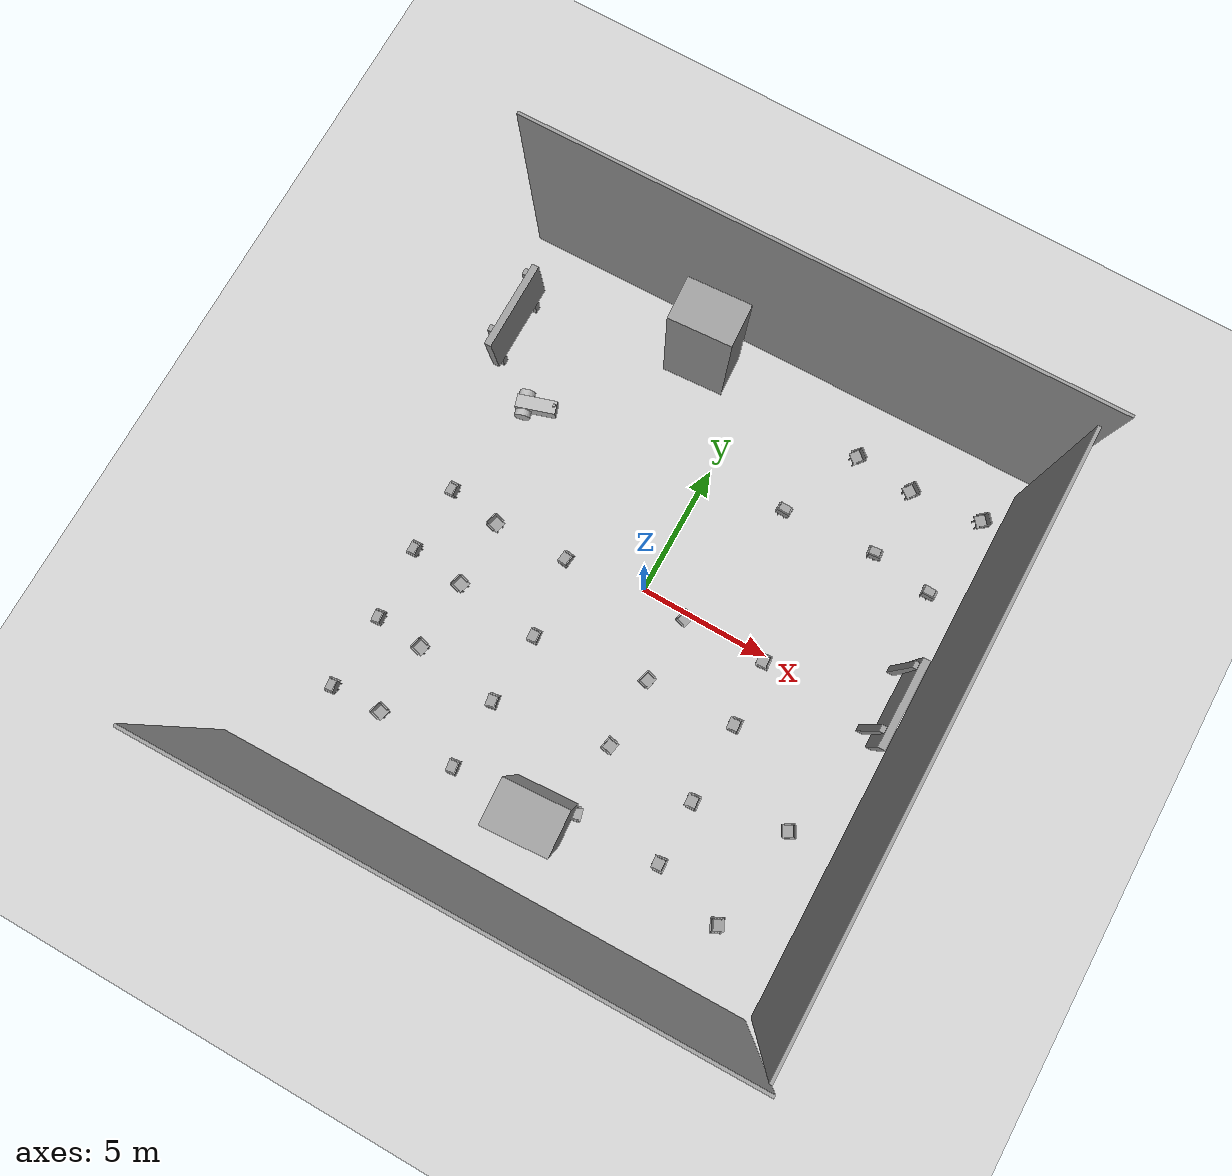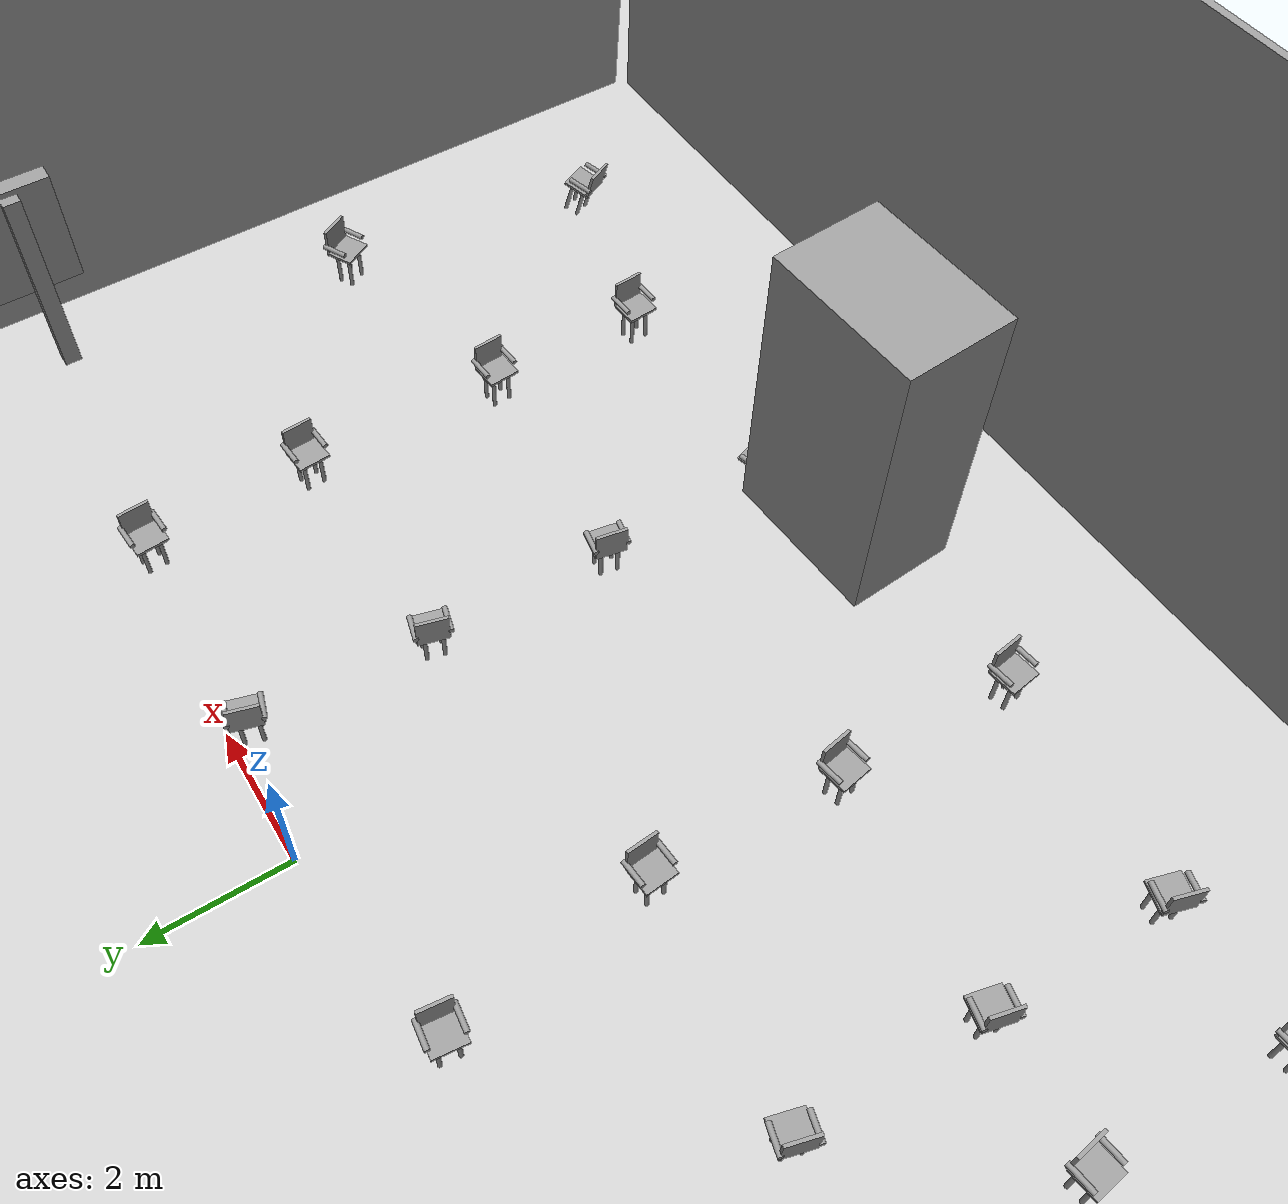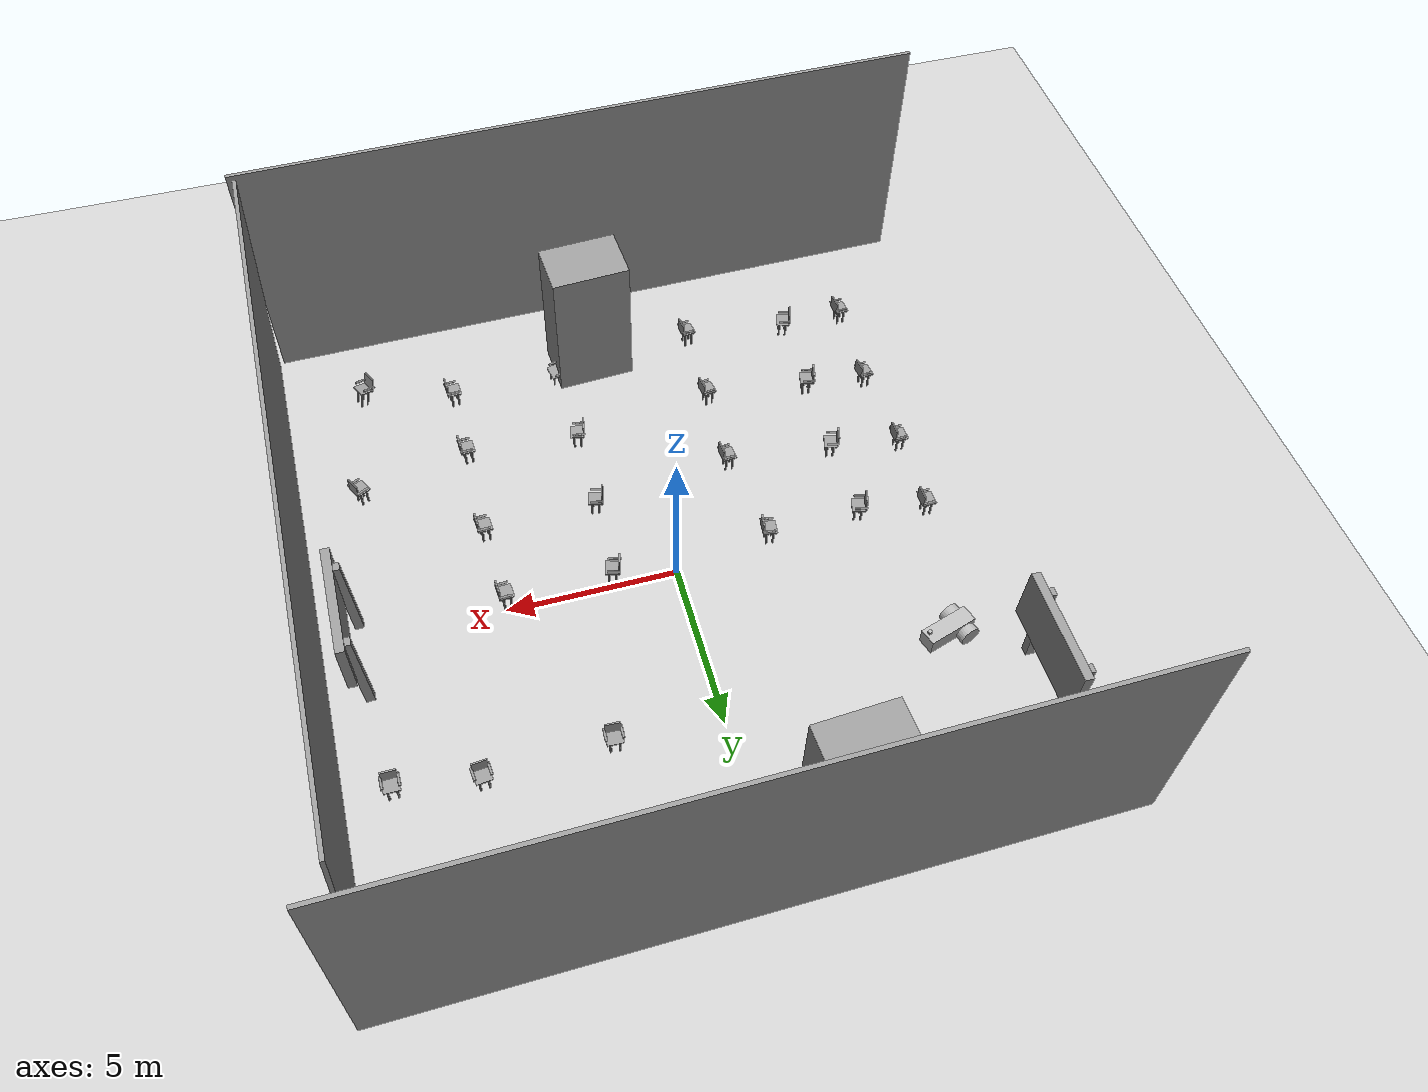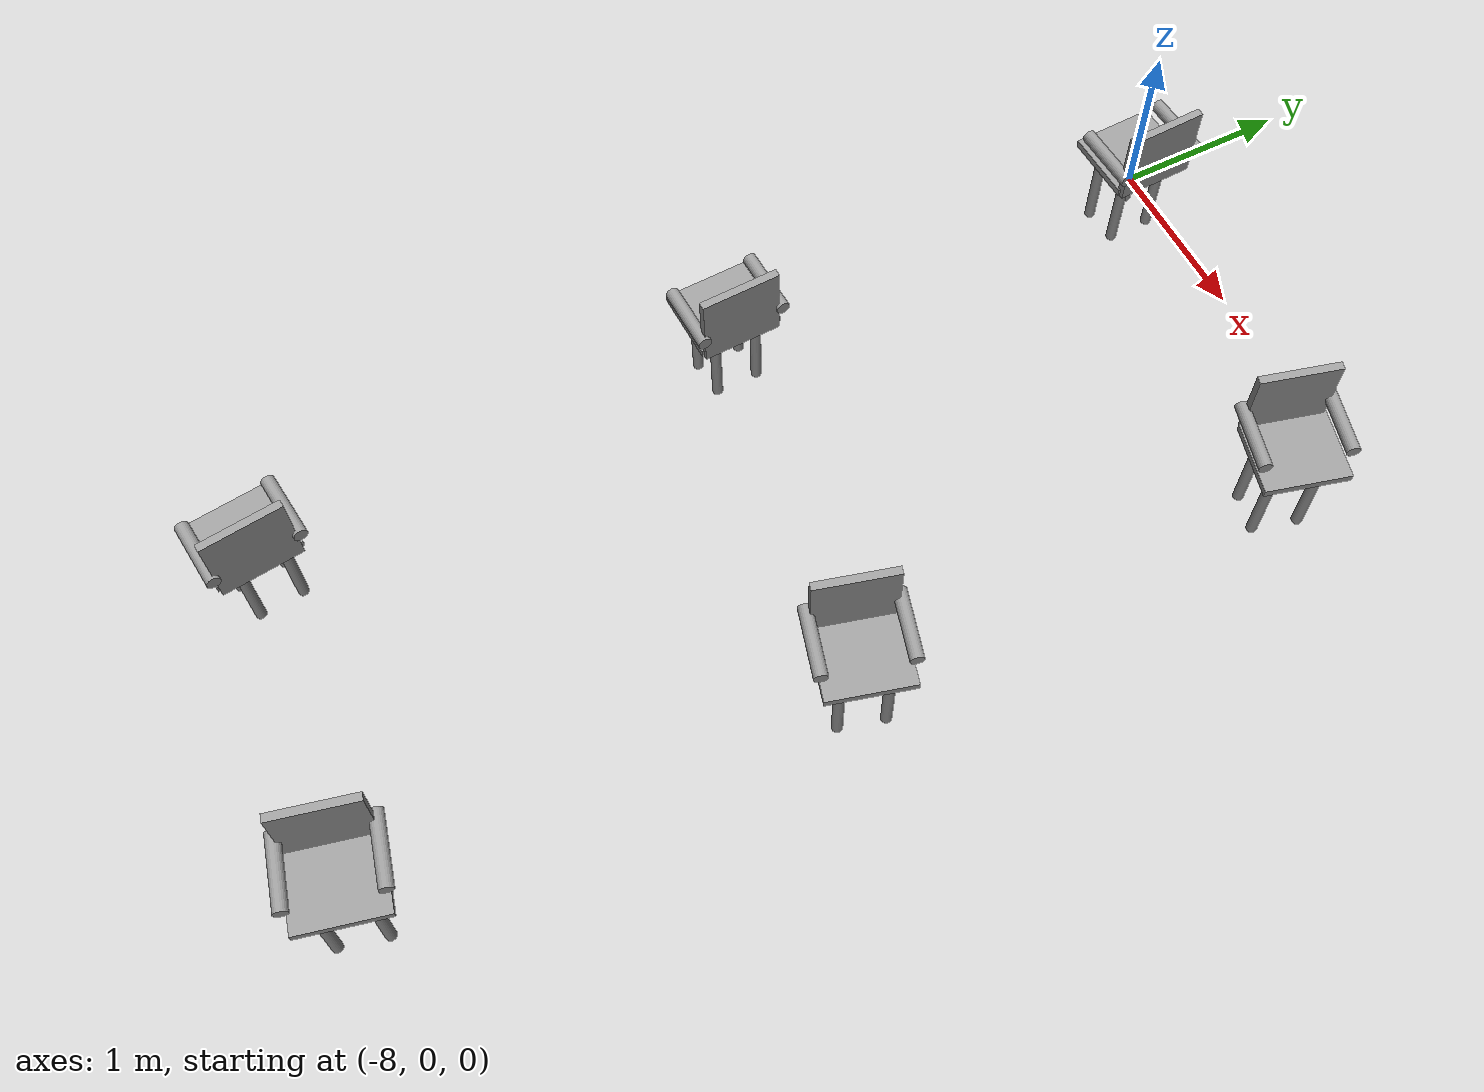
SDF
<sdf version="1.6">
 <world name="default">
  <light name="sun" type="directional">
   <pose>0 0 10 0 -0 0</pose>
   <diffuse>0.8 0.8 0.8 1</diffuse>
   <specular>0.2 0.2 0.2 1</specular>
   <attenuation>
    <range>1000</range>
    <constant>0.9</constant>
    <linear>0.01</linear>
    <quadratic>0.001</quadratic>
   </attenuation>
   <direction>-0.5 0.1 -0.9</direction>
  </light>
  <model name="ground_plane">
   <static>1</static>
   <link name="link">
    <collision name="collision">
     <geometry><plane><normal>0 0 1</normal><size>100 100</size></plane></geometry>
     <surface>
      <contact><collide_bitmask>65535</collide_bitmask></contact>
      <friction><ode><mu>100</mu><mu2>50</mu2></ode></friction>
     </surface>
    </collision>
    <visual name="visual">
     <cast_shadows>0</cast_shadows>
     <geometry><plane><normal>0 0 1</normal><size>100 100</size></plane></geometry>
     <material>
      <script><uri>file://media/materials/scripts/gazebo.material</uri><name>Gazebo/Grey</name></script>
     </material>
    </visual>
   </link>
  </model>
  <gravity>0 0 -9.8</gravity>
  <magnetic_field>6e-06 2.3e-05 -4.2e-05</magnetic_field>
  <atmosphere type="adiabatic"/>
  <physics name="default_physics" default="0" type="ode">
   <max_step_size>0.001</max_step_size>
   <real_time_factor>1</real_time_factor>
   <real_time_update_rate>1000</real_time_update_rate>
  </physics>
  <scene><ambient>0.4 0.4 0.4 1</ambient><background>0.7 0.7 0.7 1</background><shadows>1</shadows></scene>
  <audio><device>default</device></audio>
  <spherical_coordinates>
   <surface_model>EARTH_WGS84</surface_model>
   <latitude_deg>0</latitude_deg>
   <longitude_deg>0</longitude_deg>
   <elevation>0</elevation>
   <heading_deg>0</heading_deg>
  </spherical_coordinates>
  <model name="chair">
   <link name="link_4">
    <inertial>
     <mass>0.00194051</mass>
     <inertia>
      <ixx>5.14044e-05</ixx>
      <ixy>0</ixy>
      <ixz>0</ixz>
      <iyy>5.14044e-05</iyy>
      <iyz>0</iyz>
      <izz>8.34973e-07</izz>
     </inertia>
    </inertial>
    <pose>-0.140129 -0.127166 -0.209129 0 -0 0</pose>
    <visual name="visual">
     <geometry><cylinder><radius>0.0293355</radius><length>0.561516</length></cylinder></geometry>
     <material>
      <lighting>1</lighting>
      <script><uri>file://media/materials/scripts/gazebo.material</uri><name>Gazebo/Grey</name></script>
      <emissive>0 0 0 1</emissive>
     </material>
    </visual>
    <collision name="collision">
     <geometry><cylinder><radius>0.029336</radius><length>0.561516</length></cylinder></geometry>
     <surface>
      <friction>
       <ode><mu>1</mu><mu2>1</mu2><fdir1>0 0 0</fdir1><slip1>0</slip1><slip2>0</slip2></ode>
       <torsional>
        <coefficient>1</coefficient>
        <patch_radius>0</patch_radius>
        <surface_radius>0</surface_radius>
        <use_patch_radius>1</use_patch_radius>
        <ode><slip>0</slip></ode>
       </torsional>
      </friction>
      <bounce><restitution_coefficient>0</restitution_coefficient><threshold>1e+06</threshold></bounce>
      <contact>
       <collide_without_contact>0</collide_without_contact>
       <collide_without_contact_bitmask>1</collide_without_contact_bitmask>
       <collide_bitmask>1</collide_bitmask>
       <ode>
        <soft_cfm>0</soft_cfm>
        <soft_erp>0.2</soft_erp>
        <kp>1e+13</kp>
        <kd>1</kd>
        <max_vel>0.01</max_vel>
        <min_depth>0</min_depth>
       </ode>
       <bullet>
        <split_impulse>1</split_impulse>
        <split_impulse_penetration_threshold>-0.01</split_impulse_penetration_threshold>
        <soft_cfm>0</soft_cfm>
        <soft_erp>0.2</soft_erp>
        <kp>1e+13</kp>
        <kd>1</kd>
       </bullet>
      </contact>
     </surface>
    </collision>
   </link>
   <link name="link_4_clone">
    <inertial>
     <mass>0.00194051</mass>
     <inertia>
      <ixx>5.14044e-05</ixx>
      <ixy>0</ixy>
      <ixz>0</ixz>
      <iyy>5.14044e-05</iyy>
      <iyz>0</iyz>
      <izz>8.34973e-07</izz>
     </inertia>
    </inertial>
    <pose>-0.139565 0.126187 -0.209129 0 -0 0</pose>
    <visual name="visual">
     <geometry><cylinder><radius>0.0293355</radius><length>0.561516</length></cylinder></geometry>
     <material>
      <lighting>1</lighting>
      <script><uri>file://media/materials/scripts/gazebo.material</uri><name>Gazebo/Grey</name></script>
      <shader type="pixel"/>
      <emissive>0 0 0 1</emissive>
     </material>
    </visual>
    <collision name="collision">
     <geometry><cylinder><radius>0.029336</radius><length>0.561516</length></cylinder></geometry>
     <surface>
      <friction>
       <ode><mu>1</mu><mu2>1</mu2><fdir1>0 0 0</fdir1><slip1>0</slip1><slip2>0</slip2></ode>
       <torsional>
        <coefficient>1</coefficient>
        <patch_radius>0</patch_radius>
        <surface_radius>0</surface_radius>
        <use_patch_radius>1</use_patch_radius>
        <ode><slip>0</slip></ode>
       </torsional>
      </friction>
      <bounce><restitution_coefficient>0</restitution_coefficient><threshold>1e+06</threshold></bounce>
      <contact>
       <collide_without_contact>0</collide_without_contact>
       <collide_without_contact_bitmask>1</collide_without_contact_bitmask>
       <collide_bitmask>1</collide_bitmask>
       <ode>
        <soft_cfm>0</soft_cfm>
        <soft_erp>0.2</soft_erp>
        <kp>1e+13</kp>
        <kd>1</kd>
        <max_vel>0.01</max_vel>
        <min_depth>0</min_depth>
       </ode>
       <bullet>
        <split_impulse>1</split_impulse>
        <split_impulse_penetration_threshold>-0.01</split_impulse_penetration_threshold>
        <soft_cfm>0</soft_cfm>
        <soft_erp>0.2</soft_erp>
        <kp>1e+13</kp>
        <kd>1</kd>
       </bullet>
      </contact>
     </surface>
    </collision>
   </link>
   <link name="link_4_clone_0">
    <inertial>
     <mass>0.00194051</mass>
     <inertia>
      <ixx>5.14044e-05</ixx>
      <ixy>0</ixy>
      <ixz>0</ixz>
      <iyy>5.14044e-05</iyy>
      <iyz>0</iyz>
      <izz>8.34973e-07</izz>
     </inertia>
    </inertial>
    <pose>0.062929 0.13105 -0.209129 0 -0 0</pose>
    <visual name="visual">
     <geometry><cylinder><radius>0.0293355</radius><length>0.561516</length></cylinder></geometry>
     <material>
      <lighting>1</lighting>
      <script><uri>file://media/materials/scripts/gazebo.material</uri><name>Gazebo/Grey</name></script>
      <shader type="pixel"/>
      <emissive>0 0 0 1</emissive>
     </material>
    </visual>
    <collision name="collision">
     <geometry><cylinder><radius>0.029336</radius><length>0.561516</length></cylinder></geometry>
     <surface>
      <friction>
       <ode><mu>1</mu><mu2>1</mu2><fdir1>0 0 0</fdir1><slip1>0</slip1><slip2>0</slip2></ode>
       <torsional>
        <coefficient>1</coefficient>
        <patch_radius>0</patch_radius>
        <surface_radius>0</surface_radius>
        <use_patch_radius>1</use_patch_radius>
        <ode><slip>0</slip></ode>
       </torsional>
      </friction>
      <bounce><restitution_coefficient>0</restitution_coefficient><threshold>1e+06</threshold></bounce>
      <contact>
       <collide_without_contact>0</collide_without_contact>
       <collide_without_contact_bitmask>1</collide_without_contact_bitmask>
       <collide_bitmask>1</collide_bitmask>
       <ode>
        <soft_cfm>0</soft_cfm>
        <soft_erp>0.2</soft_erp>
        <kp>1e+13</kp>
        <kd>1</kd>
        <max_vel>0.01</max_vel>
        <min_depth>0</min_depth>
       </ode>
       <bullet>
        <split_impulse>1</split_impulse>
        <split_impulse_penetration_threshold>-0.01</split_impulse_penetration_threshold>
        <soft_cfm>0</soft_cfm>
        <soft_erp>0.2</soft_erp>
        <kp>1e+13</kp>
        <kd>1</kd>
       </bullet>
      </contact>
     </surface>
    </collision>
   </link>
   <link name="link_4_clone_1">
    <inertial>
     <mass>0.00194051</mass>
     <inertia>
      <ixx>5.14044e-05</ixx>
      <ixy>0</ixy>
      <ixz>0</ixz>
      <iyy>5.14044e-05</iyy>
      <iyz>0</iyz>
      <izz>8.34973e-07</izz>
     </inertia>
    </inertial>
    <pose>0.061641 -0.111934 -0.209129 0 -0 0</pose>
    <visual name="visual">
     <geometry><cylinder><radius>0.0293355</radius><length>0.561516</length></cylinder></geometry>
     <material>
      <lighting>1</lighting>
      <script><uri>file://media/materials/scripts/gazebo.material</uri><name>Gazebo/Grey</name></script>
      <shader type="pixel"/>
      <emissive>0 0 0 1</emissive>
     </material>
    </visual>
    <collision name="collision">
     <geometry><cylinder><radius>0.029336</radius><length>0.561516</length></cylinder></geometry>
     <surface>
      <friction>
       <ode><mu>1</mu><mu2>1</mu2><fdir1>0 0 0</fdir1><slip1>0</slip1><slip2>0</slip2></ode>
       <torsional>
        <coefficient>1</coefficient>
        <patch_radius>0</patch_radius>
        <surface_radius>0</surface_radius>
        <use_patch_radius>1</use_patch_radius>
        <ode><slip>0</slip></ode>
       </torsional>
      </friction>
      <bounce><restitution_coefficient>0</restitution_coefficient><threshold>1e+06</threshold></bounce>
      <contact>
       <collide_without_contact>0</collide_without_contact>
       <collide_without_contact_bitmask>1</collide_without_contact_bitmask>
       <collide_bitmask>1</collide_bitmask>
       <ode>
        <soft_cfm>0</soft_cfm>
        <soft_erp>0.2</soft_erp>
        <kp>1e+13</kp>
        <kd>1</kd>
        <max_vel>0.01</max_vel>
        <min_depth>0</min_depth>
       </ode>
       <bullet>
        <split_impulse>1</split_impulse>
        <split_impulse_penetration_threshold>-0.01</split_impulse_penetration_threshold>
        <soft_cfm>0</soft_cfm>
        <soft_erp>0.2</soft_erp>
        <kp>1e+13</kp>
        <kd>1</kd>
       </bullet>
      </contact>
     </surface>
    </collision>
   </link>
   <link name="link_5">
    <inertial>
     <mass>0.00816884</mass>
     <inertia>
      <ixx>0.00015002</ixx>
      <ixy>0</ixy>
      <ixz>0</ixz>
      <iyy>0.000115328</iyy>
      <iyz>0</iyz>
      <izz>0.000262862</izz>
     </inertia>
    </inertial>
    <pose>-0.041662 -0.005028 0.089077 0 -0 0</pose>
    <visual name="visual">
     <geometry><box><size>0.409378 0.467496 0.042729</size></box></geometry>
     <material>
      <lighting>1</lighting>
      <script><uri>file://media/materials/scripts/gazebo.material</uri><name>Gazebo/Grey</name></script>
      <emissive>0 0 0 1</emissive>
     </material>
    </visual>
    <collision name="collision">
     <geometry><box><size>0.409378 0.467496 0.042729</size></box></geometry>
     <surface>
      <friction>
       <ode><mu>1</mu><mu2>1</mu2><fdir1>0 0 0</fdir1><slip1>0</slip1><slip2>0</slip2></ode>
       <torsional>
        <coefficient>1</coefficient>
        <patch_radius>0</patch_radius>
        <surface_radius>0</surface_radius>
        <use_patch_radius>1</use_patch_radius>
        <ode><slip>0</slip></ode>
       </torsional>
      </friction>
      <bounce><restitution_coefficient>0</restitution_coefficient><threshold>1e+06</threshold></bounce>
      <contact>
       <collide_without_contact>0</collide_without_contact>
       <collide_without_contact_bitmask>1</collide_without_contact_bitmask>
       <collide_bitmask>1</collide_bitmask>
       <ode>
        <soft_cfm>0</soft_cfm>
        <soft_erp>0.2</soft_erp>
        <kp>1e+13</kp>
        <kd>1</kd>
        <max_vel>0.01</max_vel>
        <min_depth>0</min_depth>
       </ode>
       <bullet>
        <split_impulse>1</split_impulse>
        <split_impulse_penetration_threshold>-0.01</split_impulse_penetration_threshold>
        <soft_cfm>0</soft_cfm>
        <soft_erp>0.2</soft_erp>
        <kp>1e+13</kp>
        <kd>1</kd>
       </bullet>
      </contact>
     </surface>
    </collision>
   </link>
   <link name="link_6">
    <inertial>
     <mass>0.00855687</mass>
     <inertia>
      <ixx>0.000285159</ixx>
      <ixy>0</ixy>
      <ixz>0</ixz>
      <iyy>0.000146983</iyy>
      <iyz>0</iyz>
      <izz>0.000140925</izz>
     </inertia>
    </inertial>
    <pose>0.165697 -0.006458 0.287866 0 -0 0</pose>
    <visual name="visual">
     <geometry><box><size>0.0439 0.442383 0.451884</size></box></geometry>
     <material>
      <lighting>1</lighting>
      <script><uri>file://media/materials/scripts/gazebo.material</uri><name>Gazebo/Grey</name></script>
      <emissive>0 0 0 1</emissive>
     </material>
    </visual>
    <collision name="collision">
     <geometry><box><size>0.0439 0.442383 0.451884</size></box></geometry>
     <surface>
      <friction>
       <ode><mu>1</mu><mu2>1</mu2><fdir1>0 0 0</fdir1><slip1>0</slip1><slip2>0</slip2></ode>
       <torsional>
        <coefficient>1</coefficient>
        <patch_radius>0</patch_radius>
        <surface_radius>0</surface_radius>
        <use_patch_radius>1</use_patch_radius>
        <ode><slip>0</slip></ode>
       </torsional>
      </friction>
      <bounce><restitution_coefficient>0</restitution_coefficient><threshold>1e+06</threshold></bounce>
      <contact>
       <collide_without_contact>0</collide_without_contact>
       <collide_without_contact_bitmask>1</collide_without_contact_bitmask>
       <collide_bitmask>1</collide_bitmask>
       <ode>
        <soft_cfm>0</soft_cfm>
        <soft_erp>0.2</soft_erp>
        <kp>1e+13</kp>
        <kd>1</kd>
        <max_vel>0.01</max_vel>
        <min_depth>0</min_depth>
       </ode>
       <bullet>
        <split_impulse>1</split_impulse>
        <split_impulse_penetration_threshold>-0.01</split_impulse_penetration_threshold>
        <soft_cfm>0</soft_cfm>
        <soft_erp>0.2</soft_erp>
        <kp>1e+13</kp>
        <kd>1</kd>
       </bullet>
      </contact>
     </surface>
    </collision>
   </link>
   <link name="link_7">
    <inertial>
     <mass>0.00209129</mass>
     <inertia>
      <ixx>2.57536e-05</ixx>
      <ixy>0</ixy>
      <ixz>0</ixz>
      <iyy>2.57536e-05</iyy>
      <iyz>0</iyz>
      <izz>1.44551e-06</izz>
     </inertia>
    </inertial>
    <pose>0.0147 0.228665 0.230372 0 1.55081 0</pose>
    <visual name="visual">
     <geometry><cylinder><radius>0.0371808</radius><length>0.378984</length></cylinder></geometry>
     <material>
      <lighting>1</lighting>
      <script><uri>file://media/materials/scripts/gazebo.material</uri><name>Gazebo/Grey</name></script>
      <emissive>0 0 0 1</emissive>
     </material>
    </visual>
    <collision name="collision">
     <geometry><cylinder><radius>0.037181</radius><length>0.378984</length></cylinder></geometry>
     <surface>
      <friction>
       <ode><mu>1</mu><mu2>1</mu2><fdir1>0 0 0</fdir1><slip1>0</slip1><slip2>0</slip2></ode>
       <torsional>
        <coefficient>1</coefficient>
        <patch_radius>0</patch_radius>
        <surface_radius>0</surface_radius>
        <use_patch_radius>1</use_patch_radius>
        <ode><slip>0</slip></ode>
       </torsional>
      </friction>
      <bounce><restitution_coefficient>0</restitution_coefficient><threshold>1e+06</threshold></bounce>
      <contact>
       <collide_without_contact>0</collide_without_contact>
       <collide_without_contact_bitmask>1</collide_without_contact_bitmask>
       <collide_bitmask>1</collide_bitmask>
       <ode>
        <soft_cfm>0</soft_cfm>
        <soft_erp>0.2</soft_erp>
        <kp>1e+13</kp>
        <kd>1</kd>
        <max_vel>0.01</max_vel>
        <min_depth>0</min_depth>
       </ode>
       <bullet>
        <split_impulse>1</split_impulse>
        <split_impulse_penetration_threshold>-0.01</split_impulse_penetration_threshold>
        <soft_cfm>0</soft_cfm>
        <soft_erp>0.2</soft_erp>
        <kp>1e+13</kp>
        <kd>1</kd>
       </bullet>
      </contact>
     </surface>
    </collision>
   </link>
   <link name="link_7_clone">
    <inertial>
     <mass>0.00209129</mass>
     <inertia>
      <ixx>2.57536e-05</ixx>
      <ixy>0</ixy>
      <ixz>0</ixz>
      <iyy>2.57536e-05</iyy>
      <iyz>0</iyz>
      <izz>1.44551e-06</izz>
     </inertia>
    </inertial>
    <pose>0.01639 -0.235319 0.229201 0 1.55081 0</pose>
    <visual name="visual">
     <geometry><cylinder><radius>0.0371808</radius><length>0.378984</length></cylinder></geometry>
     <material>
      <lighting>1</lighting>
      <script><uri>file://media/materials/scripts/gazebo.material</uri><name>Gazebo/Grey</name></script>
      <shader type="pixel"/>
      <emissive>0 0 0 1</emissive>
     </material>
    </visual>
    <collision name="collision">
     <geometry><cylinder><radius>0.037181</radius><length>0.378984</length></cylinder></geometry>
     <surface>
      <friction>
       <ode><mu>1</mu><mu2>1</mu2><fdir1>0 0 0</fdir1><slip1>0</slip1><slip2>0</slip2></ode>
       <torsional>
        <coefficient>1</coefficient>
        <patch_radius>0</patch_radius>
        <surface_radius>0</surface_radius>
        <use_patch_radius>1</use_patch_radius>
        <ode><slip>0</slip></ode>
       </torsional>
      </friction>
      <bounce><restitution_coefficient>0</restitution_coefficient><threshold>1e+06</threshold></bounce>
      <contact>
       <collide_without_contact>0</collide_without_contact>
       <collide_without_contact_bitmask>1</collide_without_contact_bitmask>
       <collide_bitmask>1</collide_bitmask>
       <ode>
        <soft_cfm>0</soft_cfm>
        <soft_erp>0.2</soft_erp>
        <kp>1e+13</kp>
        <kd>1</kd>
        <max_vel>0.01</max_vel>
        <min_depth>0</min_depth>
       </ode>
       <bullet>
        <split_impulse>1</split_impulse>
        <split_impulse_penetration_threshold>-0.01</split_impulse_penetration_threshold>
        <soft_cfm>0</soft_cfm>
        <soft_erp>0.2</soft_erp>
        <kp>1e+13</kp>
        <kd>1</kd>
       </bullet>
      </contact>
     </surface>
    </collision>
   </link>
   <joint name="link_5_JOINT_2" type="fixed">
    <parent>link_5</parent>
    <child>link_4_clone_1</child>
    <physics>
     <ode><limit><cfm>0</cfm><erp>0.2</erp></limit><suspension><cfm>0</cfm><erp>0.2</erp></suspension></ode>
    </physics>
   </joint>
   <joint name="link_5_JOINT_3" type="fixed">
    <parent>link_5</parent>
    <child>link_4</child>
    <physics>
     <ode><limit><cfm>0</cfm><erp>0.2</erp></limit><suspension><cfm>0</cfm><erp>0.2</erp></suspension></ode>
    </physics>
   </joint>
   <joint name="link_5_JOINT_4" type="fixed">
    <parent>link_5</parent>
    <child>link_4_clone_0</child>
    <physics>
     <ode><limit><cfm>0</cfm><erp>0.2</erp></limit><suspension><cfm>0</cfm><erp>0.2</erp></suspension></ode>
    </physics>
   </joint>
   <joint name="link_5_JOINT_5" type="fixed">
    <parent>link_5</parent>
    <child>link_4_clone</child>
    <physics>
     <ode><limit><cfm>0</cfm><erp>0.2</erp></limit><suspension><cfm>0</cfm><erp>0.2</erp></suspension></ode>
    </physics>
   </joint>
   <joint name="link_5_JOINT_6" type="fixed">
    <parent>link_5</parent>
    <child>link_6</child>
    <physics>
     <ode><limit><cfm>0</cfm><erp>0.2</erp></limit><suspension><cfm>0</cfm><erp>0.2</erp></suspension></ode>
    </physics>
   </joint>
   <joint name="link_5_JOINT_7" type="fixed">
    <parent>link_5</parent>
    <child>link_7</child>
    <physics>
     <ode><limit><cfm>0</cfm><erp>0.2</erp></limit><suspension><cfm>0</cfm><erp>0.2</erp></suspension></ode>
    </physics>
   </joint>
   <joint name="link_5_JOINT_8" type="fixed">
    <parent>link_5</parent>
    <child>link_7_clone</child>
    <physics>
     <ode><limit><cfm>0</cfm><erp>0.2</erp></limit><suspension><cfm>0</cfm><erp>0.2</erp></suspension></ode>
    </physics>
   </joint>
   <static>0</static>
   <pose>-2.51387 -3.39214 0.489883 0 3.2e-05 0.075573</pose>
  </model>
  <model name="chair_clone">
   <link name="link_4">
    <inertial>
     <mass>0.00194051</mass>
     <inertia>
      <ixx>5.14044e-05</ixx>
      <ixy>0</ixy>
      <ixz>0</ixz>
      <iyy>5.14044e-05</iyy>
      <iyz>0</iyz>
      <izz>8.34973e-07</izz>
     </inertia>
    </inertial>
    <pose>-0.140129 -0.127166 -0.209129 0 -0 0</pose>
    <visual name="visual">
     <geometry><cylinder><radius>0.0293355</radius><length>0.561516</length></cylinder></geometry>
     <material>
      <lighting>1</lighting>
      <script><uri>file://media/materials/scripts/gazebo.material</uri><name>Gazebo/Grey</name></script>
      <emissive>0 0 0 1</emissive>
     </material>
    </visual>
    <collision name="collision">
     <geometry><cylinder><radius>0.029336</radius><length>0.561516</length></cylinder></geometry>
     <surface>
      <friction>
       <ode><mu>1</mu><mu2>1</mu2><fdir1>0 0 0</fdir1><slip1>0</slip1><slip2>0</slip2></ode>
       <torsional>
        <coefficient>1</coefficient>
        <patch_radius>0</patch_radius>
        <surface_radius>0</surface_radius>
        <use_patch_radius>1</use_patch_radius>
        <ode><slip>0</slip></ode>
       </torsional>
      </friction>
      <bounce><restitution_coefficient>0</restitution_coefficient><threshold>1e+06</threshold></bounce>
      <contact>
       <collide_without_contact>0</collide_without_contact>
       <collide_without_contact_bitmask>1</collide_without_contact_bitmask>
       <collide_bitmask>1</collide_bitmask>
       <ode>
        <soft_cfm>0</soft_cfm>
        <soft_erp>0.2</soft_erp>
        <kp>1e+13</kp>
        <kd>1</kd>
        <max_vel>0.01</max_vel>
        <min_depth>0</min_depth>
       </ode>
       <bullet>
        <split_impulse>1</split_impulse>
        <split_impulse_penetration_threshold>-0.01</split_impulse_penetration_threshold>
        <soft_cfm>0</soft_cfm>
        <soft_erp>0.2</soft_erp>
        <kp>1e+13</kp>
        <kd>1</kd>
       </bullet>
      </contact>
     </surface>
    </collision>
   </link>
   <link name="link_4_clone">
    <inertial>
     <mass>0.00194051</mass>
     <inertia>
      <ixx>5.14044e-05</ixx>
      <ixy>0</ixy>
      <ixz>0</ixz>
      <iyy>5.14044e-05</iyy>
      <iyz>0</iyz>
      <izz>8.34973e-07</izz>
     </inertia>
    </inertial>
    <pose>-0.139565 0.126187 -0.209129 0 -0 0</pose>
    <visual name="visual">
     <geometry><cylinder><radius>0.0293355</radius><length>0.561516</length></cylinder></geometry>
     <material>
      <lighting>1</lighting>
      <script><uri>file://media/materials/scripts/gazebo.material</uri><name>Gazebo/Grey</name></script>
      <shader type="pixel"/>
      <emissive>0 0 0 1</emissive>
     </material>
    </visual>
    <collision name="collision">
     <geometry><cylinder><radius>0.029336</radius><length>0.561516</length></cylinder></geometry>
     <surface>
      <friction>
       <ode><mu>1</mu><mu2>1</mu2><fdir1>0 0 0</fdir1><slip1>0</slip1><slip2>0</slip2></ode>
       <torsional>
        <coefficient>1</coefficient>
        <patch_radius>0</patch_radius>
        <surface_radius>0</surface_radius>
        <use_patch_radius>1</use_patch_radius>
        <ode><slip>0</slip></ode>
       </torsional>
      </friction>
      <bounce><restitution_coefficient>0</restitution_coefficient><threshold>1e+06</threshold></bounce>
      <contact>
       <collide_without_contact>0</collide_without_contact>
       <collide_without_contact_bitmask>1</collide_without_contact_bitmask>
       <collide_bitmask>1</collide_bitmask>
       <ode>
        <soft_cfm>0</soft_cfm>
        <soft_erp>0.2</soft_erp>
        <kp>1e+13</kp>
        <kd>1</kd>
        <max_vel>0.01</max_vel>
        <min_depth>0</min_depth>
       </ode>
       <bullet>
        <split_impulse>1</split_impulse>
        <split_impulse_penetration_threshold>-0.01</split_impulse_penetration_threshold>
        <soft_cfm>0</soft_cfm>
        <soft_erp>0.2</soft_erp>
        <kp>1e+13</kp>
        <kd>1</kd>
       </bullet>
      </contact>
     </surface>
    </collision>
   </link>
   <link name="link_4_clone_0">
    <inertial>
     <mass>0.00194051</mass>
     <inertia>
      <ixx>5.14044e-05</ixx>
      <ixy>0</ixy>
      <ixz>0</ixz>
      <iyy>5.14044e-05</iyy>
      <iyz>0</iyz>
      <izz>8.34973e-07</izz>
     </inertia>
    </inertial>
    <pose>0.062929 0.13105 -0.209129 0 -0 0</pose>
    <visual name="visual">
     <geometry><cylinder><radius>0.0293355</radius><length>0.561516</length></cylinder></geometry>
     <material>
      <lighting>1</lighting>
      <script><uri>file://media/materials/scripts/gazebo.material</uri><name>Gazebo/Grey</name></script>
      <shader type="pixel"/>
      <emissive>0 0 0 1</emissive>
     </material>
    </visual>
    <collision name="collision">
     <geometry><cylinder><radius>0.029336</radius><length>0.561516</length></cylinder></geometry>
     <surface>
      <friction>
       <ode><mu>1</mu><mu2>1</mu2><fdir1>0 0 0</fdir1><slip1>0</slip1><slip2>0</slip2></ode>
       <torsional>
        <coefficient>1</coefficient>
        <patch_radius>0</patch_radius>
        <surface_radius>0</surface_radius>
        <use_patch_radius>1</use_patch_radius>
        <ode><slip>0</slip></ode>
       </torsional>
      </friction>
      <bounce><restitution_coefficient>0</restitution_coefficient><threshold>1e+06</threshold></bounce>
      <contact>
       <collide_without_contact>0</collide_without_contact>
       <collide_without_contact_bitmask>1</collide_without_contact_bitmask>
       <collide_bitmask>1</collide_bitmask>
       <ode>
        <soft_cfm>0</soft_cfm>
        <soft_erp>0.2</soft_erp>
        <kp>1e+13</kp>
        <kd>1</kd>
        <max_vel>0.01</max_vel>
        <min_depth>0</min_depth>
       </ode>
       <bullet>
        <split_impulse>1</split_impulse>
        <split_impulse_penetration_threshold>-0.01</split_impulse_penetration_threshold>
        <soft_cfm>0</soft_cfm>
        <soft_erp>0.2</soft_erp>
        <kp>1e+13</kp>
        <kd>1</kd>
       </bullet>
      </contact>
     </surface>
    </collision>
   </link>
   <link name="link_4_clone_1">
    <inertial>
     <mass>0.00194051</mass>
     <inertia>
      <ixx>5.14044e-05</ixx>
      <ixy>0</ixy>
      <ixz>0</ixz>
      <iyy>5.14044e-05</iyy>
      <iyz>0</iyz>
      <izz>8.34973e-07</izz>
     </inertia>
    </inertial>
    <pose>0.061641 -0.111934 -0.209129 0 -0 0</pose>
    <visual name="visual">
     <geometry><cylinder><radius>0.0293355</radius><length>0.561516</length></cylinder></geometry>
     <material>
      <lighting>1</lighting>
      <script><uri>file://media/materials/scripts/gazebo.material</uri><name>Gazebo/Grey</name></script>
      <shader type="pixel"/>
      <emissive>0 0 0 1</emissive>
     </material>
    </visual>
    <collision name="collision">
     <geometry><cylinder><radius>0.029336</radius><length>0.561516</length></cylinder></geometry>
     <surface>
      <friction>
       <ode><mu>1</mu><mu2>1</mu2><fdir1>0 0 0</fdir1><slip1>0</slip1><slip2>0</slip2></ode>
       <torsional>
        <coefficient>1</coefficient>
        <patch_radius>0</patch_radius>
        <surface_radius>0</surface_radius>
        <use_patch_radius>1</use_patch_radius>
        <ode><slip>0</slip></ode>
       </torsional>
      </friction>
      <bounce><restitution_coefficient>0</restitution_coefficient><threshold>1e+06</threshold></bounce>
      <contact>
       <collide_without_contact>0</collide_without_contact>
       <collide_without_contact_bitmask>1</collide_without_contact_bitmask>
       <collide_bitmask>1</collide_bitmask>
       <ode>
        <soft_cfm>0</soft_cfm>
        <soft_erp>0.2</soft_erp>
        <kp>1e+13</kp>
        <kd>1</kd>
        <max_vel>0.01</max_vel>
        <min_depth>0</min_depth>
       </ode>
       <bullet>
        <split_impulse>1</split_impulse>
        <split_impulse_penetration_threshold>-0.01</split_impulse_penetration_threshold>
        <soft_cfm>0</soft_cfm>
        <soft_erp>0.2</soft_erp>
        <kp>1e+13</kp>
        <kd>1</kd>
       </bullet>
      </contact>
     </surface>
    </collision>
   </link>
   <link name="link_5">
    <inertial>
     <mass>0.00816884</mass>
     <inertia>
      <ixx>0.00015002</ixx>
      <ixy>0</ixy>
      <ixz>0</ixz>
      <iyy>0.000115328</iyy>
      <iyz>0</iyz>
      <izz>0.000262862</izz>
     </inertia>
    </inertial>
    <pose>-0.041662 -0.005028 0.089077 0 -0 0</pose>
    <visual name="visual">
     <geometry><box><size>0.409378 0.467496 0.042729</size></box></geometry>
     <material>
      <lighting>1</lighting>
      <script><uri>file://media/materials/scripts/gazebo.material</uri><name>Gazebo/Grey</name></script>
      <emissive>0 0 0 1</emissive>
     </material>
    </visual>
    <collision name="collision">
     <geometry><box><size>0.409378 0.467496 0.042729</size></box></geometry>
     <surface>
      <friction>
       <ode><mu>1</mu><mu2>1</mu2><fdir1>0 0 0</fdir1><slip1>0</slip1><slip2>0</slip2></ode>
       <torsional>
        <coefficient>1</coefficient>
        <patch_radius>0</patch_radius>
        <surface_radius>0</surface_radius>
        <use_patch_radius>1</use_patch_radius>
        <ode><slip>0</slip></ode>
       </torsional>
      </friction>
      <bounce><restitution_coefficient>0</restitution_coefficient><threshold>1e+06</threshold></bounce>
      <contact>
       <collide_without_contact>0</collide_without_contact>
       <collide_without_contact_bitmask>1</collide_without_contact_bitmask>
       <collide_bitmask>1</collide_bitmask>
       <ode>
        <soft_cfm>0</soft_cfm>
        <soft_erp>0.2</soft_erp>
        <kp>1e+13</kp>
        <kd>1</kd>
        <max_vel>0.01</max_vel>
        <min_depth>0</min_depth>
       </ode>
       <bullet>
        <split_impulse>1</split_impulse>
        <split_impulse_penetration_threshold>-0.01</split_impulse_penetration_threshold>
        <soft_cfm>0</soft_cfm>
        <soft_erp>0.2</soft_erp>
        <kp>1e+13</kp>
        <kd>1</kd>
       </bullet>
      </contact>
     </surface>
    </collision>
   </link>
   <link name="link_6">
    <inertial>
     <mass>0.00855687</mass>
     <inertia>
      <ixx>0.000285159</ixx>
      <ixy>0</ixy>
      <ixz>0</ixz>
      <iyy>0.000146983</iyy>
      <iyz>0</iyz>
      <izz>0.000140925</izz>
     </inertia>
    </inertial>
    <pose>0.165697 -0.006458 0.287866 0 -0 0</pose>
    <visual name="visual">
     <geometry><box><size>0.0439 0.442383 0.451884</size></box></geometry>
     <material>
      <lighting>1</lighting>
      <script><uri>file://media/materials/scripts/gazebo.material</uri><name>Gazebo/Grey</name></script>
      <emissive>0 0 0 1</emissive>
     </material>
    </visual>
    <collision name="collision">
     <geometry><box><size>0.0439 0.442383 0.451884</size></box></geometry>
     <surface>
      <friction>
       <ode><mu>1</mu><mu2>1</mu2><fdir1>0 0 0</fdir1><slip1>0</slip1><slip2>0</slip2></ode>
       <torsional>
        <coefficient>1</coefficient>
        <patch_radius>0</patch_radius>
        <surface_radius>0</surface_radius>
        <use_patch_radius>1</use_patch_radius>
        <ode><slip>0</slip></ode>
       </torsional>
      </friction>
      <bounce><restitution_coefficient>0</restitution_coefficient><threshold>1e+06</threshold></bounce>
      <contact>
       <collide_without_contact>0</collide_without_contact>
       <collide_without_contact_bitmask>1</collide_without_contact_bitmask>
       <collide_bitmask>1</collide_bitmask>
       <ode>
        <soft_cfm>0</soft_cfm>
        <soft_erp>0.2</soft_erp>
        <kp>1e+13</kp>
        <kd>1</kd>
        <max_vel>0.01</max_vel>
        <min_depth>0</min_depth>
       </ode>
       <bullet>
        <split_impulse>1</split_impulse>
        <split_impulse_penetration_threshold>-0.01</split_impulse_penetration_threshold>
        <soft_cfm>0</soft_cfm>
        <soft_erp>0.2</soft_erp>
        <kp>1e+13</kp>
        <kd>1</kd>
       </bullet>
      </contact>
     </surface>
    </collision>
   </link>
   <link name="link_7">
    <inertial>
     <mass>0.00209129</mass>
     <inertia>
      <ixx>2.57536e-05</ixx>
      <ixy>0</ixy>
      <ixz>0</ixz>
      <iyy>2.57536e-05</iyy>
      <iyz>0</iyz>
      <izz>1.44551e-06</izz>
     </inertia>
    </inertial>
    <pose>0.0147 0.228665 0.230372 0 1.55081 0</pose>
    <visual name="visual">
     <geometry><cylinder><radius>0.0371808</radius><length>0.378984</length></cylinder></geometry>
     <material>
      <lighting>1</lighting>
      <script><uri>file://media/materials/scripts/gazebo.material</uri><name>Gazebo/Grey</name></script>
      <emissive>0 0 0 1</emissive>
     </material>
    </visual>
    <collision name="collision">
     <geometry><cylinder><radius>0.037181</radius><length>0.378984</length></cylinder></geometry>
     <surface>
      <friction>
       <ode><mu>1</mu><mu2>1</mu2><fdir1>0 0 0</fdir1><slip1>0</slip1><slip2>0</slip2></ode>
       <torsional>
        <coefficient>1</coefficient>
        <patch_radius>0</patch_radius>
        <surface_radius>0</surface_radius>
        <use_patch_radius>1</use_patch_radius>
        <ode><slip>0</slip></ode>
       </torsional>
      </friction>
      <bounce><restitution_coefficient>0</restitution_coefficient><threshold>1e+06</threshold></bounce>
      <contact>
       <collide_without_contact>0</collide_without_contact>
       <collide_without_contact_bitmask>1</collide_without_contact_bitmask>
       <collide_bitmask>1</collide_bitmask>
       <ode>
        <soft_cfm>0</soft_cfm>
        <soft_erp>0.2</soft_erp>
        <kp>1e+13</kp>
        <kd>1</kd>
        <max_vel>0.01</max_vel>
        <min_depth>0</min_depth>
       </ode>
       <bullet>
        <split_impulse>1</split_impulse>
        <split_impulse_penetration_threshold>-0.01</split_impulse_penetration_threshold>
        <soft_cfm>0</soft_cfm>
        <soft_erp>0.2</soft_erp>
        <kp>1e+13</kp>
        <kd>1</kd>
       </bullet>
      </contact>
     </surface>
    </collision>
   </link>
   <link name="link_7_clone">
    <inertial>
     <mass>0.00209129</mass>
     <inertia>
      <ixx>2.57536e-05</ixx>
      <ixy>0</ixy>
      <ixz>0</ixz>
      <iyy>2.57536e-05</iyy>
      <iyz>0</iyz>
      <izz>1.44551e-06</izz>
     </inertia>
    </inertial>
    <pose>0.01639 -0.235319 0.229201 0 1.55081 0</pose>
    <visual name="visual">
     <geometry><cylinder><radius>0.0371808</radius><length>0.378984</length></cylinder></geometry>
     <material>
      <lighting>1</lighting>
      <script><uri>file://media/materials/scripts/gazebo.material</uri><name>Gazebo/Grey</name></script>
      <shader type="pixel"/>
      <emissive>0 0 0 1</emissive>
     </material>
    </visual>
    <collision name="collision">
     <geometry><cylinder><radius>0.037181</radius><length>0.378984</length></cylinder></geometry>
     <surface>
      <friction>
       <ode><mu>1</mu><mu2>1</mu2><fdir1>0 0 0</fdir1><slip1>0</slip1><slip2>0</slip2></ode>
       <torsional>
        <coefficient>1</coefficient>
        <patch_radius>0</patch_radius>
        <surface_radius>0</surface_radius>
        <use_patch_radius>1</use_patch_radius>
        <ode><slip>0</slip></ode>
       </torsional>
      </friction>
      <bounce><restitution_coefficient>0</restitution_coefficient><threshold>1e+06</threshold></bounce>
      <contact>
       <collide_without_contact>0</collide_without_contact>
       <collide_without_contact_bitmask>1</collide_without_contact_bitmask>
       <collide_bitmask>1</collide_bitmask>
       <ode>
        <soft_cfm>0</soft_cfm>
        <soft_erp>0.2</soft_erp>
        <kp>1e+13</kp>
        <kd>1</kd>
        <max_vel>0.01</max_vel>
        <min_depth>0</min_depth>
       </ode>
       <bullet>
        <split_impulse>1</split_impulse>
        <split_impulse_penetration_threshold>-0.01</split_impulse_penetration_threshold>
        <soft_cfm>0</soft_cfm>
        <soft_erp>0.2</soft_erp>
        <kp>1e+13</kp>
        <kd>1</kd>
       </bullet>
      </contact>
     </surface>
    </collision>
   </link>
   <joint name="link_5_JOINT_2" type="fixed">
    <parent>link_5</parent>
    <child>link_4_clone_1</child>
    <physics>
     <ode><limit><cfm>0</cfm><erp>0.2</erp></limit><suspension><cfm>0</cfm><erp>0.2</erp></suspension></ode>
    </physics>
   </joint>
   <joint name="link_5_JOINT_3" type="fixed">
    <parent>link_5</parent>
    <child>link_4</child>
    <physics>
     <ode><limit><cfm>0</cfm><erp>0.2</erp></limit><suspension><cfm>0</cfm><erp>0.2</erp></suspension></ode>
    </physics>
   </joint>
   <joint name="link_5_JOINT_4" type="fixed">
    <parent>link_5</parent>
    <child>link_4_clone_0</child>
    <physics>
     <ode><limit><cfm>0</cfm><erp>0.2</erp></limit><suspension><cfm>0</cfm><erp>0.2</erp></suspension></ode>
    </physics>
   </joint>
   <joint name="link_5_JOINT_5" type="fixed">
    <parent>link_5</parent>
    <child>link_4_clone</child>
    <physics>
     <ode><limit><cfm>0</cfm><erp>0.2</erp></limit><suspension><cfm>0</cfm><erp>0.2</erp></suspension></ode>
    </physics>
   </joint>
   <joint name="link_5_JOINT_6" type="fixed">
    <parent>link_5</parent>
    <child>link_6</child>
    <physics>
     <ode><limit><cfm>0</cfm><erp>0.2</erp></limit><suspension><cfm>0</cfm><erp>0.2</erp></suspension></ode>
    </physics>
   </joint>
   <joint name="link_5_JOINT_7" type="fixed">
    <parent>link_5</parent>
    <child>link_7</child>
    <physics>
     <ode><limit><cfm>0</cfm><erp>0.2</erp></limit><suspension><cfm>0</cfm><erp>0.2</erp></suspension></ode>
    </physics>
   </joint>
   <joint name="link_5_JOINT_8" type="fixed">
    <parent>link_5</parent>
    <child>link_7_clone</child>
    <physics>
     <ode><limit><cfm>0</cfm><erp>0.2</erp></limit><suspension><cfm>0</cfm><erp>0.2</erp></suspension></ode>
    </physics>
   </joint>
   <static>0</static>
   <pose>8.45781 -4.97058 0.489883 -2e-06 3.5e-05 0.492267</pose>
  </model>
  <model name="chair_clone_0">
   <link name="link_4">
    <inertial>
     <mass>0.00194051</mass>
     <inertia>
      <ixx>5.14044e-05</ixx>
      <ixy>0</ixy>
      <ixz>0</ixz>
      <iyy>5.14044e-05</iyy>
      <iyz>0</iyz>
      <izz>8.34973e-07</izz>
     </inertia>
    </inertial>
    <pose>-0.140129 -0.127166 -0.209129 0 -0 0</pose>
    <visual name="visual">
     <geometry><cylinder><radius>0.0293355</radius><length>0.561516</length></cylinder></geometry>
     <material>
      <lighting>1</lighting>
      <script><uri>file://media/materials/scripts/gazebo.material</uri><name>Gazebo/Grey</name></script>
      <emissive>0 0 0 1</emissive>
     </material>
    </visual>
    <collision name="collision">
     <geometry><cylinder><radius>0.029336</radius><length>0.561516</length></cylinder></geometry>
     <surface>
      <friction>
       <ode><mu>1</mu><mu2>1</mu2><fdir1>0 0 0</fdir1><slip1>0</slip1><slip2>0</slip2></ode>
       <torsional>
        <coefficient>1</coefficient>
        <patch_radius>0</patch_radius>
        <surface_radius>0</surface_radius>
        <use_patch_radius>1</use_patch_radius>
        <ode><slip>0</slip></ode>
       </torsional>
      </friction>
      <bounce><restitution_coefficient>0</restitution_coefficient><threshold>1e+06</threshold></bounce>
      <contact>
       <collide_without_contact>0</collide_without_contact>
       <collide_without_contact_bitmask>1</collide_without_contact_bitmask>
       <collide_bitmask>1</collide_bitmask>
       <ode>
        <soft_cfm>0</soft_cfm>
        <soft_erp>0.2</soft_erp>
        <kp>1e+13</kp>
        <kd>1</kd>
        <max_vel>0.01</max_vel>
        <min_depth>0</min_depth>
       </ode>
       <bullet>
        <split_impulse>1</split_impulse>
        <split_impulse_penetration_threshold>-0.01</split_impulse_penetration_threshold>
        <soft_cfm>0</soft_cfm>
        <soft_erp>0.2</soft_erp>
        <kp>1e+13</kp>
        <kd>1</kd>
       </bullet>
      </contact>
     </surface>
    </collision>
   </link>
   <link name="link_4_clone">
    <inertial>
     <mass>0.00194051</mass>
     <inertia>
      <ixx>5.14044e-05</ixx>
      <ixy>0</ixy>
      <ixz>0</ixz>
      <iyy>5.14044e-05</iyy>
      <iyz>0</iyz>
      <izz>8.34973e-07</izz>
     </inertia>
    </inertial>
    <pose>-0.139565 0.126187 -0.209129 0 -0 0</pose>
    <visual name="visual">
     <geometry><cylinder><radius>0.0293355</radius><length>0.561516</length></cylinder></geometry>
     <material>
      <lighting>1</lighting>
      <script><uri>file://media/materials/scripts/gazebo.material</uri><name>Gazebo/Grey</name></script>
      <shader type="pixel"/>
      <emissive>0 0 0 1</emissive>
     </material>
    </visual>
    <collision name="collision">
     <geometry><cylinder><radius>0.029336</radius><length>0.561516</length></cylinder></geometry>
     <surface>
      <friction>
       <ode><mu>1</mu><mu2>1</mu2><fdir1>0 0 0</fdir1><slip1>0</slip1><slip2>0</slip2></ode>
       <torsional>
        <coefficient>1</coefficient>
        <patch_radius>0</patch_radius>
        <surface_radius>0</surface_radius>
        <use_patch_radius>1</use_patch_radius>
        <ode><slip>0</slip></ode>
       </torsional>
      </friction>
      <bounce><restitution_coefficient>0</restitution_coefficient><threshold>1e+06</threshold></bounce>
      <contact>
       <collide_without_contact>0</collide_without_contact>
       <collide_without_contact_bitmask>1</collide_without_contact_bitmask>
       <collide_bitmask>1</collide_bitmask>
       <ode>
        <soft_cfm>0</soft_cfm>
        <soft_erp>0.2</soft_erp>
        <kp>1e+13</kp>
        <kd>1</kd>
        <max_vel>0.01</max_vel>
        <min_depth>0</min_depth>
       </ode>
       <bullet>
        <split_impulse>1</split_impulse>
        <split_impulse_penetration_threshold>-0.01</split_impulse_penetration_threshold>
        <soft_cfm>0</soft_cfm>
        <soft_erp>0.2</soft_erp>
        <kp>1e+13</kp>
        <kd>1</kd>
       </bullet>
      </contact>
     </surface>
    </collision>
   </link>
   <link name="link_4_clone_0">
    <inertial>
     <mass>0.00194051</mass>
     <inertia>
      <ixx>5.14044e-05</ixx>
      <ixy>0</ixy>
      <ixz>0</ixz>
      <iyy>5.14044e-05</iyy>
      <iyz>0</iyz>
      <izz>8.34973e-07</izz>
     </inertia>
    </inertial>
    <pose>0.062929 0.13105 -0.209129 0 -0 0</pose>
    <visual name="visual">
     <geometry><cylinder><radius>0.0293355</radius><length>0.561516</length></cylinder></geometry>
     <material>
      <lighting>1</lighting>
      <script><uri>file://media/materials/scripts/gazebo.material</uri><name>Gazebo/Grey</name></script>
      <shader type="pixel"/>
      <emissive>0 0 0 1</emissive>
     </material>
    </visual>
    <collision name="collision">
     <geometry><cylinder><radius>0.029336</radius><length>0.561516</length></cylinder></geometry>
     <surface>
      <friction>
       <ode><mu>1</mu><mu2>1</mu2><fdir1>0 0 0</fdir1><slip1>0</slip1><slip2>0</slip2></ode>
       <torsional>
        <coefficient>1</coefficient>
        <patch_radius>0</patch_radius>
        <surface_radius>0</surface_radius>
        <use_patch_radius>1</use_patch_radius>
        <ode><slip>0</slip></ode>
       </torsional>
      </friction>
      <bounce><restitution_coefficient>0</restitution_coefficient><threshold>1e+06</threshold></bounce>
      <contact>
       <collide_without_contact>0</collide_without_contact>
       <collide_without_contact_bitmask>1</collide_without_contact_bitmask>
       <collide_bitmask>1</collide_bitmask>
       <ode>
        <soft_cfm>0</soft_cfm>
        <soft_erp>0.2</soft_erp>
        <kp>1e+13</kp>
        <kd>1</kd>
        <max_vel>0.01</max_vel>
        <min_depth>0</min_depth>
       </ode>
       <bullet>
        <split_impulse>1</split_impulse>
        <split_impulse_penetration_threshold>-0.01</split_impulse_penetration_threshold>
        <soft_cfm>0</soft_cfm>
        <soft_erp>0.2</soft_erp>
        <kp>1e+13</kp>
        <kd>1</kd>
       </bullet>
      </contact>
     </surface>
    </collision>
   </link>
   <link name="link_4_clone_1">
    <inertial>
     <mass>0.00194051</mass>
     <inertia>
      <ixx>5.14044e-05</ixx>
      <ixy>0</ixy>
      <ixz>0</ixz>
      <iyy>5.14044e-05</iyy>
      <iyz>0</iyz>
      <izz>8.34973e-07</izz>
     </inertia>
    </inertial>
    <pose>0.061641 -0.111934 -0.209129 0 -0 0</pose>
    <visual name="visual">
     <geometry><cylinder><radius>0.0293355</radius><length>0.561516</length></cylinder></geometry>
     <material>
      <lighting>1</lighting>
      <script><uri>file://media/materials/scripts/gazebo.material</uri><name>Gazebo/Grey</name></script>
      <shader type="pixel"/>
      <emissive>0 0 0 1</emissive>
     </material>
    </visual>
    <collision name="collision">
     <geometry><cylinder><radius>0.029336</radius><length>0.561516</length></cylinder></geometry>
     <surface>
      <friction>
       <ode><mu>1</mu><mu2>1</mu2><fdir1>0 0 0</fdir1><slip1>0</slip1><slip2>0</slip2></ode>
       <torsional>
        <coefficient>1</coefficient>
        <patch_radius>0</patch_radius>
        <surface_radius>0</surface_radius>
        <use_patch_radius>1</use_patch_radius>
        <ode><slip>0</slip></ode>
       </torsional>
      </friction>
      <bounce><restitution_coefficient>0</restitution_coefficient><threshold>1e+06</threshold></bounce>
      <contact>
       <collide_without_contact>0</collide_without_contact>
       <collide_without_contact_bitmask>1</collide_without_contact_bitmask>
       <collide_bitmask>1</collide_bitmask>
       <ode>
        <soft_cfm>0</soft_cfm>
        <soft_erp>0.2</soft_erp>
        <kp>1e+13</kp>
        <kd>1</kd>
        <max_vel>0.01</max_vel>
        <min_depth>0</min_depth>
       </ode>
       <bullet>
        <split_impulse>1</split_impulse>
        <split_impulse_penetration_threshold>-0.01</split_impulse_penetration_threshold>
        <soft_cfm>0</soft_cfm>
        <soft_erp>0.2</soft_erp>
        <kp>1e+13</kp>
        <kd>1</kd>
       </bullet>
      </contact>
     </surface>
    </collision>
   </link>
   <link name="link_5">
    <inertial>
     <mass>0.00816884</mass>
     <inertia>
      <ixx>0.00015002</ixx>
      <ixy>0</ixy>
      <ixz>0</ixz>
      <iyy>0.000115328</iyy>
      <iyz>0</iyz>
      <izz>0.000262862</izz>
     </inertia>
    </inertial>
    <pose>-0.041662 -0.005028 0.089077 0 -0 0</pose>
    <visual name="visual">
     <geometry><box><size>0.409378 0.467496 0.042729</size></box></geometry>
     <material>
      <lighting>1</lighting>
      <script><uri>file://media/materials/scripts/gazebo.material</uri><name>Gazebo/Grey</name></script>
      <emissive>0 0 0 1</emissive>
     </material>
    </visual>
    <collision name="collision">
     <geometry><box><size>0.409378 0.467496 0.042729</size></box></geometry>
     <surface>
      <friction>
       <ode><mu>1</mu><mu2>1</mu2><fdir1>0 0 0</fdir1><slip1>0</slip1><slip2>0</slip2></ode>
       <torsional>
        <coefficient>1</coefficient>
        <patch_radius>0</patch_radius>
        <surface_radius>0</surface_radius>
        <use_patch_radius>1</use_patch_radius>
        <ode><slip>0</slip></ode>
       </torsional>
      </friction>
      <bounce><restitution_coefficient>0</restitution_coefficient><threshold>1e+06</threshold></bounce>
      <contact>
       <collide_without_contact>0</collide_without_contact>
       <collide_without_contact_bitmask>1</collide_without_contact_bitmask>
       <collide_bitmask>1</collide_bitmask>
       <ode>
        <soft_cfm>0</soft_cfm>
        <soft_erp>0.2</soft_erp>
        <kp>1e+13</kp>
        <kd>1</kd>
        <max_vel>0.01</max_vel>
        <min_depth>0</min_depth>
       </ode>
       <bullet>
        <split_impulse>1</split_impulse>
        <split_impulse_penetration_threshold>-0.01</split_impulse_penetration_threshold>
        <soft_cfm>0</soft_cfm>
        <soft_erp>0.2</soft_erp>
        <kp>1e+13</kp>
        <kd>1</kd>
       </bullet>
      </contact>
     </surface>
    </collision>
   </link>
   <link name="link_6">
    <inertial>
     <mass>0.00855687</mass>
     <inertia>
      <ixx>0.000285159</ixx>
      <ixy>0</ixy>
      <ixz>0</ixz>
      <iyy>0.000146983</iyy>
      <iyz>0</iyz>
      <izz>0.000140925</izz>
     </inertia>
    </inertial>
    <pose>0.165697 -0.006458 0.287866 0 -0 0</pose>
    <visual name="visual">
     <geometry><box><size>0.0439 0.442383 0.451884</size></box></geometry>
     <material>
      <lighting>1</lighting>
      <script><uri>file://media/materials/scripts/gazebo.material</uri><name>Gazebo/Grey</name></script>
      <emissive>0 0 0 1</emissive>
     </material>
    </visual>
    <collision name="collision">
     <geometry><box><size>0.0439 0.442383 0.451884</size></box></geometry>
     <surface>
      <friction>
       <ode><mu>1</mu><mu2>1</mu2><fdir1>0 0 0</fdir1><slip1>0</slip1><slip2>0</slip2></ode>
       <torsional>
        <coefficient>1</coefficient>
        <patch_radius>0</patch_radius>
        <surface_radius>0</surface_radius>
        <use_patch_radius>1</use_patch_radius>
        <ode><slip>0</slip></ode>
       </torsional>
      </friction>
      <bounce><restitution_coefficient>0</restitution_coefficient><threshold>1e+06</threshold></bounce>
      <contact>
       <collide_without_contact>0</collide_without_contact>
       <collide_without_contact_bitmask>1</collide_without_contact_bitmask>
       <collide_bitmask>1</collide_bitmask>
       <ode>
        <soft_cfm>0</soft_cfm>
        <soft_erp>0.2</soft_erp>
        <kp>1e+13</kp>
        <kd>1</kd>
        <max_vel>0.01</max_vel>
        <min_depth>0</min_depth>
       </ode>
       <bullet>
        <split_impulse>1</split_impulse>
        <split_impulse_penetration_threshold>-0.01</split_impulse_penetration_threshold>
        <soft_cfm>0</soft_cfm>
        <soft_erp>0.2</soft_erp>
        <kp>1e+13</kp>
        <kd>1</kd>
       </bullet>
      </contact>
     </surface>
    </collision>
   </link>
   <link name="link_7">
    <inertial>
     <mass>0.00209129</mass>
     <inertia>
      <ixx>2.57536e-05</ixx>
      <ixy>0</ixy>
      <ixz>0</ixz>
      <iyy>2.57536e-05</iyy>
      <iyz>0</iyz>
      <izz>1.44551e-06</izz>
     </inertia>
    </inertial>
    <pose>0.0147 0.228665 0.230372 0 1.55081 0</pose>
    <visual name="visual">
     <geometry><cylinder><radius>0.0371808</radius><length>0.378984</length></cylinder></geometry>
     <material>
      <lighting>1</lighting>
      <script><uri>file://media/materials/scripts/gazebo.material</uri><name>Gazebo/Grey</name></script>
      <emissive>0 0 0 1</emissive>
     </material>
    </visual>
    <collision name="collision">
     <geometry><cylinder><radius>0.037181</radius><length>0.378984</length></cylinder></geometry>
     <surface>
      <friction>
       <ode><mu>1</mu><mu2>1</mu2><fdir1>0 0 0</fdir1><slip1>0</slip1><slip2>0</slip2></ode>
       <torsional>
        <coefficient>1</coefficient>
        <patch_radius>0</patch_radius>
        <surface_radius>0</surface_radius>
        <use_patch_radius>1</use_patch_radius>
        <ode><slip>0</slip></ode>
       </torsional>
      </friction>
      <bounce><restitution_coefficient>0</restitution_coefficient><threshold>1e+06</threshold></bounce>
      <contact>
       <collide_without_contact>0</collide_without_contact>
       <collide_without_contact_bitmask>1</collide_without_contact_bitmask>
       <collide_bitmask>1</collide_bitmask>
       <ode>
        <soft_cfm>0</soft_cfm>
        <soft_erp>0.2</soft_erp>
        <kp>1e+13</kp>
        <kd>1</kd>
        <max_vel>0.01</max_vel>
        <min_depth>0</min_depth>
       </ode>
       <bullet>
        <split_impulse>1</split_impulse>
        <split_impulse_penetration_threshold>-0.01</split_impulse_penetration_threshold>
        <soft_cfm>0</soft_cfm>
        <soft_erp>0.2</soft_erp>
        <kp>1e+13</kp>
        <kd>1</kd>
       </bullet>
      </contact>
     </surface>
    </collision>
   </link>
   <link name="link_7_clone">
    <inertial>
     <mass>0.00209129</mass>
     <inertia>
      <ixx>2.57536e-05</ixx>
      <ixy>0</ixy>
      <ixz>0</ixz>
      <iyy>2.57536e-05</iyy>
      <iyz>0</iyz>
      <izz>1.44551e-06</izz>
     </inertia>
    </inertial>
    <pose>0.01639 -0.235319 0.229201 0 1.55081 0</pose>
    <visual name="visual">
     <geometry><cylinder><radius>0.0371808</radius><length>0.378984</length></cylinder></geometry>
     <material>
      <lighting>1</lighting>
      <script><uri>file://media/materials/scripts/gazebo.material</uri><name>Gazebo/Grey</name></script>
      <shader type="pixel"/>
      <emissive>0 0 0 1</emissive>
     </material>
    </visual>
    <collision name="collision">
     <geometry><cylinder><radius>0.037181</radius><length>0.378984</length></cylinder></geometry>
     <surface>
      <friction>
       <ode><mu>1</mu><mu2>1</mu2><fdir1>0 0 0</fdir1><slip1>0</slip1><slip2>0</slip2></ode>
       <torsional>
        <coefficient>1</coefficient>
        <patch_radius>0</patch_radius>
        <surface_radius>0</surface_radius>
        <use_patch_radius>1</use_patch_radius>
        <ode><slip>0</slip></ode>
       </torsional>
      </friction>
      <bounce><restitution_coefficient>0</restitution_coefficient><threshold>1e+06</threshold></bounce>
      <contact>
       <collide_without_contact>0</collide_without_contact>
       <collide_without_contact_bitmask>1</collide_without_contact_bitmask>
       <collide_bitmask>1</collide_bitmask>
       <ode>
        <soft_cfm>0</soft_cfm>
        <soft_erp>0.2</soft_erp>
        <kp>1e+13</kp>
        <kd>1</kd>
        <max_vel>0.01</max_vel>
        <min_depth>0</min_depth>
       </ode>
       <bullet>
        <split_impulse>1</split_impulse>
        <split_impulse_penetration_threshold>-0.01</split_impulse_penetration_threshold>
        <soft_cfm>0</soft_cfm>
        <soft_erp>0.2</soft_erp>
        <kp>1e+13</kp>
        <kd>1</kd>
       </bullet>
      </contact>
     </surface>
    </collision>
   </link>
   <joint name="link_5_JOINT_2" type="fixed">
    <parent>link_5</parent>
    <child>link_4_clone_1</child>
    <physics>
     <ode><limit><cfm>0</cfm><erp>0.2</erp></limit><suspension><cfm>0</cfm><erp>0.2</erp></suspension></ode>
    </physics>
   </joint>
   <joint name="link_5_JOINT_3" type="fixed">
    <parent>link_5</parent>
    <child>link_4</child>
    <physics>
     <ode><limit><cfm>0</cfm><erp>0.2</erp></limit><suspension><cfm>0</cfm><erp>0.2</erp></suspension></ode>
    </physics>
   </joint>
   <joint name="link_5_JOINT_4" type="fixed">
    <parent>link_5</parent>
    <child>link_4_clone_0</child>
    <physics>
     <ode><limit><cfm>0</cfm><erp>0.2</erp></limit><suspension><cfm>0</cfm><erp>0.2</erp></suspension></ode>
    </physics>
   </joint>
   <joint name="link_5_JOINT_5" type="fixed">
    <parent>link_5</parent>
    <child>link_4_clone</child>
    <physics>
     <ode><limit><cfm>0</cfm><erp>0.2</erp></limit><suspension><cfm>0</cfm><erp>0.2</erp></suspension></ode>
    </physics>
   </joint>
   <joint name="link_5_JOINT_6" type="fixed">
    <parent>link_5</parent>
    <child>link_6</child>
    <physics>
     <ode><limit><cfm>0</cfm><erp>0.2</erp></limit><suspension><cfm>0</cfm><erp>0.2</erp></suspension></ode>
    </physics>
   </joint>
   <joint name="link_5_JOINT_7" type="fixed">
    <parent>link_5</parent>
    <child>link_7</child>
    <physics>
     <ode><limit><cfm>0</cfm><erp>0.2</erp></limit><suspension><cfm>0</cfm><erp>0.2</erp></suspension></ode>
    </physics>
   </joint>
   <joint name="link_5_JOINT_8" type="fixed">
    <parent>link_5</parent>
    <child>link_7_clone</child>
    <physics>
     <ode><limit><cfm>0</cfm><erp>0.2</erp></limit><suspension><cfm>0</cfm><erp>0.2</erp></suspension></ode>
    </physics>
   </joint>
   <static>0</static>
   <pose>-5.77737 -3.05108 0.489884 0 3e-05 2.87022</pose>
  </model>
  <model name="chair_clone_1">
   <link name="link_4">
    <inertial>
     <mass>0.00194051</mass>
     <inertia>
      <ixx>5.14044e-05</ixx>
      <ixy>0</ixy>
      <ixz>0</ixz>
      <iyy>5.14044e-05</iyy>
      <iyz>0</iyz>
      <izz>8.34973e-07</izz>
     </inertia>
    </inertial>
    <pose>-0.140129 -0.127166 -0.209129 0 -0 0</pose>
    <visual name="visual">
     <geometry><cylinder><radius>0.0293355</radius><length>0.561516</length></cylinder></geometry>
     <material>
      <lighting>1</lighting>
      <script><uri>file://media/materials/scripts/gazebo.material</uri><name>Gazebo/Grey</name></script>
      <emissive>0 0 0 1</emissive>
     </material>
    </visual>
    <collision name="collision">
     <geometry><cylinder><radius>0.029336</radius><length>0.561516</length></cylinder></geometry>
     <surface>
      <friction>
       <ode><mu>1</mu><mu2>1</mu2><fdir1>0 0 0</fdir1><slip1>0</slip1><slip2>0</slip2></ode>
       <torsional>
        <coefficient>1</coefficient>
        <patch_radius>0</patch_radius>
        <surface_radius>0</surface_radius>
        <use_patch_radius>1</use_patch_radius>
        <ode><slip>0</slip></ode>
       </torsional>
      </friction>
      <bounce><restitution_coefficient>0</restitution_coefficient><threshold>1e+06</threshold></bounce>
      <contact>
       <collide_without_contact>0</collide_without_contact>
       <collide_without_contact_bitmask>1</collide_without_contact_bitmask>
       <collide_bitmask>1</collide_bitmask>
       <ode>
        <soft_cfm>0</soft_cfm>
        <soft_erp>0.2</soft_erp>
        <kp>1e+13</kp>
        <kd>1</kd>
        <max_vel>0.01</max_vel>
        <min_depth>0</min_depth>
       </ode>
       <bullet>
        <split_impulse>1</split_impulse>
        <split_impulse_penetration_threshold>-0.01</split_impulse_penetration_threshold>
        <soft_cfm>0</soft_cfm>
        <soft_erp>0.2</soft_erp>
        <kp>1e+13</kp>
        <kd>1</kd>
       </bullet>
      </contact>
     </surface>
    </collision>
   </link>
   <link name="link_4_clone">
    <inertial>
     <mass>0.00194051</mass>
     <inertia>
      <ixx>5.14044e-05</ixx>
      <ixy>0</ixy>
      <ixz>0</ixz>
      <iyy>5.14044e-05</iyy>
      <iyz>0</iyz>
      <izz>8.34973e-07</izz>
     </inertia>
    </inertial>
    <pose>-0.139565 0.126187 -0.209129 0 -0 0</pose>
    <visual name="visual">
     <geometry><cylinder><radius>0.0293355</radius><length>0.561516</length></cylinder></geometry>
     <material>
      <lighting>1</lighting>
      <script><uri>file://media/materials/scripts/gazebo.material</uri><name>Gazebo/Grey</name></script>
      <shader type="pixel"/>
      <emissive>0 0 0 1</emissive>
     </material>
    </visual>
    <collision name="collision">
     <geometry><cylinder><radius>0.029336</radius><length>0.561516</length></cylinder></geometry>
     <surface>
      <friction>
       <ode><mu>1</mu><mu2>1</mu2><fdir1>0 0 0</fdir1><slip1>0</slip1><slip2>0</slip2></ode>
       <torsional>
        <coefficient>1</coefficient>
        <patch_radius>0</patch_radius>
        <surface_radius>0</surface_radius>
        <use_patch_radius>1</use_patch_radius>
        <ode><slip>0</slip></ode>
       </torsional>
      </friction>
      <bounce><restitution_coefficient>0</restitution_coefficient><threshold>1e+06</threshold></bounce>
      <contact>
       <collide_without_contact>0</collide_without_contact>
       <collide_without_contact_bitmask>1</collide_without_contact_bitmask>
       <collide_bitmask>1</collide_bitmask>
       <ode>
        <soft_cfm>0</soft_cfm>
        <soft_erp>0.2</soft_erp>
        <kp>1e+13</kp>
        <kd>1</kd>
        <max_vel>0.01</max_vel>
        <min_depth>0</min_depth>
       </ode>
       <bullet>
        <split_impulse>1</split_impulse>
        <split_impulse_penetration_threshold>-0.01</split_impulse_penetration_threshold>
        <soft_cfm>0</soft_cfm>
        <soft_erp>0.2</soft_erp>
        <kp>1e+13</kp>
        <kd>1</kd>
       </bullet>
      </contact>
     </surface>
    </collision>
   </link>
   <link name="link_4_clone_0">
    <inertial>
     <mass>0.00194051</mass>
     <inertia>
      <ixx>5.14044e-05</ixx>
      <ixy>0</ixy>
      <ixz>0</ixz>
      <iyy>5.14044e-05</iyy>
      <iyz>0</iyz>
      <izz>8.34973e-07</izz>
     </inertia>
    </inertial>
    <pose>0.062929 0.13105 -0.209129 0 -0 0</pose>
    <visual name="visual">
     <geometry><cylinder><radius>0.0293355</radius><length>0.561516</length></cylinder></geometry>
     <material>
      <lighting>1</lighting>
      <script><uri>file://media/materials/scripts/gazebo.material</uri><name>Gazebo/Grey</name></script>
      <shader type="pixel"/>
      <emissive>0 0 0 1</emissive>
     </material>
    </visual>
    <collision name="collision">
     <geometry><cylinder><radius>0.029336</radius><length>0.561516</length></cylinder></geometry>
     <surface>
      <friction>
       <ode><mu>1</mu><mu2>1</mu2><fdir1>0 0 0</fdir1><slip1>0</slip1><slip2>0</slip2></ode>
       <torsional>
        <coefficient>1</coefficient>
        <patch_radius>0</patch_radius>
        <surface_radius>0</surface_radius>
        <use_patch_radius>1</use_patch_radius>
        <ode><slip>0</slip></ode>
       </torsional>
      </friction>
      <bounce><restitution_coefficient>0</restitution_coefficient><threshold>1e+06</threshold></bounce>
      <contact>
       <collide_without_contact>0</collide_without_contact>
       <collide_without_contact_bitmask>1</collide_without_contact_bitmask>
       <collide_bitmask>1</collide_bitmask>
       <ode>
        <soft_cfm>0</soft_cfm>
        <soft_erp>0.2</soft_erp>
        <kp>1e+13</kp>
        <kd>1</kd>
        <max_vel>0.01</max_vel>
        <min_depth>0</min_depth>
       </ode>
       <bullet>
        <split_impulse>1</split_impulse>
        <split_impulse_penetration_threshold>-0.01</split_impulse_penetration_threshold>
        <soft_cfm>0</soft_cfm>
        <soft_erp>0.2</soft_erp>
        <kp>1e+13</kp>
        <kd>1</kd>
       </bullet>
      </contact>
     </surface>
    </collision>
   </link>
   <link name="link_4_clone_1">
    <inertial>
     <mass>0.00194051</mass>
     <inertia>
      <ixx>5.14044e-05</ixx>
      <ixy>0</ixy>
      <ixz>0</ixz>
      <iyy>5.14044e-05</iyy>
      <iyz>0</iyz>
      <izz>8.34973e-07</izz>
     </inertia>
    </inertial>
    <pose>0.061641 -0.111934 -0.209129 0 -0 0</pose>
    <visual name="visual">
     <geometry><cylinder><radius>0.0293355</radius><length>0.561516</length></cylinder></geometry>
     <material>
      <lighting>1</lighting>
      <script><uri>file://media/materials/scripts/gazebo.material</uri><name>Gazebo/Grey</name></script>
      <shader type="pixel"/>
      <emissive>0 0 0 1</emissive>
     </material>
    </visual>
    <collision name="collision">
     <geometry><cylinder><radius>0.029336</radius><length>0.561516</length></cylinder></geometry>
     <surface>
      <friction>
       <ode><mu>1</mu><mu2>1</mu2><fdir1>0 0 0</fdir1><slip1>0</slip1><slip2>0</slip2></ode>
       <torsional>
        <coefficient>1</coefficient>
        <patch_radius>0</patch_radius>
        <surface_radius>0</surface_radius>
        <use_patch_radius>1</use_patch_radius>
        <ode><slip>0</slip></ode>
       </torsional>
      </friction>
      <bounce><restitution_coefficient>0</restitution_coefficient><threshold>1e+06</threshold></bounce>
      <contact>
       <collide_without_contact>0</collide_without_contact>
       <collide_without_contact_bitmask>1</collide_without_contact_bitmask>
       <collide_bitmask>1</collide_bitmask>
       <ode>
        <soft_cfm>0</soft_cfm>
        <soft_erp>0.2</soft_erp>
        <kp>1e+13</kp>
        <kd>1</kd>
        <max_vel>0.01</max_vel>
        <min_depth>0</min_depth>
       </ode>
       <bullet>
        <split_impulse>1</split_impulse>
        <split_impulse_penetration_threshold>-0.01</split_impulse_penetration_threshold>
        <soft_cfm>0</soft_cfm>
        <soft_erp>0.2</soft_erp>
        <kp>1e+13</kp>
        <kd>1</kd>
       </bullet>
      </contact>
     </surface>
    </collision>
   </link>
   <link name="link_5">
    <inertial>
     <mass>0.00816884</mass>
     <inertia>
      <ixx>0.00015002</ixx>
      <ixy>0</ixy>
      <ixz>0</ixz>
      <iyy>0.000115328</iyy>
      <iyz>0</iyz>
      <izz>0.000262862</izz>
     </inertia>
    </inertial>
    <pose>-0.041662 -0.005028 0.089077 0 -0 0</pose>
    <visual name="visual">
     <geometry><box><size>0.409378 0.467496 0.042729</size></box></geometry>
     <material>
      <lighting>1</lighting>
      <script><uri>file://media/materials/scripts/gazebo.material</uri><name>Gazebo/Grey</name></script>
      <emissive>0 0 0 1</emissive>
     </material>
    </visual>
    <collision name="collision">
     <geometry><box><size>0.409378 0.467496 0.042729</size></box></geometry>
     <surface>
      <friction>
       <ode><mu>1</mu><mu2>1</mu2><fdir1>0 0 0</fdir1><slip1>0</slip1><slip2>0</slip2></ode>
       <torsional>
        <coefficient>1</coefficient>
        <patch_radius>0</patch_radius>
        <surface_radius>0</surface_radius>
        <use_patch_radius>1</use_patch_radius>
        <ode><slip>0</slip></ode>
       </torsional>
      </friction>
      <bounce><restitution_coefficient>0</restitution_coefficient><threshold>1e+06</threshold></bounce>
      <contact>
       <collide_without_contact>0</collide_without_contact>
       <collide_without_contact_bitmask>1</collide_without_contact_bitmask>
       <collide_bitmask>1</collide_bitmask>
       <ode>
        <soft_cfm>0</soft_cfm>
        <soft_erp>0.2</soft_erp>
        <kp>1e+13</kp>
        <kd>1</kd>
        <max_vel>0.01</max_vel>
        <min_depth>0</min_depth>
       </ode>
       <bullet>
        <split_impulse>1</split_impulse>
        <split_impulse_penetration_threshold>-0.01</split_impulse_penetration_threshold>
        <soft_cfm>0</soft_cfm>
        <soft_erp>0.2</soft_erp>
        <kp>1e+13</kp>
        <kd>1</kd>
       </bullet>
      </contact>
     </surface>
    </collision>
   </link>
   <link name="link_6">
    <inertial>
     <mass>0.00855687</mass>
     <inertia>
      <ixx>0.000285159</ixx>
      <ixy>0</ixy>
      <ixz>0</ixz>
      <iyy>0.000146983</iyy>
      <iyz>0</iyz>
      <izz>0.000140925</izz>
     </inertia>
    </inertial>
    <pose>0.165697 -0.006458 0.287866 0 -0 0</pose>
    <visual name="visual">
     <geometry><box><size>0.0439 0.442383 0.451884</size></box></geometry>
     <material>
      <lighting>1</lighting>
      <script><uri>file://media/materials/scripts/gazebo.material</uri><name>Gazebo/Grey</name></script>
      <emissive>0 0 0 1</emissive>
     </material>
    </visual>
    <collision name="collision">
     <geometry><box><size>0.0439 0.442383 0.451884</size></box></geometry>
     <surface>
      <friction>
       <ode><mu>1</mu><mu2>1</mu2><fdir1>0 0 0</fdir1><slip1>0</slip1><slip2>0</slip2></ode>
       <torsional>
        <coefficient>1</coefficient>
        <patch_radius>0</patch_radius>
        <surface_radius>0</surface_radius>
        <use_patch_radius>1</use_patch_radius>
        <ode><slip>0</slip></ode>
       </torsional>
      </friction>
      <bounce><restitution_coefficient>0</restitution_coefficient><threshold>1e+06</threshold></bounce>
      <contact>
       <collide_without_contact>0</collide_without_contact>
       <collide_without_contact_bitmask>1</collide_without_contact_bitmask>
       <collide_bitmask>1</collide_bitmask>
       <ode>
        <soft_cfm>0</soft_cfm>
        <soft_erp>0.2</soft_erp>
        <kp>1e+13</kp>
        <kd>1</kd>
        <max_vel>0.01</max_vel>
        <min_depth>0</min_depth>
       </ode>
       <bullet>
        <split_impulse>1</split_impulse>
        <split_impulse_penetration_threshold>-0.01</split_impulse_penetration_threshold>
        <soft_cfm>0</soft_cfm>
        <soft_erp>0.2</soft_erp>
        <kp>1e+13</kp>
        <kd>1</kd>
       </bullet>
      </contact>
     </surface>
    </collision>
   </link>
   <link name="link_7">
    <inertial>
     <mass>0.00209129</mass>
     <inertia>
      <ixx>2.57536e-05</ixx>
      <ixy>0</ixy>
      <ixz>0</ixz>
      <iyy>2.57536e-05</iyy>
      <iyz>0</iyz>
      <izz>1.44551e-06</izz>
     </inertia>
    </inertial>
    <pose>0.0147 0.228665 0.230372 0 1.55081 0</pose>
    <visual name="visual">
     <geometry><cylinder><radius>0.0371808</radius><length>0.378984</length></cylinder></geometry>
     <material>
      <lighting>1</lighting>
      <script><uri>file://media/materials/scripts/gazebo.material</uri><name>Gazebo/Grey</name></script>
      <emissive>0 0 0 1</emissive>
     </material>
    </visual>
    <collision name="collision">
     <geometry><cylinder><radius>0.037181</radius><length>0.378984</length></cylinder></geometry>
     <surface>
      <friction>
       <ode><mu>1</mu><mu2>1</mu2><fdir1>0 0 0</fdir1><slip1>0</slip1><slip2>0</slip2></ode>
       <torsional>
        <coefficient>1</coefficient>
        <patch_radius>0</patch_radius>
        <surface_radius>0</surface_radius>
        <use_patch_radius>1</use_patch_radius>
        <ode><slip>0</slip></ode>
       </torsional>
      </friction>
      <bounce><restitution_coefficient>0</restitution_coefficient><threshold>1e+06</threshold></bounce>
      <contact>
       <collide_without_contact>0</collide_without_contact>
       <collide_without_contact_bitmask>1</collide_without_contact_bitmask>
       <collide_bitmask>1</collide_bitmask>
       <ode>
        <soft_cfm>0</soft_cfm>
        <soft_erp>0.2</soft_erp>
        <kp>1e+13</kp>
        <kd>1</kd>
        <max_vel>0.01</max_vel>
        <min_depth>0</min_depth>
       </ode>
       <bullet>
        <split_impulse>1</split_impulse>
        <split_impulse_penetration_threshold>-0.01</split_impulse_penetration_threshold>
        <soft_cfm>0</soft_cfm>
        <soft_erp>0.2</soft_erp>
        <kp>1e+13</kp>
        <kd>1</kd>
       </bullet>
      </contact>
     </surface>
    </collision>
   </link>
   <link name="link_7_clone">
    <inertial>
     <mass>0.00209129</mass>
     <inertia>
      <ixx>2.57536e-05</ixx>
      <ixy>0</ixy>
      <ixz>0</ixz>
      <iyy>2.57536e-05</iyy>
      <iyz>0</iyz>
      <izz>1.44551e-06</izz>
     </inertia>
    </inertial>
    <pose>0.01639 -0.235319 0.229201 0 1.55081 0</pose>
    <visual name="visual">
     <geometry><cylinder><radius>0.0371808</radius><length>0.378984</length></cylinder></geometry>
     <material>
      <lighting>1</lighting>
      <script><uri>file://media/materials/scripts/gazebo.material</uri><name>Gazebo/Grey</name></script>
      <shader type="pixel"/>
      <emissive>0 0 0 1</emissive>
     </material>
    </visual>
    <collision name="collision">
     <geometry><cylinder><radius>0.037181</radius><length>0.378984</length></cylinder></geometry>
     <surface>
      <friction>
       <ode><mu>1</mu><mu2>1</mu2><fdir1>0 0 0</fdir1><slip1>0</slip1><slip2>0</slip2></ode>
       <torsional>
        <coefficient>1</coefficient>
        <patch_radius>0</patch_radius>
        <surface_radius>0</surface_radius>
        <use_patch_radius>1</use_patch_radius>
        <ode><slip>0</slip></ode>
       </torsional>
      </friction>
      <bounce><restitution_coefficient>0</restitution_coefficient><threshold>1e+06</threshold></bounce>
      <contact>
       <collide_without_contact>0</collide_without_contact>
       <collide_without_contact_bitmask>1</collide_without_contact_bitmask>
       <collide_bitmask>1</collide_bitmask>
       <ode>
        <soft_cfm>0</soft_cfm>
        <soft_erp>0.2</soft_erp>
        <kp>1e+13</kp>
        <kd>1</kd>
        <max_vel>0.01</max_vel>
        <min_depth>0</min_depth>
       </ode>
       <bullet>
        <split_impulse>1</split_impulse>
        <split_impulse_penetration_threshold>-0.01</split_impulse_penetration_threshold>
        <soft_cfm>0</soft_cfm>
        <soft_erp>0.2</soft_erp>
        <kp>1e+13</kp>
        <kd>1</kd>
       </bullet>
      </contact>
     </surface>
    </collision>
   </link>
   <joint name="link_5_JOINT_2" type="fixed">
    <parent>link_5</parent>
    <child>link_4_clone_1</child>
    <physics>
     <ode><limit><cfm>0</cfm><erp>0.2</erp></limit><suspension><cfm>0</cfm><erp>0.2</erp></suspension></ode>
    </physics>
   </joint>
   <joint name="link_5_JOINT_3" type="fixed">
    <parent>link_5</parent>
    <child>link_4</child>
    <physics>
     <ode><limit><cfm>0</cfm><erp>0.2</erp></limit><suspension><cfm>0</cfm><erp>0.2</erp></suspension></ode>
    </physics>
   </joint>
   <joint name="link_5_JOINT_4" type="fixed">
    <parent>link_5</parent>
    <child>link_4_clone_0</child>
    <physics>
     <ode><limit><cfm>0</cfm><erp>0.2</erp></limit><suspension><cfm>0</cfm><erp>0.2</erp></suspension></ode>
    </physics>
   </joint>
   <joint name="link_5_JOINT_5" type="fixed">
    <parent>link_5</parent>
    <child>link_4_clone</child>
    <physics>
     <ode><limit><cfm>0</cfm><erp>0.2</erp></limit><suspension><cfm>0</cfm><erp>0.2</erp></suspension></ode>
    </physics>
   </joint>
   <joint name="link_5_JOINT_6" type="fixed">
    <parent>link_5</parent>
    <child>link_6</child>
    <physics>
     <ode><limit><cfm>0</cfm><erp>0.2</erp></limit><suspension><cfm>0</cfm><erp>0.2</erp></suspension></ode>
    </physics>
   </joint>
   <joint name="link_5_JOINT_7" type="fixed">
    <parent>link_5</parent>
    <child>link_7</child>
    <physics>
     <ode><limit><cfm>0</cfm><erp>0.2</erp></limit><suspension><cfm>0</cfm><erp>0.2</erp></suspension></ode>
    </physics>
   </joint>
   <joint name="link_5_JOINT_8" type="fixed">
    <parent>link_5</parent>
    <child>link_7_clone</child>
    <physics>
     <ode><limit><cfm>0</cfm><erp>0.2</erp></limit><suspension><cfm>0</cfm><erp>0.2</erp></suspension></ode>
    </physics>
   </joint>
   <static>0</static>
   <pose>-7.83131 -8.32758 0.489883 0 3.2e-05 0.099525</pose>
  </model>
  <model name="chair_clone_1_clone">
   <link name="link_4">
    <inertial>
     <mass>0.00194051</mass>
     <inertia>
      <ixx>5.14044e-05</ixx>
      <ixy>0</ixy>
      <ixz>0</ixz>
      <iyy>5.14044e-05</iyy>
      <iyz>0</iyz>
      <izz>8.34973e-07</izz>
     </inertia>
    </inertial>
    <pose>-0.140129 -0.127166 -0.209129 0 -0 0</pose>
    <visual name="visual">
     <geometry><cylinder><radius>0.0293355</radius><length>0.561516</length></cylinder></geometry>
     <material>
      <lighting>1</lighting>
      <script><uri>file://media/materials/scripts/gazebo.material</uri><name>Gazebo/Grey</name></script>
      <emissive>0 0 0 1</emissive>
     </material>
    </visual>
    <collision name="collision">
     <geometry><cylinder><radius>0.029336</radius><length>0.561516</length></cylinder></geometry>
     <surface>
      <friction>
       <ode><mu>1</mu><mu2>1</mu2><fdir1>0 0 0</fdir1><slip1>0</slip1><slip2>0</slip2></ode>
       <torsional>
        <coefficient>1</coefficient>
        <patch_radius>0</patch_radius>
        <surface_radius>0</surface_radius>
        <use_patch_radius>1</use_patch_radius>
        <ode><slip>0</slip></ode>
       </torsional>
      </friction>
      <bounce><restitution_coefficient>0</restitution_coefficient><threshold>1e+06</threshold></bounce>
      <contact>
       <collide_without_contact>0</collide_without_contact>
       <collide_without_contact_bitmask>1</collide_without_contact_bitmask>
       <collide_bitmask>1</collide_bitmask>
       <ode>
        <soft_cfm>0</soft_cfm>
        <soft_erp>0.2</soft_erp>
        <kp>1e+13</kp>
        <kd>1</kd>
        <max_vel>0.01</max_vel>
        <min_depth>0</min_depth>
       </ode>
       <bullet>
        <split_impulse>1</split_impulse>
        <split_impulse_penetration_threshold>-0.01</split_impulse_penetration_threshold>
        <soft_cfm>0</soft_cfm>
        <soft_erp>0.2</soft_erp>
        <kp>1e+13</kp>
        <kd>1</kd>
       </bullet>
      </contact>
     </surface>
    </collision>
   </link>
   <link name="link_4_clone">
    <inertial>
     <mass>0.00194051</mass>
     <inertia>
      <ixx>5.14044e-05</ixx>
      <ixy>0</ixy>
      <ixz>0</ixz>
      <iyy>5.14044e-05</iyy>
      <iyz>0</iyz>
      <izz>8.34973e-07</izz>
     </inertia>
    </inertial>
    <pose>-0.139565 0.126187 -0.209129 0 -0 0</pose>
    <visual name="visual">
     <geometry><cylinder><radius>0.0293355</radius><length>0.561516</length></cylinder></geometry>
     <material>
      <lighting>1</lighting>
      <script><uri>file://media/materials/scripts/gazebo.material</uri><name>Gazebo/Grey</name></script>
      <shader type="pixel"/>
      <emissive>0 0 0 1</emissive>
     </material>
    </visual>
    <collision name="collision">
     <geometry><cylinder><radius>0.029336</radius><length>0.561516</length></cylinder></geometry>
     <surface>
      <friction>
       <ode><mu>1</mu><mu2>1</mu2><fdir1>0 0 0</fdir1><slip1>0</slip1><slip2>0</slip2></ode>
       <torsional>
        <coefficient>1</coefficient>
        <patch_radius>0</patch_radius>
        <surface_radius>0</surface_radius>
        <use_patch_radius>1</use_patch_radius>
        <ode><slip>0</slip></ode>
       </torsional>
      </friction>
      <bounce><restitution_coefficient>0</restitution_coefficient><threshold>1e+06</threshold></bounce>
      <contact>
       <collide_without_contact>0</collide_without_contact>
       <collide_without_contact_bitmask>1</collide_without_contact_bitmask>
       <collide_bitmask>1</collide_bitmask>
       <ode>
        <soft_cfm>0</soft_cfm>
        <soft_erp>0.2</soft_erp>
        <kp>1e+13</kp>
        <kd>1</kd>
        <max_vel>0.01</max_vel>
        <min_depth>0</min_depth>
       </ode>
       <bullet>
        <split_impulse>1</split_impulse>
        <split_impulse_penetration_threshold>-0.01</split_impulse_penetration_threshold>
        <soft_cfm>0</soft_cfm>
        <soft_erp>0.2</soft_erp>
        <kp>1e+13</kp>
        <kd>1</kd>
       </bullet>
      </contact>
     </surface>
    </collision>
   </link>
   <link name="link_4_clone_0">
    <inertial>
     <mass>0.00194051</mass>
     <inertia>
      <ixx>5.14044e-05</ixx>
      <ixy>0</ixy>
      <ixz>0</ixz>
      <iyy>5.14044e-05</iyy>
      <iyz>0</iyz>
      <izz>8.34973e-07</izz>
     </inertia>
    </inertial>
    <pose>0.062929 0.13105 -0.209129 0 -0 0</pose>
    <visual name="visual">
     <geometry><cylinder><radius>0.0293355</radius><length>0.561516</length></cylinder></geometry>
     <material>
      <lighting>1</lighting>
      <script><uri>file://media/materials/scripts/gazebo.material</uri><name>Gazebo/Grey</name></script>
      <shader type="pixel"/>
      <emissive>0 0 0 1</emissive>
     </material>
    </visual>
    <collision name="collision">
     <geometry><cylinder><radius>0.029336</radius><length>0.561516</length></cylinder></geometry>
     <surface>
      <friction>
       <ode><mu>1</mu><mu2>1</mu2><fdir1>0 0 0</fdir1><slip1>0</slip1><slip2>0</slip2></ode>
       <torsional>
        <coefficient>1</coefficient>
        <patch_radius>0</patch_radius>
        <surface_radius>0</surface_radius>
        <use_patch_radius>1</use_patch_radius>
        <ode><slip>0</slip></ode>
       </torsional>
      </friction>
      <bounce><restitution_coefficient>0</restitution_coefficient><threshold>1e+06</threshold></bounce>
      <contact>
       <collide_without_contact>0</collide_without_contact>
       <collide_without_contact_bitmask>1</collide_without_contact_bitmask>
       <collide_bitmask>1</collide_bitmask>
       <ode>
        <soft_cfm>0</soft_cfm>
        <soft_erp>0.2</soft_erp>
        <kp>1e+13</kp>
        <kd>1</kd>
        <max_vel>0.01</max_vel>
        <min_depth>0</min_depth>
       </ode>
       <bullet>
        <split_impulse>1</split_impulse>
        <split_impulse_penetration_threshold>-0.01</split_impulse_penetration_threshold>
        <soft_cfm>0</soft_cfm>
        <soft_erp>0.2</soft_erp>
        <kp>1e+13</kp>
        <kd>1</kd>
       </bullet>
      </contact>
     </surface>
    </collision>
   </link>
   <link name="link_4_clone_1">
    <inertial>
     <mass>0.00194051</mass>
     <inertia>
      <ixx>5.14044e-05</ixx>
      <ixy>0</ixy>
      <ixz>0</ixz>
      <iyy>5.14044e-05</iyy>
      <iyz>0</iyz>
      <izz>8.34973e-07</izz>
     </inertia>
    </inertial>
    <pose>0.061641 -0.111934 -0.209129 0 -0 0</pose>
    <visual name="visual">
     <geometry><cylinder><radius>0.0293355</radius><length>0.561516</length></cylinder></geometry>
     <material>
      <lighting>1</lighting>
      <script><uri>file://media/materials/scripts/gazebo.material</uri><name>Gazebo/Grey</name></script>
      <shader type="pixel"/>
      <emissive>0 0 0 1</emissive>
     </material>
    </visual>
    <collision name="collision">
     <geometry><cylinder><radius>0.029336</radius><length>0.561516</length></cylinder></geometry>
     <surface>
      <friction>
       <ode><mu>1</mu><mu2>1</mu2><fdir1>0 0 0</fdir1><slip1>0</slip1><slip2>0</slip2></ode>
       <torsional>
        <coefficient>1</coefficient>
        <patch_radius>0</patch_radius>
        <surface_radius>0</surface_radius>
        <use_patch_radius>1</use_patch_radius>
        <ode><slip>0</slip></ode>
       </torsional>
      </friction>
      <bounce><restitution_coefficient>0</restitution_coefficient><threshold>1e+06</threshold></bounce>
      <contact>
       <collide_without_contact>0</collide_without_contact>
       <collide_without_contact_bitmask>1</collide_without_contact_bitmask>
       <collide_bitmask>1</collide_bitmask>
       <ode>
        <soft_cfm>0</soft_cfm>
        <soft_erp>0.2</soft_erp>
        <kp>1e+13</kp>
        <kd>1</kd>
        <max_vel>0.01</max_vel>
        <min_depth>0</min_depth>
       </ode>
       <bullet>
        <split_impulse>1</split_impulse>
        <split_impulse_penetration_threshold>-0.01</split_impulse_penetration_threshold>
        <soft_cfm>0</soft_cfm>
        <soft_erp>0.2</soft_erp>
        <kp>1e+13</kp>
        <kd>1</kd>
       </bullet>
      </contact>
     </surface>
    </collision>
   </link>
   <link name="link_5">
    <inertial>
     <mass>0.00816884</mass>
     <inertia>
      <ixx>0.00015002</ixx>
      <ixy>0</ixy>
      <ixz>0</ixz>
      <iyy>0.000115328</iyy>
      <iyz>0</iyz>
      <izz>0.000262862</izz>
     </inertia>
    </inertial>
    <pose>-0.041662 -0.005028 0.089077 0 -0 0</pose>
    <visual name="visual">
     <geometry><box><size>0.409378 0.467496 0.042729</size></box></geometry>
     <material>
      <lighting>1</lighting>
      <script><uri>file://media/materials/scripts/gazebo.material</uri><name>Gazebo/Grey</name></script>
      <emissive>0 0 0 1</emissive>
     </material>
    </visual>
    <collision name="collision">
     <geometry><box><size>0.409378 0.467496 0.042729</size></box></geometry>
     <surface>
      <friction>
       <ode><mu>1</mu><mu2>1</mu2><fdir1>0 0 0</fdir1><slip1>0</slip1><slip2>0</slip2></ode>
       <torsional>
        <coefficient>1</coefficient>
        <patch_radius>0</patch_radius>
        <surface_radius>0</surface_radius>
        <use_patch_radius>1</use_patch_radius>
        <ode><slip>0</slip></ode>
       </torsional>
      </friction>
      <bounce><restitution_coefficient>0</restitution_coefficient><threshold>1e+06</threshold></bounce>
      <contact>
       <collide_without_contact>0</collide_without_contact>
       <collide_without_contact_bitmask>1</collide_without_contact_bitmask>
       <collide_bitmask>1</collide_bitmask>
       <ode>
        <soft_cfm>0</soft_cfm>
        <soft_erp>0.2</soft_erp>
        <kp>1e+13</kp>
        <kd>1</kd>
        <max_vel>0.01</max_vel>
        <min_depth>0</min_depth>
       </ode>
       <bullet>
        <split_impulse>1</split_impulse>
        <split_impulse_penetration_threshold>-0.01</split_impulse_penetration_threshold>
        <soft_cfm>0</soft_cfm>
        <soft_erp>0.2</soft_erp>
        <kp>1e+13</kp>
        <kd>1</kd>
       </bullet>
      </contact>
     </surface>
    </collision>
   </link>
   <link name="link_6">
    <inertial>
     <mass>0.00855687</mass>
     <inertia>
      <ixx>0.000285159</ixx>
      <ixy>0</ixy>
      <ixz>0</ixz>
      <iyy>0.000146983</iyy>
      <iyz>0</iyz>
      <izz>0.000140925</izz>
     </inertia>
    </inertial>
    <pose>0.165697 -0.006458 0.287866 0 -0 0</pose>
    <visual name="visual">
     <geometry><box><size>0.0439 0.442383 0.451884</size></box></geometry>
     <material>
      <lighting>1</lighting>
      <script><uri>file://media/materials/scripts/gazebo.material</uri><name>Gazebo/Grey</name></script>
      <emissive>0 0 0 1</emissive>
     </material>
    </visual>
    <collision name="collision">
     <geometry><box><size>0.0439 0.442383 0.451884</size></box></geometry>
     <surface>
      <friction>
       <ode><mu>1</mu><mu2>1</mu2><fdir1>0 0 0</fdir1><slip1>0</slip1><slip2>0</slip2></ode>
       <torsional>
        <coefficient>1</coefficient>
        <patch_radius>0</patch_radius>
        <surface_radius>0</surface_radius>
        <use_patch_radius>1</use_patch_radius>
        <ode><slip>0</slip></ode>
       </torsional>
      </friction>
      <bounce><restitution_coefficient>0</restitution_coefficient><threshold>1e+06</threshold></bounce>
      <contact>
       <collide_without_contact>0</collide_without_contact>
       <collide_without_contact_bitmask>1</collide_without_contact_bitmask>
       <collide_bitmask>1</collide_bitmask>
       <ode>
        <soft_cfm>0</soft_cfm>
        <soft_erp>0.2</soft_erp>
        <kp>1e+13</kp>
        <kd>1</kd>
        <max_vel>0.01</max_vel>
        <min_depth>0</min_depth>
       </ode>
       <bullet>
        <split_impulse>1</split_impulse>
        <split_impulse_penetration_threshold>-0.01</split_impulse_penetration_threshold>
        <soft_cfm>0</soft_cfm>
        <soft_erp>0.2</soft_erp>
        <kp>1e+13</kp>
        <kd>1</kd>
       </bullet>
      </contact>
     </surface>
    </collision>
   </link>
   <link name="link_7">
    <inertial>
     <mass>0.00209129</mass>
     <inertia>
      <ixx>2.57536e-05</ixx>
      <ixy>0</ixy>
      <ixz>0</ixz>
      <iyy>2.57536e-05</iyy>
      <iyz>0</iyz>
      <izz>1.44551e-06</izz>
     </inertia>
    </inertial>
    <pose>0.0147 0.228665 0.230372 0 1.55081 0</pose>
    <visual name="visual">
     <geometry><cylinder><radius>0.0371808</radius><length>0.378984</length></cylinder></geometry>
     <material>
      <lighting>1</lighting>
      <script><uri>file://media/materials/scripts/gazebo.material</uri><name>Gazebo/Grey</name></script>
      <emissive>0 0 0 1</emissive>
     </material>
    </visual>
    <collision name="collision">
     <geometry><cylinder><radius>0.037181</radius><length>0.378984</length></cylinder></geometry>
     <surface>
      <friction>
       <ode><mu>1</mu><mu2>1</mu2><fdir1>0 0 0</fdir1><slip1>0</slip1><slip2>0</slip2></ode>
       <torsional>
        <coefficient>1</coefficient>
        <patch_radius>0</patch_radius>
        <surface_radius>0</surface_radius>
        <use_patch_radius>1</use_patch_radius>
        <ode><slip>0</slip></ode>
       </torsional>
      </friction>
      <bounce><restitution_coefficient>0</restitution_coefficient><threshold>1e+06</threshold></bounce>
      <contact>
       <collide_without_contact>0</collide_without_contact>
       <collide_without_contact_bitmask>1</collide_without_contact_bitmask>
       <collide_bitmask>1</collide_bitmask>
       <ode>
        <soft_cfm>0</soft_cfm>
        <soft_erp>0.2</soft_erp>
        <kp>1e+13</kp>
        <kd>1</kd>
        <max_vel>0.01</max_vel>
        <min_depth>0</min_depth>
       </ode>
       <bullet>
        <split_impulse>1</split_impulse>
        <split_impulse_penetration_threshold>-0.01</split_impulse_penetration_threshold>
        <soft_cfm>0</soft_cfm>
        <soft_erp>0.2</soft_erp>
        <kp>1e+13</kp>
        <kd>1</kd>
       </bullet>
      </contact>
     </surface>
    </collision>
   </link>
   <link name="link_7_clone">
    <inertial>
     <mass>0.00209129</mass>
     <inertia>
      <ixx>2.57536e-05</ixx>
      <ixy>0</ixy>
      <ixz>0</ixz>
      <iyy>2.57536e-05</iyy>
      <iyz>0</iyz>
      <izz>1.44551e-06</izz>
     </inertia>
    </inertial>
    <pose>0.01639 -0.235319 0.229201 0 1.55081 0</pose>
    <visual name="visual">
     <geometry><cylinder><radius>0.0371808</radius><length>0.378984</length></cylinder></geometry>
     <material>
      <lighting>1</lighting>
      <script><uri>file://media/materials/scripts/gazebo.material</uri><name>Gazebo/Grey</name></script>
      <shader type="pixel"/>
      <emissive>0 0 0 1</emissive>
     </material>
    </visual>
    <collision name="collision">
     <geometry><cylinder><radius>0.037181</radius><length>0.378984</length></cylinder></geometry>
     <surface>
      <friction>
       <ode><mu>1</mu><mu2>1</mu2><fdir1>0 0 0</fdir1><slip1>0</slip1><slip2>0</slip2></ode>
       <torsional>
        <coefficient>1</coefficient>
        <patch_radius>0</patch_radius>
        <surface_radius>0</surface_radius>
        <use_patch_radius>1</use_patch_radius>
        <ode><slip>0</slip></ode>
       </torsional>
      </friction>
      <bounce><restitution_coefficient>0</restitution_coefficient><threshold>1e+06</threshold></bounce>
      <contact>
       <collide_without_contact>0</collide_without_contact>
       <collide_without_contact_bitmask>1</collide_without_contact_bitmask>
       <collide_bitmask>1</collide_bitmask>
       <ode>
        <soft_cfm>0</soft_cfm>
        <soft_erp>0.2</soft_erp>
        <kp>1e+13</kp>
        <kd>1</kd>
        <max_vel>0.01</max_vel>
        <min_depth>0</min_depth>
       </ode>
       <bullet>
        <split_impulse>1</split_impulse>
        <split_impulse_penetration_threshold>-0.01</split_impulse_penetration_threshold>
        <soft_cfm>0</soft_cfm>
        <soft_erp>0.2</soft_erp>
        <kp>1e+13</kp>
        <kd>1</kd>
       </bullet>
      </contact>
     </surface>
    </collision>
   </link>
   <joint name="link_5_JOINT_2" type="fixed">
    <parent>link_5</parent>
    <child>link_4_clone_1</child>
    <physics>
     <ode><limit><cfm>0</cfm><erp>0.2</erp></limit><suspension><cfm>0</cfm><erp>0.2</erp></suspension></ode>
    </physics>
   </joint>
   <joint name="link_5_JOINT_3" type="fixed">
    <parent>link_5</parent>
    <child>link_4</child>
    <physics>
     <ode><limit><cfm>0</cfm><erp>0.2</erp></limit><suspension><cfm>0</cfm><erp>0.2</erp></suspension></ode>
    </physics>
   </joint>
   <joint name="link_5_JOINT_4" type="fixed">
    <parent>link_5</parent>
    <child>link_4_clone_0</child>
    <physics>
     <ode><limit><cfm>0</cfm><erp>0.2</erp></limit><suspension><cfm>0</cfm><erp>0.2</erp></suspension></ode>
    </physics>
   </joint>
   <joint name="link_5_JOINT_5" type="fixed">
    <parent>link_5</parent>
    <child>link_4_clone</child>
    <physics>
     <ode><limit><cfm>0</cfm><erp>0.2</erp></limit><suspension><cfm>0</cfm><erp>0.2</erp></suspension></ode>
    </physics>
   </joint>
   <joint name="link_5_JOINT_6" type="fixed">
    <parent>link_5</parent>
    <child>link_6</child>
    <physics>
     <ode><limit><cfm>0</cfm><erp>0.2</erp></limit><suspension><cfm>0</cfm><erp>0.2</erp></suspension></ode>
    </physics>
   </joint>
   <joint name="link_5_JOINT_7" type="fixed">
    <parent>link_5</parent>
    <child>link_7</child>
    <physics>
     <ode><limit><cfm>0</cfm><erp>0.2</erp></limit><suspension><cfm>0</cfm><erp>0.2</erp></suspension></ode>
    </physics>
   </joint>
   <joint name="link_5_JOINT_8" type="fixed">
    <parent>link_5</parent>
    <child>link_7_clone</child>
    <physics>
     <ode><limit><cfm>0</cfm><erp>0.2</erp></limit><suspension><cfm>0</cfm><erp>0.2</erp></suspension></ode>
    </physics>
   </joint>
   <static>0</static>
   <pose>-7.6669 -5.47871 0.489883 0 3.3e-05 0.119206</pose>
  </model>
  <model name="chair_clone_1_clone_0">
   <link name="link_4">
    <inertial>
     <mass>0.00194051</mass>
     <inertia>
      <ixx>5.14044e-05</ixx>
      <ixy>0</ixy>
      <ixz>0</ixz>
      <iyy>5.14044e-05</iyy>
      <iyz>0</iyz>
      <izz>8.34973e-07</izz>
     </inertia>
    </inertial>
    <pose>-0.140129 -0.127166 -0.209129 0 -0 0</pose>
    <visual name="visual">
     <geometry><cylinder><radius>0.0293355</radius><length>0.561516</length></cylinder></geometry>
     <material>
      <lighting>1</lighting>
      <script><uri>file://media/materials/scripts/gazebo.material</uri><name>Gazebo/Grey</name></script>
      <emissive>0 0 0 1</emissive>
     </material>
    </visual>
    <collision name="collision">
     <geometry><cylinder><radius>0.029336</radius><length>0.561516</length></cylinder></geometry>
     <surface>
      <friction>
       <ode><mu>1</mu><mu2>1</mu2><fdir1>0 0 0</fdir1><slip1>0</slip1><slip2>0</slip2></ode>
       <torsional>
        <coefficient>1</coefficient>
        <patch_radius>0</patch_radius>
        <surface_radius>0</surface_radius>
        <use_patch_radius>1</use_patch_radius>
        <ode><slip>0</slip></ode>
       </torsional>
      </friction>
      <bounce><restitution_coefficient>0</restitution_coefficient><threshold>1e+06</threshold></bounce>
      <contact>
       <collide_without_contact>0</collide_without_contact>
       <collide_without_contact_bitmask>1</collide_without_contact_bitmask>
       <collide_bitmask>1</collide_bitmask>
       <ode>
        <soft_cfm>0</soft_cfm>
        <soft_erp>0.2</soft_erp>
        <kp>1e+13</kp>
        <kd>1</kd>
        <max_vel>0.01</max_vel>
        <min_depth>0</min_depth>
       </ode>
       <bullet>
        <split_impulse>1</split_impulse>
        <split_impulse_penetration_threshold>-0.01</split_impulse_penetration_threshold>
        <soft_cfm>0</soft_cfm>
        <soft_erp>0.2</soft_erp>
        <kp>1e+13</kp>
        <kd>1</kd>
       </bullet>
      </contact>
     </surface>
    </collision>
   </link>
   <link name="link_4_clone">
    <inertial>
     <mass>0.00194051</mass>
     <inertia>
      <ixx>5.14044e-05</ixx>
      <ixy>0</ixy>
      <ixz>0</ixz>
      <iyy>5.14044e-05</iyy>
      <iyz>0</iyz>
      <izz>8.34973e-07</izz>
     </inertia>
    </inertial>
    <pose>-0.139565 0.126187 -0.209129 0 -0 0</pose>
    <visual name="visual">
     <geometry><cylinder><radius>0.0293355</radius><length>0.561516</length></cylinder></geometry>
     <material>
      <lighting>1</lighting>
      <script><uri>file://media/materials/scripts/gazebo.material</uri><name>Gazebo/Grey</name></script>
      <shader type="pixel"/>
      <emissive>0 0 0 1</emissive>
     </material>
    </visual>
    <collision name="collision">
     <geometry><cylinder><radius>0.029336</radius><length>0.561516</length></cylinder></geometry>
     <surface>
      <friction>
       <ode><mu>1</mu><mu2>1</mu2><fdir1>0 0 0</fdir1><slip1>0</slip1><slip2>0</slip2></ode>
       <torsional>
        <coefficient>1</coefficient>
        <patch_radius>0</patch_radius>
        <surface_radius>0</surface_radius>
        <use_patch_radius>1</use_patch_radius>
        <ode><slip>0</slip></ode>
       </torsional>
      </friction>
      <bounce><restitution_coefficient>0</restitution_coefficient><threshold>1e+06</threshold></bounce>
      <contact>
       <collide_without_contact>0</collide_without_contact>
       <collide_without_contact_bitmask>1</collide_without_contact_bitmask>
       <collide_bitmask>1</collide_bitmask>
       <ode>
        <soft_cfm>0</soft_cfm>
        <soft_erp>0.2</soft_erp>
        <kp>1e+13</kp>
        <kd>1</kd>
        <max_vel>0.01</max_vel>
        <min_depth>0</min_depth>
       </ode>
       <bullet>
        <split_impulse>1</split_impulse>
        <split_impulse_penetration_threshold>-0.01</split_impulse_penetration_threshold>
        <soft_cfm>0</soft_cfm>
        <soft_erp>0.2</soft_erp>
        <kp>1e+13</kp>
        <kd>1</kd>
       </bullet>
      </contact>
     </surface>
    </collision>
   </link>
   <link name="link_4_clone_0">
    <inertial>
     <mass>0.00194051</mass>
     <inertia>
      <ixx>5.14044e-05</ixx>
      <ixy>0</ixy>
      <ixz>0</ixz>
      <iyy>5.14044e-05</iyy>
      <iyz>0</iyz>
      <izz>8.34973e-07</izz>
     </inertia>
    </inertial>
    <pose>0.062929 0.13105 -0.209129 0 -0 0</pose>
    <visual name="visual">
     <geometry><cylinder><radius>0.0293355</radius><length>0.561516</length></cylinder></geometry>
     <material>
      <lighting>1</lighting>
      <script><uri>file://media/materials/scripts/gazebo.material</uri><name>Gazebo/Grey</name></script>
      <shader type="pixel"/>
      <emissive>0 0 0 1</emissive>
     </material>
    </visual>
    <collision name="collision">
     <geometry><cylinder><radius>0.029336</radius><length>0.561516</length></cylinder></geometry>
     <surface>
      <friction>
       <ode><mu>1</mu><mu2>1</mu2><fdir1>0 0 0</fdir1><slip1>0</slip1><slip2>0</slip2></ode>
       <torsional>
        <coefficient>1</coefficient>
        <patch_radius>0</patch_radius>
        <surface_radius>0</surface_radius>
        <use_patch_radius>1</use_patch_radius>
        <ode><slip>0</slip></ode>
       </torsional>
      </friction>
      <bounce><restitution_coefficient>0</restitution_coefficient><threshold>1e+06</threshold></bounce>
      <contact>
       <collide_without_contact>0</collide_without_contact>
       <collide_without_contact_bitmask>1</collide_without_contact_bitmask>
       <collide_bitmask>1</collide_bitmask>
       <ode>
        <soft_cfm>0</soft_cfm>
        <soft_erp>0.2</soft_erp>
        <kp>1e+13</kp>
        <kd>1</kd>
        <max_vel>0.01</max_vel>
        <min_depth>0</min_depth>
       </ode>
       <bullet>
        <split_impulse>1</split_impulse>
        <split_impulse_penetration_threshold>-0.01</split_impulse_penetration_threshold>
        <soft_cfm>0</soft_cfm>
        <soft_erp>0.2</soft_erp>
        <kp>1e+13</kp>
        <kd>1</kd>
       </bullet>
      </contact>
     </surface>
    </collision>
   </link>
   <link name="link_4_clone_1">
    <inertial>
     <mass>0.00194051</mass>
     <inertia>
      <ixx>5.14044e-05</ixx>
      <ixy>0</ixy>
      <ixz>0</ixz>
      <iyy>5.14044e-05</iyy>
      <iyz>0</iyz>
      <izz>8.34973e-07</izz>
     </inertia>
    </inertial>
    <pose>0.061641 -0.111934 -0.209129 0 -0 0</pose>
    <visual name="visual">
     <geometry><cylinder><radius>0.0293355</radius><length>0.561516</length></cylinder></geometry>
     <material>
      <lighting>1</lighting>
      <script><uri>file://media/materials/scripts/gazebo.material</uri><name>Gazebo/Grey</name></script>
      <shader type="pixel"/>
      <emissive>0 0 0 1</emissive>
     </material>
    </visual>
    <collision name="collision">
     <geometry><cylinder><radius>0.029336</radius><length>0.561516</length></cylinder></geometry>
     <surface>
      <friction>
       <ode><mu>1</mu><mu2>1</mu2><fdir1>0 0 0</fdir1><slip1>0</slip1><slip2>0</slip2></ode>
       <torsional>
        <coefficient>1</coefficient>
        <patch_radius>0</patch_radius>
        <surface_radius>0</surface_radius>
        <use_patch_radius>1</use_patch_radius>
        <ode><slip>0</slip></ode>
       </torsional>
      </friction>
      <bounce><restitution_coefficient>0</restitution_coefficient><threshold>1e+06</threshold></bounce>
      <contact>
       <collide_without_contact>0</collide_without_contact>
       <collide_without_contact_bitmask>1</collide_without_contact_bitmask>
       <collide_bitmask>1</collide_bitmask>
       <ode>
        <soft_cfm>0</soft_cfm>
        <soft_erp>0.2</soft_erp>
        <kp>1e+13</kp>
        <kd>1</kd>
        <max_vel>0.01</max_vel>
        <min_depth>0</min_depth>
       </ode>
       <bullet>
        <split_impulse>1</split_impulse>
        <split_impulse_penetration_threshold>-0.01</split_impulse_penetration_threshold>
        <soft_cfm>0</soft_cfm>
        <soft_erp>0.2</soft_erp>
        <kp>1e+13</kp>
        <kd>1</kd>
       </bullet>
      </contact>
     </surface>
    </collision>
   </link>
   <link name="link_5">
    <inertial>
     <mass>0.00816884</mass>
     <inertia>
      <ixx>0.00015002</ixx>
      <ixy>0</ixy>
      <ixz>0</ixz>
      <iyy>0.000115328</iyy>
      <iyz>0</iyz>
      <izz>0.000262862</izz>
     </inertia>
    </inertial>
    <pose>-0.041662 -0.005028 0.089077 0 -0 0</pose>
    <visual name="visual">
     <geometry><box><size>0.409378 0.467496 0.042729</size></box></geometry>
     <material>
      <lighting>1</lighting>
      <script><uri>file://media/materials/scripts/gazebo.material</uri><name>Gazebo/Grey</name></script>
      <emissive>0 0 0 1</emissive>
     </material>
    </visual>
    <collision name="collision">
     <geometry><box><size>0.409378 0.467496 0.042729</size></box></geometry>
     <surface>
      <friction>
       <ode><mu>1</mu><mu2>1</mu2><fdir1>0 0 0</fdir1><slip1>0</slip1><slip2>0</slip2></ode>
       <torsional>
        <coefficient>1</coefficient>
        <patch_radius>0</patch_radius>
        <surface_radius>0</surface_radius>
        <use_patch_radius>1</use_patch_radius>
        <ode><slip>0</slip></ode>
       </torsional>
      </friction>
      <bounce><restitution_coefficient>0</restitution_coefficient><threshold>1e+06</threshold></bounce>
      <contact>
       <collide_without_contact>0</collide_without_contact>
       <collide_without_contact_bitmask>1</collide_without_contact_bitmask>
       <collide_bitmask>1</collide_bitmask>
       <ode>
        <soft_cfm>0</soft_cfm>
        <soft_erp>0.2</soft_erp>
        <kp>1e+13</kp>
        <kd>1</kd>
        <max_vel>0.01</max_vel>
        <min_depth>0</min_depth>
       </ode>
       <bullet>
        <split_impulse>1</split_impulse>
        <split_impulse_penetration_threshold>-0.01</split_impulse_penetration_threshold>
        <soft_cfm>0</soft_cfm>
        <soft_erp>0.2</soft_erp>
        <kp>1e+13</kp>
        <kd>1</kd>
       </bullet>
      </contact>
     </surface>
    </collision>
   </link>
   <link name="link_6">
    <inertial>
     <mass>0.00855687</mass>
     <inertia>
      <ixx>0.000285159</ixx>
      <ixy>0</ixy>
      <ixz>0</ixz>
      <iyy>0.000146983</iyy>
      <iyz>0</iyz>
      <izz>0.000140925</izz>
     </inertia>
    </inertial>
    <pose>0.165697 -0.006458 0.287866 0 -0 0</pose>
    <visual name="visual">
     <geometry><box><size>0.0439 0.442383 0.451884</size></box></geometry>
     <material>
      <lighting>1</lighting>
      <script><uri>file://media/materials/scripts/gazebo.material</uri><name>Gazebo/Grey</name></script>
      <emissive>0 0 0 1</emissive>
     </material>
    </visual>
    <collision name="collision">
     <geometry><box><size>0.0439 0.442383 0.451884</size></box></geometry>
     <surface>
      <friction>
       <ode><mu>1</mu><mu2>1</mu2><fdir1>0 0 0</fdir1><slip1>0</slip1><slip2>0</slip2></ode>
       <torsional>
        <coefficient>1</coefficient>
        <patch_radius>0</patch_radius>
        <surface_radius>0</surface_radius>
        <use_patch_radius>1</use_patch_radius>
        <ode><slip>0</slip></ode>
       </torsional>
      </friction>
      <bounce><restitution_coefficient>0</restitution_coefficient><threshold>1e+06</threshold></bounce>
      <contact>
       <collide_without_contact>0</collide_without_contact>
       <collide_without_contact_bitmask>1</collide_without_contact_bitmask>
       <collide_bitmask>1</collide_bitmask>
       <ode>
        <soft_cfm>0</soft_cfm>
        <soft_erp>0.2</soft_erp>
        <kp>1e+13</kp>
        <kd>1</kd>
        <max_vel>0.01</max_vel>
        <min_depth>0</min_depth>
       </ode>
       <bullet>
        <split_impulse>1</split_impulse>
        <split_impulse_penetration_threshold>-0.01</split_impulse_penetration_threshold>
        <soft_cfm>0</soft_cfm>
        <soft_erp>0.2</soft_erp>
        <kp>1e+13</kp>
        <kd>1</kd>
       </bullet>
      </contact>
     </surface>
    </collision>
   </link>
   <link name="link_7">
    <inertial>
     <mass>0.00209129</mass>
     <inertia>
      <ixx>2.57536e-05</ixx>
      <ixy>0</ixy>
      <ixz>0</ixz>
      <iyy>2.57536e-05</iyy>
      <iyz>0</iyz>
      <izz>1.44551e-06</izz>
     </inertia>
    </inertial>
    <pose>0.0147 0.228665 0.230372 0 1.55081 0</pose>
    <visual name="visual">
     <geometry><cylinder><radius>0.0371808</radius><length>0.378984</length></cylinder></geometry>
     <material>
      <lighting>1</lighting>
      <script><uri>file://media/materials/scripts/gazebo.material</uri><name>Gazebo/Grey</name></script>
      <emissive>0 0 0 1</emissive>
     </material>
    </visual>
    <collision name="collision">
     <geometry><cylinder><radius>0.037181</radius><length>0.378984</length></cylinder></geometry>
     <surface>
      <friction>
       <ode><mu>1</mu><mu2>1</mu2><fdir1>0 0 0</fdir1><slip1>0</slip1><slip2>0</slip2></ode>
       <torsional>
        <coefficient>1</coefficient>
        <patch_radius>0</patch_radius>
        <surface_radius>0</surface_radius>
        <use_patch_radius>1</use_patch_radius>
        <ode><slip>0</slip></ode>
       </torsional>
      </friction>
      <bounce><restitution_coefficient>0</restitution_coefficient><threshold>1e+06</threshold></bounce>
      <contact>
       <collide_without_contact>0</collide_without_contact>
       <collide_without_contact_bitmask>1</collide_without_contact_bitmask>
       <collide_bitmask>1</collide_bitmask>
       <ode>
        <soft_cfm>0</soft_cfm>
        <soft_erp>0.2</soft_erp>
        <kp>1e+13</kp>
        <kd>1</kd>
        <max_vel>0.01</max_vel>
        <min_depth>0</min_depth>
       </ode>
       <bullet>
        <split_impulse>1</split_impulse>
        <split_impulse_penetration_threshold>-0.01</split_impulse_penetration_threshold>
        <soft_cfm>0</soft_cfm>
        <soft_erp>0.2</soft_erp>
        <kp>1e+13</kp>
        <kd>1</kd>
       </bullet>
      </contact>
     </surface>
    </collision>
   </link>
   <link name="link_7_clone">
    <inertial>
     <mass>0.00209129</mass>
     <inertia>
      <ixx>2.57536e-05</ixx>
      <ixy>0</ixy>
      <ixz>0</ixz>
      <iyy>2.57536e-05</iyy>
      <iyz>0</iyz>
      <izz>1.44551e-06</izz>
     </inertia>
    </inertial>
    <pose>0.01639 -0.235319 0.229201 0 1.55081 0</pose>
    <visual name="visual">
     <geometry><cylinder><radius>0.0371808</radius><length>0.378984</length></cylinder></geometry>
     <material>
      <lighting>1</lighting>
      <script><uri>file://media/materials/scripts/gazebo.material</uri><name>Gazebo/Grey</name></script>
      <shader type="pixel"/>
      <emissive>0 0 0 1</emissive>
     </material>
    </visual>
    <collision name="collision">
     <geometry><cylinder><radius>0.037181</radius><length>0.378984</length></cylinder></geometry>
     <surface>
      <friction>
       <ode><mu>1</mu><mu2>1</mu2><fdir1>0 0 0</fdir1><slip1>0</slip1><slip2>0</slip2></ode>
       <torsional>
        <coefficient>1</coefficient>
        <patch_radius>0</patch_radius>
        <surface_radius>0</surface_radius>
        <use_patch_radius>1</use_patch_radius>
        <ode><slip>0</slip></ode>
       </torsional>
      </friction>
      <bounce><restitution_coefficient>0</restitution_coefficient><threshold>1e+06</threshold></bounce>
      <contact>
       <collide_without_contact>0</collide_without_contact>
       <collide_without_contact_bitmask>1</collide_without_contact_bitmask>
       <collide_bitmask>1</collide_bitmask>
       <ode>
        <soft_cfm>0</soft_cfm>
        <soft_erp>0.2</soft_erp>
        <kp>1e+13</kp>
        <kd>1</kd>
        <max_vel>0.01</max_vel>
        <min_depth>0</min_depth>
       </ode>
       <bullet>
        <split_impulse>1</split_impulse>
        <split_impulse_penetration_threshold>-0.01</split_impulse_penetration_threshold>
        <soft_cfm>0</soft_cfm>
        <soft_erp>0.2</soft_erp>
        <kp>1e+13</kp>
        <kd>1</kd>
       </bullet>
      </contact>
     </surface>
    </collision>
   </link>
   <joint name="link_5_JOINT_2" type="fixed">
    <parent>link_5</parent>
    <child>link_4_clone_1</child>
    <physics>
     <ode><limit><cfm>0</cfm><erp>0.2</erp></limit><suspension><cfm>0</cfm><erp>0.2</erp></suspension></ode>
    </physics>
   </joint>
   <joint name="link_5_JOINT_3" type="fixed">
    <parent>link_5</parent>
    <child>link_4</child>
    <physics>
     <ode><limit><cfm>0</cfm><erp>0.2</erp></limit><suspension><cfm>0</cfm><erp>0.2</erp></suspension></ode>
    </physics>
   </joint>
   <joint name="link_5_JOINT_4" type="fixed">
    <parent>link_5</parent>
    <child>link_4_clone_0</child>
    <physics>
     <ode><limit><cfm>0</cfm><erp>0.2</erp></limit><suspension><cfm>0</cfm><erp>0.2</erp></suspension></ode>
    </physics>
   </joint>
   <joint name="link_5_JOINT_5" type="fixed">
    <parent>link_5</parent>
    <child>link_4_clone</child>
    <physics>
     <ode><limit><cfm>0</cfm><erp>0.2</erp></limit><suspension><cfm>0</cfm><erp>0.2</erp></suspension></ode>
    </physics>
   </joint>
   <joint name="link_5_JOINT_6" type="fixed">
    <parent>link_5</parent>
    <child>link_6</child>
    <physics>
     <ode><limit><cfm>0</cfm><erp>0.2</erp></limit><suspension><cfm>0</cfm><erp>0.2</erp></suspension></ode>
    </physics>
   </joint>
   <joint name="link_5_JOINT_7" type="fixed">
    <parent>link_5</parent>
    <child>link_7</child>
    <physics>
     <ode><limit><cfm>0</cfm><erp>0.2</erp></limit><suspension><cfm>0</cfm><erp>0.2</erp></suspension></ode>
    </physics>
   </joint>
   <joint name="link_5_JOINT_8" type="fixed">
    <parent>link_5</parent>
    <child>link_7_clone</child>
    <physics>
     <ode><limit><cfm>0</cfm><erp>0.2</erp></limit><suspension><cfm>0</cfm><erp>0.2</erp></suspension></ode>
    </physics>
   </joint>
   <static>0</static>
   <pose>-7.82819 -2.75092 0.489883 -1e-06 3.2e-05 0.033885</pose>
  </model>
  <model name="chair_clone_0_clone">
   <link name="link_4">
    <inertial>
     <mass>0.00194051</mass>
     <inertia>
      <ixx>5.14044e-05</ixx>
      <ixy>0</ixy>
      <ixz>0</ixz>
      <iyy>5.14044e-05</iyy>
      <iyz>0</iyz>
      <izz>8.34973e-07</izz>
     </inertia>
    </inertial>
    <pose>-0.140129 -0.127166 -0.209129 0 -0 0</pose>
    <visual name="visual">
     <geometry><cylinder><radius>0.0293355</radius><length>0.561516</length></cylinder></geometry>
     <material>
      <lighting>1</lighting>
      <script><uri>file://media/materials/scripts/gazebo.material</uri><name>Gazebo/Grey</name></script>
      <emissive>0 0 0 1</emissive>
     </material>
    </visual>
    <collision name="collision">
     <geometry><cylinder><radius>0.029336</radius><length>0.561516</length></cylinder></geometry>
     <surface>
      <friction>
       <ode><mu>1</mu><mu2>1</mu2><fdir1>0 0 0</fdir1><slip1>0</slip1><slip2>0</slip2></ode>
       <torsional>
        <coefficient>1</coefficient>
        <patch_radius>0</patch_radius>
        <surface_radius>0</surface_radius>
        <use_patch_radius>1</use_patch_radius>
        <ode><slip>0</slip></ode>
       </torsional>
      </friction>
      <bounce><restitution_coefficient>0</restitution_coefficient><threshold>1e+06</threshold></bounce>
      <contact>
       <collide_without_contact>0</collide_without_contact>
       <collide_without_contact_bitmask>1</collide_without_contact_bitmask>
       <collide_bitmask>1</collide_bitmask>
       <ode>
        <soft_cfm>0</soft_cfm>
        <soft_erp>0.2</soft_erp>
        <kp>1e+13</kp>
        <kd>1</kd>
        <max_vel>0.01</max_vel>
        <min_depth>0</min_depth>
       </ode>
       <bullet>
        <split_impulse>1</split_impulse>
        <split_impulse_penetration_threshold>-0.01</split_impulse_penetration_threshold>
        <soft_cfm>0</soft_cfm>
        <soft_erp>0.2</soft_erp>
        <kp>1e+13</kp>
        <kd>1</kd>
       </bullet>
      </contact>
     </surface>
    </collision>
   </link>
   <link name="link_4_clone">
    <inertial>
     <mass>0.00194051</mass>
     <inertia>
      <ixx>5.14044e-05</ixx>
      <ixy>0</ixy>
      <ixz>0</ixz>
      <iyy>5.14044e-05</iyy>
      <iyz>0</iyz>
      <izz>8.34973e-07</izz>
     </inertia>
    </inertial>
    <pose>-0.139565 0.126187 -0.209129 0 -0 0</pose>
    <visual name="visual">
     <geometry><cylinder><radius>0.0293355</radius><length>0.561516</length></cylinder></geometry>
     <material>
      <lighting>1</lighting>
      <script><uri>file://media/materials/scripts/gazebo.material</uri><name>Gazebo/Grey</name></script>
      <shader type="pixel"/>
      <emissive>0 0 0 1</emissive>
     </material>
    </visual>
    <collision name="collision">
     <geometry><cylinder><radius>0.029336</radius><length>0.561516</length></cylinder></geometry>
     <surface>
      <friction>
       <ode><mu>1</mu><mu2>1</mu2><fdir1>0 0 0</fdir1><slip1>0</slip1><slip2>0</slip2></ode>
       <torsional>
        <coefficient>1</coefficient>
        <patch_radius>0</patch_radius>
        <surface_radius>0</surface_radius>
        <use_patch_radius>1</use_patch_radius>
        <ode><slip>0</slip></ode>
       </torsional>
      </friction>
      <bounce><restitution_coefficient>0</restitution_coefficient><threshold>1e+06</threshold></bounce>
      <contact>
       <collide_without_contact>0</collide_without_contact>
       <collide_without_contact_bitmask>1</collide_without_contact_bitmask>
       <collide_bitmask>1</collide_bitmask>
       <ode>
        <soft_cfm>0</soft_cfm>
        <soft_erp>0.2</soft_erp>
        <kp>1e+13</kp>
        <kd>1</kd>
        <max_vel>0.01</max_vel>
        <min_depth>0</min_depth>
       </ode>
       <bullet>
        <split_impulse>1</split_impulse>
        <split_impulse_penetration_threshold>-0.01</split_impulse_penetration_threshold>
        <soft_cfm>0</soft_cfm>
        <soft_erp>0.2</soft_erp>
        <kp>1e+13</kp>
        <kd>1</kd>
       </bullet>
      </contact>
     </surface>
    </collision>
   </link>
   <link name="link_4_clone_0">
    <inertial>
     <mass>0.00194051</mass>
     <inertia>
      <ixx>5.14044e-05</ixx>
      <ixy>0</ixy>
      <ixz>0</ixz>
      <iyy>5.14044e-05</iyy>
      <iyz>0</iyz>
      <izz>8.34973e-07</izz>
     </inertia>
    </inertial>
    <pose>0.062929 0.13105 -0.209129 0 -0 0</pose>
    <visual name="visual">
     <geometry><cylinder><radius>0.0293355</radius><length>0.561516</length></cylinder></geometry>
     <material>
      <lighting>1</lighting>
      <script><uri>file://media/materials/scripts/gazebo.material</uri><name>Gazebo/Grey</name></script>
      <shader type="pixel"/>
      <emissive>0 0 0 1</emissive>
     </material>
    </visual>
    <collision name="collision">
     <geometry><cylinder><radius>0.029336</radius><length>0.561516</length></cylinder></geometry>
     <surface>
      <friction>
       <ode><mu>1</mu><mu2>1</mu2><fdir1>0 0 0</fdir1><slip1>0</slip1><slip2>0</slip2></ode>
       <torsional>
        <coefficient>1</coefficient>
        <patch_radius>0</patch_radius>
        <surface_radius>0</surface_radius>
        <use_patch_radius>1</use_patch_radius>
        <ode><slip>0</slip></ode>
       </torsional>
      </friction>
      <bounce><restitution_coefficient>0</restitution_coefficient><threshold>1e+06</threshold></bounce>
      <contact>
       <collide_without_contact>0</collide_without_contact>
       <collide_without_contact_bitmask>1</collide_without_contact_bitmask>
       <collide_bitmask>1</collide_bitmask>
       <ode>
        <soft_cfm>0</soft_cfm>
        <soft_erp>0.2</soft_erp>
        <kp>1e+13</kp>
        <kd>1</kd>
        <max_vel>0.01</max_vel>
        <min_depth>0</min_depth>
       </ode>
       <bullet>
        <split_impulse>1</split_impulse>
        <split_impulse_penetration_threshold>-0.01</split_impulse_penetration_threshold>
        <soft_cfm>0</soft_cfm>
        <soft_erp>0.2</soft_erp>
        <kp>1e+13</kp>
        <kd>1</kd>
       </bullet>
      </contact>
     </surface>
    </collision>
   </link>
   <link name="link_4_clone_1">
    <inertial>
     <mass>0.00194051</mass>
     <inertia>
      <ixx>5.14044e-05</ixx>
      <ixy>0</ixy>
      <ixz>0</ixz>
      <iyy>5.14044e-05</iyy>
      <iyz>0</iyz>
      <izz>8.34973e-07</izz>
     </inertia>
    </inertial>
    <pose>0.061641 -0.111934 -0.209129 0 -0 0</pose>
    <visual name="visual">
     <geometry><cylinder><radius>0.0293355</radius><length>0.561516</length></cylinder></geometry>
     <material>
      <lighting>1</lighting>
      <script><uri>file://media/materials/scripts/gazebo.material</uri><name>Gazebo/Grey</name></script>
      <shader type="pixel"/>
      <emissive>0 0 0 1</emissive>
     </material>
    </visual>
    <collision name="collision">
     <geometry><cylinder><radius>0.029336</radius><length>0.561516</length></cylinder></geometry>
     <surface>
      <friction>
       <ode><mu>1</mu><mu2>1</mu2><fdir1>0 0 0</fdir1><slip1>0</slip1><slip2>0</slip2></ode>
       <torsional>
        <coefficient>1</coefficient>
        <patch_radius>0</patch_radius>
        <surface_radius>0</surface_radius>
        <use_patch_radius>1</use_patch_radius>
        <ode><slip>0</slip></ode>
       </torsional>
      </friction>
      <bounce><restitution_coefficient>0</restitution_coefficient><threshold>1e+06</threshold></bounce>
      <contact>
       <collide_without_contact>0</collide_without_contact>
       <collide_without_contact_bitmask>1</collide_without_contact_bitmask>
       <collide_bitmask>1</collide_bitmask>
       <ode>
        <soft_cfm>0</soft_cfm>
        <soft_erp>0.2</soft_erp>
        <kp>1e+13</kp>
        <kd>1</kd>
        <max_vel>0.01</max_vel>
        <min_depth>0</min_depth>
       </ode>
       <bullet>
        <split_impulse>1</split_impulse>
        <split_impulse_penetration_threshold>-0.01</split_impulse_penetration_threshold>
        <soft_cfm>0</soft_cfm>
        <soft_erp>0.2</soft_erp>
        <kp>1e+13</kp>
        <kd>1</kd>
       </bullet>
      </contact>
     </surface>
    </collision>
   </link>
   <link name="link_5">
    <inertial>
     <mass>0.00816884</mass>
     <inertia>
      <ixx>0.00015002</ixx>
      <ixy>0</ixy>
      <ixz>0</ixz>
      <iyy>0.000115328</iyy>
      <iyz>0</iyz>
      <izz>0.000262862</izz>
     </inertia>
    </inertial>
    <pose>-0.041662 -0.005028 0.089077 0 -0 0</pose>
    <visual name="visual">
     <geometry><box><size>0.409378 0.467496 0.042729</size></box></geometry>
     <material>
      <lighting>1</lighting>
      <script><uri>file://media/materials/scripts/gazebo.material</uri><name>Gazebo/Grey</name></script>
      <emissive>0 0 0 1</emissive>
     </material>
    </visual>
    <collision name="collision">
     <geometry><box><size>0.409378 0.467496 0.042729</size></box></geometry>
     <surface>
      <friction>
       <ode><mu>1</mu><mu2>1</mu2><fdir1>0 0 0</fdir1><slip1>0</slip1><slip2>0</slip2></ode>
       <torsional>
        <coefficient>1</coefficient>
        <patch_radius>0</patch_radius>
        <surface_radius>0</surface_radius>
        <use_patch_radius>1</use_patch_radius>
        <ode><slip>0</slip></ode>
       </torsional>
      </friction>
      <bounce><restitution_coefficient>0</restitution_coefficient><threshold>1e+06</threshold></bounce>
      <contact>
       <collide_without_contact>0</collide_without_contact>
       <collide_without_contact_bitmask>1</collide_without_contact_bitmask>
       <collide_bitmask>1</collide_bitmask>
       <ode>
        <soft_cfm>0</soft_cfm>
        <soft_erp>0.2</soft_erp>
        <kp>1e+13</kp>
        <kd>1</kd>
        <max_vel>0.01</max_vel>
        <min_depth>0</min_depth>
       </ode>
       <bullet>
        <split_impulse>1</split_impulse>
        <split_impulse_penetration_threshold>-0.01</split_impulse_penetration_threshold>
        <soft_cfm>0</soft_cfm>
        <soft_erp>0.2</soft_erp>
        <kp>1e+13</kp>
        <kd>1</kd>
       </bullet>
      </contact>
     </surface>
    </collision>
   </link>
   <link name="link_6">
    <inertial>
     <mass>0.00855687</mass>
     <inertia>
      <ixx>0.000285159</ixx>
      <ixy>0</ixy>
      <ixz>0</ixz>
      <iyy>0.000146983</iyy>
      <iyz>0</iyz>
      <izz>0.000140925</izz>
     </inertia>
    </inertial>
    <pose>0.165697 -0.006458 0.287866 0 -0 0</pose>
    <visual name="visual">
     <geometry><box><size>0.0439 0.442383 0.451884</size></box></geometry>
     <material>
      <lighting>1</lighting>
      <script><uri>file://media/materials/scripts/gazebo.material</uri><name>Gazebo/Grey</name></script>
      <emissive>0 0 0 1</emissive>
     </material>
    </visual>
    <collision name="collision">
     <geometry><box><size>0.0439 0.442383 0.451884</size></box></geometry>
     <surface>
      <friction>
       <ode><mu>1</mu><mu2>1</mu2><fdir1>0 0 0</fdir1><slip1>0</slip1><slip2>0</slip2></ode>
       <torsional>
        <coefficient>1</coefficient>
        <patch_radius>0</patch_radius>
        <surface_radius>0</surface_radius>
        <use_patch_radius>1</use_patch_radius>
        <ode><slip>0</slip></ode>
       </torsional>
      </friction>
      <bounce><restitution_coefficient>0</restitution_coefficient><threshold>1e+06</threshold></bounce>
      <contact>
       <collide_without_contact>0</collide_without_contact>
       <collide_without_contact_bitmask>1</collide_without_contact_bitmask>
       <collide_bitmask>1</collide_bitmask>
       <ode>
        <soft_cfm>0</soft_cfm>
        <soft_erp>0.2</soft_erp>
        <kp>1e+13</kp>
        <kd>1</kd>
        <max_vel>0.01</max_vel>
        <min_depth>0</min_depth>
       </ode>
       <bullet>
        <split_impulse>1</split_impulse>
        <split_impulse_penetration_threshold>-0.01</split_impulse_penetration_threshold>
        <soft_cfm>0</soft_cfm>
        <soft_erp>0.2</soft_erp>
        <kp>1e+13</kp>
        <kd>1</kd>
       </bullet>
      </contact>
     </surface>
    </collision>
   </link>
   <link name="link_7">
    <inertial>
     <mass>0.00209129</mass>
     <inertia>
      <ixx>2.57536e-05</ixx>
      <ixy>0</ixy>
      <ixz>0</ixz>
      <iyy>2.57536e-05</iyy>
      <iyz>0</iyz>
      <izz>1.44551e-06</izz>
     </inertia>
    </inertial>
    <pose>0.0147 0.228665 0.230372 0 1.55081 0</pose>
    <visual name="visual">
     <geometry><cylinder><radius>0.0371808</radius><length>0.378984</length></cylinder></geometry>
     <material>
      <lighting>1</lighting>
      <script><uri>file://media/materials/scripts/gazebo.material</uri><name>Gazebo/Grey</name></script>
      <emissive>0 0 0 1</emissive>
     </material>
    </visual>
    <collision name="collision">
     <geometry><cylinder><radius>0.037181</radius><length>0.378984</length></cylinder></geometry>
     <surface>
      <friction>
       <ode><mu>1</mu><mu2>1</mu2><fdir1>0 0 0</fdir1><slip1>0</slip1><slip2>0</slip2></ode>
       <torsional>
        <coefficient>1</coefficient>
        <patch_radius>0</patch_radius>
        <surface_radius>0</surface_radius>
        <use_patch_radius>1</use_patch_radius>
        <ode><slip>0</slip></ode>
       </torsional>
      </friction>
      <bounce><restitution_coefficient>0</restitution_coefficient><threshold>1e+06</threshold></bounce>
      <contact>
       <collide_without_contact>0</collide_without_contact>
       <collide_without_contact_bitmask>1</collide_without_contact_bitmask>
       <collide_bitmask>1</collide_bitmask>
       <ode>
        <soft_cfm>0</soft_cfm>
        <soft_erp>0.2</soft_erp>
        <kp>1e+13</kp>
        <kd>1</kd>
        <max_vel>0.01</max_vel>
        <min_depth>0</min_depth>
       </ode>
       <bullet>
        <split_impulse>1</split_impulse>
        <split_impulse_penetration_threshold>-0.01</split_impulse_penetration_threshold>
        <soft_cfm>0</soft_cfm>
        <soft_erp>0.2</soft_erp>
        <kp>1e+13</kp>
        <kd>1</kd>
       </bullet>
      </contact>
     </surface>
    </collision>
   </link>
   <link name="link_7_clone">
    <inertial>
     <mass>0.00209129</mass>
     <inertia>
      <ixx>2.57536e-05</ixx>
      <ixy>0</ixy>
      <ixz>0</ixz>
      <iyy>2.57536e-05</iyy>
      <iyz>0</iyz>
      <izz>1.44551e-06</izz>
     </inertia>
    </inertial>
    <pose>0.01639 -0.235319 0.229201 0 1.55081 0</pose>
    <visual name="visual">
     <geometry><cylinder><radius>0.0371808</radius><length>0.378984</length></cylinder></geometry>
     <material>
      <lighting>1</lighting>
      <script><uri>file://media/materials/scripts/gazebo.material</uri><name>Gazebo/Grey</name></script>
      <shader type="pixel"/>
      <emissive>0 0 0 1</emissive>
     </material>
    </visual>
    <collision name="collision">
     <geometry><cylinder><radius>0.037181</radius><length>0.378984</length></cylinder></geometry>
     <surface>
      <friction>
       <ode><mu>1</mu><mu2>1</mu2><fdir1>0 0 0</fdir1><slip1>0</slip1><slip2>0</slip2></ode>
       <torsional>
        <coefficient>1</coefficient>
        <patch_radius>0</patch_radius>
        <surface_radius>0</surface_radius>
        <use_patch_radius>1</use_patch_radius>
        <ode><slip>0</slip></ode>
       </torsional>
      </friction>
      <bounce><restitution_coefficient>0</restitution_coefficient><threshold>1e+06</threshold></bounce>
      <contact>
       <collide_without_contact>0</collide_without_contact>
       <collide_without_contact_bitmask>1</collide_without_contact_bitmask>
       <collide_bitmask>1</collide_bitmask>
       <ode>
        <soft_cfm>0</soft_cfm>
        <soft_erp>0.2</soft_erp>
        <kp>1e+13</kp>
        <kd>1</kd>
        <max_vel>0.01</max_vel>
        <min_depth>0</min_depth>
       </ode>
       <bullet>
        <split_impulse>1</split_impulse>
        <split_impulse_penetration_threshold>-0.01</split_impulse_penetration_threshold>
        <soft_cfm>0</soft_cfm>
        <soft_erp>0.2</soft_erp>
        <kp>1e+13</kp>
        <kd>1</kd>
       </bullet>
      </contact>
     </surface>
    </collision>
   </link>
   <joint name="link_5_JOINT_2" type="fixed">
    <parent>link_5</parent>
    <child>link_4_clone_1</child>
    <physics>
     <ode><limit><cfm>0</cfm><erp>0.2</erp></limit><suspension><cfm>0</cfm><erp>0.2</erp></suspension></ode>
    </physics>
   </joint>
   <joint name="link_5_JOINT_3" type="fixed">
    <parent>link_5</parent>
    <child>link_4</child>
    <physics>
     <ode><limit><cfm>0</cfm><erp>0.2</erp></limit><suspension><cfm>0</cfm><erp>0.2</erp></suspension></ode>
    </physics>
   </joint>
   <joint name="link_5_JOINT_4" type="fixed">
    <parent>link_5</parent>
    <child>link_4_clone_0</child>
    <physics>
     <ode><limit><cfm>0</cfm><erp>0.2</erp></limit><suspension><cfm>0</cfm><erp>0.2</erp></suspension></ode>
    </physics>
   </joint>
   <joint name="link_5_JOINT_5" type="fixed">
    <parent>link_5</parent>
    <child>link_4_clone</child>
    <physics>
     <ode><limit><cfm>0</cfm><erp>0.2</erp></limit><suspension><cfm>0</cfm><erp>0.2</erp></suspension></ode>
    </physics>
   </joint>
   <joint name="link_5_JOINT_6" type="fixed">
    <parent>link_5</parent>
    <child>link_6</child>
    <physics>
     <ode><limit><cfm>0</cfm><erp>0.2</erp></limit><suspension><cfm>0</cfm><erp>0.2</erp></suspension></ode>
    </physics>
   </joint>
   <joint name="link_5_JOINT_7" type="fixed">
    <parent>link_5</parent>
    <child>link_7</child>
    <physics>
     <ode><limit><cfm>0</cfm><erp>0.2</erp></limit><suspension><cfm>0</cfm><erp>0.2</erp></suspension></ode>
    </physics>
   </joint>
   <joint name="link_5_JOINT_8" type="fixed">
    <parent>link_5</parent>
    <child>link_7_clone</child>
    <physics>
     <ode><limit><cfm>0</cfm><erp>0.2</erp></limit><suspension><cfm>0</cfm><erp>0.2</erp></suspension></ode>
    </physics>
   </joint>
   <static>0</static>
   <pose>-5.86525 -5.67531 0.489884 4e-06 2.9e-05 2.90312</pose>
  </model>
  <model name="chair_clone_0_clone_0">
   <link name="link_4">
    <inertial>
     <mass>0.00194051</mass>
     <inertia>
      <ixx>5.14044e-05</ixx>
      <ixy>0</ixy>
      <ixz>0</ixz>
      <iyy>5.14044e-05</iyy>
      <iyz>0</iyz>
      <izz>8.34973e-07</izz>
     </inertia>
    </inertial>
    <pose>-0.140129 -0.127166 -0.209129 0 -0 0</pose>
    <visual name="visual">
     <geometry><cylinder><radius>0.0293355</radius><length>0.561516</length></cylinder></geometry>
     <material>
      <lighting>1</lighting>
      <script><uri>file://media/materials/scripts/gazebo.material</uri><name>Gazebo/Grey</name></script>
      <emissive>0 0 0 1</emissive>
     </material>
    </visual>
    <collision name="collision">
     <geometry><cylinder><radius>0.029336</radius><length>0.561516</length></cylinder></geometry>
     <surface>
      <friction>
       <ode><mu>1</mu><mu2>1</mu2><fdir1>0 0 0</fdir1><slip1>0</slip1><slip2>0</slip2></ode>
       <torsional>
        <coefficient>1</coefficient>
        <patch_radius>0</patch_radius>
        <surface_radius>0</surface_radius>
        <use_patch_radius>1</use_patch_radius>
        <ode><slip>0</slip></ode>
       </torsional>
      </friction>
      <bounce><restitution_coefficient>0</restitution_coefficient><threshold>1e+06</threshold></bounce>
      <contact>
       <collide_without_contact>0</collide_without_contact>
       <collide_without_contact_bitmask>1</collide_without_contact_bitmask>
       <collide_bitmask>1</collide_bitmask>
       <ode>
        <soft_cfm>0</soft_cfm>
        <soft_erp>0.2</soft_erp>
        <kp>1e+13</kp>
        <kd>1</kd>
        <max_vel>0.01</max_vel>
        <min_depth>0</min_depth>
       </ode>
       <bullet>
        <split_impulse>1</split_impulse>
        <split_impulse_penetration_threshold>-0.01</split_impulse_penetration_threshold>
        <soft_cfm>0</soft_cfm>
        <soft_erp>0.2</soft_erp>
        <kp>1e+13</kp>
        <kd>1</kd>
       </bullet>
      </contact>
     </surface>
    </collision>
   </link>
   <link name="link_4_clone">
    <inertial>
     <mass>0.00194051</mass>
     <inertia>
      <ixx>5.14044e-05</ixx>
      <ixy>0</ixy>
      <ixz>0</ixz>
      <iyy>5.14044e-05</iyy>
      <iyz>0</iyz>
      <izz>8.34973e-07</izz>
     </inertia>
    </inertial>
    <pose>-0.139565 0.126187 -0.209129 0 -0 0</pose>
    <visual name="visual">
     <geometry><cylinder><radius>0.0293355</radius><length>0.561516</length></cylinder></geometry>
     <material>
      <lighting>1</lighting>
      <script><uri>file://media/materials/scripts/gazebo.material</uri><name>Gazebo/Grey</name></script>
      <shader type="pixel"/>
      <emissive>0 0 0 1</emissive>
     </material>
    </visual>
    <collision name="collision">
     <geometry><cylinder><radius>0.029336</radius><length>0.561516</length></cylinder></geometry>
     <surface>
      <friction>
       <ode><mu>1</mu><mu2>1</mu2><fdir1>0 0 0</fdir1><slip1>0</slip1><slip2>0</slip2></ode>
       <torsional>
        <coefficient>1</coefficient>
        <patch_radius>0</patch_radius>
        <surface_radius>0</surface_radius>
        <use_patch_radius>1</use_patch_radius>
        <ode><slip>0</slip></ode>
       </torsional>
      </friction>
      <bounce><restitution_coefficient>0</restitution_coefficient><threshold>1e+06</threshold></bounce>
      <contact>
       <collide_without_contact>0</collide_without_contact>
       <collide_without_contact_bitmask>1</collide_without_contact_bitmask>
       <collide_bitmask>1</collide_bitmask>
       <ode>
        <soft_cfm>0</soft_cfm>
        <soft_erp>0.2</soft_erp>
        <kp>1e+13</kp>
        <kd>1</kd>
        <max_vel>0.01</max_vel>
        <min_depth>0</min_depth>
       </ode>
       <bullet>
        <split_impulse>1</split_impulse>
        <split_impulse_penetration_threshold>-0.01</split_impulse_penetration_threshold>
        <soft_cfm>0</soft_cfm>
        <soft_erp>0.2</soft_erp>
        <kp>1e+13</kp>
        <kd>1</kd>
       </bullet>
      </contact>
     </surface>
    </collision>
   </link>
   <link name="link_4_clone_0">
    <inertial>
     <mass>0.00194051</mass>
     <inertia>
      <ixx>5.14044e-05</ixx>
      <ixy>0</ixy>
      <ixz>0</ixz>
      <iyy>5.14044e-05</iyy>
      <iyz>0</iyz>
      <izz>8.34973e-07</izz>
     </inertia>
    </inertial>
    <pose>0.062929 0.13105 -0.209129 0 -0 0</pose>
    <visual name="visual">
     <geometry><cylinder><radius>0.0293355</radius><length>0.561516</length></cylinder></geometry>
     <material>
      <lighting>1</lighting>
      <script><uri>file://media/materials/scripts/gazebo.material</uri><name>Gazebo/Grey</name></script>
      <shader type="pixel"/>
      <emissive>0 0 0 1</emissive>
     </material>
    </visual>
    <collision name="collision">
     <geometry><cylinder><radius>0.029336</radius><length>0.561516</length></cylinder></geometry>
     <surface>
      <friction>
       <ode><mu>1</mu><mu2>1</mu2><fdir1>0 0 0</fdir1><slip1>0</slip1><slip2>0</slip2></ode>
       <torsional>
        <coefficient>1</coefficient>
        <patch_radius>0</patch_radius>
        <surface_radius>0</surface_radius>
        <use_patch_radius>1</use_patch_radius>
        <ode><slip>0</slip></ode>
       </torsional>
      </friction>
      <bounce><restitution_coefficient>0</restitution_coefficient><threshold>1e+06</threshold></bounce>
      <contact>
       <collide_without_contact>0</collide_without_contact>
       <collide_without_contact_bitmask>1</collide_without_contact_bitmask>
       <collide_bitmask>1</collide_bitmask>
       <ode>
        <soft_cfm>0</soft_cfm>
        <soft_erp>0.2</soft_erp>
        <kp>1e+13</kp>
        <kd>1</kd>
        <max_vel>0.01</max_vel>
        <min_depth>0</min_depth>
       </ode>
       <bullet>
        <split_impulse>1</split_impulse>
        <split_impulse_penetration_threshold>-0.01</split_impulse_penetration_threshold>
        <soft_cfm>0</soft_cfm>
        <soft_erp>0.2</soft_erp>
        <kp>1e+13</kp>
        <kd>1</kd>
       </bullet>
      </contact>
     </surface>
    </collision>
   </link>
   <link name="link_4_clone_1">
    <inertial>
     <mass>0.00194051</mass>
     <inertia>
      <ixx>5.14044e-05</ixx>
      <ixy>0</ixy>
      <ixz>0</ixz>
      <iyy>5.14044e-05</iyy>
      <iyz>0</iyz>
      <izz>8.34973e-07</izz>
     </inertia>
    </inertial>
    <pose>0.061641 -0.111934 -0.209129 0 -0 0</pose>
    <visual name="visual">
     <geometry><cylinder><radius>0.0293355</radius><length>0.561516</length></cylinder></geometry>
     <material>
      <lighting>1</lighting>
      <script><uri>file://media/materials/scripts/gazebo.material</uri><name>Gazebo/Grey</name></script>
      <shader type="pixel"/>
      <emissive>0 0 0 1</emissive>
     </material>
    </visual>
    <collision name="collision">
     <geometry><cylinder><radius>0.029336</radius><length>0.561516</length></cylinder></geometry>
     <surface>
      <friction>
       <ode><mu>1</mu><mu2>1</mu2><fdir1>0 0 0</fdir1><slip1>0</slip1><slip2>0</slip2></ode>
       <torsional>
        <coefficient>1</coefficient>
        <patch_radius>0</patch_radius>
        <surface_radius>0</surface_radius>
        <use_patch_radius>1</use_patch_radius>
        <ode><slip>0</slip></ode>
       </torsional>
      </friction>
      <bounce><restitution_coefficient>0</restitution_coefficient><threshold>1e+06</threshold></bounce>
      <contact>
       <collide_without_contact>0</collide_without_contact>
       <collide_without_contact_bitmask>1</collide_without_contact_bitmask>
       <collide_bitmask>1</collide_bitmask>
       <ode>
        <soft_cfm>0</soft_cfm>
        <soft_erp>0.2</soft_erp>
        <kp>1e+13</kp>
        <kd>1</kd>
        <max_vel>0.01</max_vel>
        <min_depth>0</min_depth>
       </ode>
       <bullet>
        <split_impulse>1</split_impulse>
        <split_impulse_penetration_threshold>-0.01</split_impulse_penetration_threshold>
        <soft_cfm>0</soft_cfm>
        <soft_erp>0.2</soft_erp>
        <kp>1e+13</kp>
        <kd>1</kd>
       </bullet>
      </contact>
     </surface>
    </collision>
   </link>
   <link name="link_5">
    <inertial>
     <mass>0.00816884</mass>
     <inertia>
      <ixx>0.00015002</ixx>
      <ixy>0</ixy>
      <ixz>0</ixz>
      <iyy>0.000115328</iyy>
      <iyz>0</iyz>
      <izz>0.000262862</izz>
     </inertia>
    </inertial>
    <pose>-0.041662 -0.005028 0.089077 0 -0 0</pose>
    <visual name="visual">
     <geometry><box><size>0.409378 0.467496 0.042729</size></box></geometry>
     <material>
      <lighting>1</lighting>
      <script><uri>file://media/materials/scripts/gazebo.material</uri><name>Gazebo/Grey</name></script>
      <emissive>0 0 0 1</emissive>
     </material>
    </visual>
    <collision name="collision">
     <geometry><box><size>0.409378 0.467496 0.042729</size></box></geometry>
     <surface>
      <friction>
       <ode><mu>1</mu><mu2>1</mu2><fdir1>0 0 0</fdir1><slip1>0</slip1><slip2>0</slip2></ode>
       <torsional>
        <coefficient>1</coefficient>
        <patch_radius>0</patch_radius>
        <surface_radius>0</surface_radius>
        <use_patch_radius>1</use_patch_radius>
        <ode><slip>0</slip></ode>
       </torsional>
      </friction>
      <bounce><restitution_coefficient>0</restitution_coefficient><threshold>1e+06</threshold></bounce>
      <contact>
       <collide_without_contact>0</collide_without_contact>
       <collide_without_contact_bitmask>1</collide_without_contact_bitmask>
       <collide_bitmask>1</collide_bitmask>
       <ode>
        <soft_cfm>0</soft_cfm>
        <soft_erp>0.2</soft_erp>
        <kp>1e+13</kp>
        <kd>1</kd>
        <max_vel>0.01</max_vel>
        <min_depth>0</min_depth>
       </ode>
       <bullet>
        <split_impulse>1</split_impulse>
        <split_impulse_penetration_threshold>-0.01</split_impulse_penetration_threshold>
        <soft_cfm>0</soft_cfm>
        <soft_erp>0.2</soft_erp>
        <kp>1e+13</kp>
        <kd>1</kd>
       </bullet>
      </contact>
     </surface>
    </collision>
   </link>
   <link name="link_6">
    <inertial>
     <mass>0.00855687</mass>
     <inertia>
      <ixx>0.000285159</ixx>
      <ixy>0</ixy>
      <ixz>0</ixz>
      <iyy>0.000146983</iyy>
      <iyz>0</iyz>
      <izz>0.000140925</izz>
     </inertia>
    </inertial>
    <pose>0.165697 -0.006458 0.287866 0 -0 0</pose>
    <visual name="visual">
     <geometry><box><size>0.0439 0.442383 0.451884</size></box></geometry>
     <material>
      <lighting>1</lighting>
      <script><uri>file://media/materials/scripts/gazebo.material</uri><name>Gazebo/Grey</name></script>
      <emissive>0 0 0 1</emissive>
     </material>
    </visual>
    <collision name="collision">
     <geometry><box><size>0.0439 0.442383 0.451884</size></box></geometry>
     <surface>
      <friction>
       <ode><mu>1</mu><mu2>1</mu2><fdir1>0 0 0</fdir1><slip1>0</slip1><slip2>0</slip2></ode>
       <torsional>
        <coefficient>1</coefficient>
        <patch_radius>0</patch_radius>
        <surface_radius>0</surface_radius>
        <use_patch_radius>1</use_patch_radius>
        <ode><slip>0</slip></ode>
       </torsional>
      </friction>
      <bounce><restitution_coefficient>0</restitution_coefficient><threshold>1e+06</threshold></bounce>
      <contact>
       <collide_without_contact>0</collide_without_contact>
       <collide_without_contact_bitmask>1</collide_without_contact_bitmask>
       <collide_bitmask>1</collide_bitmask>
       <ode>
        <soft_cfm>0</soft_cfm>
        <soft_erp>0.2</soft_erp>
        <kp>1e+13</kp>
        <kd>1</kd>
        <max_vel>0.01</max_vel>
        <min_depth>0</min_depth>
       </ode>
       <bullet>
        <split_impulse>1</split_impulse>
        <split_impulse_penetration_threshold>-0.01</split_impulse_penetration_threshold>
        <soft_cfm>0</soft_cfm>
        <soft_erp>0.2</soft_erp>
        <kp>1e+13</kp>
        <kd>1</kd>
       </bullet>
      </contact>
     </surface>
    </collision>
   </link>
   <link name="link_7">
    <inertial>
     <mass>0.00209129</mass>
     <inertia>
      <ixx>2.57536e-05</ixx>
      <ixy>0</ixy>
      <ixz>0</ixz>
      <iyy>2.57536e-05</iyy>
      <iyz>0</iyz>
      <izz>1.44551e-06</izz>
     </inertia>
    </inertial>
    <pose>0.0147 0.228665 0.230372 0 1.55081 0</pose>
    <visual name="visual">
     <geometry><cylinder><radius>0.0371808</radius><length>0.378984</length></cylinder></geometry>
     <material>
      <lighting>1</lighting>
      <script><uri>file://media/materials/scripts/gazebo.material</uri><name>Gazebo/Grey</name></script>
      <emissive>0 0 0 1</emissive>
     </material>
    </visual>
    <collision name="collision">
     <geometry><cylinder><radius>0.037181</radius><length>0.378984</length></cylinder></geometry>
     <surface>
      <friction>
       <ode><mu>1</mu><mu2>1</mu2><fdir1>0 0 0</fdir1><slip1>0</slip1><slip2>0</slip2></ode>
       <torsional>
        <coefficient>1</coefficient>
        <patch_radius>0</patch_radius>
        <surface_radius>0</surface_radius>
        <use_patch_radius>1</use_patch_radius>
        <ode><slip>0</slip></ode>
       </torsional>
      </friction>
      <bounce><restitution_coefficient>0</restitution_coefficient><threshold>1e+06</threshold></bounce>
      <contact>
       <collide_without_contact>0</collide_without_contact>
       <collide_without_contact_bitmask>1</collide_without_contact_bitmask>
       <collide_bitmask>1</collide_bitmask>
       <ode>
        <soft_cfm>0</soft_cfm>
        <soft_erp>0.2</soft_erp>
        <kp>1e+13</kp>
        <kd>1</kd>
        <max_vel>0.01</max_vel>
        <min_depth>0</min_depth>
       </ode>
       <bullet>
        <split_impulse>1</split_impulse>
        <split_impulse_penetration_threshold>-0.01</split_impulse_penetration_threshold>
        <soft_cfm>0</soft_cfm>
        <soft_erp>0.2</soft_erp>
        <kp>1e+13</kp>
        <kd>1</kd>
       </bullet>
      </contact>
     </surface>
    </collision>
   </link>
   <link name="link_7_clone">
    <inertial>
     <mass>0.00209129</mass>
     <inertia>
      <ixx>2.57536e-05</ixx>
      <ixy>0</ixy>
      <ixz>0</ixz>
      <iyy>2.57536e-05</iyy>
      <iyz>0</iyz>
      <izz>1.44551e-06</izz>
     </inertia>
    </inertial>
    <pose>0.01639 -0.235319 0.229201 0 1.55081 0</pose>
    <visual name="visual">
     <geometry><cylinder><radius>0.0371808</radius><length>0.378984</length></cylinder></geometry>
     <material>
      <lighting>1</lighting>
      <script><uri>file://media/materials/scripts/gazebo.material</uri><name>Gazebo/Grey</name></script>
      <shader type="pixel"/>
      <emissive>0 0 0 1</emissive>
     </material>
    </visual>
    <collision name="collision">
     <geometry><cylinder><radius>0.037181</radius><length>0.378984</length></cylinder></geometry>
     <surface>
      <friction>
       <ode><mu>1</mu><mu2>1</mu2><fdir1>0 0 0</fdir1><slip1>0</slip1><slip2>0</slip2></ode>
       <torsional>
        <coefficient>1</coefficient>
        <patch_radius>0</patch_radius>
        <surface_radius>0</surface_radius>
        <use_patch_radius>1</use_patch_radius>
        <ode><slip>0</slip></ode>
       </torsional>
      </friction>
      <bounce><restitution_coefficient>0</restitution_coefficient><threshold>1e+06</threshold></bounce>
      <contact>
       <collide_without_contact>0</collide_without_contact>
       <collide_without_contact_bitmask>1</collide_without_contact_bitmask>
       <collide_bitmask>1</collide_bitmask>
       <ode>
        <soft_cfm>0</soft_cfm>
        <soft_erp>0.2</soft_erp>
        <kp>1e+13</kp>
        <kd>1</kd>
        <max_vel>0.01</max_vel>
        <min_depth>0</min_depth>
       </ode>
       <bullet>
        <split_impulse>1</split_impulse>
        <split_impulse_penetration_threshold>-0.01</split_impulse_penetration_threshold>
        <soft_cfm>0</soft_cfm>
        <soft_erp>0.2</soft_erp>
        <kp>1e+13</kp>
        <kd>1</kd>
       </bullet>
      </contact>
     </surface>
    </collision>
   </link>
   <joint name="link_5_JOINT_2" type="fixed">
    <parent>link_5</parent>
    <child>link_4_clone_1</child>
    <physics>
     <ode><limit><cfm>0</cfm><erp>0.2</erp></limit><suspension><cfm>0</cfm><erp>0.2</erp></suspension></ode>
    </physics>
   </joint>
   <joint name="link_5_JOINT_3" type="fixed">
    <parent>link_5</parent>
    <child>link_4</child>
    <physics>
     <ode><limit><cfm>0</cfm><erp>0.2</erp></limit><suspension><cfm>0</cfm><erp>0.2</erp></suspension></ode>
    </physics>
   </joint>
   <joint name="link_5_JOINT_4" type="fixed">
    <parent>link_5</parent>
    <child>link_4_clone_0</child>
    <physics>
     <ode><limit><cfm>0</cfm><erp>0.2</erp></limit><suspension><cfm>0</cfm><erp>0.2</erp></suspension></ode>
    </physics>
   </joint>
   <joint name="link_5_JOINT_5" type="fixed">
    <parent>link_5</parent>
    <child>link_4_clone</child>
    <physics>
     <ode><limit><cfm>0</cfm><erp>0.2</erp></limit><suspension><cfm>0</cfm><erp>0.2</erp></suspension></ode>
    </physics>
   </joint>
   <joint name="link_5_JOINT_6" type="fixed">
    <parent>link_5</parent>
    <child>link_6</child>
    <physics>
     <ode><limit><cfm>0</cfm><erp>0.2</erp></limit><suspension><cfm>0</cfm><erp>0.2</erp></suspension></ode>
    </physics>
   </joint>
   <joint name="link_5_JOINT_7" type="fixed">
    <parent>link_5</parent>
    <child>link_7</child>
    <physics>
     <ode><limit><cfm>0</cfm><erp>0.2</erp></limit><suspension><cfm>0</cfm><erp>0.2</erp></suspension></ode>
    </physics>
   </joint>
   <joint name="link_5_JOINT_8" type="fixed">
    <parent>link_5</parent>
    <child>link_7_clone</child>
    <physics>
     <ode><limit><cfm>0</cfm><erp>0.2</erp></limit><suspension><cfm>0</cfm><erp>0.2</erp></suspension></ode>
    </physics>
   </joint>
   <static>0</static>
   <pose>-5.92377 -8.29408 0.489884 4e-06 3e-05 2.85107</pose>
  </model>
  <model name="chair_clone_2">
   <link name="link_4">
    <inertial>
     <mass>0.00194051</mass>
     <inertia>
      <ixx>5.14044e-05</ixx>
      <ixy>0</ixy>
      <ixz>0</ixz>
      <iyy>5.14044e-05</iyy>
      <iyz>0</iyz>
      <izz>8.34973e-07</izz>
     </inertia>
    </inertial>
    <pose>-0.140129 -0.127166 -0.209129 0 -0 0</pose>
    <visual name="visual">
     <geometry><cylinder><radius>0.0293355</radius><length>0.561516</length></cylinder></geometry>
     <material>
      <lighting>1</lighting>
      <script><uri>file://media/materials/scripts/gazebo.material</uri><name>Gazebo/Grey</name></script>
      <emissive>0 0 0 1</emissive>
     </material>
    </visual>
    <collision name="collision">
     <geometry><cylinder><radius>0.029336</radius><length>0.561516</length></cylinder></geometry>
     <surface>
      <friction>
       <ode><mu>1</mu><mu2>1</mu2><fdir1>0 0 0</fdir1><slip1>0</slip1><slip2>0</slip2></ode>
       <torsional>
        <coefficient>1</coefficient>
        <patch_radius>0</patch_radius>
        <surface_radius>0</surface_radius>
        <use_patch_radius>1</use_patch_radius>
        <ode><slip>0</slip></ode>
       </torsional>
      </friction>
      <bounce><restitution_coefficient>0</restitution_coefficient><threshold>1e+06</threshold></bounce>
      <contact>
       <collide_without_contact>0</collide_without_contact>
       <collide_without_contact_bitmask>1</collide_without_contact_bitmask>
       <collide_bitmask>1</collide_bitmask>
       <ode>
        <soft_cfm>0</soft_cfm>
        <soft_erp>0.2</soft_erp>
        <kp>1e+13</kp>
        <kd>1</kd>
        <max_vel>0.01</max_vel>
        <min_depth>0</min_depth>
       </ode>
       <bullet>
        <split_impulse>1</split_impulse>
        <split_impulse_penetration_threshold>-0.01</split_impulse_penetration_threshold>
        <soft_cfm>0</soft_cfm>
        <soft_erp>0.2</soft_erp>
        <kp>1e+13</kp>
        <kd>1</kd>
       </bullet>
      </contact>
     </surface>
    </collision>
   </link>
   <link name="link_4_clone">
    <inertial>
     <mass>0.00194051</mass>
     <inertia>
      <ixx>5.14044e-05</ixx>
      <ixy>0</ixy>
      <ixz>0</ixz>
      <iyy>5.14044e-05</iyy>
      <iyz>0</iyz>
      <izz>8.34973e-07</izz>
     </inertia>
    </inertial>
    <pose>-0.139565 0.126187 -0.209129 0 -0 0</pose>
    <visual name="visual">
     <geometry><cylinder><radius>0.0293355</radius><length>0.561516</length></cylinder></geometry>
     <material>
      <lighting>1</lighting>
      <script><uri>file://media/materials/scripts/gazebo.material</uri><name>Gazebo/Grey</name></script>
      <shader type="pixel"/>
      <emissive>0 0 0 1</emissive>
     </material>
    </visual>
    <collision name="collision">
     <geometry><cylinder><radius>0.029336</radius><length>0.561516</length></cylinder></geometry>
     <surface>
      <friction>
       <ode><mu>1</mu><mu2>1</mu2><fdir1>0 0 0</fdir1><slip1>0</slip1><slip2>0</slip2></ode>
       <torsional>
        <coefficient>1</coefficient>
        <patch_radius>0</patch_radius>
        <surface_radius>0</surface_radius>
        <use_patch_radius>1</use_patch_radius>
        <ode><slip>0</slip></ode>
       </torsional>
      </friction>
      <bounce><restitution_coefficient>0</restitution_coefficient><threshold>1e+06</threshold></bounce>
      <contact>
       <collide_without_contact>0</collide_without_contact>
       <collide_without_contact_bitmask>1</collide_without_contact_bitmask>
       <collide_bitmask>1</collide_bitmask>
       <ode>
        <soft_cfm>0</soft_cfm>
        <soft_erp>0.2</soft_erp>
        <kp>1e+13</kp>
        <kd>1</kd>
        <max_vel>0.01</max_vel>
        <min_depth>0</min_depth>
       </ode>
       <bullet>
        <split_impulse>1</split_impulse>
        <split_impulse_penetration_threshold>-0.01</split_impulse_penetration_threshold>
        <soft_cfm>0</soft_cfm>
        <soft_erp>0.2</soft_erp>
        <kp>1e+13</kp>
        <kd>1</kd>
       </bullet>
      </contact>
     </surface>
    </collision>
   </link>
   <link name="link_4_clone_0">
    <inertial>
     <mass>0.00194051</mass>
     <inertia>
      <ixx>5.14044e-05</ixx>
      <ixy>0</ixy>
      <ixz>0</ixz>
      <iyy>5.14044e-05</iyy>
      <iyz>0</iyz>
      <izz>8.34973e-07</izz>
     </inertia>
    </inertial>
    <pose>0.062929 0.13105 -0.209129 0 -0 0</pose>
    <visual name="visual">
     <geometry><cylinder><radius>0.0293355</radius><length>0.561516</length></cylinder></geometry>
     <material>
      <lighting>1</lighting>
      <script><uri>file://media/materials/scripts/gazebo.material</uri><name>Gazebo/Grey</name></script>
      <shader type="pixel"/>
      <emissive>0 0 0 1</emissive>
     </material>
    </visual>
    <collision name="collision">
     <geometry><cylinder><radius>0.029336</radius><length>0.561516</length></cylinder></geometry>
     <surface>
      <friction>
       <ode><mu>1</mu><mu2>1</mu2><fdir1>0 0 0</fdir1><slip1>0</slip1><slip2>0</slip2></ode>
       <torsional>
        <coefficient>1</coefficient>
        <patch_radius>0</patch_radius>
        <surface_radius>0</surface_radius>
        <use_patch_radius>1</use_patch_radius>
        <ode><slip>0</slip></ode>
       </torsional>
      </friction>
      <bounce><restitution_coefficient>0</restitution_coefficient><threshold>1e+06</threshold></bounce>
      <contact>
       <collide_without_contact>0</collide_without_contact>
       <collide_without_contact_bitmask>1</collide_without_contact_bitmask>
       <collide_bitmask>1</collide_bitmask>
       <ode>
        <soft_cfm>0</soft_cfm>
        <soft_erp>0.2</soft_erp>
        <kp>1e+13</kp>
        <kd>1</kd>
        <max_vel>0.01</max_vel>
        <min_depth>0</min_depth>
       </ode>
       <bullet>
        <split_impulse>1</split_impulse>
        <split_impulse_penetration_threshold>-0.01</split_impulse_penetration_threshold>
        <soft_cfm>0</soft_cfm>
        <soft_erp>0.2</soft_erp>
        <kp>1e+13</kp>
        <kd>1</kd>
       </bullet>
      </contact>
     </surface>
    </collision>
   </link>
   <link name="link_4_clone_1">
    <inertial>
     <mass>0.00194051</mass>
     <inertia>
      <ixx>5.14044e-05</ixx>
      <ixy>0</ixy>
      <ixz>0</ixz>
      <iyy>5.14044e-05</iyy>
      <iyz>0</iyz>
      <izz>8.34973e-07</izz>
     </inertia>
    </inertial>
    <pose>0.061641 -0.111934 -0.209129 0 -0 0</pose>
    <visual name="visual">
     <geometry><cylinder><radius>0.0293355</radius><length>0.561516</length></cylinder></geometry>
     <material>
      <lighting>1</lighting>
      <script><uri>file://media/materials/scripts/gazebo.material</uri><name>Gazebo/Grey</name></script>
      <shader type="pixel"/>
      <emissive>0 0 0 1</emissive>
     </material>
    </visual>
    <collision name="collision">
     <geometry><cylinder><radius>0.029336</radius><length>0.561516</length></cylinder></geometry>
     <surface>
      <friction>
       <ode><mu>1</mu><mu2>1</mu2><fdir1>0 0 0</fdir1><slip1>0</slip1><slip2>0</slip2></ode>
       <torsional>
        <coefficient>1</coefficient>
        <patch_radius>0</patch_radius>
        <surface_radius>0</surface_radius>
        <use_patch_radius>1</use_patch_radius>
        <ode><slip>0</slip></ode>
       </torsional>
      </friction>
      <bounce><restitution_coefficient>0</restitution_coefficient><threshold>1e+06</threshold></bounce>
      <contact>
       <collide_without_contact>0</collide_without_contact>
       <collide_without_contact_bitmask>1</collide_without_contact_bitmask>
       <collide_bitmask>1</collide_bitmask>
       <ode>
        <soft_cfm>0</soft_cfm>
        <soft_erp>0.2</soft_erp>
        <kp>1e+13</kp>
        <kd>1</kd>
        <max_vel>0.01</max_vel>
        <min_depth>0</min_depth>
       </ode>
       <bullet>
        <split_impulse>1</split_impulse>
        <split_impulse_penetration_threshold>-0.01</split_impulse_penetration_threshold>
        <soft_cfm>0</soft_cfm>
        <soft_erp>0.2</soft_erp>
        <kp>1e+13</kp>
        <kd>1</kd>
       </bullet>
      </contact>
     </surface>
    </collision>
   </link>
   <link name="link_5">
    <inertial>
     <mass>0.00816884</mass>
     <inertia>
      <ixx>0.00015002</ixx>
      <ixy>0</ixy>
      <ixz>0</ixz>
      <iyy>0.000115328</iyy>
      <iyz>0</iyz>
      <izz>0.000262862</izz>
     </inertia>
    </inertial>
    <pose>-0.041662 -0.005028 0.089077 0 -0 0</pose>
    <visual name="visual">
     <geometry><box><size>0.409378 0.467496 0.042729</size></box></geometry>
     <material>
      <lighting>1</lighting>
      <script><uri>file://media/materials/scripts/gazebo.material</uri><name>Gazebo/Grey</name></script>
      <emissive>0 0 0 1</emissive>
     </material>
    </visual>
    <collision name="collision">
     <geometry><box><size>0.409378 0.467496 0.042729</size></box></geometry>
     <surface>
      <friction>
       <ode><mu>1</mu><mu2>1</mu2><fdir1>0 0 0</fdir1><slip1>0</slip1><slip2>0</slip2></ode>
       <torsional>
        <coefficient>1</coefficient>
        <patch_radius>0</patch_radius>
        <surface_radius>0</surface_radius>
        <use_patch_radius>1</use_patch_radius>
        <ode><slip>0</slip></ode>
       </torsional>
      </friction>
      <bounce><restitution_coefficient>0</restitution_coefficient><threshold>1e+06</threshold></bounce>
      <contact>
       <collide_without_contact>0</collide_without_contact>
       <collide_without_contact_bitmask>1</collide_without_contact_bitmask>
       <collide_bitmask>1</collide_bitmask>
       <ode>
        <soft_cfm>0</soft_cfm>
        <soft_erp>0.2</soft_erp>
        <kp>1e+13</kp>
        <kd>1</kd>
        <max_vel>0.01</max_vel>
        <min_depth>0</min_depth>
       </ode>
       <bullet>
        <split_impulse>1</split_impulse>
        <split_impulse_penetration_threshold>-0.01</split_impulse_penetration_threshold>
        <soft_cfm>0</soft_cfm>
        <soft_erp>0.2</soft_erp>
        <kp>1e+13</kp>
        <kd>1</kd>
       </bullet>
      </contact>
     </surface>
    </collision>
   </link>
   <link name="link_6">
    <inertial>
     <mass>0.00855687</mass>
     <inertia>
      <ixx>0.000285159</ixx>
      <ixy>0</ixy>
      <ixz>0</ixz>
      <iyy>0.000146983</iyy>
      <iyz>0</iyz>
      <izz>0.000140925</izz>
     </inertia>
    </inertial>
    <pose>0.165697 -0.006458 0.287866 0 -0 0</pose>
    <visual name="visual">
     <geometry><box><size>0.0439 0.442383 0.451884</size></box></geometry>
     <material>
      <lighting>1</lighting>
      <script><uri>file://media/materials/scripts/gazebo.material</uri><name>Gazebo/Grey</name></script>
      <emissive>0 0 0 1</emissive>
     </material>
    </visual>
    <collision name="collision">
     <geometry><box><size>0.0439 0.442383 0.451884</size></box></geometry>
     <surface>
      <friction>
       <ode><mu>1</mu><mu2>1</mu2><fdir1>0 0 0</fdir1><slip1>0</slip1><slip2>0</slip2></ode>
       <torsional>
        <coefficient>1</coefficient>
        <patch_radius>0</patch_radius>
        <surface_radius>0</surface_radius>
        <use_patch_radius>1</use_patch_radius>
        <ode><slip>0</slip></ode>
       </torsional>
      </friction>
      <bounce><restitution_coefficient>0</restitution_coefficient><threshold>1e+06</threshold></bounce>
      <contact>
       <collide_without_contact>0</collide_without_contact>
       <collide_without_contact_bitmask>1</collide_without_contact_bitmask>
       <collide_bitmask>1</collide_bitmask>
       <ode>
        <soft_cfm>0</soft_cfm>
        <soft_erp>0.2</soft_erp>
        <kp>1e+13</kp>
        <kd>1</kd>
        <max_vel>0.01</max_vel>
        <min_depth>0</min_depth>
       </ode>
       <bullet>
        <split_impulse>1</split_impulse>
        <split_impulse_penetration_threshold>-0.01</split_impulse_penetration_threshold>
        <soft_cfm>0</soft_cfm>
        <soft_erp>0.2</soft_erp>
        <kp>1e+13</kp>
        <kd>1</kd>
       </bullet>
      </contact>
     </surface>
    </collision>
   </link>
   <link name="link_7">
    <inertial>
     <mass>0.00209129</mass>
     <inertia>
      <ixx>2.57536e-05</ixx>
      <ixy>0</ixy>
      <ixz>0</ixz>
      <iyy>2.57536e-05</iyy>
      <iyz>0</iyz>
      <izz>1.44551e-06</izz>
     </inertia>
    </inertial>
    <pose>0.0147 0.228665 0.230372 0 1.55081 0</pose>
    <visual name="visual">
     <geometry><cylinder><radius>0.0371808</radius><length>0.378984</length></cylinder></geometry>
     <material>
      <lighting>1</lighting>
      <script><uri>file://media/materials/scripts/gazebo.material</uri><name>Gazebo/Grey</name></script>
      <emissive>0 0 0 1</emissive>
     </material>
    </visual>
    <collision name="collision">
     <geometry><cylinder><radius>0.037181</radius><length>0.378984</length></cylinder></geometry>
     <surface>
      <friction>
       <ode><mu>1</mu><mu2>1</mu2><fdir1>0 0 0</fdir1><slip1>0</slip1><slip2>0</slip2></ode>
       <torsional>
        <coefficient>1</coefficient>
        <patch_radius>0</patch_radius>
        <surface_radius>0</surface_radius>
        <use_patch_radius>1</use_patch_radius>
        <ode><slip>0</slip></ode>
       </torsional>
      </friction>
      <bounce><restitution_coefficient>0</restitution_coefficient><threshold>1e+06</threshold></bounce>
      <contact>
       <collide_without_contact>0</collide_without_contact>
       <collide_without_contact_bitmask>1</collide_without_contact_bitmask>
       <collide_bitmask>1</collide_bitmask>
       <ode>
        <soft_cfm>0</soft_cfm>
        <soft_erp>0.2</soft_erp>
        <kp>1e+13</kp>
        <kd>1</kd>
        <max_vel>0.01</max_vel>
        <min_depth>0</min_depth>
       </ode>
       <bullet>
        <split_impulse>1</split_impulse>
        <split_impulse_penetration_threshold>-0.01</split_impulse_penetration_threshold>
        <soft_cfm>0</soft_cfm>
        <soft_erp>0.2</soft_erp>
        <kp>1e+13</kp>
        <kd>1</kd>
       </bullet>
      </contact>
     </surface>
    </collision>
   </link>
   <link name="link_7_clone">
    <inertial>
     <mass>0.00209129</mass>
     <inertia>
      <ixx>2.57536e-05</ixx>
      <ixy>0</ixy>
      <ixz>0</ixz>
      <iyy>2.57536e-05</iyy>
      <iyz>0</iyz>
      <izz>1.44551e-06</izz>
     </inertia>
    </inertial>
    <pose>0.01639 -0.235319 0.229201 0 1.55081 0</pose>
    <visual name="visual">
     <geometry><cylinder><radius>0.0371808</radius><length>0.378984</length></cylinder></geometry>
     <material>
      <lighting>1</lighting>
      <script><uri>file://media/materials/scripts/gazebo.material</uri><name>Gazebo/Grey</name></script>
      <shader type="pixel"/>
      <emissive>0 0 0 1</emissive>
     </material>
    </visual>
    <collision name="collision">
     <geometry><cylinder><radius>0.037181</radius><length>0.378984</length></cylinder></geometry>
     <surface>
      <friction>
       <ode><mu>1</mu><mu2>1</mu2><fdir1>0 0 0</fdir1><slip1>0</slip1><slip2>0</slip2></ode>
       <torsional>
        <coefficient>1</coefficient>
        <patch_radius>0</patch_radius>
        <surface_radius>0</surface_radius>
        <use_patch_radius>1</use_patch_radius>
        <ode><slip>0</slip></ode>
       </torsional>
      </friction>
      <bounce><restitution_coefficient>0</restitution_coefficient><threshold>1e+06</threshold></bounce>
      <contact>
       <collide_without_contact>0</collide_without_contact>
       <collide_without_contact_bitmask>1</collide_without_contact_bitmask>
       <collide_bitmask>1</collide_bitmask>
       <ode>
        <soft_cfm>0</soft_cfm>
        <soft_erp>0.2</soft_erp>
        <kp>1e+13</kp>
        <kd>1</kd>
        <max_vel>0.01</max_vel>
        <min_depth>0</min_depth>
       </ode>
       <bullet>
        <split_impulse>1</split_impulse>
        <split_impulse_penetration_threshold>-0.01</split_impulse_penetration_threshold>
        <soft_cfm>0</soft_cfm>
        <soft_erp>0.2</soft_erp>
        <kp>1e+13</kp>
        <kd>1</kd>
       </bullet>
      </contact>
     </surface>
    </collision>
   </link>
   <joint name="link_5_JOINT_2" type="fixed">
    <parent>link_5</parent>
    <child>link_4_clone_1</child>
    <physics>
     <ode><limit><cfm>0</cfm><erp>0.2</erp></limit><suspension><cfm>0</cfm><erp>0.2</erp></suspension></ode>
    </physics>
   </joint>
   <joint name="link_5_JOINT_3" type="fixed">
    <parent>link_5</parent>
    <child>link_4</child>
    <physics>
     <ode><limit><cfm>0</cfm><erp>0.2</erp></limit><suspension><cfm>0</cfm><erp>0.2</erp></suspension></ode>
    </physics>
   </joint>
   <joint name="link_5_JOINT_4" type="fixed">
    <parent>link_5</parent>
    <child>link_4_clone_0</child>
    <physics>
     <ode><limit><cfm>0</cfm><erp>0.2</erp></limit><suspension><cfm>0</cfm><erp>0.2</erp></suspension></ode>
    </physics>
   </joint>
   <joint name="link_5_JOINT_5" type="fixed">
    <parent>link_5</parent>
    <child>link_4_clone</child>
    <physics>
     <ode><limit><cfm>0</cfm><erp>0.2</erp></limit><suspension><cfm>0</cfm><erp>0.2</erp></suspension></ode>
    </physics>
   </joint>
   <joint name="link_5_JOINT_6" type="fixed">
    <parent>link_5</parent>
    <child>link_6</child>
    <physics>
     <ode><limit><cfm>0</cfm><erp>0.2</erp></limit><suspension><cfm>0</cfm><erp>0.2</erp></suspension></ode>
    </physics>
   </joint>
   <joint name="link_5_JOINT_7" type="fixed">
    <parent>link_5</parent>
    <child>link_7</child>
    <physics>
     <ode><limit><cfm>0</cfm><erp>0.2</erp></limit><suspension><cfm>0</cfm><erp>0.2</erp></suspension></ode>
    </physics>
   </joint>
   <joint name="link_5_JOINT_8" type="fixed">
    <parent>link_5</parent>
    <child>link_7_clone</child>
    <physics>
     <ode><limit><cfm>0</cfm><erp>0.2</erp></limit><suspension><cfm>0</cfm><erp>0.2</erp></suspension></ode>
    </physics>
   </joint>
   <static>0</static>
   <pose>-2.64442 -6.07372 0.489883 -0 3.3e-05 0.163304</pose>
  </model>
  <model name="chair_clone_3">
   <link name="link_4">
    <inertial>
     <mass>0.00194051</mass>
     <inertia>
      <ixx>5.14044e-05</ixx>
      <ixy>0</ixy>
      <ixz>0</ixz>
      <iyy>5.14044e-05</iyy>
      <iyz>0</iyz>
      <izz>8.34973e-07</izz>
     </inertia>
    </inertial>
    <pose>-0.140129 -0.127166 -0.209129 0 -0 0</pose>
    <visual name="visual">
     <geometry><cylinder><radius>0.0293355</radius><length>0.561516</length></cylinder></geometry>
     <material>
      <lighting>1</lighting>
      <script><uri>file://media/materials/scripts/gazebo.material</uri><name>Gazebo/Grey</name></script>
      <emissive>0 0 0 1</emissive>
     </material>
    </visual>
    <collision name="collision">
     <geometry><cylinder><radius>0.029336</radius><length>0.561516</length></cylinder></geometry>
     <surface>
      <friction>
       <ode><mu>1</mu><mu2>1</mu2><fdir1>0 0 0</fdir1><slip1>0</slip1><slip2>0</slip2></ode>
       <torsional>
        <coefficient>1</coefficient>
        <patch_radius>0</patch_radius>
        <surface_radius>0</surface_radius>
        <use_patch_radius>1</use_patch_radius>
        <ode><slip>0</slip></ode>
       </torsional>
      </friction>
      <bounce><restitution_coefficient>0</restitution_coefficient><threshold>1e+06</threshold></bounce>
      <contact>
       <collide_without_contact>0</collide_without_contact>
       <collide_without_contact_bitmask>1</collide_without_contact_bitmask>
       <collide_bitmask>1</collide_bitmask>
       <ode>
        <soft_cfm>0</soft_cfm>
        <soft_erp>0.2</soft_erp>
        <kp>1e+13</kp>
        <kd>1</kd>
        <max_vel>0.01</max_vel>
        <min_depth>0</min_depth>
       </ode>
       <bullet>
        <split_impulse>1</split_impulse>
        <split_impulse_penetration_threshold>-0.01</split_impulse_penetration_threshold>
        <soft_cfm>0</soft_cfm>
        <soft_erp>0.2</soft_erp>
        <kp>1e+13</kp>
        <kd>1</kd>
       </bullet>
      </contact>
     </surface>
    </collision>
   </link>
   <link name="link_4_clone">
    <inertial>
     <mass>0.00194051</mass>
     <inertia>
      <ixx>5.14044e-05</ixx>
      <ixy>0</ixy>
      <ixz>0</ixz>
      <iyy>5.14044e-05</iyy>
      <iyz>0</iyz>
      <izz>8.34973e-07</izz>
     </inertia>
    </inertial>
    <pose>-0.139565 0.126187 -0.209129 0 -0 0</pose>
    <visual name="visual">
     <geometry><cylinder><radius>0.0293355</radius><length>0.561516</length></cylinder></geometry>
     <material>
      <lighting>1</lighting>
      <script><uri>file://media/materials/scripts/gazebo.material</uri><name>Gazebo/Grey</name></script>
      <shader type="pixel"/>
      <emissive>0 0 0 1</emissive>
     </material>
    </visual>
    <collision name="collision">
     <geometry><cylinder><radius>0.029336</radius><length>0.561516</length></cylinder></geometry>
     <surface>
      <friction>
       <ode><mu>1</mu><mu2>1</mu2><fdir1>0 0 0</fdir1><slip1>0</slip1><slip2>0</slip2></ode>
       <torsional>
        <coefficient>1</coefficient>
        <patch_radius>0</patch_radius>
        <surface_radius>0</surface_radius>
        <use_patch_radius>1</use_patch_radius>
        <ode><slip>0</slip></ode>
       </torsional>
      </friction>
      <bounce><restitution_coefficient>0</restitution_coefficient><threshold>1e+06</threshold></bounce>
      <contact>
       <collide_without_contact>0</collide_without_contact>
       <collide_without_contact_bitmask>1</collide_without_contact_bitmask>
       <collide_bitmask>1</collide_bitmask>
       <ode>
        <soft_cfm>0</soft_cfm>
        <soft_erp>0.2</soft_erp>
        <kp>1e+13</kp>
        <kd>1</kd>
        <max_vel>0.01</max_vel>
        <min_depth>0</min_depth>
       </ode>
       <bullet>
        <split_impulse>1</split_impulse>
        <split_impulse_penetration_threshold>-0.01</split_impulse_penetration_threshold>
        <soft_cfm>0</soft_cfm>
        <soft_erp>0.2</soft_erp>
        <kp>1e+13</kp>
        <kd>1</kd>
       </bullet>
      </contact>
     </surface>
    </collision>
   </link>
   <link name="link_4_clone_0">
    <inertial>
     <mass>0.00194051</mass>
     <inertia>
      <ixx>5.14044e-05</ixx>
      <ixy>0</ixy>
      <ixz>0</ixz>
      <iyy>5.14044e-05</iyy>
      <iyz>0</iyz>
      <izz>8.34973e-07</izz>
     </inertia>
    </inertial>
    <pose>0.062929 0.13105 -0.209129 0 -0 0</pose>
    <visual name="visual">
     <geometry><cylinder><radius>0.0293355</radius><length>0.561516</length></cylinder></geometry>
     <material>
      <lighting>1</lighting>
      <script><uri>file://media/materials/scripts/gazebo.material</uri><name>Gazebo/Grey</name></script>
      <shader type="pixel"/>
      <emissive>0 0 0 1</emissive>
     </material>
    </visual>
    <collision name="collision">
     <geometry><cylinder><radius>0.029336</radius><length>0.561516</length></cylinder></geometry>
     <surface>
      <friction>
       <ode><mu>1</mu><mu2>1</mu2><fdir1>0 0 0</fdir1><slip1>0</slip1><slip2>0</slip2></ode>
       <torsional>
        <coefficient>1</coefficient>
        <patch_radius>0</patch_radius>
        <surface_radius>0</surface_radius>
        <use_patch_radius>1</use_patch_radius>
        <ode><slip>0</slip></ode>
       </torsional>
      </friction>
      <bounce><restitution_coefficient>0</restitution_coefficient><threshold>1e+06</threshold></bounce>
      <contact>
       <collide_without_contact>0</collide_without_contact>
       <collide_without_contact_bitmask>1</collide_without_contact_bitmask>
       <collide_bitmask>1</collide_bitmask>
       <ode>
        <soft_cfm>0</soft_cfm>
        <soft_erp>0.2</soft_erp>
        <kp>1e+13</kp>
        <kd>1</kd>
        <max_vel>0.01</max_vel>
        <min_depth>0</min_depth>
       </ode>
       <bullet>
        <split_impulse>1</split_impulse>
        <split_impulse_penetration_threshold>-0.01</split_impulse_penetration_threshold>
        <soft_cfm>0</soft_cfm>
        <soft_erp>0.2</soft_erp>
        <kp>1e+13</kp>
        <kd>1</kd>
       </bullet>
      </contact>
     </surface>
    </collision>
   </link>
   <link name="link_4_clone_1">
    <inertial>
     <mass>0.00194051</mass>
     <inertia>
      <ixx>5.14044e-05</ixx>
      <ixy>0</ixy>
      <ixz>0</ixz>
      <iyy>5.14044e-05</iyy>
      <iyz>0</iyz>
      <izz>8.34973e-07</izz>
     </inertia>
    </inertial>
    <pose>0.061641 -0.111934 -0.209129 0 -0 0</pose>
    <visual name="visual">
     <geometry><cylinder><radius>0.0293355</radius><length>0.561516</length></cylinder></geometry>
     <material>
      <lighting>1</lighting>
      <script><uri>file://media/materials/scripts/gazebo.material</uri><name>Gazebo/Grey</name></script>
      <shader type="pixel"/>
      <emissive>0 0 0 1</emissive>
     </material>
    </visual>
    <collision name="collision">
     <geometry><cylinder><radius>0.029336</radius><length>0.561516</length></cylinder></geometry>
     <surface>
      <friction>
       <ode><mu>1</mu><mu2>1</mu2><fdir1>0 0 0</fdir1><slip1>0</slip1><slip2>0</slip2></ode>
       <torsional>
        <coefficient>1</coefficient>
        <patch_radius>0</patch_radius>
        <surface_radius>0</surface_radius>
        <use_patch_radius>1</use_patch_radius>
        <ode><slip>0</slip></ode>
       </torsional>
      </friction>
      <bounce><restitution_coefficient>0</restitution_coefficient><threshold>1e+06</threshold></bounce>
      <contact>
       <collide_without_contact>0</collide_without_contact>
       <collide_without_contact_bitmask>1</collide_without_contact_bitmask>
       <collide_bitmask>1</collide_bitmask>
       <ode>
        <soft_cfm>0</soft_cfm>
        <soft_erp>0.2</soft_erp>
        <kp>1e+13</kp>
        <kd>1</kd>
        <max_vel>0.01</max_vel>
        <min_depth>0</min_depth>
       </ode>
       <bullet>
        <split_impulse>1</split_impulse>
        <split_impulse_penetration_threshold>-0.01</split_impulse_penetration_threshold>
        <soft_cfm>0</soft_cfm>
        <soft_erp>0.2</soft_erp>
        <kp>1e+13</kp>
        <kd>1</kd>
       </bullet>
      </contact>
     </surface>
    </collision>
   </link>
   <link name="link_5">
    <inertial>
     <mass>0.00816884</mass>
     <inertia>
      <ixx>0.00015002</ixx>
      <ixy>0</ixy>
      <ixz>0</ixz>
      <iyy>0.000115328</iyy>
      <iyz>0</iyz>
      <izz>0.000262862</izz>
     </inertia>
    </inertial>
    <pose>-0.041662 -0.005028 0.089077 0 -0 0</pose>
    <visual name="visual">
     <geometry><box><size>0.409378 0.467496 0.042729</size></box></geometry>
     <material>
      <lighting>1</lighting>
      <script><uri>file://media/materials/scripts/gazebo.material</uri><name>Gazebo/Grey</name></script>
      <emissive>0 0 0 1</emissive>
     </material>
    </visual>
    <collision name="collision">
     <geometry><box><size>0.409378 0.467496 0.042729</size></box></geometry>
     <surface>
      <friction>
       <ode><mu>1</mu><mu2>1</mu2><fdir1>0 0 0</fdir1><slip1>0</slip1><slip2>0</slip2></ode>
       <torsional>
        <coefficient>1</coefficient>
        <patch_radius>0</patch_radius>
        <surface_radius>0</surface_radius>
        <use_patch_radius>1</use_patch_radius>
        <ode><slip>0</slip></ode>
       </torsional>
      </friction>
      <bounce><restitution_coefficient>0</restitution_coefficient><threshold>1e+06</threshold></bounce>
      <contact>
       <collide_without_contact>0</collide_without_contact>
       <collide_without_contact_bitmask>1</collide_without_contact_bitmask>
       <collide_bitmask>1</collide_bitmask>
       <ode>
        <soft_cfm>0</soft_cfm>
        <soft_erp>0.2</soft_erp>
        <kp>1e+13</kp>
        <kd>1</kd>
        <max_vel>0.01</max_vel>
        <min_depth>0</min_depth>
       </ode>
       <bullet>
        <split_impulse>1</split_impulse>
        <split_impulse_penetration_threshold>-0.01</split_impulse_penetration_threshold>
        <soft_cfm>0</soft_cfm>
        <soft_erp>0.2</soft_erp>
        <kp>1e+13</kp>
        <kd>1</kd>
       </bullet>
      </contact>
     </surface>
    </collision>
   </link>
   <link name="link_6">
    <inertial>
     <mass>0.00855687</mass>
     <inertia>
      <ixx>0.000285159</ixx>
      <ixy>0</ixy>
      <ixz>0</ixz>
      <iyy>0.000146983</iyy>
      <iyz>0</iyz>
      <izz>0.000140925</izz>
     </inertia>
    </inertial>
    <pose>0.165697 -0.006458 0.287866 0 -0 0</pose>
    <visual name="visual">
     <geometry><box><size>0.0439 0.442383 0.451884</size></box></geometry>
     <material>
      <lighting>1</lighting>
      <script><uri>file://media/materials/scripts/gazebo.material</uri><name>Gazebo/Grey</name></script>
      <emissive>0 0 0 1</emissive>
     </material>
    </visual>
    <collision name="collision">
     <geometry><box><size>0.0439 0.442383 0.451884</size></box></geometry>
     <surface>
      <friction>
       <ode><mu>1</mu><mu2>1</mu2><fdir1>0 0 0</fdir1><slip1>0</slip1><slip2>0</slip2></ode>
       <torsional>
        <coefficient>1</coefficient>
        <patch_radius>0</patch_radius>
        <surface_radius>0</surface_radius>
        <use_patch_radius>1</use_patch_radius>
        <ode><slip>0</slip></ode>
       </torsional>
      </friction>
      <bounce><restitution_coefficient>0</restitution_coefficient><threshold>1e+06</threshold></bounce>
      <contact>
       <collide_without_contact>0</collide_without_contact>
       <collide_without_contact_bitmask>1</collide_without_contact_bitmask>
       <collide_bitmask>1</collide_bitmask>
       <ode>
        <soft_cfm>0</soft_cfm>
        <soft_erp>0.2</soft_erp>
        <kp>1e+13</kp>
        <kd>1</kd>
        <max_vel>0.01</max_vel>
        <min_depth>0</min_depth>
       </ode>
       <bullet>
        <split_impulse>1</split_impulse>
        <split_impulse_penetration_threshold>-0.01</split_impulse_penetration_threshold>
        <soft_cfm>0</soft_cfm>
        <soft_erp>0.2</soft_erp>
        <kp>1e+13</kp>
        <kd>1</kd>
       </bullet>
      </contact>
     </surface>
    </collision>
   </link>
   <link name="link_7">
    <inertial>
     <mass>0.00209129</mass>
     <inertia>
      <ixx>2.57536e-05</ixx>
      <ixy>0</ixy>
      <ixz>0</ixz>
      <iyy>2.57536e-05</iyy>
      <iyz>0</iyz>
      <izz>1.44551e-06</izz>
     </inertia>
    </inertial>
    <pose>0.0147 0.228665 0.230372 0 1.55081 0</pose>
    <visual name="visual">
     <geometry><cylinder><radius>0.0371808</radius><length>0.378984</length></cylinder></geometry>
     <material>
      <lighting>1</lighting>
      <script><uri>file://media/materials/scripts/gazebo.material</uri><name>Gazebo/Grey</name></script>
      <emissive>0 0 0 1</emissive>
     </material>
    </visual>
    <collision name="collision">
     <geometry><cylinder><radius>0.037181</radius><length>0.378984</length></cylinder></geometry>
     <surface>
      <friction>
       <ode><mu>1</mu><mu2>1</mu2><fdir1>0 0 0</fdir1><slip1>0</slip1><slip2>0</slip2></ode>
       <torsional>
        <coefficient>1</coefficient>
        <patch_radius>0</patch_radius>
        <surface_radius>0</surface_radius>
        <use_patch_radius>1</use_patch_radius>
        <ode><slip>0</slip></ode>
       </torsional>
      </friction>
      <bounce><restitution_coefficient>0</restitution_coefficient><threshold>1e+06</threshold></bounce>
      <contact>
       <collide_without_contact>0</collide_without_contact>
       <collide_without_contact_bitmask>1</collide_without_contact_bitmask>
       <collide_bitmask>1</collide_bitmask>
       <ode>
        <soft_cfm>0</soft_cfm>
        <soft_erp>0.2</soft_erp>
        <kp>1e+13</kp>
        <kd>1</kd>
        <max_vel>0.01</max_vel>
        <min_depth>0</min_depth>
       </ode>
       <bullet>
        <split_impulse>1</split_impulse>
        <split_impulse_penetration_threshold>-0.01</split_impulse_penetration_threshold>
        <soft_cfm>0</soft_cfm>
        <soft_erp>0.2</soft_erp>
        <kp>1e+13</kp>
        <kd>1</kd>
       </bullet>
      </contact>
     </surface>
    </collision>
   </link>
   <link name="link_7_clone">
    <inertial>
     <mass>0.00209129</mass>
     <inertia>
      <ixx>2.57536e-05</ixx>
      <ixy>0</ixy>
      <ixz>0</ixz>
      <iyy>2.57536e-05</iyy>
      <iyz>0</iyz>
      <izz>1.44551e-06</izz>
     </inertia>
    </inertial>
    <pose>0.01639 -0.235319 0.229201 0 1.55081 0</pose>
    <visual name="visual">
     <geometry><cylinder><radius>0.0371808</radius><length>0.378984</length></cylinder></geometry>
     <material>
      <lighting>1</lighting>
      <script><uri>file://media/materials/scripts/gazebo.material</uri><name>Gazebo/Grey</name></script>
      <shader type="pixel"/>
      <emissive>0 0 0 1</emissive>
     </material>
    </visual>
    <collision name="collision">
     <geometry><cylinder><radius>0.037181</radius><length>0.378984</length></cylinder></geometry>
     <surface>
      <friction>
       <ode><mu>1</mu><mu2>1</mu2><fdir1>0 0 0</fdir1><slip1>0</slip1><slip2>0</slip2></ode>
       <torsional>
        <coefficient>1</coefficient>
        <patch_radius>0</patch_radius>
        <surface_radius>0</surface_radius>
        <use_patch_radius>1</use_patch_radius>
        <ode><slip>0</slip></ode>
       </torsional>
      </friction>
      <bounce><restitution_coefficient>0</restitution_coefficient><threshold>1e+06</threshold></bounce>
      <contact>
       <collide_without_contact>0</collide_without_contact>
       <collide_without_contact_bitmask>1</collide_without_contact_bitmask>
       <collide_bitmask>1</collide_bitmask>
       <ode>
        <soft_cfm>0</soft_cfm>
        <soft_erp>0.2</soft_erp>
        <kp>1e+13</kp>
        <kd>1</kd>
        <max_vel>0.01</max_vel>
        <min_depth>0</min_depth>
       </ode>
       <bullet>
        <split_impulse>1</split_impulse>
        <split_impulse_penetration_threshold>-0.01</split_impulse_penetration_threshold>
        <soft_cfm>0</soft_cfm>
        <soft_erp>0.2</soft_erp>
        <kp>1e+13</kp>
        <kd>1</kd>
       </bullet>
      </contact>
     </surface>
    </collision>
   </link>
   <joint name="link_5_JOINT_2" type="fixed">
    <parent>link_5</parent>
    <child>link_4_clone_1</child>
    <physics>
     <ode><limit><cfm>0</cfm><erp>0.2</erp></limit><suspension><cfm>0</cfm><erp>0.2</erp></suspension></ode>
    </physics>
   </joint>
   <joint name="link_5_JOINT_3" type="fixed">
    <parent>link_5</parent>
    <child>link_4</child>
    <physics>
     <ode><limit><cfm>0</cfm><erp>0.2</erp></limit><suspension><cfm>0</cfm><erp>0.2</erp></suspension></ode>
    </physics>
   </joint>
   <joint name="link_5_JOINT_4" type="fixed">
    <parent>link_5</parent>
    <child>link_4_clone_0</child>
    <physics>
     <ode><limit><cfm>0</cfm><erp>0.2</erp></limit><suspension><cfm>0</cfm><erp>0.2</erp></suspension></ode>
    </physics>
   </joint>
   <joint name="link_5_JOINT_5" type="fixed">
    <parent>link_5</parent>
    <child>link_4_clone</child>
    <physics>
     <ode><limit><cfm>0</cfm><erp>0.2</erp></limit><suspension><cfm>0</cfm><erp>0.2</erp></suspension></ode>
    </physics>
   </joint>
   <joint name="link_5_JOINT_6" type="fixed">
    <parent>link_5</parent>
    <child>link_6</child>
    <physics>
     <ode><limit><cfm>0</cfm><erp>0.2</erp></limit><suspension><cfm>0</cfm><erp>0.2</erp></suspension></ode>
    </physics>
   </joint>
   <joint name="link_5_JOINT_7" type="fixed">
    <parent>link_5</parent>
    <child>link_7</child>
    <physics>
     <ode><limit><cfm>0</cfm><erp>0.2</erp></limit><suspension><cfm>0</cfm><erp>0.2</erp></suspension></ode>
    </physics>
   </joint>
   <joint name="link_5_JOINT_8" type="fixed">
    <parent>link_5</parent>
    <child>link_7_clone</child>
    <physics>
     <ode><limit><cfm>0</cfm><erp>0.2</erp></limit><suspension><cfm>0</cfm><erp>0.2</erp></suspension></ode>
    </physics>
   </joint>
   <static>0</static>
   <pose>-2.69541 -8.6881 0.489883 -0 3.3e-05 0.135237</pose>
  </model>
  <model name="chair_clone_0_clone_1">
   <link name="link_4">
    <inertial>
     <mass>0.00194051</mass>
     <inertia>
      <ixx>5.14044e-05</ixx>
      <ixy>0</ixy>
      <ixz>0</ixz>
      <iyy>5.14044e-05</iyy>
      <iyz>0</iyz>
      <izz>8.34973e-07</izz>
     </inertia>
    </inertial>
    <pose>-0.140129 -0.127166 -0.209129 0 -0 0</pose>
    <visual name="visual">
     <geometry><cylinder><radius>0.0293355</radius><length>0.561516</length></cylinder></geometry>
     <material>
      <lighting>1</lighting>
      <script><uri>file://media/materials/scripts/gazebo.material</uri><name>Gazebo/Grey</name></script>
      <emissive>0 0 0 1</emissive>
     </material>
    </visual>
    <collision name="collision">
     <geometry><cylinder><radius>0.029336</radius><length>0.561516</length></cylinder></geometry>
     <surface>
      <friction>
       <ode><mu>1</mu><mu2>1</mu2><fdir1>0 0 0</fdir1><slip1>0</slip1><slip2>0</slip2></ode>
       <torsional>
        <coefficient>1</coefficient>
        <patch_radius>0</patch_radius>
        <surface_radius>0</surface_radius>
        <use_patch_radius>1</use_patch_radius>
        <ode><slip>0</slip></ode>
       </torsional>
      </friction>
      <bounce><restitution_coefficient>0</restitution_coefficient><threshold>1e+06</threshold></bounce>
      <contact>
       <collide_without_contact>0</collide_without_contact>
       <collide_without_contact_bitmask>1</collide_without_contact_bitmask>
       <collide_bitmask>1</collide_bitmask>
       <ode>
        <soft_cfm>0</soft_cfm>
        <soft_erp>0.2</soft_erp>
        <kp>1e+13</kp>
        <kd>1</kd>
        <max_vel>0.01</max_vel>
        <min_depth>0</min_depth>
       </ode>
       <bullet>
        <split_impulse>1</split_impulse>
        <split_impulse_penetration_threshold>-0.01</split_impulse_penetration_threshold>
        <soft_cfm>0</soft_cfm>
        <soft_erp>0.2</soft_erp>
        <kp>1e+13</kp>
        <kd>1</kd>
       </bullet>
      </contact>
     </surface>
    </collision>
   </link>
   <link name="link_4_clone">
    <inertial>
     <mass>0.00194051</mass>
     <inertia>
      <ixx>5.14044e-05</ixx>
      <ixy>0</ixy>
      <ixz>0</ixz>
      <iyy>5.14044e-05</iyy>
      <iyz>0</iyz>
      <izz>8.34973e-07</izz>
     </inertia>
    </inertial>
    <pose>-0.139565 0.126187 -0.209129 0 -0 0</pose>
    <visual name="visual">
     <geometry><cylinder><radius>0.0293355</radius><length>0.561516</length></cylinder></geometry>
     <material>
      <lighting>1</lighting>
      <script><uri>file://media/materials/scripts/gazebo.material</uri><name>Gazebo/Grey</name></script>
      <shader type="pixel"/>
      <emissive>0 0 0 1</emissive>
     </material>
    </visual>
    <collision name="collision">
     <geometry><cylinder><radius>0.029336</radius><length>0.561516</length></cylinder></geometry>
     <surface>
      <friction>
       <ode><mu>1</mu><mu2>1</mu2><fdir1>0 0 0</fdir1><slip1>0</slip1><slip2>0</slip2></ode>
       <torsional>
        <coefficient>1</coefficient>
        <patch_radius>0</patch_radius>
        <surface_radius>0</surface_radius>
        <use_patch_radius>1</use_patch_radius>
        <ode><slip>0</slip></ode>
       </torsional>
      </friction>
      <bounce><restitution_coefficient>0</restitution_coefficient><threshold>1e+06</threshold></bounce>
      <contact>
       <collide_without_contact>0</collide_without_contact>
       <collide_without_contact_bitmask>1</collide_without_contact_bitmask>
       <collide_bitmask>1</collide_bitmask>
       <ode>
        <soft_cfm>0</soft_cfm>
        <soft_erp>0.2</soft_erp>
        <kp>1e+13</kp>
        <kd>1</kd>
        <max_vel>0.01</max_vel>
        <min_depth>0</min_depth>
       </ode>
       <bullet>
        <split_impulse>1</split_impulse>
        <split_impulse_penetration_threshold>-0.01</split_impulse_penetration_threshold>
        <soft_cfm>0</soft_cfm>
        <soft_erp>0.2</soft_erp>
        <kp>1e+13</kp>
        <kd>1</kd>
       </bullet>
      </contact>
     </surface>
    </collision>
   </link>
   <link name="link_4_clone_0">
    <inertial>
     <mass>0.00194051</mass>
     <inertia>
      <ixx>5.14044e-05</ixx>
      <ixy>0</ixy>
      <ixz>0</ixz>
      <iyy>5.14044e-05</iyy>
      <iyz>0</iyz>
      <izz>8.34973e-07</izz>
     </inertia>
    </inertial>
    <pose>0.062929 0.13105 -0.209129 0 -0 0</pose>
    <visual name="visual">
     <geometry><cylinder><radius>0.0293355</radius><length>0.561516</length></cylinder></geometry>
     <material>
      <lighting>1</lighting>
      <script><uri>file://media/materials/scripts/gazebo.material</uri><name>Gazebo/Grey</name></script>
      <shader type="pixel"/>
      <emissive>0 0 0 1</emissive>
     </material>
    </visual>
    <collision name="collision">
     <geometry><cylinder><radius>0.029336</radius><length>0.561516</length></cylinder></geometry>
     <surface>
      <friction>
       <ode><mu>1</mu><mu2>1</mu2><fdir1>0 0 0</fdir1><slip1>0</slip1><slip2>0</slip2></ode>
       <torsional>
        <coefficient>1</coefficient>
        <patch_radius>0</patch_radius>
        <surface_radius>0</surface_radius>
        <use_patch_radius>1</use_patch_radius>
        <ode><slip>0</slip></ode>
       </torsional>
      </friction>
      <bounce><restitution_coefficient>0</restitution_coefficient><threshold>1e+06</threshold></bounce>
      <contact>
       <collide_without_contact>0</collide_without_contact>
       <collide_without_contact_bitmask>1</collide_without_contact_bitmask>
       <collide_bitmask>1</collide_bitmask>
       <ode>
        <soft_cfm>0</soft_cfm>
        <soft_erp>0.2</soft_erp>
        <kp>1e+13</kp>
        <kd>1</kd>
        <max_vel>0.01</max_vel>
        <min_depth>0</min_depth>
       </ode>
       <bullet>
        <split_impulse>1</split_impulse>
        <split_impulse_penetration_threshold>-0.01</split_impulse_penetration_threshold>
        <soft_cfm>0</soft_cfm>
        <soft_erp>0.2</soft_erp>
        <kp>1e+13</kp>
        <kd>1</kd>
       </bullet>
      </contact>
     </surface>
    </collision>
   </link>
   <link name="link_4_clone_1">
    <inertial>
     <mass>0.00194051</mass>
     <inertia>
      <ixx>5.14044e-05</ixx>
      <ixy>0</ixy>
      <ixz>0</ixz>
      <iyy>5.14044e-05</iyy>
      <iyz>0</iyz>
      <izz>8.34973e-07</izz>
     </inertia>
    </inertial>
    <pose>0.061641 -0.111934 -0.209129 0 -0 0</pose>
    <visual name="visual">
     <geometry><cylinder><radius>0.0293355</radius><length>0.561516</length></cylinder></geometry>
     <material>
      <lighting>1</lighting>
      <script><uri>file://media/materials/scripts/gazebo.material</uri><name>Gazebo/Grey</name></script>
      <shader type="pixel"/>
      <emissive>0 0 0 1</emissive>
     </material>
    </visual>
    <collision name="collision">
     <geometry><cylinder><radius>0.029336</radius><length>0.561516</length></cylinder></geometry>
     <surface>
      <friction>
       <ode><mu>1</mu><mu2>1</mu2><fdir1>0 0 0</fdir1><slip1>0</slip1><slip2>0</slip2></ode>
       <torsional>
        <coefficient>1</coefficient>
        <patch_radius>0</patch_radius>
        <surface_radius>0</surface_radius>
        <use_patch_radius>1</use_patch_radius>
        <ode><slip>0</slip></ode>
       </torsional>
      </friction>
      <bounce><restitution_coefficient>0</restitution_coefficient><threshold>1e+06</threshold></bounce>
      <contact>
       <collide_without_contact>0</collide_without_contact>
       <collide_without_contact_bitmask>1</collide_without_contact_bitmask>
       <collide_bitmask>1</collide_bitmask>
       <ode>
        <soft_cfm>0</soft_cfm>
        <soft_erp>0.2</soft_erp>
        <kp>1e+13</kp>
        <kd>1</kd>
        <max_vel>0.01</max_vel>
        <min_depth>0</min_depth>
       </ode>
       <bullet>
        <split_impulse>1</split_impulse>
        <split_impulse_penetration_threshold>-0.01</split_impulse_penetration_threshold>
        <soft_cfm>0</soft_cfm>
        <soft_erp>0.2</soft_erp>
        <kp>1e+13</kp>
        <kd>1</kd>
       </bullet>
      </contact>
     </surface>
    </collision>
   </link>
   <link name="link_5">
    <inertial>
     <mass>0.00816884</mass>
     <inertia>
      <ixx>0.00015002</ixx>
      <ixy>0</ixy>
      <ixz>0</ixz>
      <iyy>0.000115328</iyy>
      <iyz>0</iyz>
      <izz>0.000262862</izz>
     </inertia>
    </inertial>
    <pose>-0.041662 -0.005028 0.089077 0 -0 0</pose>
    <visual name="visual">
     <geometry><box><size>0.409378 0.467496 0.042729</size></box></geometry>
     <material>
      <lighting>1</lighting>
      <script><uri>file://media/materials/scripts/gazebo.material</uri><name>Gazebo/Grey</name></script>
      <emissive>0 0 0 1</emissive>
     </material>
    </visual>
    <collision name="collision">
     <geometry><box><size>0.409378 0.467496 0.042729</size></box></geometry>
     <surface>
      <friction>
       <ode><mu>1</mu><mu2>1</mu2><fdir1>0 0 0</fdir1><slip1>0</slip1><slip2>0</slip2></ode>
       <torsional>
        <coefficient>1</coefficient>
        <patch_radius>0</patch_radius>
        <surface_radius>0</surface_radius>
        <use_patch_radius>1</use_patch_radius>
        <ode><slip>0</slip></ode>
       </torsional>
      </friction>
      <bounce><restitution_coefficient>0</restitution_coefficient><threshold>1e+06</threshold></bounce>
      <contact>
       <collide_without_contact>0</collide_without_contact>
       <collide_without_contact_bitmask>1</collide_without_contact_bitmask>
       <collide_bitmask>1</collide_bitmask>
       <ode>
        <soft_cfm>0</soft_cfm>
        <soft_erp>0.2</soft_erp>
        <kp>1e+13</kp>
        <kd>1</kd>
        <max_vel>0.01</max_vel>
        <min_depth>0</min_depth>
       </ode>
       <bullet>
        <split_impulse>1</split_impulse>
        <split_impulse_penetration_threshold>-0.01</split_impulse_penetration_threshold>
        <soft_cfm>0</soft_cfm>
        <soft_erp>0.2</soft_erp>
        <kp>1e+13</kp>
        <kd>1</kd>
       </bullet>
      </contact>
     </surface>
    </collision>
   </link>
   <link name="link_6">
    <inertial>
     <mass>0.00855687</mass>
     <inertia>
      <ixx>0.000285159</ixx>
      <ixy>0</ixy>
      <ixz>0</ixz>
      <iyy>0.000146983</iyy>
      <iyz>0</iyz>
      <izz>0.000140925</izz>
     </inertia>
    </inertial>
    <pose>0.165697 -0.006458 0.287866 0 -0 0</pose>
    <visual name="visual">
     <geometry><box><size>0.0439 0.442383 0.451884</size></box></geometry>
     <material>
      <lighting>1</lighting>
      <script><uri>file://media/materials/scripts/gazebo.material</uri><name>Gazebo/Grey</name></script>
      <emissive>0 0 0 1</emissive>
     </material>
    </visual>
    <collision name="collision">
     <geometry><box><size>0.0439 0.442383 0.451884</size></box></geometry>
     <surface>
      <friction>
       <ode><mu>1</mu><mu2>1</mu2><fdir1>0 0 0</fdir1><slip1>0</slip1><slip2>0</slip2></ode>
       <torsional>
        <coefficient>1</coefficient>
        <patch_radius>0</patch_radius>
        <surface_radius>0</surface_radius>
        <use_patch_radius>1</use_patch_radius>
        <ode><slip>0</slip></ode>
       </torsional>
      </friction>
      <bounce><restitution_coefficient>0</restitution_coefficient><threshold>1e+06</threshold></bounce>
      <contact>
       <collide_without_contact>0</collide_without_contact>
       <collide_without_contact_bitmask>1</collide_without_contact_bitmask>
       <collide_bitmask>1</collide_bitmask>
       <ode>
        <soft_cfm>0</soft_cfm>
        <soft_erp>0.2</soft_erp>
        <kp>1e+13</kp>
        <kd>1</kd>
        <max_vel>0.01</max_vel>
        <min_depth>0</min_depth>
       </ode>
       <bullet>
        <split_impulse>1</split_impulse>
        <split_impulse_penetration_threshold>-0.01</split_impulse_penetration_threshold>
        <soft_cfm>0</soft_cfm>
        <soft_erp>0.2</soft_erp>
        <kp>1e+13</kp>
        <kd>1</kd>
       </bullet>
      </contact>
     </surface>
    </collision>
   </link>
   <link name="link_7">
    <inertial>
     <mass>0.00209129</mass>
     <inertia>
      <ixx>2.57536e-05</ixx>
      <ixy>0</ixy>
      <ixz>0</ixz>
      <iyy>2.57536e-05</iyy>
      <iyz>0</iyz>
      <izz>1.44551e-06</izz>
     </inertia>
    </inertial>
    <pose>0.0147 0.228665 0.230372 0 1.55081 0</pose>
    <visual name="visual">
     <geometry><cylinder><radius>0.0371808</radius><length>0.378984</length></cylinder></geometry>
     <material>
      <lighting>1</lighting>
      <script><uri>file://media/materials/scripts/gazebo.material</uri><name>Gazebo/Grey</name></script>
      <emissive>0 0 0 1</emissive>
     </material>
    </visual>
    <collision name="collision">
     <geometry><cylinder><radius>0.037181</radius><length>0.378984</length></cylinder></geometry>
     <surface>
      <friction>
       <ode><mu>1</mu><mu2>1</mu2><fdir1>0 0 0</fdir1><slip1>0</slip1><slip2>0</slip2></ode>
       <torsional>
        <coefficient>1</coefficient>
        <patch_radius>0</patch_radius>
        <surface_radius>0</surface_radius>
        <use_patch_radius>1</use_patch_radius>
        <ode><slip>0</slip></ode>
       </torsional>
      </friction>
      <bounce><restitution_coefficient>0</restitution_coefficient><threshold>1e+06</threshold></bounce>
      <contact>
       <collide_without_contact>0</collide_without_contact>
       <collide_without_contact_bitmask>1</collide_without_contact_bitmask>
       <collide_bitmask>1</collide_bitmask>
       <ode>
        <soft_cfm>0</soft_cfm>
        <soft_erp>0.2</soft_erp>
        <kp>1e+13</kp>
        <kd>1</kd>
        <max_vel>0.01</max_vel>
        <min_depth>0</min_depth>
       </ode>
       <bullet>
        <split_impulse>1</split_impulse>
        <split_impulse_penetration_threshold>-0.01</split_impulse_penetration_threshold>
        <soft_cfm>0</soft_cfm>
        <soft_erp>0.2</soft_erp>
        <kp>1e+13</kp>
        <kd>1</kd>
       </bullet>
      </contact>
     </surface>
    </collision>
   </link>
   <link name="link_7_clone">
    <inertial>
     <mass>0.00209129</mass>
     <inertia>
      <ixx>2.57536e-05</ixx>
      <ixy>0</ixy>
      <ixz>0</ixz>
      <iyy>2.57536e-05</iyy>
      <iyz>0</iyz>
      <izz>1.44551e-06</izz>
     </inertia>
    </inertial>
    <pose>0.01639 -0.235319 0.229201 0 1.55081 0</pose>
    <visual name="visual">
     <geometry><cylinder><radius>0.0371808</radius><length>0.378984</length></cylinder></geometry>
     <material>
      <lighting>1</lighting>
      <script><uri>file://media/materials/scripts/gazebo.material</uri><name>Gazebo/Grey</name></script>
      <shader type="pixel"/>
      <emissive>0 0 0 1</emissive>
     </material>
    </visual>
    <collision name="collision">
     <geometry><cylinder><radius>0.037181</radius><length>0.378984</length></cylinder></geometry>
     <surface>
      <friction>
       <ode><mu>1</mu><mu2>1</mu2><fdir1>0 0 0</fdir1><slip1>0</slip1><slip2>0</slip2></ode>
       <torsional>
        <coefficient>1</coefficient>
        <patch_radius>0</patch_radius>
        <surface_radius>0</surface_radius>
        <use_patch_radius>1</use_patch_radius>
        <ode><slip>0</slip></ode>
       </torsional>
      </friction>
      <bounce><restitution_coefficient>0</restitution_coefficient><threshold>1e+06</threshold></bounce>
      <contact>
       <collide_without_contact>0</collide_without_contact>
       <collide_without_contact_bitmask>1</collide_without_contact_bitmask>
       <collide_bitmask>1</collide_bitmask>
       <ode>
        <soft_cfm>0</soft_cfm>
        <soft_erp>0.2</soft_erp>
        <kp>1e+13</kp>
        <kd>1</kd>
        <max_vel>0.01</max_vel>
        <min_depth>0</min_depth>
       </ode>
       <bullet>
        <split_impulse>1</split_impulse>
        <split_impulse_penetration_threshold>-0.01</split_impulse_penetration_threshold>
        <soft_cfm>0</soft_cfm>
        <soft_erp>0.2</soft_erp>
        <kp>1e+13</kp>
        <kd>1</kd>
       </bullet>
      </contact>
     </surface>
    </collision>
   </link>
   <joint name="link_5_JOINT_2" type="fixed">
    <parent>link_5</parent>
    <child>link_4_clone_1</child>
    <physics>
     <ode><limit><cfm>0</cfm><erp>0.2</erp></limit><suspension><cfm>0</cfm><erp>0.2</erp></suspension></ode>
    </physics>
   </joint>
   <joint name="link_5_JOINT_3" type="fixed">
    <parent>link_5</parent>
    <child>link_4</child>
    <physics>
     <ode><limit><cfm>0</cfm><erp>0.2</erp></limit><suspension><cfm>0</cfm><erp>0.2</erp></suspension></ode>
    </physics>
   </joint>
   <joint name="link_5_JOINT_4" type="fixed">
    <parent>link_5</parent>
    <child>link_4_clone_0</child>
    <physics>
     <ode><limit><cfm>0</cfm><erp>0.2</erp></limit><suspension><cfm>0</cfm><erp>0.2</erp></suspension></ode>
    </physics>
   </joint>
   <joint name="link_5_JOINT_5" type="fixed">
    <parent>link_5</parent>
    <child>link_4_clone</child>
    <physics>
     <ode><limit><cfm>0</cfm><erp>0.2</erp></limit><suspension><cfm>0</cfm><erp>0.2</erp></suspension></ode>
    </physics>
   </joint>
   <joint name="link_5_JOINT_6" type="fixed">
    <parent>link_5</parent>
    <child>link_6</child>
    <physics>
     <ode><limit><cfm>0</cfm><erp>0.2</erp></limit><suspension><cfm>0</cfm><erp>0.2</erp></suspension></ode>
    </physics>
   </joint>
   <joint name="link_5_JOINT_7" type="fixed">
    <parent>link_5</parent>
    <child>link_7</child>
    <physics>
     <ode><limit><cfm>0</cfm><erp>0.2</erp></limit><suspension><cfm>0</cfm><erp>0.2</erp></suspension></ode>
    </physics>
   </joint>
   <joint name="link_5_JOINT_8" type="fixed">
    <parent>link_5</parent>
    <child>link_7_clone</child>
    <physics>
     <ode><limit><cfm>0</cfm><erp>0.2</erp></limit><suspension><cfm>0</cfm><erp>0.2</erp></suspension></ode>
    </physics>
   </joint>
   <static>0</static>
   <pose>1.68779 -2.80674 0.489884 1e-06 3e-05 2.88575</pose>
  </model>
  <model name="chair_clone_0_clone_2">
   <link name="link_4">
    <inertial>
     <mass>0.00194051</mass>
     <inertia>
      <ixx>5.14044e-05</ixx>
      <ixy>0</ixy>
      <ixz>0</ixz>
      <iyy>5.14044e-05</iyy>
      <iyz>0</iyz>
      <izz>8.34973e-07</izz>
     </inertia>
    </inertial>
    <pose>-0.140129 -0.127166 -0.209129 0 -0 0</pose>
    <visual name="visual">
     <geometry><cylinder><radius>0.0293355</radius><length>0.561516</length></cylinder></geometry>
     <material>
      <lighting>1</lighting>
      <script><uri>file://media/materials/scripts/gazebo.material</uri><name>Gazebo/Grey</name></script>
      <emissive>0 0 0 1</emissive>
     </material>
    </visual>
    <collision name="collision">
     <geometry><cylinder><radius>0.029336</radius><length>0.561516</length></cylinder></geometry>
     <surface>
      <friction>
       <ode><mu>1</mu><mu2>1</mu2><fdir1>0 0 0</fdir1><slip1>0</slip1><slip2>0</slip2></ode>
       <torsional>
        <coefficient>1</coefficient>
        <patch_radius>0</patch_radius>
        <surface_radius>0</surface_radius>
        <use_patch_radius>1</use_patch_radius>
        <ode><slip>0</slip></ode>
       </torsional>
      </friction>
      <bounce><restitution_coefficient>0</restitution_coefficient><threshold>1e+06</threshold></bounce>
      <contact>
       <collide_without_contact>0</collide_without_contact>
       <collide_without_contact_bitmask>1</collide_without_contact_bitmask>
       <collide_bitmask>1</collide_bitmask>
       <ode>
        <soft_cfm>0</soft_cfm>
        <soft_erp>0.2</soft_erp>
        <kp>1e+13</kp>
        <kd>1</kd>
        <max_vel>0.01</max_vel>
        <min_depth>0</min_depth>
       </ode>
       <bullet>
        <split_impulse>1</split_impulse>
        <split_impulse_penetration_threshold>-0.01</split_impulse_penetration_threshold>
        <soft_cfm>0</soft_cfm>
        <soft_erp>0.2</soft_erp>
        <kp>1e+13</kp>
        <kd>1</kd>
       </bullet>
      </contact>
     </surface>
    </collision>
   </link>
   <link name="link_4_clone">
    <inertial>
     <mass>0.00194051</mass>
     <inertia>
      <ixx>5.14044e-05</ixx>
      <ixy>0</ixy>
      <ixz>0</ixz>
      <iyy>5.14044e-05</iyy>
      <iyz>0</iyz>
      <izz>8.34973e-07</izz>
     </inertia>
    </inertial>
    <pose>-0.139565 0.126187 -0.209129 0 -0 0</pose>
    <visual name="visual">
     <geometry><cylinder><radius>0.0293355</radius><length>0.561516</length></cylinder></geometry>
     <material>
      <lighting>1</lighting>
      <script><uri>file://media/materials/scripts/gazebo.material</uri><name>Gazebo/Grey</name></script>
      <shader type="pixel"/>
      <emissive>0 0 0 1</emissive>
     </material>
    </visual>
    <collision name="collision">
     <geometry><cylinder><radius>0.029336</radius><length>0.561516</length></cylinder></geometry>
     <surface>
      <friction>
       <ode><mu>1</mu><mu2>1</mu2><fdir1>0 0 0</fdir1><slip1>0</slip1><slip2>0</slip2></ode>
       <torsional>
        <coefficient>1</coefficient>
        <patch_radius>0</patch_radius>
        <surface_radius>0</surface_radius>
        <use_patch_radius>1</use_patch_radius>
        <ode><slip>0</slip></ode>
       </torsional>
      </friction>
      <bounce><restitution_coefficient>0</restitution_coefficient><threshold>1e+06</threshold></bounce>
      <contact>
       <collide_without_contact>0</collide_without_contact>
       <collide_without_contact_bitmask>1</collide_without_contact_bitmask>
       <collide_bitmask>1</collide_bitmask>
       <ode>
        <soft_cfm>0</soft_cfm>
        <soft_erp>0.2</soft_erp>
        <kp>1e+13</kp>
        <kd>1</kd>
        <max_vel>0.01</max_vel>
        <min_depth>0</min_depth>
       </ode>
       <bullet>
        <split_impulse>1</split_impulse>
        <split_impulse_penetration_threshold>-0.01</split_impulse_penetration_threshold>
        <soft_cfm>0</soft_cfm>
        <soft_erp>0.2</soft_erp>
        <kp>1e+13</kp>
        <kd>1</kd>
       </bullet>
      </contact>
     </surface>
    </collision>
   </link>
   <link name="link_4_clone_0">
    <inertial>
     <mass>0.00194051</mass>
     <inertia>
      <ixx>5.14044e-05</ixx>
      <ixy>0</ixy>
      <ixz>0</ixz>
      <iyy>5.14044e-05</iyy>
      <iyz>0</iyz>
      <izz>8.34973e-07</izz>
     </inertia>
    </inertial>
    <pose>0.062929 0.13105 -0.209129 0 -0 0</pose>
    <visual name="visual">
     <geometry><cylinder><radius>0.0293355</radius><length>0.561516</length></cylinder></geometry>
     <material>
      <lighting>1</lighting>
      <script><uri>file://media/materials/scripts/gazebo.material</uri><name>Gazebo/Grey</name></script>
      <shader type="pixel"/>
      <emissive>0 0 0 1</emissive>
     </material>
    </visual>
    <collision name="collision">
     <geometry><cylinder><radius>0.029336</radius><length>0.561516</length></cylinder></geometry>
     <surface>
      <friction>
       <ode><mu>1</mu><mu2>1</mu2><fdir1>0 0 0</fdir1><slip1>0</slip1><slip2>0</slip2></ode>
       <torsional>
        <coefficient>1</coefficient>
        <patch_radius>0</patch_radius>
        <surface_radius>0</surface_radius>
        <use_patch_radius>1</use_patch_radius>
        <ode><slip>0</slip></ode>
       </torsional>
      </friction>
      <bounce><restitution_coefficient>0</restitution_coefficient><threshold>1e+06</threshold></bounce>
      <contact>
       <collide_without_contact>0</collide_without_contact>
       <collide_without_contact_bitmask>1</collide_without_contact_bitmask>
       <collide_bitmask>1</collide_bitmask>
       <ode>
        <soft_cfm>0</soft_cfm>
        <soft_erp>0.2</soft_erp>
        <kp>1e+13</kp>
        <kd>1</kd>
        <max_vel>0.01</max_vel>
        <min_depth>0</min_depth>
       </ode>
       <bullet>
        <split_impulse>1</split_impulse>
        <split_impulse_penetration_threshold>-0.01</split_impulse_penetration_threshold>
        <soft_cfm>0</soft_cfm>
        <soft_erp>0.2</soft_erp>
        <kp>1e+13</kp>
        <kd>1</kd>
       </bullet>
      </contact>
     </surface>
    </collision>
   </link>
   <link name="link_4_clone_1">
    <inertial>
     <mass>0.00194051</mass>
     <inertia>
      <ixx>5.14044e-05</ixx>
      <ixy>0</ixy>
      <ixz>0</ixz>
      <iyy>5.14044e-05</iyy>
      <iyz>0</iyz>
      <izz>8.34973e-07</izz>
     </inertia>
    </inertial>
    <pose>0.061641 -0.111934 -0.209129 0 -0 0</pose>
    <visual name="visual">
     <geometry><cylinder><radius>0.0293355</radius><length>0.561516</length></cylinder></geometry>
     <material>
      <lighting>1</lighting>
      <script><uri>file://media/materials/scripts/gazebo.material</uri><name>Gazebo/Grey</name></script>
      <shader type="pixel"/>
      <emissive>0 0 0 1</emissive>
     </material>
    </visual>
    <collision name="collision">
     <geometry><cylinder><radius>0.029336</radius><length>0.561516</length></cylinder></geometry>
     <surface>
      <friction>
       <ode><mu>1</mu><mu2>1</mu2><fdir1>0 0 0</fdir1><slip1>0</slip1><slip2>0</slip2></ode>
       <torsional>
        <coefficient>1</coefficient>
        <patch_radius>0</patch_radius>
        <surface_radius>0</surface_radius>
        <use_patch_radius>1</use_patch_radius>
        <ode><slip>0</slip></ode>
       </torsional>
      </friction>
      <bounce><restitution_coefficient>0</restitution_coefficient><threshold>1e+06</threshold></bounce>
      <contact>
       <collide_without_contact>0</collide_without_contact>
       <collide_without_contact_bitmask>1</collide_without_contact_bitmask>
       <collide_bitmask>1</collide_bitmask>
       <ode>
        <soft_cfm>0</soft_cfm>
        <soft_erp>0.2</soft_erp>
        <kp>1e+13</kp>
        <kd>1</kd>
        <max_vel>0.01</max_vel>
        <min_depth>0</min_depth>
       </ode>
       <bullet>
        <split_impulse>1</split_impulse>
        <split_impulse_penetration_threshold>-0.01</split_impulse_penetration_threshold>
        <soft_cfm>0</soft_cfm>
        <soft_erp>0.2</soft_erp>
        <kp>1e+13</kp>
        <kd>1</kd>
       </bullet>
      </contact>
     </surface>
    </collision>
   </link>
   <link name="link_5">
    <inertial>
     <mass>0.00816884</mass>
     <inertia>
      <ixx>0.00015002</ixx>
      <ixy>0</ixy>
      <ixz>0</ixz>
      <iyy>0.000115328</iyy>
      <iyz>0</iyz>
      <izz>0.000262862</izz>
     </inertia>
    </inertial>
    <pose>-0.041662 -0.005028 0.089077 0 -0 0</pose>
    <visual name="visual">
     <geometry><box><size>0.409378 0.467496 0.042729</size></box></geometry>
     <material>
      <lighting>1</lighting>
      <script><uri>file://media/materials/scripts/gazebo.material</uri><name>Gazebo/Grey</name></script>
      <emissive>0 0 0 1</emissive>
     </material>
    </visual>
    <collision name="collision">
     <geometry><box><size>0.409378 0.467496 0.042729</size></box></geometry>
     <surface>
      <friction>
       <ode><mu>1</mu><mu2>1</mu2><fdir1>0 0 0</fdir1><slip1>0</slip1><slip2>0</slip2></ode>
       <torsional>
        <coefficient>1</coefficient>
        <patch_radius>0</patch_radius>
        <surface_radius>0</surface_radius>
        <use_patch_radius>1</use_patch_radius>
        <ode><slip>0</slip></ode>
       </torsional>
      </friction>
      <bounce><restitution_coefficient>0</restitution_coefficient><threshold>1e+06</threshold></bounce>
      <contact>
       <collide_without_contact>0</collide_without_contact>
       <collide_without_contact_bitmask>1</collide_without_contact_bitmask>
       <collide_bitmask>1</collide_bitmask>
       <ode>
        <soft_cfm>0</soft_cfm>
        <soft_erp>0.2</soft_erp>
        <kp>1e+13</kp>
        <kd>1</kd>
        <max_vel>0.01</max_vel>
        <min_depth>0</min_depth>
       </ode>
       <bullet>
        <split_impulse>1</split_impulse>
        <split_impulse_penetration_threshold>-0.01</split_impulse_penetration_threshold>
        <soft_cfm>0</soft_cfm>
        <soft_erp>0.2</soft_erp>
        <kp>1e+13</kp>
        <kd>1</kd>
       </bullet>
      </contact>
     </surface>
    </collision>
   </link>
   <link name="link_6">
    <inertial>
     <mass>0.00855687</mass>
     <inertia>
      <ixx>0.000285159</ixx>
      <ixy>0</ixy>
      <ixz>0</ixz>
      <iyy>0.000146983</iyy>
      <iyz>0</iyz>
      <izz>0.000140925</izz>
     </inertia>
    </inertial>
    <pose>0.165697 -0.006458 0.287866 0 -0 0</pose>
    <visual name="visual">
     <geometry><box><size>0.0439 0.442383 0.451884</size></box></geometry>
     <material>
      <lighting>1</lighting>
      <script><uri>file://media/materials/scripts/gazebo.material</uri><name>Gazebo/Grey</name></script>
      <emissive>0 0 0 1</emissive>
     </material>
    </visual>
    <collision name="collision">
     <geometry><box><size>0.0439 0.442383 0.451884</size></box></geometry>
     <surface>
      <friction>
       <ode><mu>1</mu><mu2>1</mu2><fdir1>0 0 0</fdir1><slip1>0</slip1><slip2>0</slip2></ode>
       <torsional>
        <coefficient>1</coefficient>
        <patch_radius>0</patch_radius>
        <surface_radius>0</surface_radius>
        <use_patch_radius>1</use_patch_radius>
        <ode><slip>0</slip></ode>
       </torsional>
      </friction>
      <bounce><restitution_coefficient>0</restitution_coefficient><threshold>1e+06</threshold></bounce>
      <contact>
       <collide_without_contact>0</collide_without_contact>
       <collide_without_contact_bitmask>1</collide_without_contact_bitmask>
       <collide_bitmask>1</collide_bitmask>
       <ode>
        <soft_cfm>0</soft_cfm>
        <soft_erp>0.2</soft_erp>
        <kp>1e+13</kp>
        <kd>1</kd>
        <max_vel>0.01</max_vel>
        <min_depth>0</min_depth>
       </ode>
       <bullet>
        <split_impulse>1</split_impulse>
        <split_impulse_penetration_threshold>-0.01</split_impulse_penetration_threshold>
        <soft_cfm>0</soft_cfm>
        <soft_erp>0.2</soft_erp>
        <kp>1e+13</kp>
        <kd>1</kd>
       </bullet>
      </contact>
     </surface>
    </collision>
   </link>
   <link name="link_7">
    <inertial>
     <mass>0.00209129</mass>
     <inertia>
      <ixx>2.57536e-05</ixx>
      <ixy>0</ixy>
      <ixz>0</ixz>
      <iyy>2.57536e-05</iyy>
      <iyz>0</iyz>
      <izz>1.44551e-06</izz>
     </inertia>
    </inertial>
    <pose>0.0147 0.228665 0.230372 0 1.55081 0</pose>
    <visual name="visual">
     <geometry><cylinder><radius>0.0371808</radius><length>0.378984</length></cylinder></geometry>
     <material>
      <lighting>1</lighting>
      <script><uri>file://media/materials/scripts/gazebo.material</uri><name>Gazebo/Grey</name></script>
      <emissive>0 0 0 1</emissive>
     </material>
    </visual>
    <collision name="collision">
     <geometry><cylinder><radius>0.037181</radius><length>0.378984</length></cylinder></geometry>
     <surface>
      <friction>
       <ode><mu>1</mu><mu2>1</mu2><fdir1>0 0 0</fdir1><slip1>0</slip1><slip2>0</slip2></ode>
       <torsional>
        <coefficient>1</coefficient>
        <patch_radius>0</patch_radius>
        <surface_radius>0</surface_radius>
        <use_patch_radius>1</use_patch_radius>
        <ode><slip>0</slip></ode>
       </torsional>
      </friction>
      <bounce><restitution_coefficient>0</restitution_coefficient><threshold>1e+06</threshold></bounce>
      <contact>
       <collide_without_contact>0</collide_without_contact>
       <collide_without_contact_bitmask>1</collide_without_contact_bitmask>
       <collide_bitmask>1</collide_bitmask>
       <ode>
        <soft_cfm>0</soft_cfm>
        <soft_erp>0.2</soft_erp>
        <kp>1e+13</kp>
        <kd>1</kd>
        <max_vel>0.01</max_vel>
        <min_depth>0</min_depth>
       </ode>
       <bullet>
        <split_impulse>1</split_impulse>
        <split_impulse_penetration_threshold>-0.01</split_impulse_penetration_threshold>
        <soft_cfm>0</soft_cfm>
        <soft_erp>0.2</soft_erp>
        <kp>1e+13</kp>
        <kd>1</kd>
       </bullet>
      </contact>
     </surface>
    </collision>
   </link>
   <link name="link_7_clone">
    <inertial>
     <mass>0.00209129</mass>
     <inertia>
      <ixx>2.57536e-05</ixx>
      <ixy>0</ixy>
      <ixz>0</ixz>
      <iyy>2.57536e-05</iyy>
      <iyz>0</iyz>
      <izz>1.44551e-06</izz>
     </inertia>
    </inertial>
    <pose>0.01639 -0.235319 0.229201 0 1.55081 0</pose>
    <visual name="visual">
     <geometry><cylinder><radius>0.0371808</radius><length>0.378984</length></cylinder></geometry>
     <material>
      <lighting>1</lighting>
      <script><uri>file://media/materials/scripts/gazebo.material</uri><name>Gazebo/Grey</name></script>
      <shader type="pixel"/>
      <emissive>0 0 0 1</emissive>
     </material>
    </visual>
    <collision name="collision">
     <geometry><cylinder><radius>0.037181</radius><length>0.378984</length></cylinder></geometry>
     <surface>
      <friction>
       <ode><mu>1</mu><mu2>1</mu2><fdir1>0 0 0</fdir1><slip1>0</slip1><slip2>0</slip2></ode>
       <torsional>
        <coefficient>1</coefficient>
        <patch_radius>0</patch_radius>
        <surface_radius>0</surface_radius>
        <use_patch_radius>1</use_patch_radius>
        <ode><slip>0</slip></ode>
       </torsional>
      </friction>
      <bounce><restitution_coefficient>0</restitution_coefficient><threshold>1e+06</threshold></bounce>
      <contact>
       <collide_without_contact>0</collide_without_contact>
       <collide_without_contact_bitmask>1</collide_without_contact_bitmask>
       <collide_bitmask>1</collide_bitmask>
       <ode>
        <soft_cfm>0</soft_cfm>
        <soft_erp>0.2</soft_erp>
        <kp>1e+13</kp>
        <kd>1</kd>
        <max_vel>0.01</max_vel>
        <min_depth>0</min_depth>
       </ode>
       <bullet>
        <split_impulse>1</split_impulse>
        <split_impulse_penetration_threshold>-0.01</split_impulse_penetration_threshold>
        <soft_cfm>0</soft_cfm>
        <soft_erp>0.2</soft_erp>
        <kp>1e+13</kp>
        <kd>1</kd>
       </bullet>
      </contact>
     </surface>
    </collision>
   </link>
   <joint name="link_5_JOINT_2" type="fixed">
    <parent>link_5</parent>
    <child>link_4_clone_1</child>
    <physics>
     <ode><limit><cfm>0</cfm><erp>0.2</erp></limit><suspension><cfm>0</cfm><erp>0.2</erp></suspension></ode>
    </physics>
   </joint>
   <joint name="link_5_JOINT_3" type="fixed">
    <parent>link_5</parent>
    <child>link_4</child>
    <physics>
     <ode><limit><cfm>0</cfm><erp>0.2</erp></limit><suspension><cfm>0</cfm><erp>0.2</erp></suspension></ode>
    </physics>
   </joint>
   <joint name="link_5_JOINT_4" type="fixed">
    <parent>link_5</parent>
    <child>link_4_clone_0</child>
    <physics>
     <ode><limit><cfm>0</cfm><erp>0.2</erp></limit><suspension><cfm>0</cfm><erp>0.2</erp></suspension></ode>
    </physics>
   </joint>
   <joint name="link_5_JOINT_5" type="fixed">
    <parent>link_5</parent>
    <child>link_4_clone</child>
    <physics>
     <ode><limit><cfm>0</cfm><erp>0.2</erp></limit><suspension><cfm>0</cfm><erp>0.2</erp></suspension></ode>
    </physics>
   </joint>
   <joint name="link_5_JOINT_6" type="fixed">
    <parent>link_5</parent>
    <child>link_6</child>
    <physics>
     <ode><limit><cfm>0</cfm><erp>0.2</erp></limit><suspension><cfm>0</cfm><erp>0.2</erp></suspension></ode>
    </physics>
   </joint>
   <joint name="link_5_JOINT_7" type="fixed">
    <parent>link_5</parent>
    <child>link_7</child>
    <physics>
     <ode><limit><cfm>0</cfm><erp>0.2</erp></limit><suspension><cfm>0</cfm><erp>0.2</erp></suspension></ode>
    </physics>
   </joint>
   <joint name="link_5_JOINT_8" type="fixed">
    <parent>link_5</parent>
    <child>link_7_clone</child>
    <physics>
     <ode><limit><cfm>0</cfm><erp>0.2</erp></limit><suspension><cfm>0</cfm><erp>0.2</erp></suspension></ode>
    </physics>
   </joint>
   <static>0</static>
   <pose>1.64691 -5.43902 0.489884 1e-06 2.9e-05 2.96002</pose>
  </model>
  <model name="chair_clone_0_clone_3">
   <link name="link_4">
    <inertial>
     <mass>0.00194051</mass>
     <inertia>
      <ixx>5.14044e-05</ixx>
      <ixy>0</ixy>
      <ixz>0</ixz>
      <iyy>5.14044e-05</iyy>
      <iyz>0</iyz>
      <izz>8.34973e-07</izz>
     </inertia>
    </inertial>
    <pose>-0.140129 -0.127166 -0.209129 0 -0 0</pose>
    <visual name="visual">
     <geometry><cylinder><radius>0.0293355</radius><length>0.561516</length></cylinder></geometry>
     <material>
      <lighting>1</lighting>
      <script><uri>file://media/materials/scripts/gazebo.material</uri><name>Gazebo/Grey</name></script>
      <emissive>0 0 0 1</emissive>
     </material>
    </visual>
    <collision name="collision">
     <geometry><cylinder><radius>0.029336</radius><length>0.561516</length></cylinder></geometry>
     <surface>
      <friction>
       <ode><mu>1</mu><mu2>1</mu2><fdir1>0 0 0</fdir1><slip1>0</slip1><slip2>0</slip2></ode>
       <torsional>
        <coefficient>1</coefficient>
        <patch_radius>0</patch_radius>
        <surface_radius>0</surface_radius>
        <use_patch_radius>1</use_patch_radius>
        <ode><slip>0</slip></ode>
       </torsional>
      </friction>
      <bounce><restitution_coefficient>0</restitution_coefficient><threshold>1e+06</threshold></bounce>
      <contact>
       <collide_without_contact>0</collide_without_contact>
       <collide_without_contact_bitmask>1</collide_without_contact_bitmask>
       <collide_bitmask>1</collide_bitmask>
       <ode>
        <soft_cfm>0</soft_cfm>
        <soft_erp>0.2</soft_erp>
        <kp>1e+13</kp>
        <kd>1</kd>
        <max_vel>0.01</max_vel>
        <min_depth>0</min_depth>
       </ode>
       <bullet>
        <split_impulse>1</split_impulse>
        <split_impulse_penetration_threshold>-0.01</split_impulse_penetration_threshold>
        <soft_cfm>0</soft_cfm>
        <soft_erp>0.2</soft_erp>
        <kp>1e+13</kp>
        <kd>1</kd>
       </bullet>
      </contact>
     </surface>
    </collision>
   </link>
   <link name="link_4_clone">
    <inertial>
     <mass>0.00194051</mass>
     <inertia>
      <ixx>5.14044e-05</ixx>
      <ixy>0</ixy>
      <ixz>0</ixz>
      <iyy>5.14044e-05</iyy>
      <iyz>0</iyz>
      <izz>8.34973e-07</izz>
     </inertia>
    </inertial>
    <pose>-0.139565 0.126187 -0.209129 0 -0 0</pose>
    <visual name="visual">
     <geometry><cylinder><radius>0.0293355</radius><length>0.561516</length></cylinder></geometry>
     <material>
      <lighting>1</lighting>
      <script><uri>file://media/materials/scripts/gazebo.material</uri><name>Gazebo/Grey</name></script>
      <shader type="pixel"/>
      <emissive>0 0 0 1</emissive>
     </material>
    </visual>
    <collision name="collision">
     <geometry><cylinder><radius>0.029336</radius><length>0.561516</length></cylinder></geometry>
     <surface>
      <friction>
       <ode><mu>1</mu><mu2>1</mu2><fdir1>0 0 0</fdir1><slip1>0</slip1><slip2>0</slip2></ode>
       <torsional>
        <coefficient>1</coefficient>
        <patch_radius>0</patch_radius>
        <surface_radius>0</surface_radius>
        <use_patch_radius>1</use_patch_radius>
        <ode><slip>0</slip></ode>
       </torsional>
      </friction>
      <bounce><restitution_coefficient>0</restitution_coefficient><threshold>1e+06</threshold></bounce>
      <contact>
       <collide_without_contact>0</collide_without_contact>
       <collide_without_contact_bitmask>1</collide_without_contact_bitmask>
       <collide_bitmask>1</collide_bitmask>
       <ode>
        <soft_cfm>0</soft_cfm>
        <soft_erp>0.2</soft_erp>
        <kp>1e+13</kp>
        <kd>1</kd>
        <max_vel>0.01</max_vel>
        <min_depth>0</min_depth>
       </ode>
       <bullet>
        <split_impulse>1</split_impulse>
        <split_impulse_penetration_threshold>-0.01</split_impulse_penetration_threshold>
        <soft_cfm>0</soft_cfm>
        <soft_erp>0.2</soft_erp>
        <kp>1e+13</kp>
        <kd>1</kd>
       </bullet>
      </contact>
     </surface>
    </collision>
   </link>
   <link name="link_4_clone_0">
    <inertial>
     <mass>0.00194051</mass>
     <inertia>
      <ixx>5.14044e-05</ixx>
      <ixy>0</ixy>
      <ixz>0</ixz>
      <iyy>5.14044e-05</iyy>
      <iyz>0</iyz>
      <izz>8.34973e-07</izz>
     </inertia>
    </inertial>
    <pose>0.062929 0.13105 -0.209129 0 -0 0</pose>
    <visual name="visual">
     <geometry><cylinder><radius>0.0293355</radius><length>0.561516</length></cylinder></geometry>
     <material>
      <lighting>1</lighting>
      <script><uri>file://media/materials/scripts/gazebo.material</uri><name>Gazebo/Grey</name></script>
      <shader type="pixel"/>
      <emissive>0 0 0 1</emissive>
     </material>
    </visual>
    <collision name="collision">
     <geometry><cylinder><radius>0.029336</radius><length>0.561516</length></cylinder></geometry>
     <surface>
      <friction>
       <ode><mu>1</mu><mu2>1</mu2><fdir1>0 0 0</fdir1><slip1>0</slip1><slip2>0</slip2></ode>
       <torsional>
        <coefficient>1</coefficient>
        <patch_radius>0</patch_radius>
        <surface_radius>0</surface_radius>
        <use_patch_radius>1</use_patch_radius>
        <ode><slip>0</slip></ode>
       </torsional>
      </friction>
      <bounce><restitution_coefficient>0</restitution_coefficient><threshold>1e+06</threshold></bounce>
      <contact>
       <collide_without_contact>0</collide_without_contact>
       <collide_without_contact_bitmask>1</collide_without_contact_bitmask>
       <collide_bitmask>1</collide_bitmask>
       <ode>
        <soft_cfm>0</soft_cfm>
        <soft_erp>0.2</soft_erp>
        <kp>1e+13</kp>
        <kd>1</kd>
        <max_vel>0.01</max_vel>
        <min_depth>0</min_depth>
       </ode>
       <bullet>
        <split_impulse>1</split_impulse>
        <split_impulse_penetration_threshold>-0.01</split_impulse_penetration_threshold>
        <soft_cfm>0</soft_cfm>
        <soft_erp>0.2</soft_erp>
        <kp>1e+13</kp>
        <kd>1</kd>
       </bullet>
      </contact>
     </surface>
    </collision>
   </link>
   <link name="link_4_clone_1">
    <inertial>
     <mass>0.00194051</mass>
     <inertia>
      <ixx>5.14044e-05</ixx>
      <ixy>0</ixy>
      <ixz>0</ixz>
      <iyy>5.14044e-05</iyy>
      <iyz>0</iyz>
      <izz>8.34973e-07</izz>
     </inertia>
    </inertial>
    <pose>0.061641 -0.111934 -0.209129 0 -0 0</pose>
    <visual name="visual">
     <geometry><cylinder><radius>0.0293355</radius><length>0.561516</length></cylinder></geometry>
     <material>
      <lighting>1</lighting>
      <script><uri>file://media/materials/scripts/gazebo.material</uri><name>Gazebo/Grey</name></script>
      <shader type="pixel"/>
      <emissive>0 0 0 1</emissive>
     </material>
    </visual>
    <collision name="collision">
     <geometry><cylinder><radius>0.029336</radius><length>0.561516</length></cylinder></geometry>
     <surface>
      <friction>
       <ode><mu>1</mu><mu2>1</mu2><fdir1>0 0 0</fdir1><slip1>0</slip1><slip2>0</slip2></ode>
       <torsional>
        <coefficient>1</coefficient>
        <patch_radius>0</patch_radius>
        <surface_radius>0</surface_radius>
        <use_patch_radius>1</use_patch_radius>
        <ode><slip>0</slip></ode>
       </torsional>
      </friction>
      <bounce><restitution_coefficient>0</restitution_coefficient><threshold>1e+06</threshold></bounce>
      <contact>
       <collide_without_contact>0</collide_without_contact>
       <collide_without_contact_bitmask>1</collide_without_contact_bitmask>
       <collide_bitmask>1</collide_bitmask>
       <ode>
        <soft_cfm>0</soft_cfm>
        <soft_erp>0.2</soft_erp>
        <kp>1e+13</kp>
        <kd>1</kd>
        <max_vel>0.01</max_vel>
        <min_depth>0</min_depth>
       </ode>
       <bullet>
        <split_impulse>1</split_impulse>
        <split_impulse_penetration_threshold>-0.01</split_impulse_penetration_threshold>
        <soft_cfm>0</soft_cfm>
        <soft_erp>0.2</soft_erp>
        <kp>1e+13</kp>
        <kd>1</kd>
       </bullet>
      </contact>
     </surface>
    </collision>
   </link>
   <link name="link_5">
    <inertial>
     <mass>0.00816884</mass>
     <inertia>
      <ixx>0.00015002</ixx>
      <ixy>0</ixy>
      <ixz>0</ixz>
      <iyy>0.000115328</iyy>
      <iyz>0</iyz>
      <izz>0.000262862</izz>
     </inertia>
    </inertial>
    <pose>-0.041662 -0.005028 0.089077 0 -0 0</pose>
    <visual name="visual">
     <geometry><box><size>0.409378 0.467496 0.042729</size></box></geometry>
     <material>
      <lighting>1</lighting>
      <script><uri>file://media/materials/scripts/gazebo.material</uri><name>Gazebo/Grey</name></script>
      <emissive>0 0 0 1</emissive>
     </material>
    </visual>
    <collision name="collision">
     <geometry><box><size>0.409378 0.467496 0.042729</size></box></geometry>
     <surface>
      <friction>
       <ode><mu>1</mu><mu2>1</mu2><fdir1>0 0 0</fdir1><slip1>0</slip1><slip2>0</slip2></ode>
       <torsional>
        <coefficient>1</coefficient>
        <patch_radius>0</patch_radius>
        <surface_radius>0</surface_radius>
        <use_patch_radius>1</use_patch_radius>
        <ode><slip>0</slip></ode>
       </torsional>
      </friction>
      <bounce><restitution_coefficient>0</restitution_coefficient><threshold>1e+06</threshold></bounce>
      <contact>
       <collide_without_contact>0</collide_without_contact>
       <collide_without_contact_bitmask>1</collide_without_contact_bitmask>
       <collide_bitmask>1</collide_bitmask>
       <ode>
        <soft_cfm>0</soft_cfm>
        <soft_erp>0.2</soft_erp>
        <kp>1e+13</kp>
        <kd>1</kd>
        <max_vel>0.01</max_vel>
        <min_depth>0</min_depth>
       </ode>
       <bullet>
        <split_impulse>1</split_impulse>
        <split_impulse_penetration_threshold>-0.01</split_impulse_penetration_threshold>
        <soft_cfm>0</soft_cfm>
        <soft_erp>0.2</soft_erp>
        <kp>1e+13</kp>
        <kd>1</kd>
       </bullet>
      </contact>
     </surface>
    </collision>
   </link>
   <link name="link_6">
    <inertial>
     <mass>0.00855687</mass>
     <inertia>
      <ixx>0.000285159</ixx>
      <ixy>0</ixy>
      <ixz>0</ixz>
      <iyy>0.000146983</iyy>
      <iyz>0</iyz>
      <izz>0.000140925</izz>
     </inertia>
    </inertial>
    <pose>0.165697 -0.006458 0.287866 0 -0 0</pose>
    <visual name="visual">
     <geometry><box><size>0.0439 0.442383 0.451884</size></box></geometry>
     <material>
      <lighting>1</lighting>
      <script><uri>file://media/materials/scripts/gazebo.material</uri><name>Gazebo/Grey</name></script>
      <emissive>0 0 0 1</emissive>
     </material>
    </visual>
    <collision name="collision">
     <geometry><box><size>0.0439 0.442383 0.451884</size></box></geometry>
     <surface>
      <friction>
       <ode><mu>1</mu><mu2>1</mu2><fdir1>0 0 0</fdir1><slip1>0</slip1><slip2>0</slip2></ode>
       <torsional>
        <coefficient>1</coefficient>
        <patch_radius>0</patch_radius>
        <surface_radius>0</surface_radius>
        <use_patch_radius>1</use_patch_radius>
        <ode><slip>0</slip></ode>
       </torsional>
      </friction>
      <bounce><restitution_coefficient>0</restitution_coefficient><threshold>1e+06</threshold></bounce>
      <contact>
       <collide_without_contact>0</collide_without_contact>
       <collide_without_contact_bitmask>1</collide_without_contact_bitmask>
       <collide_bitmask>1</collide_bitmask>
       <ode>
        <soft_cfm>0</soft_cfm>
        <soft_erp>0.2</soft_erp>
        <kp>1e+13</kp>
        <kd>1</kd>
        <max_vel>0.01</max_vel>
        <min_depth>0</min_depth>
       </ode>
       <bullet>
        <split_impulse>1</split_impulse>
        <split_impulse_penetration_threshold>-0.01</split_impulse_penetration_threshold>
        <soft_cfm>0</soft_cfm>
        <soft_erp>0.2</soft_erp>
        <kp>1e+13</kp>
        <kd>1</kd>
       </bullet>
      </contact>
     </surface>
    </collision>
   </link>
   <link name="link_7">
    <inertial>
     <mass>0.00209129</mass>
     <inertia>
      <ixx>2.57536e-05</ixx>
      <ixy>0</ixy>
      <ixz>0</ixz>
      <iyy>2.57536e-05</iyy>
      <iyz>0</iyz>
      <izz>1.44551e-06</izz>
     </inertia>
    </inertial>
    <pose>0.0147 0.228665 0.230372 0 1.55081 0</pose>
    <visual name="visual">
     <geometry><cylinder><radius>0.0371808</radius><length>0.378984</length></cylinder></geometry>
     <material>
      <lighting>1</lighting>
      <script><uri>file://media/materials/scripts/gazebo.material</uri><name>Gazebo/Grey</name></script>
      <emissive>0 0 0 1</emissive>
     </material>
    </visual>
    <collision name="collision">
     <geometry><cylinder><radius>0.037181</radius><length>0.378984</length></cylinder></geometry>
     <surface>
      <friction>
       <ode><mu>1</mu><mu2>1</mu2><fdir1>0 0 0</fdir1><slip1>0</slip1><slip2>0</slip2></ode>
       <torsional>
        <coefficient>1</coefficient>
        <patch_radius>0</patch_radius>
        <surface_radius>0</surface_radius>
        <use_patch_radius>1</use_patch_radius>
        <ode><slip>0</slip></ode>
       </torsional>
      </friction>
      <bounce><restitution_coefficient>0</restitution_coefficient><threshold>1e+06</threshold></bounce>
      <contact>
       <collide_without_contact>0</collide_without_contact>
       <collide_without_contact_bitmask>1</collide_without_contact_bitmask>
       <collide_bitmask>1</collide_bitmask>
       <ode>
        <soft_cfm>0</soft_cfm>
        <soft_erp>0.2</soft_erp>
        <kp>1e+13</kp>
        <kd>1</kd>
        <max_vel>0.01</max_vel>
        <min_depth>0</min_depth>
       </ode>
       <bullet>
        <split_impulse>1</split_impulse>
        <split_impulse_penetration_threshold>-0.01</split_impulse_penetration_threshold>
        <soft_cfm>0</soft_cfm>
        <soft_erp>0.2</soft_erp>
        <kp>1e+13</kp>
        <kd>1</kd>
       </bullet>
      </contact>
     </surface>
    </collision>
   </link>
   <link name="link_7_clone">
    <inertial>
     <mass>0.00209129</mass>
     <inertia>
      <ixx>2.57536e-05</ixx>
      <ixy>0</ixy>
      <ixz>0</ixz>
      <iyy>2.57536e-05</iyy>
      <iyz>0</iyz>
      <izz>1.44551e-06</izz>
     </inertia>
    </inertial>
    <pose>0.01639 -0.235319 0.229201 0 1.55081 0</pose>
    <visual name="visual">
     <geometry><cylinder><radius>0.0371808</radius><length>0.378984</length></cylinder></geometry>
     <material>
      <lighting>1</lighting>
      <script><uri>file://media/materials/scripts/gazebo.material</uri><name>Gazebo/Grey</name></script>
      <shader type="pixel"/>
      <emissive>0 0 0 1</emissive>
     </material>
    </visual>
    <collision name="collision">
     <geometry><cylinder><radius>0.037181</radius><length>0.378984</length></cylinder></geometry>
     <surface>
      <friction>
       <ode><mu>1</mu><mu2>1</mu2><fdir1>0 0 0</fdir1><slip1>0</slip1><slip2>0</slip2></ode>
       <torsional>
        <coefficient>1</coefficient>
        <patch_radius>0</patch_radius>
        <surface_radius>0</surface_radius>
        <use_patch_radius>1</use_patch_radius>
        <ode><slip>0</slip></ode>
       </torsional>
      </friction>
      <bounce><restitution_coefficient>0</restitution_coefficient><threshold>1e+06</threshold></bounce>
      <contact>
       <collide_without_contact>0</collide_without_contact>
       <collide_without_contact_bitmask>1</collide_without_contact_bitmask>
       <collide_bitmask>1</collide_bitmask>
       <ode>
        <soft_cfm>0</soft_cfm>
        <soft_erp>0.2</soft_erp>
        <kp>1e+13</kp>
        <kd>1</kd>
        <max_vel>0.01</max_vel>
        <min_depth>0</min_depth>
       </ode>
       <bullet>
        <split_impulse>1</split_impulse>
        <split_impulse_penetration_threshold>-0.01</split_impulse_penetration_threshold>
        <soft_cfm>0</soft_cfm>
        <soft_erp>0.2</soft_erp>
        <kp>1e+13</kp>
        <kd>1</kd>
       </bullet>
      </contact>
     </surface>
    </collision>
   </link>
   <joint name="link_5_JOINT_2" type="fixed">
    <parent>link_5</parent>
    <child>link_4_clone_1</child>
    <physics>
     <ode><limit><cfm>0</cfm><erp>0.2</erp></limit><suspension><cfm>0</cfm><erp>0.2</erp></suspension></ode>
    </physics>
   </joint>
   <joint name="link_5_JOINT_3" type="fixed">
    <parent>link_5</parent>
    <child>link_4</child>
    <physics>
     <ode><limit><cfm>0</cfm><erp>0.2</erp></limit><suspension><cfm>0</cfm><erp>0.2</erp></suspension></ode>
    </physics>
   </joint>
   <joint name="link_5_JOINT_4" type="fixed">
    <parent>link_5</parent>
    <child>link_4_clone_0</child>
    <physics>
     <ode><limit><cfm>0</cfm><erp>0.2</erp></limit><suspension><cfm>0</cfm><erp>0.2</erp></suspension></ode>
    </physics>
   </joint>
   <joint name="link_5_JOINT_5" type="fixed">
    <parent>link_5</parent>
    <child>link_4_clone</child>
    <physics>
     <ode><limit><cfm>0</cfm><erp>0.2</erp></limit><suspension><cfm>0</cfm><erp>0.2</erp></suspension></ode>
    </physics>
   </joint>
   <joint name="link_5_JOINT_6" type="fixed">
    <parent>link_5</parent>
    <child>link_6</child>
    <physics>
     <ode><limit><cfm>0</cfm><erp>0.2</erp></limit><suspension><cfm>0</cfm><erp>0.2</erp></suspension></ode>
    </physics>
   </joint>
   <joint name="link_5_JOINT_7" type="fixed">
    <parent>link_5</parent>
    <child>link_7</child>
    <physics>
     <ode><limit><cfm>0</cfm><erp>0.2</erp></limit><suspension><cfm>0</cfm><erp>0.2</erp></suspension></ode>
    </physics>
   </joint>
   <joint name="link_5_JOINT_8" type="fixed">
    <parent>link_5</parent>
    <child>link_7_clone</child>
    <physics>
     <ode><limit><cfm>0</cfm><erp>0.2</erp></limit><suspension><cfm>0</cfm><erp>0.2</erp></suspension></ode>
    </physics>
   </joint>
   <static>0</static>
   <pose>1.749 -8.06095 0.515432 0.212107 -0.026453 -2.88901</pose>
  </model>
  <model name="chair_clone_clone">
   <link name="link_4">
    <inertial>
     <mass>0.00194051</mass>
     <inertia>
      <ixx>5.14044e-05</ixx>
      <ixy>0</ixy>
      <ixz>0</ixz>
      <iyy>5.14044e-05</iyy>
      <iyz>0</iyz>
      <izz>8.34973e-07</izz>
     </inertia>
    </inertial>
    <pose>-0.140129 -0.127166 -0.209129 0 -0 0</pose>
    <visual name="visual">
     <geometry><cylinder><radius>0.0293355</radius><length>0.561516</length></cylinder></geometry>
     <material>
      <lighting>1</lighting>
      <script><uri>file://media/materials/scripts/gazebo.material</uri><name>Gazebo/Grey</name></script>
      <emissive>0 0 0 1</emissive>
     </material>
    </visual>
    <collision name="collision">
     <geometry><cylinder><radius>0.029336</radius><length>0.561516</length></cylinder></geometry>
     <surface>
      <friction>
       <ode><mu>1</mu><mu2>1</mu2><fdir1>0 0 0</fdir1><slip1>0</slip1><slip2>0</slip2></ode>
       <torsional>
        <coefficient>1</coefficient>
        <patch_radius>0</patch_radius>
        <surface_radius>0</surface_radius>
        <use_patch_radius>1</use_patch_radius>
        <ode><slip>0</slip></ode>
       </torsional>
      </friction>
      <bounce><restitution_coefficient>0</restitution_coefficient><threshold>1e+06</threshold></bounce>
      <contact>
       <collide_without_contact>0</collide_without_contact>
       <collide_without_contact_bitmask>1</collide_without_contact_bitmask>
       <collide_bitmask>1</collide_bitmask>
       <ode>
        <soft_cfm>0</soft_cfm>
        <soft_erp>0.2</soft_erp>
        <kp>1e+13</kp>
        <kd>1</kd>
        <max_vel>0.01</max_vel>
        <min_depth>0</min_depth>
       </ode>
       <bullet>
        <split_impulse>1</split_impulse>
        <split_impulse_penetration_threshold>-0.01</split_impulse_penetration_threshold>
        <soft_cfm>0</soft_cfm>
        <soft_erp>0.2</soft_erp>
        <kp>1e+13</kp>
        <kd>1</kd>
       </bullet>
      </contact>
     </surface>
    </collision>
   </link>
   <link name="link_4_clone">
    <inertial>
     <mass>0.00194051</mass>
     <inertia>
      <ixx>5.14044e-05</ixx>
      <ixy>0</ixy>
      <ixz>0</ixz>
      <iyy>5.14044e-05</iyy>
      <iyz>0</iyz>
      <izz>8.34973e-07</izz>
     </inertia>
    </inertial>
    <pose>-0.139565 0.126187 -0.209129 0 -0 0</pose>
    <visual name="visual">
     <geometry><cylinder><radius>0.0293355</radius><length>0.561516</length></cylinder></geometry>
     <material>
      <lighting>1</lighting>
      <script><uri>file://media/materials/scripts/gazebo.material</uri><name>Gazebo/Grey</name></script>
      <shader type="pixel"/>
      <emissive>0 0 0 1</emissive>
     </material>
    </visual>
    <collision name="collision">
     <geometry><cylinder><radius>0.029336</radius><length>0.561516</length></cylinder></geometry>
     <surface>
      <friction>
       <ode><mu>1</mu><mu2>1</mu2><fdir1>0 0 0</fdir1><slip1>0</slip1><slip2>0</slip2></ode>
       <torsional>
        <coefficient>1</coefficient>
        <patch_radius>0</patch_radius>
        <surface_radius>0</surface_radius>
        <use_patch_radius>1</use_patch_radius>
        <ode><slip>0</slip></ode>
       </torsional>
      </friction>
      <bounce><restitution_coefficient>0</restitution_coefficient><threshold>1e+06</threshold></bounce>
      <contact>
       <collide_without_contact>0</collide_without_contact>
       <collide_without_contact_bitmask>1</collide_without_contact_bitmask>
       <collide_bitmask>1</collide_bitmask>
       <ode>
        <soft_cfm>0</soft_cfm>
        <soft_erp>0.2</soft_erp>
        <kp>1e+13</kp>
        <kd>1</kd>
        <max_vel>0.01</max_vel>
        <min_depth>0</min_depth>
       </ode>
       <bullet>
        <split_impulse>1</split_impulse>
        <split_impulse_penetration_threshold>-0.01</split_impulse_penetration_threshold>
        <soft_cfm>0</soft_cfm>
        <soft_erp>0.2</soft_erp>
        <kp>1e+13</kp>
        <kd>1</kd>
       </bullet>
      </contact>
     </surface>
    </collision>
   </link>
   <link name="link_4_clone_0">
    <inertial>
     <mass>0.00194051</mass>
     <inertia>
      <ixx>5.14044e-05</ixx>
      <ixy>0</ixy>
      <ixz>0</ixz>
      <iyy>5.14044e-05</iyy>
      <iyz>0</iyz>
      <izz>8.34973e-07</izz>
     </inertia>
    </inertial>
    <pose>0.062929 0.13105 -0.209129 0 -0 0</pose>
    <visual name="visual">
     <geometry><cylinder><radius>0.0293355</radius><length>0.561516</length></cylinder></geometry>
     <material>
      <lighting>1</lighting>
      <script><uri>file://media/materials/scripts/gazebo.material</uri><name>Gazebo/Grey</name></script>
      <shader type="pixel"/>
      <emissive>0 0 0 1</emissive>
     </material>
    </visual>
    <collision name="collision">
     <geometry><cylinder><radius>0.029336</radius><length>0.561516</length></cylinder></geometry>
     <surface>
      <friction>
       <ode><mu>1</mu><mu2>1</mu2><fdir1>0 0 0</fdir1><slip1>0</slip1><slip2>0</slip2></ode>
       <torsional>
        <coefficient>1</coefficient>
        <patch_radius>0</patch_radius>
        <surface_radius>0</surface_radius>
        <use_patch_radius>1</use_patch_radius>
        <ode><slip>0</slip></ode>
       </torsional>
      </friction>
      <bounce><restitution_coefficient>0</restitution_coefficient><threshold>1e+06</threshold></bounce>
      <contact>
       <collide_without_contact>0</collide_without_contact>
       <collide_without_contact_bitmask>1</collide_without_contact_bitmask>
       <collide_bitmask>1</collide_bitmask>
       <ode>
        <soft_cfm>0</soft_cfm>
        <soft_erp>0.2</soft_erp>
        <kp>1e+13</kp>
        <kd>1</kd>
        <max_vel>0.01</max_vel>
        <min_depth>0</min_depth>
       </ode>
       <bullet>
        <split_impulse>1</split_impulse>
        <split_impulse_penetration_threshold>-0.01</split_impulse_penetration_threshold>
        <soft_cfm>0</soft_cfm>
        <soft_erp>0.2</soft_erp>
        <kp>1e+13</kp>
        <kd>1</kd>
       </bullet>
      </contact>
     </surface>
    </collision>
   </link>
   <link name="link_4_clone_1">
    <inertial>
     <mass>0.00194051</mass>
     <inertia>
      <ixx>5.14044e-05</ixx>
      <ixy>0</ixy>
      <ixz>0</ixz>
      <iyy>5.14044e-05</iyy>
      <iyz>0</iyz>
      <izz>8.34973e-07</izz>
     </inertia>
    </inertial>
    <pose>0.061641 -0.111934 -0.209129 0 -0 0</pose>
    <visual name="visual">
     <geometry><cylinder><radius>0.0293355</radius><length>0.561516</length></cylinder></geometry>
     <material>
      <lighting>1</lighting>
      <script><uri>file://media/materials/scripts/gazebo.material</uri><name>Gazebo/Grey</name></script>
      <shader type="pixel"/>
      <emissive>0 0 0 1</emissive>
     </material>
    </visual>
    <collision name="collision">
     <geometry><cylinder><radius>0.029336</radius><length>0.561516</length></cylinder></geometry>
     <surface>
      <friction>
       <ode><mu>1</mu><mu2>1</mu2><fdir1>0 0 0</fdir1><slip1>0</slip1><slip2>0</slip2></ode>
       <torsional>
        <coefficient>1</coefficient>
        <patch_radius>0</patch_radius>
        <surface_radius>0</surface_radius>
        <use_patch_radius>1</use_patch_radius>
        <ode><slip>0</slip></ode>
       </torsional>
      </friction>
      <bounce><restitution_coefficient>0</restitution_coefficient><threshold>1e+06</threshold></bounce>
      <contact>
       <collide_without_contact>0</collide_without_contact>
       <collide_without_contact_bitmask>1</collide_without_contact_bitmask>
       <collide_bitmask>1</collide_bitmask>
       <ode>
        <soft_cfm>0</soft_cfm>
        <soft_erp>0.2</soft_erp>
        <kp>1e+13</kp>
        <kd>1</kd>
        <max_vel>0.01</max_vel>
        <min_depth>0</min_depth>
       </ode>
       <bullet>
        <split_impulse>1</split_impulse>
        <split_impulse_penetration_threshold>-0.01</split_impulse_penetration_threshold>
        <soft_cfm>0</soft_cfm>
        <soft_erp>0.2</soft_erp>
        <kp>1e+13</kp>
        <kd>1</kd>
       </bullet>
      </contact>
     </surface>
    </collision>
   </link>
   <link name="link_5">
    <inertial>
     <mass>0.00816884</mass>
     <inertia>
      <ixx>0.00015002</ixx>
      <ixy>0</ixy>
      <ixz>0</ixz>
      <iyy>0.000115328</iyy>
      <iyz>0</iyz>
      <izz>0.000262862</izz>
     </inertia>
    </inertial>
    <pose>-0.041662 -0.005028 0.089077 0 -0 0</pose>
    <visual name="visual">
     <geometry><box><size>0.409378 0.467496 0.042729</size></box></geometry>
     <material>
      <lighting>1</lighting>
      <script><uri>file://media/materials/scripts/gazebo.material</uri><name>Gazebo/Grey</name></script>
      <emissive>0 0 0 1</emissive>
     </material>
    </visual>
    <collision name="collision">
     <geometry><box><size>0.409378 0.467496 0.042729</size></box></geometry>
     <surface>
      <friction>
       <ode><mu>1</mu><mu2>1</mu2><fdir1>0 0 0</fdir1><slip1>0</slip1><slip2>0</slip2></ode>
       <torsional>
        <coefficient>1</coefficient>
        <patch_radius>0</patch_radius>
        <surface_radius>0</surface_radius>
        <use_patch_radius>1</use_patch_radius>
        <ode><slip>0</slip></ode>
       </torsional>
      </friction>
      <bounce><restitution_coefficient>0</restitution_coefficient><threshold>1e+06</threshold></bounce>
      <contact>
       <collide_without_contact>0</collide_without_contact>
       <collide_without_contact_bitmask>1</collide_without_contact_bitmask>
       <collide_bitmask>1</collide_bitmask>
       <ode>
        <soft_cfm>0</soft_cfm>
        <soft_erp>0.2</soft_erp>
        <kp>1e+13</kp>
        <kd>1</kd>
        <max_vel>0.01</max_vel>
        <min_depth>0</min_depth>
       </ode>
       <bullet>
        <split_impulse>1</split_impulse>
        <split_impulse_penetration_threshold>-0.01</split_impulse_penetration_threshold>
        <soft_cfm>0</soft_cfm>
        <soft_erp>0.2</soft_erp>
        <kp>1e+13</kp>
        <kd>1</kd>
       </bullet>
      </contact>
     </surface>
    </collision>
   </link>
   <link name="link_6">
    <inertial>
     <mass>0.00855687</mass>
     <inertia>
      <ixx>0.000285159</ixx>
      <ixy>0</ixy>
      <ixz>0</ixz>
      <iyy>0.000146983</iyy>
      <iyz>0</iyz>
      <izz>0.000140925</izz>
     </inertia>
    </inertial>
    <pose>0.165697 -0.006458 0.287866 0 -0 0</pose>
    <visual name="visual">
     <geometry><box><size>0.0439 0.442383 0.451884</size></box></geometry>
     <material>
      <lighting>1</lighting>
      <script><uri>file://media/materials/scripts/gazebo.material</uri><name>Gazebo/Grey</name></script>
      <emissive>0 0 0 1</emissive>
     </material>
    </visual>
    <collision name="collision">
     <geometry><box><size>0.0439 0.442383 0.451884</size></box></geometry>
     <surface>
      <friction>
       <ode><mu>1</mu><mu2>1</mu2><fdir1>0 0 0</fdir1><slip1>0</slip1><slip2>0</slip2></ode>
       <torsional>
        <coefficient>1</coefficient>
        <patch_radius>0</patch_radius>
        <surface_radius>0</surface_radius>
        <use_patch_radius>1</use_patch_radius>
        <ode><slip>0</slip></ode>
       </torsional>
      </friction>
      <bounce><restitution_coefficient>0</restitution_coefficient><threshold>1e+06</threshold></bounce>
      <contact>
       <collide_without_contact>0</collide_without_contact>
       <collide_without_contact_bitmask>1</collide_without_contact_bitmask>
       <collide_bitmask>1</collide_bitmask>
       <ode>
        <soft_cfm>0</soft_cfm>
        <soft_erp>0.2</soft_erp>
        <kp>1e+13</kp>
        <kd>1</kd>
        <max_vel>0.01</max_vel>
        <min_depth>0</min_depth>
       </ode>
       <bullet>
        <split_impulse>1</split_impulse>
        <split_impulse_penetration_threshold>-0.01</split_impulse_penetration_threshold>
        <soft_cfm>0</soft_cfm>
        <soft_erp>0.2</soft_erp>
        <kp>1e+13</kp>
        <kd>1</kd>
       </bullet>
      </contact>
     </surface>
    </collision>
   </link>
   <link name="link_7">
    <inertial>
     <mass>0.00209129</mass>
     <inertia>
      <ixx>2.57536e-05</ixx>
      <ixy>0</ixy>
      <ixz>0</ixz>
      <iyy>2.57536e-05</iyy>
      <iyz>0</iyz>
      <izz>1.44551e-06</izz>
     </inertia>
    </inertial>
    <pose>0.0147 0.228665 0.230372 0 1.55081 0</pose>
    <visual name="visual">
     <geometry><cylinder><radius>0.0371808</radius><length>0.378984</length></cylinder></geometry>
     <material>
      <lighting>1</lighting>
      <script><uri>file://media/materials/scripts/gazebo.material</uri><name>Gazebo/Grey</name></script>
      <emissive>0 0 0 1</emissive>
     </material>
    </visual>
    <collision name="collision">
     <geometry><cylinder><radius>0.037181</radius><length>0.378984</length></cylinder></geometry>
     <surface>
      <friction>
       <ode><mu>1</mu><mu2>1</mu2><fdir1>0 0 0</fdir1><slip1>0</slip1><slip2>0</slip2></ode>
       <torsional>
        <coefficient>1</coefficient>
        <patch_radius>0</patch_radius>
        <surface_radius>0</surface_radius>
        <use_patch_radius>1</use_patch_radius>
        <ode><slip>0</slip></ode>
       </torsional>
      </friction>
      <bounce><restitution_coefficient>0</restitution_coefficient><threshold>1e+06</threshold></bounce>
      <contact>
       <collide_without_contact>0</collide_without_contact>
       <collide_without_contact_bitmask>1</collide_without_contact_bitmask>
       <collide_bitmask>1</collide_bitmask>
       <ode>
        <soft_cfm>0</soft_cfm>
        <soft_erp>0.2</soft_erp>
        <kp>1e+13</kp>
        <kd>1</kd>
        <max_vel>0.01</max_vel>
        <min_depth>0</min_depth>
       </ode>
       <bullet>
        <split_impulse>1</split_impulse>
        <split_impulse_penetration_threshold>-0.01</split_impulse_penetration_threshold>
        <soft_cfm>0</soft_cfm>
        <soft_erp>0.2</soft_erp>
        <kp>1e+13</kp>
        <kd>1</kd>
       </bullet>
      </contact>
     </surface>
    </collision>
   </link>
   <link name="link_7_clone">
    <inertial>
     <mass>0.00209129</mass>
     <inertia>
      <ixx>2.57536e-05</ixx>
      <ixy>0</ixy>
      <ixz>0</ixz>
      <iyy>2.57536e-05</iyy>
      <iyz>0</iyz>
      <izz>1.44551e-06</izz>
     </inertia>
    </inertial>
    <pose>0.01639 -0.235319 0.229201 0 1.55081 0</pose>
    <visual name="visual">
     <geometry><cylinder><radius>0.0371808</radius><length>0.378984</length></cylinder></geometry>
     <material>
      <lighting>1</lighting>
      <script><uri>file://media/materials/scripts/gazebo.material</uri><name>Gazebo/Grey</name></script>
      <shader type="pixel"/>
      <emissive>0 0 0 1</emissive>
     </material>
    </visual>
    <collision name="collision">
     <geometry><cylinder><radius>0.037181</radius><length>0.378984</length></cylinder></geometry>
     <surface>
      <friction>
       <ode><mu>1</mu><mu2>1</mu2><fdir1>0 0 0</fdir1><slip1>0</slip1><slip2>0</slip2></ode>
       <torsional>
        <coefficient>1</coefficient>
        <patch_radius>0</patch_radius>
        <surface_radius>0</surface_radius>
        <use_patch_radius>1</use_patch_radius>
        <ode><slip>0</slip></ode>
       </torsional>
      </friction>
      <bounce><restitution_coefficient>0</restitution_coefficient><threshold>1e+06</threshold></bounce>
      <contact>
       <collide_without_contact>0</collide_without_contact>
       <collide_without_contact_bitmask>1</collide_without_contact_bitmask>
       <collide_bitmask>1</collide_bitmask>
       <ode>
        <soft_cfm>0</soft_cfm>
        <soft_erp>0.2</soft_erp>
        <kp>1e+13</kp>
        <kd>1</kd>
        <max_vel>0.01</max_vel>
        <min_depth>0</min_depth>
       </ode>
       <bullet>
        <split_impulse>1</split_impulse>
        <split_impulse_penetration_threshold>-0.01</split_impulse_penetration_threshold>
        <soft_cfm>0</soft_cfm>
        <soft_erp>0.2</soft_erp>
        <kp>1e+13</kp>
        <kd>1</kd>
       </bullet>
      </contact>
     </surface>
    </collision>
   </link>
   <joint name="link_5_JOINT_2" type="fixed">
    <parent>link_5</parent>
    <child>link_4_clone_1</child>
    <physics>
     <ode><limit><cfm>0</cfm><erp>0.2</erp></limit><suspension><cfm>0</cfm><erp>0.2</erp></suspension></ode>
    </physics>
   </joint>
   <joint name="link_5_JOINT_3" type="fixed">
    <parent>link_5</parent>
    <child>link_4</child>
    <physics>
     <ode><limit><cfm>0</cfm><erp>0.2</erp></limit><suspension><cfm>0</cfm><erp>0.2</erp></suspension></ode>
    </physics>
   </joint>
   <joint name="link_5_JOINT_4" type="fixed">
    <parent>link_5</parent>
    <child>link_4_clone_0</child>
    <physics>
     <ode><limit><cfm>0</cfm><erp>0.2</erp></limit><suspension><cfm>0</cfm><erp>0.2</erp></suspension></ode>
    </physics>
   </joint>
   <joint name="link_5_JOINT_5" type="fixed">
    <parent>link_5</parent>
    <child>link_4_clone</child>
    <physics>
     <ode><limit><cfm>0</cfm><erp>0.2</erp></limit><suspension><cfm>0</cfm><erp>0.2</erp></suspension></ode>
    </physics>
   </joint>
   <joint name="link_5_JOINT_6" type="fixed">
    <parent>link_5</parent>
    <child>link_6</child>
    <physics>
     <ode><limit><cfm>0</cfm><erp>0.2</erp></limit><suspension><cfm>0</cfm><erp>0.2</erp></suspension></ode>
    </physics>
   </joint>
   <joint name="link_5_JOINT_7" type="fixed">
    <parent>link_5</parent>
    <child>link_7</child>
    <physics>
     <ode><limit><cfm>0</cfm><erp>0.2</erp></limit><suspension><cfm>0</cfm><erp>0.2</erp></suspension></ode>
    </physics>
   </joint>
   <joint name="link_5_JOINT_8" type="fixed">
    <parent>link_5</parent>
    <child>link_7_clone</child>
    <physics>
     <ode><limit><cfm>0</cfm><erp>0.2</erp></limit><suspension><cfm>0</cfm><erp>0.2</erp></suspension></ode>
    </physics>
   </joint>
   <static>0</static>
   <pose>7.79479 -8.88156 0.502795 -0.041587 0.238754 -2.69634</pose>
  </model>
  <model name="chair_clone_clone_clone">
   <link name="link_4">
    <inertial>
     <mass>0.00194051</mass>
     <inertia>
      <ixx>5.14044e-05</ixx>
      <ixy>0</ixy>
      <ixz>0</ixz>
      <iyy>5.14044e-05</iyy>
      <iyz>0</iyz>
      <izz>8.34973e-07</izz>
     </inertia>
    </inertial>
    <pose>-0.140129 -0.127166 -0.209129 0 -0 0</pose>
    <visual name="visual">
     <geometry><cylinder><radius>0.0293355</radius><length>0.561516</length></cylinder></geometry>
     <material>
      <lighting>1</lighting>
      <script><uri>file://media/materials/scripts/gazebo.material</uri><name>Gazebo/Grey</name></script>
      <emissive>0 0 0 1</emissive>
     </material>
    </visual>
    <collision name="collision">
     <geometry><cylinder><radius>0.029336</radius><length>0.561516</length></cylinder></geometry>
     <surface>
      <friction>
       <ode><mu>1</mu><mu2>1</mu2><fdir1>0 0 0</fdir1><slip1>0</slip1><slip2>0</slip2></ode>
       <torsional>
        <coefficient>1</coefficient>
        <patch_radius>0</patch_radius>
        <surface_radius>0</surface_radius>
        <use_patch_radius>1</use_patch_radius>
        <ode><slip>0</slip></ode>
       </torsional>
      </friction>
      <bounce><restitution_coefficient>0</restitution_coefficient><threshold>1e+06</threshold></bounce>
      <contact>
       <collide_without_contact>0</collide_without_contact>
       <collide_without_contact_bitmask>1</collide_without_contact_bitmask>
       <collide_bitmask>1</collide_bitmask>
       <ode>
        <soft_cfm>0</soft_cfm>
        <soft_erp>0.2</soft_erp>
        <kp>1e+13</kp>
        <kd>1</kd>
        <max_vel>0.01</max_vel>
        <min_depth>0</min_depth>
       </ode>
       <bullet>
        <split_impulse>1</split_impulse>
        <split_impulse_penetration_threshold>-0.01</split_impulse_penetration_threshold>
        <soft_cfm>0</soft_cfm>
        <soft_erp>0.2</soft_erp>
        <kp>1e+13</kp>
        <kd>1</kd>
       </bullet>
      </contact>
     </surface>
    </collision>
   </link>
   <link name="link_4_clone">
    <inertial>
     <mass>0.00194051</mass>
     <inertia>
      <ixx>5.14044e-05</ixx>
      <ixy>0</ixy>
      <ixz>0</ixz>
      <iyy>5.14044e-05</iyy>
      <iyz>0</iyz>
      <izz>8.34973e-07</izz>
     </inertia>
    </inertial>
    <pose>-0.139565 0.126187 -0.209129 0 -0 0</pose>
    <visual name="visual">
     <geometry><cylinder><radius>0.0293355</radius><length>0.561516</length></cylinder></geometry>
     <material>
      <lighting>1</lighting>
      <script><uri>file://media/materials/scripts/gazebo.material</uri><name>Gazebo/Grey</name></script>
      <shader type="pixel"/>
      <emissive>0 0 0 1</emissive>
     </material>
    </visual>
    <collision name="collision">
     <geometry><cylinder><radius>0.029336</radius><length>0.561516</length></cylinder></geometry>
     <surface>
      <friction>
       <ode><mu>1</mu><mu2>1</mu2><fdir1>0 0 0</fdir1><slip1>0</slip1><slip2>0</slip2></ode>
       <torsional>
        <coefficient>1</coefficient>
        <patch_radius>0</patch_radius>
        <surface_radius>0</surface_radius>
        <use_patch_radius>1</use_patch_radius>
        <ode><slip>0</slip></ode>
       </torsional>
      </friction>
      <bounce><restitution_coefficient>0</restitution_coefficient><threshold>1e+06</threshold></bounce>
      <contact>
       <collide_without_contact>0</collide_without_contact>
       <collide_without_contact_bitmask>1</collide_without_contact_bitmask>
       <collide_bitmask>1</collide_bitmask>
       <ode>
        <soft_cfm>0</soft_cfm>
        <soft_erp>0.2</soft_erp>
        <kp>1e+13</kp>
        <kd>1</kd>
        <max_vel>0.01</max_vel>
        <min_depth>0</min_depth>
       </ode>
       <bullet>
        <split_impulse>1</split_impulse>
        <split_impulse_penetration_threshold>-0.01</split_impulse_penetration_threshold>
        <soft_cfm>0</soft_cfm>
        <soft_erp>0.2</soft_erp>
        <kp>1e+13</kp>
        <kd>1</kd>
       </bullet>
      </contact>
     </surface>
    </collision>
   </link>
   <link name="link_4_clone_0">
    <inertial>
     <mass>0.00194051</mass>
     <inertia>
      <ixx>5.14044e-05</ixx>
      <ixy>0</ixy>
      <ixz>0</ixz>
      <iyy>5.14044e-05</iyy>
      <iyz>0</iyz>
      <izz>8.34973e-07</izz>
     </inertia>
    </inertial>
    <pose>0.062929 0.13105 -0.209129 0 -0 0</pose>
    <visual name="visual">
     <geometry><cylinder><radius>0.0293355</radius><length>0.561516</length></cylinder></geometry>
     <material>
      <lighting>1</lighting>
      <script><uri>file://media/materials/scripts/gazebo.material</uri><name>Gazebo/Grey</name></script>
      <shader type="pixel"/>
      <emissive>0 0 0 1</emissive>
     </material>
    </visual>
    <collision name="collision">
     <geometry><cylinder><radius>0.029336</radius><length>0.561516</length></cylinder></geometry>
     <surface>
      <friction>
       <ode><mu>1</mu><mu2>1</mu2><fdir1>0 0 0</fdir1><slip1>0</slip1><slip2>0</slip2></ode>
       <torsional>
        <coefficient>1</coefficient>
        <patch_radius>0</patch_radius>
        <surface_radius>0</surface_radius>
        <use_patch_radius>1</use_patch_radius>
        <ode><slip>0</slip></ode>
       </torsional>
      </friction>
      <bounce><restitution_coefficient>0</restitution_coefficient><threshold>1e+06</threshold></bounce>
      <contact>
       <collide_without_contact>0</collide_without_contact>
       <collide_without_contact_bitmask>1</collide_without_contact_bitmask>
       <collide_bitmask>1</collide_bitmask>
       <ode>
        <soft_cfm>0</soft_cfm>
        <soft_erp>0.2</soft_erp>
        <kp>1e+13</kp>
        <kd>1</kd>
        <max_vel>0.01</max_vel>
        <min_depth>0</min_depth>
       </ode>
       <bullet>
        <split_impulse>1</split_impulse>
        <split_impulse_penetration_threshold>-0.01</split_impulse_penetration_threshold>
        <soft_cfm>0</soft_cfm>
        <soft_erp>0.2</soft_erp>
        <kp>1e+13</kp>
        <kd>1</kd>
       </bullet>
      </contact>
     </surface>
    </collision>
   </link>
   <link name="link_4_clone_1">
    <inertial>
     <mass>0.00194051</mass>
     <inertia>
      <ixx>5.14044e-05</ixx>
      <ixy>0</ixy>
      <ixz>0</ixz>
      <iyy>5.14044e-05</iyy>
      <iyz>0</iyz>
      <izz>8.34973e-07</izz>
     </inertia>
    </inertial>
    <pose>0.061641 -0.111934 -0.209129 0 -0 0</pose>
    <visual name="visual">
     <geometry><cylinder><radius>0.0293355</radius><length>0.561516</length></cylinder></geometry>
     <material>
      <lighting>1</lighting>
      <script><uri>file://media/materials/scripts/gazebo.material</uri><name>Gazebo/Grey</name></script>
      <shader type="pixel"/>
      <emissive>0 0 0 1</emissive>
     </material>
    </visual>
    <collision name="collision">
     <geometry><cylinder><radius>0.029336</radius><length>0.561516</length></cylinder></geometry>
     <surface>
      <friction>
       <ode><mu>1</mu><mu2>1</mu2><fdir1>0 0 0</fdir1><slip1>0</slip1><slip2>0</slip2></ode>
       <torsional>
        <coefficient>1</coefficient>
        <patch_radius>0</patch_radius>
        <surface_radius>0</surface_radius>
        <use_patch_radius>1</use_patch_radius>
        <ode><slip>0</slip></ode>
       </torsional>
      </friction>
      <bounce><restitution_coefficient>0</restitution_coefficient><threshold>1e+06</threshold></bounce>
      <contact>
       <collide_without_contact>0</collide_without_contact>
       <collide_without_contact_bitmask>1</collide_without_contact_bitmask>
       <collide_bitmask>1</collide_bitmask>
       <ode>
        <soft_cfm>0</soft_cfm>
        <soft_erp>0.2</soft_erp>
        <kp>1e+13</kp>
        <kd>1</kd>
        <max_vel>0.01</max_vel>
        <min_depth>0</min_depth>
       </ode>
       <bullet>
        <split_impulse>1</split_impulse>
        <split_impulse_penetration_threshold>-0.01</split_impulse_penetration_threshold>
        <soft_cfm>0</soft_cfm>
        <soft_erp>0.2</soft_erp>
        <kp>1e+13</kp>
        <kd>1</kd>
       </bullet>
      </contact>
     </surface>
    </collision>
   </link>
   <link name="link_5">
    <inertial>
     <mass>0.00816884</mass>
     <inertia>
      <ixx>0.00015002</ixx>
      <ixy>0</ixy>
      <ixz>0</ixz>
      <iyy>0.000115328</iyy>
      <iyz>0</iyz>
      <izz>0.000262862</izz>
     </inertia>
    </inertial>
    <pose>-0.041662 -0.005028 0.089077 0 -0 0</pose>
    <visual name="visual">
     <geometry><box><size>0.409378 0.467496 0.042729</size></box></geometry>
     <material>
      <lighting>1</lighting>
      <script><uri>file://media/materials/scripts/gazebo.material</uri><name>Gazebo/Grey</name></script>
      <emissive>0 0 0 1</emissive>
     </material>
    </visual>
    <collision name="collision">
     <geometry><box><size>0.409378 0.467496 0.042729</size></box></geometry>
     <surface>
      <friction>
       <ode><mu>1</mu><mu2>1</mu2><fdir1>0 0 0</fdir1><slip1>0</slip1><slip2>0</slip2></ode>
       <torsional>
        <coefficient>1</coefficient>
        <patch_radius>0</patch_radius>
        <surface_radius>0</surface_radius>
        <use_patch_radius>1</use_patch_radius>
        <ode><slip>0</slip></ode>
       </torsional>
      </friction>
      <bounce><restitution_coefficient>0</restitution_coefficient><threshold>1e+06</threshold></bounce>
      <contact>
       <collide_without_contact>0</collide_without_contact>
       <collide_without_contact_bitmask>1</collide_without_contact_bitmask>
       <collide_bitmask>1</collide_bitmask>
       <ode>
        <soft_cfm>0</soft_cfm>
        <soft_erp>0.2</soft_erp>
        <kp>1e+13</kp>
        <kd>1</kd>
        <max_vel>0.01</max_vel>
        <min_depth>0</min_depth>
       </ode>
       <bullet>
        <split_impulse>1</split_impulse>
        <split_impulse_penetration_threshold>-0.01</split_impulse_penetration_threshold>
        <soft_cfm>0</soft_cfm>
        <soft_erp>0.2</soft_erp>
        <kp>1e+13</kp>
        <kd>1</kd>
       </bullet>
      </contact>
     </surface>
    </collision>
   </link>
   <link name="link_6">
    <inertial>
     <mass>0.00855687</mass>
     <inertia>
      <ixx>0.000285159</ixx>
      <ixy>0</ixy>
      <ixz>0</ixz>
      <iyy>0.000146983</iyy>
      <iyz>0</iyz>
      <izz>0.000140925</izz>
     </inertia>
    </inertial>
    <pose>0.165697 -0.006458 0.287866 0 -0 0</pose>
    <visual name="visual">
     <geometry><box><size>0.0439 0.442383 0.451884</size></box></geometry>
     <material>
      <lighting>1</lighting>
      <script><uri>file://media/materials/scripts/gazebo.material</uri><name>Gazebo/Grey</name></script>
      <emissive>0 0 0 1</emissive>
     </material>
    </visual>
    <collision name="collision">
     <geometry><box><size>0.0439 0.442383 0.451884</size></box></geometry>
     <surface>
      <friction>
       <ode><mu>1</mu><mu2>1</mu2><fdir1>0 0 0</fdir1><slip1>0</slip1><slip2>0</slip2></ode>
       <torsional>
        <coefficient>1</coefficient>
        <patch_radius>0</patch_radius>
        <surface_radius>0</surface_radius>
        <use_patch_radius>1</use_patch_radius>
        <ode><slip>0</slip></ode>
       </torsional>
      </friction>
      <bounce><restitution_coefficient>0</restitution_coefficient><threshold>1e+06</threshold></bounce>
      <contact>
       <collide_without_contact>0</collide_without_contact>
       <collide_without_contact_bitmask>1</collide_without_contact_bitmask>
       <collide_bitmask>1</collide_bitmask>
       <ode>
        <soft_cfm>0</soft_cfm>
        <soft_erp>0.2</soft_erp>
        <kp>1e+13</kp>
        <kd>1</kd>
        <max_vel>0.01</max_vel>
        <min_depth>0</min_depth>
       </ode>
       <bullet>
        <split_impulse>1</split_impulse>
        <split_impulse_penetration_threshold>-0.01</split_impulse_penetration_threshold>
        <soft_cfm>0</soft_cfm>
        <soft_erp>0.2</soft_erp>
        <kp>1e+13</kp>
        <kd>1</kd>
       </bullet>
      </contact>
     </surface>
    </collision>
   </link>
   <link name="link_7">
    <inertial>
     <mass>0.00209129</mass>
     <inertia>
      <ixx>2.57536e-05</ixx>
      <ixy>0</ixy>
      <ixz>0</ixz>
      <iyy>2.57536e-05</iyy>
      <iyz>0</iyz>
      <izz>1.44551e-06</izz>
     </inertia>
    </inertial>
    <pose>0.0147 0.228665 0.230372 0 1.55081 0</pose>
    <visual name="visual">
     <geometry><cylinder><radius>0.0371808</radius><length>0.378984</length></cylinder></geometry>
     <material>
      <lighting>1</lighting>
      <script><uri>file://media/materials/scripts/gazebo.material</uri><name>Gazebo/Grey</name></script>
      <emissive>0 0 0 1</emissive>
     </material>
    </visual>
    <collision name="collision">
     <geometry><cylinder><radius>0.037181</radius><length>0.378984</length></cylinder></geometry>
     <surface>
      <friction>
       <ode><mu>1</mu><mu2>1</mu2><fdir1>0 0 0</fdir1><slip1>0</slip1><slip2>0</slip2></ode>
       <torsional>
        <coefficient>1</coefficient>
        <patch_radius>0</patch_radius>
        <surface_radius>0</surface_radius>
        <use_patch_radius>1</use_patch_radius>
        <ode><slip>0</slip></ode>
       </torsional>
      </friction>
      <bounce><restitution_coefficient>0</restitution_coefficient><threshold>1e+06</threshold></bounce>
      <contact>
       <collide_without_contact>0</collide_without_contact>
       <collide_without_contact_bitmask>1</collide_without_contact_bitmask>
       <collide_bitmask>1</collide_bitmask>
       <ode>
        <soft_cfm>0</soft_cfm>
        <soft_erp>0.2</soft_erp>
        <kp>1e+13</kp>
        <kd>1</kd>
        <max_vel>0.01</max_vel>
        <min_depth>0</min_depth>
       </ode>
       <bullet>
        <split_impulse>1</split_impulse>
        <split_impulse_penetration_threshold>-0.01</split_impulse_penetration_threshold>
        <soft_cfm>0</soft_cfm>
        <soft_erp>0.2</soft_erp>
        <kp>1e+13</kp>
        <kd>1</kd>
       </bullet>
      </contact>
     </surface>
    </collision>
   </link>
   <link name="link_7_clone">
    <inertial>
     <mass>0.00209129</mass>
     <inertia>
      <ixx>2.57536e-05</ixx>
      <ixy>0</ixy>
      <ixz>0</ixz>
      <iyy>2.57536e-05</iyy>
      <iyz>0</iyz>
      <izz>1.44551e-06</izz>
     </inertia>
    </inertial>
    <pose>0.01639 -0.235319 0.229201 0 1.55081 0</pose>
    <visual name="visual">
     <geometry><cylinder><radius>0.0371808</radius><length>0.378984</length></cylinder></geometry>
     <material>
      <lighting>1</lighting>
      <script><uri>file://media/materials/scripts/gazebo.material</uri><name>Gazebo/Grey</name></script>
      <shader type="pixel"/>
      <emissive>0 0 0 1</emissive>
     </material>
    </visual>
    <collision name="collision">
     <geometry><cylinder><radius>0.037181</radius><length>0.378984</length></cylinder></geometry>
     <surface>
      <friction>
       <ode><mu>1</mu><mu2>1</mu2><fdir1>0 0 0</fdir1><slip1>0</slip1><slip2>0</slip2></ode>
       <torsional>
        <coefficient>1</coefficient>
        <patch_radius>0</patch_radius>
        <surface_radius>0</surface_radius>
        <use_patch_radius>1</use_patch_radius>
        <ode><slip>0</slip></ode>
       </torsional>
      </friction>
      <bounce><restitution_coefficient>0</restitution_coefficient><threshold>1e+06</threshold></bounce>
      <contact>
       <collide_without_contact>0</collide_without_contact>
       <collide_without_contact_bitmask>1</collide_without_contact_bitmask>
       <collide_bitmask>1</collide_bitmask>
       <ode>
        <soft_cfm>0</soft_cfm>
        <soft_erp>0.2</soft_erp>
        <kp>1e+13</kp>
        <kd>1</kd>
        <max_vel>0.01</max_vel>
        <min_depth>0</min_depth>
       </ode>
       <bullet>
        <split_impulse>1</split_impulse>
        <split_impulse_penetration_threshold>-0.01</split_impulse_penetration_threshold>
        <soft_cfm>0</soft_cfm>
        <soft_erp>0.2</soft_erp>
        <kp>1e+13</kp>
        <kd>1</kd>
       </bullet>
      </contact>
     </surface>
    </collision>
   </link>
   <joint name="link_5_JOINT_2" type="fixed">
    <parent>link_5</parent>
    <child>link_4_clone_1</child>
    <physics>
     <ode><limit><cfm>0</cfm><erp>0.2</erp></limit><suspension><cfm>0</cfm><erp>0.2</erp></suspension></ode>
    </physics>
   </joint>
   <joint name="link_5_JOINT_3" type="fixed">
    <parent>link_5</parent>
    <child>link_4</child>
    <physics>
     <ode><limit><cfm>0</cfm><erp>0.2</erp></limit><suspension><cfm>0</cfm><erp>0.2</erp></suspension></ode>
    </physics>
   </joint>
   <joint name="link_5_JOINT_4" type="fixed">
    <parent>link_5</parent>
    <child>link_4_clone_0</child>
    <physics>
     <ode><limit><cfm>0</cfm><erp>0.2</erp></limit><suspension><cfm>0</cfm><erp>0.2</erp></suspension></ode>
    </physics>
   </joint>
   <joint name="link_5_JOINT_5" type="fixed">
    <parent>link_5</parent>
    <child>link_4_clone</child>
    <physics>
     <ode><limit><cfm>0</cfm><erp>0.2</erp></limit><suspension><cfm>0</cfm><erp>0.2</erp></suspension></ode>
    </physics>
   </joint>
   <joint name="link_5_JOINT_6" type="fixed">
    <parent>link_5</parent>
    <child>link_6</child>
    <physics>
     <ode><limit><cfm>0</cfm><erp>0.2</erp></limit><suspension><cfm>0</cfm><erp>0.2</erp></suspension></ode>
    </physics>
   </joint>
   <joint name="link_5_JOINT_7" type="fixed">
    <parent>link_5</parent>
    <child>link_7</child>
    <physics>
     <ode><limit><cfm>0</cfm><erp>0.2</erp></limit><suspension><cfm>0</cfm><erp>0.2</erp></suspension></ode>
    </physics>
   </joint>
   <joint name="link_5_JOINT_8" type="fixed">
    <parent>link_5</parent>
    <child>link_7_clone</child>
    <physics>
     <ode><limit><cfm>0</cfm><erp>0.2</erp></limit><suspension><cfm>0</cfm><erp>0.2</erp></suspension></ode>
    </physics>
   </joint>
   <static>0</static>
   <pose>3.05285 4.91065 0.489886 5e-06 1.9e-05 -1.60827</pose>
  </model>
  <model name="chair_clone_clone_clone_0">
   <link name="link_4">
    <inertial>
     <mass>0.00194051</mass>
     <inertia>
      <ixx>5.14044e-05</ixx>
      <ixy>0</ixy>
      <ixz>0</ixz>
      <iyy>5.14044e-05</iyy>
      <iyz>0</iyz>
      <izz>8.34973e-07</izz>
     </inertia>
    </inertial>
    <pose>-0.140129 -0.127166 -0.209129 0 -0 0</pose>
    <visual name="visual">
     <geometry><cylinder><radius>0.0293355</radius><length>0.561516</length></cylinder></geometry>
     <material>
      <lighting>1</lighting>
      <script><uri>file://media/materials/scripts/gazebo.material</uri><name>Gazebo/Grey</name></script>
      <emissive>0 0 0 1</emissive>
     </material>
    </visual>
    <collision name="collision">
     <geometry><cylinder><radius>0.029336</radius><length>0.561516</length></cylinder></geometry>
     <surface>
      <friction>
       <ode><mu>1</mu><mu2>1</mu2><fdir1>0 0 0</fdir1><slip1>0</slip1><slip2>0</slip2></ode>
       <torsional>
        <coefficient>1</coefficient>
        <patch_radius>0</patch_radius>
        <surface_radius>0</surface_radius>
        <use_patch_radius>1</use_patch_radius>
        <ode><slip>0</slip></ode>
       </torsional>
      </friction>
      <bounce><restitution_coefficient>0</restitution_coefficient><threshold>1e+06</threshold></bounce>
      <contact>
       <collide_without_contact>0</collide_without_contact>
       <collide_without_contact_bitmask>1</collide_without_contact_bitmask>
       <collide_bitmask>1</collide_bitmask>
       <ode>
        <soft_cfm>0</soft_cfm>
        <soft_erp>0.2</soft_erp>
        <kp>1e+13</kp>
        <kd>1</kd>
        <max_vel>0.01</max_vel>
        <min_depth>0</min_depth>
       </ode>
       <bullet>
        <split_impulse>1</split_impulse>
        <split_impulse_penetration_threshold>-0.01</split_impulse_penetration_threshold>
        <soft_cfm>0</soft_cfm>
        <soft_erp>0.2</soft_erp>
        <kp>1e+13</kp>
        <kd>1</kd>
       </bullet>
      </contact>
     </surface>
    </collision>
   </link>
   <link name="link_4_clone">
    <inertial>
     <mass>0.00194051</mass>
     <inertia>
      <ixx>5.14044e-05</ixx>
      <ixy>0</ixy>
      <ixz>0</ixz>
      <iyy>5.14044e-05</iyy>
      <iyz>0</iyz>
      <izz>8.34973e-07</izz>
     </inertia>
    </inertial>
    <pose>-0.139565 0.126187 -0.209129 0 -0 0</pose>
    <visual name="visual">
     <geometry><cylinder><radius>0.0293355</radius><length>0.561516</length></cylinder></geometry>
     <material>
      <lighting>1</lighting>
      <script><uri>file://media/materials/scripts/gazebo.material</uri><name>Gazebo/Grey</name></script>
      <shader type="pixel"/>
      <emissive>0 0 0 1</emissive>
     </material>
    </visual>
    <collision name="collision">
     <geometry><cylinder><radius>0.029336</radius><length>0.561516</length></cylinder></geometry>
     <surface>
      <friction>
       <ode><mu>1</mu><mu2>1</mu2><fdir1>0 0 0</fdir1><slip1>0</slip1><slip2>0</slip2></ode>
       <torsional>
        <coefficient>1</coefficient>
        <patch_radius>0</patch_radius>
        <surface_radius>0</surface_radius>
        <use_patch_radius>1</use_patch_radius>
        <ode><slip>0</slip></ode>
       </torsional>
      </friction>
      <bounce><restitution_coefficient>0</restitution_coefficient><threshold>1e+06</threshold></bounce>
      <contact>
       <collide_without_contact>0</collide_without_contact>
       <collide_without_contact_bitmask>1</collide_without_contact_bitmask>
       <collide_bitmask>1</collide_bitmask>
       <ode>
        <soft_cfm>0</soft_cfm>
        <soft_erp>0.2</soft_erp>
        <kp>1e+13</kp>
        <kd>1</kd>
        <max_vel>0.01</max_vel>
        <min_depth>0</min_depth>
       </ode>
       <bullet>
        <split_impulse>1</split_impulse>
        <split_impulse_penetration_threshold>-0.01</split_impulse_penetration_threshold>
        <soft_cfm>0</soft_cfm>
        <soft_erp>0.2</soft_erp>
        <kp>1e+13</kp>
        <kd>1</kd>
       </bullet>
      </contact>
     </surface>
    </collision>
   </link>
   <link name="link_4_clone_0">
    <inertial>
     <mass>0.00194051</mass>
     <inertia>
      <ixx>5.14044e-05</ixx>
      <ixy>0</ixy>
      <ixz>0</ixz>
      <iyy>5.14044e-05</iyy>
      <iyz>0</iyz>
      <izz>8.34973e-07</izz>
     </inertia>
    </inertial>
    <pose>0.062929 0.13105 -0.209129 0 -0 0</pose>
    <visual name="visual">
     <geometry><cylinder><radius>0.0293355</radius><length>0.561516</length></cylinder></geometry>
     <material>
      <lighting>1</lighting>
      <script><uri>file://media/materials/scripts/gazebo.material</uri><name>Gazebo/Grey</name></script>
      <shader type="pixel"/>
      <emissive>0 0 0 1</emissive>
     </material>
    </visual>
    <collision name="collision">
     <geometry><cylinder><radius>0.029336</radius><length>0.561516</length></cylinder></geometry>
     <surface>
      <friction>
       <ode><mu>1</mu><mu2>1</mu2><fdir1>0 0 0</fdir1><slip1>0</slip1><slip2>0</slip2></ode>
       <torsional>
        <coefficient>1</coefficient>
        <patch_radius>0</patch_radius>
        <surface_radius>0</surface_radius>
        <use_patch_radius>1</use_patch_radius>
        <ode><slip>0</slip></ode>
       </torsional>
      </friction>
      <bounce><restitution_coefficient>0</restitution_coefficient><threshold>1e+06</threshold></bounce>
      <contact>
       <collide_without_contact>0</collide_without_contact>
       <collide_without_contact_bitmask>1</collide_without_contact_bitmask>
       <collide_bitmask>1</collide_bitmask>
       <ode>
        <soft_cfm>0</soft_cfm>
        <soft_erp>0.2</soft_erp>
        <kp>1e+13</kp>
        <kd>1</kd>
        <max_vel>0.01</max_vel>
        <min_depth>0</min_depth>
       </ode>
       <bullet>
        <split_impulse>1</split_impulse>
        <split_impulse_penetration_threshold>-0.01</split_impulse_penetration_threshold>
        <soft_cfm>0</soft_cfm>
        <soft_erp>0.2</soft_erp>
        <kp>1e+13</kp>
        <kd>1</kd>
       </bullet>
      </contact>
     </surface>
    </collision>
   </link>
   <link name="link_4_clone_1">
    <inertial>
     <mass>0.00194051</mass>
     <inertia>
      <ixx>5.14044e-05</ixx>
      <ixy>0</ixy>
      <ixz>0</ixz>
      <iyy>5.14044e-05</iyy>
      <iyz>0</iyz>
      <izz>8.34973e-07</izz>
     </inertia>
    </inertial>
    <pose>0.061641 -0.111934 -0.209129 0 -0 0</pose>
    <visual name="visual">
     <geometry><cylinder><radius>0.0293355</radius><length>0.561516</length></cylinder></geometry>
     <material>
      <lighting>1</lighting>
      <script><uri>file://media/materials/scripts/gazebo.material</uri><name>Gazebo/Grey</name></script>
      <shader type="pixel"/>
      <emissive>0 0 0 1</emissive>
     </material>
    </visual>
    <collision name="collision">
     <geometry><cylinder><radius>0.029336</radius><length>0.561516</length></cylinder></geometry>
     <surface>
      <friction>
       <ode><mu>1</mu><mu2>1</mu2><fdir1>0 0 0</fdir1><slip1>0</slip1><slip2>0</slip2></ode>
       <torsional>
        <coefficient>1</coefficient>
        <patch_radius>0</patch_radius>
        <surface_radius>0</surface_radius>
        <use_patch_radius>1</use_patch_radius>
        <ode><slip>0</slip></ode>
       </torsional>
      </friction>
      <bounce><restitution_coefficient>0</restitution_coefficient><threshold>1e+06</threshold></bounce>
      <contact>
       <collide_without_contact>0</collide_without_contact>
       <collide_without_contact_bitmask>1</collide_without_contact_bitmask>
       <collide_bitmask>1</collide_bitmask>
       <ode>
        <soft_cfm>0</soft_cfm>
        <soft_erp>0.2</soft_erp>
        <kp>1e+13</kp>
        <kd>1</kd>
        <max_vel>0.01</max_vel>
        <min_depth>0</min_depth>
       </ode>
       <bullet>
        <split_impulse>1</split_impulse>
        <split_impulse_penetration_threshold>-0.01</split_impulse_penetration_threshold>
        <soft_cfm>0</soft_cfm>
        <soft_erp>0.2</soft_erp>
        <kp>1e+13</kp>
        <kd>1</kd>
       </bullet>
      </contact>
     </surface>
    </collision>
   </link>
   <link name="link_5">
    <inertial>
     <mass>0.00816884</mass>
     <inertia>
      <ixx>0.00015002</ixx>
      <ixy>0</ixy>
      <ixz>0</ixz>
      <iyy>0.000115328</iyy>
      <iyz>0</iyz>
      <izz>0.000262862</izz>
     </inertia>
    </inertial>
    <pose>-0.041662 -0.005028 0.089077 0 -0 0</pose>
    <visual name="visual">
     <geometry><box><size>0.409378 0.467496 0.042729</size></box></geometry>
     <material>
      <lighting>1</lighting>
      <script><uri>file://media/materials/scripts/gazebo.material</uri><name>Gazebo/Grey</name></script>
      <emissive>0 0 0 1</emissive>
     </material>
    </visual>
    <collision name="collision">
     <geometry><box><size>0.409378 0.467496 0.042729</size></box></geometry>
     <surface>
      <friction>
       <ode><mu>1</mu><mu2>1</mu2><fdir1>0 0 0</fdir1><slip1>0</slip1><slip2>0</slip2></ode>
       <torsional>
        <coefficient>1</coefficient>
        <patch_radius>0</patch_radius>
        <surface_radius>0</surface_radius>
        <use_patch_radius>1</use_patch_radius>
        <ode><slip>0</slip></ode>
       </torsional>
      </friction>
      <bounce><restitution_coefficient>0</restitution_coefficient><threshold>1e+06</threshold></bounce>
      <contact>
       <collide_without_contact>0</collide_without_contact>
       <collide_without_contact_bitmask>1</collide_without_contact_bitmask>
       <collide_bitmask>1</collide_bitmask>
       <ode>
        <soft_cfm>0</soft_cfm>
        <soft_erp>0.2</soft_erp>
        <kp>1e+13</kp>
        <kd>1</kd>
        <max_vel>0.01</max_vel>
        <min_depth>0</min_depth>
       </ode>
       <bullet>
        <split_impulse>1</split_impulse>
        <split_impulse_penetration_threshold>-0.01</split_impulse_penetration_threshold>
        <soft_cfm>0</soft_cfm>
        <soft_erp>0.2</soft_erp>
        <kp>1e+13</kp>
        <kd>1</kd>
       </bullet>
      </contact>
     </surface>
    </collision>
   </link>
   <link name="link_6">
    <inertial>
     <mass>0.00855687</mass>
     <inertia>
      <ixx>0.000285159</ixx>
      <ixy>0</ixy>
      <ixz>0</ixz>
      <iyy>0.000146983</iyy>
      <iyz>0</iyz>
      <izz>0.000140925</izz>
     </inertia>
    </inertial>
    <pose>0.165697 -0.006458 0.287866 0 -0 0</pose>
    <visual name="visual">
     <geometry><box><size>0.0439 0.442383 0.451884</size></box></geometry>
     <material>
      <lighting>1</lighting>
      <script><uri>file://media/materials/scripts/gazebo.material</uri><name>Gazebo/Grey</name></script>
      <emissive>0 0 0 1</emissive>
     </material>
    </visual>
    <collision name="collision">
     <geometry><box><size>0.0439 0.442383 0.451884</size></box></geometry>
     <surface>
      <friction>
       <ode><mu>1</mu><mu2>1</mu2><fdir1>0 0 0</fdir1><slip1>0</slip1><slip2>0</slip2></ode>
       <torsional>
        <coefficient>1</coefficient>
        <patch_radius>0</patch_radius>
        <surface_radius>0</surface_radius>
        <use_patch_radius>1</use_patch_radius>
        <ode><slip>0</slip></ode>
       </torsional>
      </friction>
      <bounce><restitution_coefficient>0</restitution_coefficient><threshold>1e+06</threshold></bounce>
      <contact>
       <collide_without_contact>0</collide_without_contact>
       <collide_without_contact_bitmask>1</collide_without_contact_bitmask>
       <collide_bitmask>1</collide_bitmask>
       <ode>
        <soft_cfm>0</soft_cfm>
        <soft_erp>0.2</soft_erp>
        <kp>1e+13</kp>
        <kd>1</kd>
        <max_vel>0.01</max_vel>
        <min_depth>0</min_depth>
       </ode>
       <bullet>
        <split_impulse>1</split_impulse>
        <split_impulse_penetration_threshold>-0.01</split_impulse_penetration_threshold>
        <soft_cfm>0</soft_cfm>
        <soft_erp>0.2</soft_erp>
        <kp>1e+13</kp>
        <kd>1</kd>
       </bullet>
      </contact>
     </surface>
    </collision>
   </link>
   <link name="link_7">
    <inertial>
     <mass>0.00209129</mass>
     <inertia>
      <ixx>2.57536e-05</ixx>
      <ixy>0</ixy>
      <ixz>0</ixz>
      <iyy>2.57536e-05</iyy>
      <iyz>0</iyz>
      <izz>1.44551e-06</izz>
     </inertia>
    </inertial>
    <pose>0.0147 0.228665 0.230372 0 1.55081 0</pose>
    <visual name="visual">
     <geometry><cylinder><radius>0.0371808</radius><length>0.378984</length></cylinder></geometry>
     <material>
      <lighting>1</lighting>
      <script><uri>file://media/materials/scripts/gazebo.material</uri><name>Gazebo/Grey</name></script>
      <emissive>0 0 0 1</emissive>
     </material>
    </visual>
    <collision name="collision">
     <geometry><cylinder><radius>0.037181</radius><length>0.378984</length></cylinder></geometry>
     <surface>
      <friction>
       <ode><mu>1</mu><mu2>1</mu2><fdir1>0 0 0</fdir1><slip1>0</slip1><slip2>0</slip2></ode>
       <torsional>
        <coefficient>1</coefficient>
        <patch_radius>0</patch_radius>
        <surface_radius>0</surface_radius>
        <use_patch_radius>1</use_patch_radius>
        <ode><slip>0</slip></ode>
       </torsional>
      </friction>
      <bounce><restitution_coefficient>0</restitution_coefficient><threshold>1e+06</threshold></bounce>
      <contact>
       <collide_without_contact>0</collide_without_contact>
       <collide_without_contact_bitmask>1</collide_without_contact_bitmask>
       <collide_bitmask>1</collide_bitmask>
       <ode>
        <soft_cfm>0</soft_cfm>
        <soft_erp>0.2</soft_erp>
        <kp>1e+13</kp>
        <kd>1</kd>
        <max_vel>0.01</max_vel>
        <min_depth>0</min_depth>
       </ode>
       <bullet>
        <split_impulse>1</split_impulse>
        <split_impulse_penetration_threshold>-0.01</split_impulse_penetration_threshold>
        <soft_cfm>0</soft_cfm>
        <soft_erp>0.2</soft_erp>
        <kp>1e+13</kp>
        <kd>1</kd>
       </bullet>
      </contact>
     </surface>
    </collision>
   </link>
   <link name="link_7_clone">
    <inertial>
     <mass>0.00209129</mass>
     <inertia>
      <ixx>2.57536e-05</ixx>
      <ixy>0</ixy>
      <ixz>0</ixz>
      <iyy>2.57536e-05</iyy>
      <iyz>0</iyz>
      <izz>1.44551e-06</izz>
     </inertia>
    </inertial>
    <pose>0.01639 -0.235319 0.229201 0 1.55081 0</pose>
    <visual name="visual">
     <geometry><cylinder><radius>0.0371808</radius><length>0.378984</length></cylinder></geometry>
     <material>
      <lighting>1</lighting>
      <script><uri>file://media/materials/scripts/gazebo.material</uri><name>Gazebo/Grey</name></script>
      <shader type="pixel"/>
      <emissive>0 0 0 1</emissive>
     </material>
    </visual>
    <collision name="collision">
     <geometry><cylinder><radius>0.037181</radius><length>0.378984</length></cylinder></geometry>
     <surface>
      <friction>
       <ode><mu>1</mu><mu2>1</mu2><fdir1>0 0 0</fdir1><slip1>0</slip1><slip2>0</slip2></ode>
       <torsional>
        <coefficient>1</coefficient>
        <patch_radius>0</patch_radius>
        <surface_radius>0</surface_radius>
        <use_patch_radius>1</use_patch_radius>
        <ode><slip>0</slip></ode>
       </torsional>
      </friction>
      <bounce><restitution_coefficient>0</restitution_coefficient><threshold>1e+06</threshold></bounce>
      <contact>
       <collide_without_contact>0</collide_without_contact>
       <collide_without_contact_bitmask>1</collide_without_contact_bitmask>
       <collide_bitmask>1</collide_bitmask>
       <ode>
        <soft_cfm>0</soft_cfm>
        <soft_erp>0.2</soft_erp>
        <kp>1e+13</kp>
        <kd>1</kd>
        <max_vel>0.01</max_vel>
        <min_depth>0</min_depth>
       </ode>
       <bullet>
        <split_impulse>1</split_impulse>
        <split_impulse_penetration_threshold>-0.01</split_impulse_penetration_threshold>
        <soft_cfm>0</soft_cfm>
        <soft_erp>0.2</soft_erp>
        <kp>1e+13</kp>
        <kd>1</kd>
       </bullet>
      </contact>
     </surface>
    </collision>
   </link>
   <joint name="link_5_JOINT_2" type="fixed">
    <parent>link_5</parent>
    <child>link_4_clone_1</child>
    <physics>
     <ode><limit><cfm>0</cfm><erp>0.2</erp></limit><suspension><cfm>0</cfm><erp>0.2</erp></suspension></ode>
    </physics>
   </joint>
   <joint name="link_5_JOINT_3" type="fixed">
    <parent>link_5</parent>
    <child>link_4</child>
    <physics>
     <ode><limit><cfm>0</cfm><erp>0.2</erp></limit><suspension><cfm>0</cfm><erp>0.2</erp></suspension></ode>
    </physics>
   </joint>
   <joint name="link_5_JOINT_4" type="fixed">
    <parent>link_5</parent>
    <child>link_4_clone_0</child>
    <physics>
     <ode><limit><cfm>0</cfm><erp>0.2</erp></limit><suspension><cfm>0</cfm><erp>0.2</erp></suspension></ode>
    </physics>
   </joint>
   <joint name="link_5_JOINT_5" type="fixed">
    <parent>link_5</parent>
    <child>link_4_clone</child>
    <physics>
     <ode><limit><cfm>0</cfm><erp>0.2</erp></limit><suspension><cfm>0</cfm><erp>0.2</erp></suspension></ode>
    </physics>
   </joint>
   <joint name="link_5_JOINT_6" type="fixed">
    <parent>link_5</parent>
    <child>link_6</child>
    <physics>
     <ode><limit><cfm>0</cfm><erp>0.2</erp></limit><suspension><cfm>0</cfm><erp>0.2</erp></suspension></ode>
    </physics>
   </joint>
   <joint name="link_5_JOINT_7" type="fixed">
    <parent>link_5</parent>
    <child>link_7</child>
    <physics>
     <ode><limit><cfm>0</cfm><erp>0.2</erp></limit><suspension><cfm>0</cfm><erp>0.2</erp></suspension></ode>
    </physics>
   </joint>
   <joint name="link_5_JOINT_8" type="fixed">
    <parent>link_5</parent>
    <child>link_7_clone</child>
    <physics>
     <ode><limit><cfm>0</cfm><erp>0.2</erp></limit><suspension><cfm>0</cfm><erp>0.2</erp></suspension></ode>
    </physics>
   </joint>
   <static>0</static>
   <pose>6.61209 5.07857 0.48988 4e-06 2e-05 -1.459</pose>
  </model>
  <model name="chair_clone_clone_clone_1">
   <link name="link_4">
    <inertial>
     <mass>0.00194051</mass>
     <inertia>
      <ixx>5.14044e-05</ixx>
      <ixy>0</ixy>
      <ixz>0</ixz>
      <iyy>5.14044e-05</iyy>
      <iyz>0</iyz>
      <izz>8.34973e-07</izz>
     </inertia>
    </inertial>
    <pose>-0.140129 -0.127166 -0.209129 0 -0 0</pose>
    <visual name="visual">
     <geometry><cylinder><radius>0.0293355</radius><length>0.561516</length></cylinder></geometry>
     <material>
      <lighting>1</lighting>
      <script><uri>file://media/materials/scripts/gazebo.material</uri><name>Gazebo/Grey</name></script>
      <emissive>0 0 0 1</emissive>
     </material>
    </visual>
    <collision name="collision">
     <geometry><cylinder><radius>0.029336</radius><length>0.561516</length></cylinder></geometry>
     <surface>
      <friction>
       <ode><mu>1</mu><mu2>1</mu2><fdir1>0 0 0</fdir1><slip1>0</slip1><slip2>0</slip2></ode>
       <torsional>
        <coefficient>1</coefficient>
        <patch_radius>0</patch_radius>
        <surface_radius>0</surface_radius>
        <use_patch_radius>1</use_patch_radius>
        <ode><slip>0</slip></ode>
       </torsional>
      </friction>
      <bounce><restitution_coefficient>0</restitution_coefficient><threshold>1e+06</threshold></bounce>
      <contact>
       <collide_without_contact>0</collide_without_contact>
       <collide_without_contact_bitmask>1</collide_without_contact_bitmask>
       <collide_bitmask>1</collide_bitmask>
       <ode>
        <soft_cfm>0</soft_cfm>
        <soft_erp>0.2</soft_erp>
        <kp>1e+13</kp>
        <kd>1</kd>
        <max_vel>0.01</max_vel>
        <min_depth>0</min_depth>
       </ode>
       <bullet>
        <split_impulse>1</split_impulse>
        <split_impulse_penetration_threshold>-0.01</split_impulse_penetration_threshold>
        <soft_cfm>0</soft_cfm>
        <soft_erp>0.2</soft_erp>
        <kp>1e+13</kp>
        <kd>1</kd>
       </bullet>
      </contact>
     </surface>
    </collision>
   </link>
   <link name="link_4_clone">
    <inertial>
     <mass>0.00194051</mass>
     <inertia>
      <ixx>5.14044e-05</ixx>
      <ixy>0</ixy>
      <ixz>0</ixz>
      <iyy>5.14044e-05</iyy>
      <iyz>0</iyz>
      <izz>8.34973e-07</izz>
     </inertia>
    </inertial>
    <pose>-0.139565 0.126187 -0.209129 0 -0 0</pose>
    <visual name="visual">
     <geometry><cylinder><radius>0.0293355</radius><length>0.561516</length></cylinder></geometry>
     <material>
      <lighting>1</lighting>
      <script><uri>file://media/materials/scripts/gazebo.material</uri><name>Gazebo/Grey</name></script>
      <shader type="pixel"/>
      <emissive>0 0 0 1</emissive>
     </material>
    </visual>
    <collision name="collision">
     <geometry><cylinder><radius>0.029336</radius><length>0.561516</length></cylinder></geometry>
     <surface>
      <friction>
       <ode><mu>1</mu><mu2>1</mu2><fdir1>0 0 0</fdir1><slip1>0</slip1><slip2>0</slip2></ode>
       <torsional>
        <coefficient>1</coefficient>
        <patch_radius>0</patch_radius>
        <surface_radius>0</surface_radius>
        <use_patch_radius>1</use_patch_radius>
        <ode><slip>0</slip></ode>
       </torsional>
      </friction>
      <bounce><restitution_coefficient>0</restitution_coefficient><threshold>1e+06</threshold></bounce>
      <contact>
       <collide_without_contact>0</collide_without_contact>
       <collide_without_contact_bitmask>1</collide_without_contact_bitmask>
       <collide_bitmask>1</collide_bitmask>
       <ode>
        <soft_cfm>0</soft_cfm>
        <soft_erp>0.2</soft_erp>
        <kp>1e+13</kp>
        <kd>1</kd>
        <max_vel>0.01</max_vel>
        <min_depth>0</min_depth>
       </ode>
       <bullet>
        <split_impulse>1</split_impulse>
        <split_impulse_penetration_threshold>-0.01</split_impulse_penetration_threshold>
        <soft_cfm>0</soft_cfm>
        <soft_erp>0.2</soft_erp>
        <kp>1e+13</kp>
        <kd>1</kd>
       </bullet>
      </contact>
     </surface>
    </collision>
   </link>
   <link name="link_4_clone_0">
    <inertial>
     <mass>0.00194051</mass>
     <inertia>
      <ixx>5.14044e-05</ixx>
      <ixy>0</ixy>
      <ixz>0</ixz>
      <iyy>5.14044e-05</iyy>
      <iyz>0</iyz>
      <izz>8.34973e-07</izz>
     </inertia>
    </inertial>
    <pose>0.062929 0.13105 -0.209129 0 -0 0</pose>
    <visual name="visual">
     <geometry><cylinder><radius>0.0293355</radius><length>0.561516</length></cylinder></geometry>
     <material>
      <lighting>1</lighting>
      <script><uri>file://media/materials/scripts/gazebo.material</uri><name>Gazebo/Grey</name></script>
      <shader type="pixel"/>
      <emissive>0 0 0 1</emissive>
     </material>
    </visual>
    <collision name="collision">
     <geometry><cylinder><radius>0.029336</radius><length>0.561516</length></cylinder></geometry>
     <surface>
      <friction>
       <ode><mu>1</mu><mu2>1</mu2><fdir1>0 0 0</fdir1><slip1>0</slip1><slip2>0</slip2></ode>
       <torsional>
        <coefficient>1</coefficient>
        <patch_radius>0</patch_radius>
        <surface_radius>0</surface_radius>
        <use_patch_radius>1</use_patch_radius>
        <ode><slip>0</slip></ode>
       </torsional>
      </friction>
      <bounce><restitution_coefficient>0</restitution_coefficient><threshold>1e+06</threshold></bounce>
      <contact>
       <collide_without_contact>0</collide_without_contact>
       <collide_without_contact_bitmask>1</collide_without_contact_bitmask>
       <collide_bitmask>1</collide_bitmask>
       <ode>
        <soft_cfm>0</soft_cfm>
        <soft_erp>0.2</soft_erp>
        <kp>1e+13</kp>
        <kd>1</kd>
        <max_vel>0.01</max_vel>
        <min_depth>0</min_depth>
       </ode>
       <bullet>
        <split_impulse>1</split_impulse>
        <split_impulse_penetration_threshold>-0.01</split_impulse_penetration_threshold>
        <soft_cfm>0</soft_cfm>
        <soft_erp>0.2</soft_erp>
        <kp>1e+13</kp>
        <kd>1</kd>
       </bullet>
      </contact>
     </surface>
    </collision>
   </link>
   <link name="link_4_clone_1">
    <inertial>
     <mass>0.00194051</mass>
     <inertia>
      <ixx>5.14044e-05</ixx>
      <ixy>0</ixy>
      <ixz>0</ixz>
      <iyy>5.14044e-05</iyy>
      <iyz>0</iyz>
      <izz>8.34973e-07</izz>
     </inertia>
    </inertial>
    <pose>0.061641 -0.111934 -0.209129 0 -0 0</pose>
    <visual name="visual">
     <geometry><cylinder><radius>0.0293355</radius><length>0.561516</length></cylinder></geometry>
     <material>
      <lighting>1</lighting>
      <script><uri>file://media/materials/scripts/gazebo.material</uri><name>Gazebo/Grey</name></script>
      <shader type="pixel"/>
      <emissive>0 0 0 1</emissive>
     </material>
    </visual>
    <collision name="collision">
     <geometry><cylinder><radius>0.029336</radius><length>0.561516</length></cylinder></geometry>
     <surface>
      <friction>
       <ode><mu>1</mu><mu2>1</mu2><fdir1>0 0 0</fdir1><slip1>0</slip1><slip2>0</slip2></ode>
       <torsional>
        <coefficient>1</coefficient>
        <patch_radius>0</patch_radius>
        <surface_radius>0</surface_radius>
        <use_patch_radius>1</use_patch_radius>
        <ode><slip>0</slip></ode>
       </torsional>
      </friction>
      <bounce><restitution_coefficient>0</restitution_coefficient><threshold>1e+06</threshold></bounce>
      <contact>
       <collide_without_contact>0</collide_without_contact>
       <collide_without_contact_bitmask>1</collide_without_contact_bitmask>
       <collide_bitmask>1</collide_bitmask>
       <ode>
        <soft_cfm>0</soft_cfm>
        <soft_erp>0.2</soft_erp>
        <kp>1e+13</kp>
        <kd>1</kd>
        <max_vel>0.01</max_vel>
        <min_depth>0</min_depth>
       </ode>
       <bullet>
        <split_impulse>1</split_impulse>
        <split_impulse_penetration_threshold>-0.01</split_impulse_penetration_threshold>
        <soft_cfm>0</soft_cfm>
        <soft_erp>0.2</soft_erp>
        <kp>1e+13</kp>
        <kd>1</kd>
       </bullet>
      </contact>
     </surface>
    </collision>
   </link>
   <link name="link_5">
    <inertial>
     <mass>0.00816884</mass>
     <inertia>
      <ixx>0.00015002</ixx>
      <ixy>0</ixy>
      <ixz>0</ixz>
      <iyy>0.000115328</iyy>
      <iyz>0</iyz>
      <izz>0.000262862</izz>
     </inertia>
    </inertial>
    <pose>-0.041662 -0.005028 0.089077 0 -0 0</pose>
    <visual name="visual">
     <geometry><box><size>0.409378 0.467496 0.042729</size></box></geometry>
     <material>
      <lighting>1</lighting>
      <script><uri>file://media/materials/scripts/gazebo.material</uri><name>Gazebo/Grey</name></script>
      <emissive>0 0 0 1</emissive>
     </material>
    </visual>
    <collision name="collision">
     <geometry><box><size>0.409378 0.467496 0.042729</size></box></geometry>
     <surface>
      <friction>
       <ode><mu>1</mu><mu2>1</mu2><fdir1>0 0 0</fdir1><slip1>0</slip1><slip2>0</slip2></ode>
       <torsional>
        <coefficient>1</coefficient>
        <patch_radius>0</patch_radius>
        <surface_radius>0</surface_radius>
        <use_patch_radius>1</use_patch_radius>
        <ode><slip>0</slip></ode>
       </torsional>
      </friction>
      <bounce><restitution_coefficient>0</restitution_coefficient><threshold>1e+06</threshold></bounce>
      <contact>
       <collide_without_contact>0</collide_without_contact>
       <collide_without_contact_bitmask>1</collide_without_contact_bitmask>
       <collide_bitmask>1</collide_bitmask>
       <ode>
        <soft_cfm>0</soft_cfm>
        <soft_erp>0.2</soft_erp>
        <kp>1e+13</kp>
        <kd>1</kd>
        <max_vel>0.01</max_vel>
        <min_depth>0</min_depth>
       </ode>
       <bullet>
        <split_impulse>1</split_impulse>
        <split_impulse_penetration_threshold>-0.01</split_impulse_penetration_threshold>
        <soft_cfm>0</soft_cfm>
        <soft_erp>0.2</soft_erp>
        <kp>1e+13</kp>
        <kd>1</kd>
       </bullet>
      </contact>
     </surface>
    </collision>
   </link>
   <link name="link_6">
    <inertial>
     <mass>0.00855687</mass>
     <inertia>
      <ixx>0.000285159</ixx>
      <ixy>0</ixy>
      <ixz>0</ixz>
      <iyy>0.000146983</iyy>
      <iyz>0</iyz>
      <izz>0.000140925</izz>
     </inertia>
    </inertial>
    <pose>0.165697 -0.006458 0.287866 0 -0 0</pose>
    <visual name="visual">
     <geometry><box><size>0.0439 0.442383 0.451884</size></box></geometry>
     <material>
      <lighting>1</lighting>
      <script><uri>file://media/materials/scripts/gazebo.material</uri><name>Gazebo/Grey</name></script>
      <emissive>0 0 0 1</emissive>
     </material>
    </visual>
    <collision name="collision">
     <geometry><box><size>0.0439 0.442383 0.451884</size></box></geometry>
     <surface>
      <friction>
       <ode><mu>1</mu><mu2>1</mu2><fdir1>0 0 0</fdir1><slip1>0</slip1><slip2>0</slip2></ode>
       <torsional>
        <coefficient>1</coefficient>
        <patch_radius>0</patch_radius>
        <surface_radius>0</surface_radius>
        <use_patch_radius>1</use_patch_radius>
        <ode><slip>0</slip></ode>
       </torsional>
      </friction>
      <bounce><restitution_coefficient>0</restitution_coefficient><threshold>1e+06</threshold></bounce>
      <contact>
       <collide_without_contact>0</collide_without_contact>
       <collide_without_contact_bitmask>1</collide_without_contact_bitmask>
       <collide_bitmask>1</collide_bitmask>
       <ode>
        <soft_cfm>0</soft_cfm>
        <soft_erp>0.2</soft_erp>
        <kp>1e+13</kp>
        <kd>1</kd>
        <max_vel>0.01</max_vel>
        <min_depth>0</min_depth>
       </ode>
       <bullet>
        <split_impulse>1</split_impulse>
        <split_impulse_penetration_threshold>-0.01</split_impulse_penetration_threshold>
        <soft_cfm>0</soft_cfm>
        <soft_erp>0.2</soft_erp>
        <kp>1e+13</kp>
        <kd>1</kd>
       </bullet>
      </contact>
     </surface>
    </collision>
   </link>
   <link name="link_7">
    <inertial>
     <mass>0.00209129</mass>
     <inertia>
      <ixx>2.57536e-05</ixx>
      <ixy>0</ixy>
      <ixz>0</ixz>
      <iyy>2.57536e-05</iyy>
      <iyz>0</iyz>
      <izz>1.44551e-06</izz>
     </inertia>
    </inertial>
    <pose>0.0147 0.228665 0.230372 0 1.55081 0</pose>
    <visual name="visual">
     <geometry><cylinder><radius>0.0371808</radius><length>0.378984</length></cylinder></geometry>
     <material>
      <lighting>1</lighting>
      <script><uri>file://media/materials/scripts/gazebo.material</uri><name>Gazebo/Grey</name></script>
      <emissive>0 0 0 1</emissive>
     </material>
    </visual>
    <collision name="collision">
     <geometry><cylinder><radius>0.037181</radius><length>0.378984</length></cylinder></geometry>
     <surface>
      <friction>
       <ode><mu>1</mu><mu2>1</mu2><fdir1>0 0 0</fdir1><slip1>0</slip1><slip2>0</slip2></ode>
       <torsional>
        <coefficient>1</coefficient>
        <patch_radius>0</patch_radius>
        <surface_radius>0</surface_radius>
        <use_patch_radius>1</use_patch_radius>
        <ode><slip>0</slip></ode>
       </torsional>
      </friction>
      <bounce><restitution_coefficient>0</restitution_coefficient><threshold>1e+06</threshold></bounce>
      <contact>
       <collide_without_contact>0</collide_without_contact>
       <collide_without_contact_bitmask>1</collide_without_contact_bitmask>
       <collide_bitmask>1</collide_bitmask>
       <ode>
        <soft_cfm>0</soft_cfm>
        <soft_erp>0.2</soft_erp>
        <kp>1e+13</kp>
        <kd>1</kd>
        <max_vel>0.01</max_vel>
        <min_depth>0</min_depth>
       </ode>
       <bullet>
        <split_impulse>1</split_impulse>
        <split_impulse_penetration_threshold>-0.01</split_impulse_penetration_threshold>
        <soft_cfm>0</soft_cfm>
        <soft_erp>0.2</soft_erp>
        <kp>1e+13</kp>
        <kd>1</kd>
       </bullet>
      </contact>
     </surface>
    </collision>
   </link>
   <link name="link_7_clone">
    <inertial>
     <mass>0.00209129</mass>
     <inertia>
      <ixx>2.57536e-05</ixx>
      <ixy>0</ixy>
      <ixz>0</ixz>
      <iyy>2.57536e-05</iyy>
      <iyz>0</iyz>
      <izz>1.44551e-06</izz>
     </inertia>
    </inertial>
    <pose>0.01639 -0.235319 0.229201 0 1.55081 0</pose>
    <visual name="visual">
     <geometry><cylinder><radius>0.0371808</radius><length>0.378984</length></cylinder></geometry>
     <material>
      <lighting>1</lighting>
      <script><uri>file://media/materials/scripts/gazebo.material</uri><name>Gazebo/Grey</name></script>
      <shader type="pixel"/>
      <emissive>0 0 0 1</emissive>
     </material>
    </visual>
    <collision name="collision">
     <geometry><cylinder><radius>0.037181</radius><length>0.378984</length></cylinder></geometry>
     <surface>
      <friction>
       <ode><mu>1</mu><mu2>1</mu2><fdir1>0 0 0</fdir1><slip1>0</slip1><slip2>0</slip2></ode>
       <torsional>
        <coefficient>1</coefficient>
        <patch_radius>0</patch_radius>
        <surface_radius>0</surface_radius>
        <use_patch_radius>1</use_patch_radius>
        <ode><slip>0</slip></ode>
       </torsional>
      </friction>
      <bounce><restitution_coefficient>0</restitution_coefficient><threshold>1e+06</threshold></bounce>
      <contact>
       <collide_without_contact>0</collide_without_contact>
       <collide_without_contact_bitmask>1</collide_without_contact_bitmask>
       <collide_bitmask>1</collide_bitmask>
       <ode>
        <soft_cfm>0</soft_cfm>
        <soft_erp>0.2</soft_erp>
        <kp>1e+13</kp>
        <kd>1</kd>
        <max_vel>0.01</max_vel>
        <min_depth>0</min_depth>
       </ode>
       <bullet>
        <split_impulse>1</split_impulse>
        <split_impulse_penetration_threshold>-0.01</split_impulse_penetration_threshold>
        <soft_cfm>0</soft_cfm>
        <soft_erp>0.2</soft_erp>
        <kp>1e+13</kp>
        <kd>1</kd>
       </bullet>
      </contact>
     </surface>
    </collision>
   </link>
   <joint name="link_5_JOINT_2" type="fixed">
    <parent>link_5</parent>
    <child>link_4_clone_1</child>
    <physics>
     <ode><limit><cfm>0</cfm><erp>0.2</erp></limit><suspension><cfm>0</cfm><erp>0.2</erp></suspension></ode>
    </physics>
   </joint>
   <joint name="link_5_JOINT_3" type="fixed">
    <parent>link_5</parent>
    <child>link_4</child>
    <physics>
     <ode><limit><cfm>0</cfm><erp>0.2</erp></limit><suspension><cfm>0</cfm><erp>0.2</erp></suspension></ode>
    </physics>
   </joint>
   <joint name="link_5_JOINT_4" type="fixed">
    <parent>link_5</parent>
    <child>link_4_clone_0</child>
    <physics>
     <ode><limit><cfm>0</cfm><erp>0.2</erp></limit><suspension><cfm>0</cfm><erp>0.2</erp></suspension></ode>
    </physics>
   </joint>
   <joint name="link_5_JOINT_5" type="fixed">
    <parent>link_5</parent>
    <child>link_4_clone</child>
    <physics>
     <ode><limit><cfm>0</cfm><erp>0.2</erp></limit><suspension><cfm>0</cfm><erp>0.2</erp></suspension></ode>
    </physics>
   </joint>
   <joint name="link_5_JOINT_6" type="fixed">
    <parent>link_5</parent>
    <child>link_6</child>
    <physics>
     <ode><limit><cfm>0</cfm><erp>0.2</erp></limit><suspension><cfm>0</cfm><erp>0.2</erp></suspension></ode>
    </physics>
   </joint>
   <joint name="link_5_JOINT_7" type="fixed">
    <parent>link_5</parent>
    <child>link_7</child>
    <physics>
     <ode><limit><cfm>0</cfm><erp>0.2</erp></limit><suspension><cfm>0</cfm><erp>0.2</erp></suspension></ode>
    </physics>
   </joint>
   <joint name="link_5_JOINT_8" type="fixed">
    <parent>link_5</parent>
    <child>link_7_clone</child>
    <physics>
     <ode><limit><cfm>0</cfm><erp>0.2</erp></limit><suspension><cfm>0</cfm><erp>0.2</erp></suspension></ode>
    </physics>
   </joint>
   <static>0</static>
   <pose>8.94208 4.72763 0.489885 5e-06 1.9e-05 -1.55599</pose>
  </model>
  <model name="chair_clone_clone_0">
   <link name="link_4">
    <inertial>
     <mass>0.00194051</mass>
     <inertia>
      <ixx>5.14044e-05</ixx>
      <ixy>0</ixy>
      <ixz>0</ixz>
      <iyy>5.14044e-05</iyy>
      <iyz>0</iyz>
      <izz>8.34973e-07</izz>
     </inertia>
    </inertial>
    <pose>-0.140129 -0.127166 -0.209129 0 -0 0</pose>
    <visual name="visual">
     <geometry><cylinder><radius>0.0293355</radius><length>0.561516</length></cylinder></geometry>
     <material>
      <lighting>1</lighting>
      <script><uri>file://media/materials/scripts/gazebo.material</uri><name>Gazebo/Grey</name></script>
      <emissive>0 0 0 1</emissive>
     </material>
    </visual>
    <collision name="collision">
     <geometry><cylinder><radius>0.029336</radius><length>0.561516</length></cylinder></geometry>
     <surface>
      <friction>
       <ode><mu>1</mu><mu2>1</mu2><fdir1>0 0 0</fdir1><slip1>0</slip1><slip2>0</slip2></ode>
       <torsional>
        <coefficient>1</coefficient>
        <patch_radius>0</patch_radius>
        <surface_radius>0</surface_radius>
        <use_patch_radius>1</use_patch_radius>
        <ode><slip>0</slip></ode>
       </torsional>
      </friction>
      <bounce><restitution_coefficient>0</restitution_coefficient><threshold>1e+06</threshold></bounce>
      <contact>
       <collide_without_contact>0</collide_without_contact>
       <collide_without_contact_bitmask>1</collide_without_contact_bitmask>
       <collide_bitmask>1</collide_bitmask>
       <ode>
        <soft_cfm>0</soft_cfm>
        <soft_erp>0.2</soft_erp>
        <kp>1e+13</kp>
        <kd>1</kd>
        <max_vel>0.01</max_vel>
        <min_depth>0</min_depth>
       </ode>
       <bullet>
        <split_impulse>1</split_impulse>
        <split_impulse_penetration_threshold>-0.01</split_impulse_penetration_threshold>
        <soft_cfm>0</soft_cfm>
        <soft_erp>0.2</soft_erp>
        <kp>1e+13</kp>
        <kd>1</kd>
       </bullet>
      </contact>
     </surface>
    </collision>
   </link>
   <link name="link_4_clone">
    <inertial>
     <mass>0.00194051</mass>
     <inertia>
      <ixx>5.14044e-05</ixx>
      <ixy>0</ixy>
      <ixz>0</ixz>
      <iyy>5.14044e-05</iyy>
      <iyz>0</iyz>
      <izz>8.34973e-07</izz>
     </inertia>
    </inertial>
    <pose>-0.139565 0.126187 -0.209129 0 -0 0</pose>
    <visual name="visual">
     <geometry><cylinder><radius>0.0293355</radius><length>0.561516</length></cylinder></geometry>
     <material>
      <lighting>1</lighting>
      <script><uri>file://media/materials/scripts/gazebo.material</uri><name>Gazebo/Grey</name></script>
      <shader type="pixel"/>
      <emissive>0 0 0 1</emissive>
     </material>
    </visual>
    <collision name="collision">
     <geometry><cylinder><radius>0.029336</radius><length>0.561516</length></cylinder></geometry>
     <surface>
      <friction>
       <ode><mu>1</mu><mu2>1</mu2><fdir1>0 0 0</fdir1><slip1>0</slip1><slip2>0</slip2></ode>
       <torsional>
        <coefficient>1</coefficient>
        <patch_radius>0</patch_radius>
        <surface_radius>0</surface_radius>
        <use_patch_radius>1</use_patch_radius>
        <ode><slip>0</slip></ode>
       </torsional>
      </friction>
      <bounce><restitution_coefficient>0</restitution_coefficient><threshold>1e+06</threshold></bounce>
      <contact>
       <collide_without_contact>0</collide_without_contact>
       <collide_without_contact_bitmask>1</collide_without_contact_bitmask>
       <collide_bitmask>1</collide_bitmask>
       <ode>
        <soft_cfm>0</soft_cfm>
        <soft_erp>0.2</soft_erp>
        <kp>1e+13</kp>
        <kd>1</kd>
        <max_vel>0.01</max_vel>
        <min_depth>0</min_depth>
       </ode>
       <bullet>
        <split_impulse>1</split_impulse>
        <split_impulse_penetration_threshold>-0.01</split_impulse_penetration_threshold>
        <soft_cfm>0</soft_cfm>
        <soft_erp>0.2</soft_erp>
        <kp>1e+13</kp>
        <kd>1</kd>
       </bullet>
      </contact>
     </surface>
    </collision>
   </link>
   <link name="link_4_clone_0">
    <inertial>
     <mass>0.00194051</mass>
     <inertia>
      <ixx>5.14044e-05</ixx>
      <ixy>0</ixy>
      <ixz>0</ixz>
      <iyy>5.14044e-05</iyy>
      <iyz>0</iyz>
      <izz>8.34973e-07</izz>
     </inertia>
    </inertial>
    <pose>0.062929 0.13105 -0.209129 0 -0 0</pose>
    <visual name="visual">
     <geometry><cylinder><radius>0.0293355</radius><length>0.561516</length></cylinder></geometry>
     <material>
      <lighting>1</lighting>
      <script><uri>file://media/materials/scripts/gazebo.material</uri><name>Gazebo/Grey</name></script>
      <shader type="pixel"/>
      <emissive>0 0 0 1</emissive>
     </material>
    </visual>
    <collision name="collision">
     <geometry><cylinder><radius>0.029336</radius><length>0.561516</length></cylinder></geometry>
     <surface>
      <friction>
       <ode><mu>1</mu><mu2>1</mu2><fdir1>0 0 0</fdir1><slip1>0</slip1><slip2>0</slip2></ode>
       <torsional>
        <coefficient>1</coefficient>
        <patch_radius>0</patch_radius>
        <surface_radius>0</surface_radius>
        <use_patch_radius>1</use_patch_radius>
        <ode><slip>0</slip></ode>
       </torsional>
      </friction>
      <bounce><restitution_coefficient>0</restitution_coefficient><threshold>1e+06</threshold></bounce>
      <contact>
       <collide_without_contact>0</collide_without_contact>
       <collide_without_contact_bitmask>1</collide_without_contact_bitmask>
       <collide_bitmask>1</collide_bitmask>
       <ode>
        <soft_cfm>0</soft_cfm>
        <soft_erp>0.2</soft_erp>
        <kp>1e+13</kp>
        <kd>1</kd>
        <max_vel>0.01</max_vel>
        <min_depth>0</min_depth>
       </ode>
       <bullet>
        <split_impulse>1</split_impulse>
        <split_impulse_penetration_threshold>-0.01</split_impulse_penetration_threshold>
        <soft_cfm>0</soft_cfm>
        <soft_erp>0.2</soft_erp>
        <kp>1e+13</kp>
        <kd>1</kd>
       </bullet>
      </contact>
     </surface>
    </collision>
   </link>
   <link name="link_4_clone_1">
    <inertial>
     <mass>0.00194051</mass>
     <inertia>
      <ixx>5.14044e-05</ixx>
      <ixy>0</ixy>
      <ixz>0</ixz>
      <iyy>5.14044e-05</iyy>
      <iyz>0</iyz>
      <izz>8.34973e-07</izz>
     </inertia>
    </inertial>
    <pose>0.061641 -0.111934 -0.209129 0 -0 0</pose>
    <visual name="visual">
     <geometry><cylinder><radius>0.0293355</radius><length>0.561516</length></cylinder></geometry>
     <material>
      <lighting>1</lighting>
      <script><uri>file://media/materials/scripts/gazebo.material</uri><name>Gazebo/Grey</name></script>
      <shader type="pixel"/>
      <emissive>0 0 0 1</emissive>
     </material>
    </visual>
    <collision name="collision">
     <geometry><cylinder><radius>0.029336</radius><length>0.561516</length></cylinder></geometry>
     <surface>
      <friction>
       <ode><mu>1</mu><mu2>1</mu2><fdir1>0 0 0</fdir1><slip1>0</slip1><slip2>0</slip2></ode>
       <torsional>
        <coefficient>1</coefficient>
        <patch_radius>0</patch_radius>
        <surface_radius>0</surface_radius>
        <use_patch_radius>1</use_patch_radius>
        <ode><slip>0</slip></ode>
       </torsional>
      </friction>
      <bounce><restitution_coefficient>0</restitution_coefficient><threshold>1e+06</threshold></bounce>
      <contact>
       <collide_without_contact>0</collide_without_contact>
       <collide_without_contact_bitmask>1</collide_without_contact_bitmask>
       <collide_bitmask>1</collide_bitmask>
       <ode>
        <soft_cfm>0</soft_cfm>
        <soft_erp>0.2</soft_erp>
        <kp>1e+13</kp>
        <kd>1</kd>
        <max_vel>0.01</max_vel>
        <min_depth>0</min_depth>
       </ode>
       <bullet>
        <split_impulse>1</split_impulse>
        <split_impulse_penetration_threshold>-0.01</split_impulse_penetration_threshold>
        <soft_cfm>0</soft_cfm>
        <soft_erp>0.2</soft_erp>
        <kp>1e+13</kp>
        <kd>1</kd>
       </bullet>
      </contact>
     </surface>
    </collision>
   </link>
   <link name="link_5">
    <inertial>
     <mass>0.00816884</mass>
     <inertia>
      <ixx>0.00015002</ixx>
      <ixy>0</ixy>
      <ixz>0</ixz>
      <iyy>0.000115328</iyy>
      <iyz>0</iyz>
      <izz>0.000262862</izz>
     </inertia>
    </inertial>
    <pose>-0.041662 -0.005028 0.089077 0 -0 0</pose>
    <visual name="visual">
     <geometry><box><size>0.409378 0.467496 0.042729</size></box></geometry>
     <material>
      <lighting>1</lighting>
      <script><uri>file://media/materials/scripts/gazebo.material</uri><name>Gazebo/Grey</name></script>
      <emissive>0 0 0 1</emissive>
     </material>
    </visual>
    <collision name="collision">
     <geometry><box><size>0.409378 0.467496 0.042729</size></box></geometry>
     <surface>
      <friction>
       <ode><mu>1</mu><mu2>1</mu2><fdir1>0 0 0</fdir1><slip1>0</slip1><slip2>0</slip2></ode>
       <torsional>
        <coefficient>1</coefficient>
        <patch_radius>0</patch_radius>
        <surface_radius>0</surface_radius>
        <use_patch_radius>1</use_patch_radius>
        <ode><slip>0</slip></ode>
       </torsional>
      </friction>
      <bounce><restitution_coefficient>0</restitution_coefficient><threshold>1e+06</threshold></bounce>
      <contact>
       <collide_without_contact>0</collide_without_contact>
       <collide_without_contact_bitmask>1</collide_without_contact_bitmask>
       <collide_bitmask>1</collide_bitmask>
       <ode>
        <soft_cfm>0</soft_cfm>
        <soft_erp>0.2</soft_erp>
        <kp>1e+13</kp>
        <kd>1</kd>
        <max_vel>0.01</max_vel>
        <min_depth>0</min_depth>
       </ode>
       <bullet>
        <split_impulse>1</split_impulse>
        <split_impulse_penetration_threshold>-0.01</split_impulse_penetration_threshold>
        <soft_cfm>0</soft_cfm>
        <soft_erp>0.2</soft_erp>
        <kp>1e+13</kp>
        <kd>1</kd>
       </bullet>
      </contact>
     </surface>
    </collision>
   </link>
   <link name="link_6">
    <inertial>
     <mass>0.00855687</mass>
     <inertia>
      <ixx>0.000285159</ixx>
      <ixy>0</ixy>
      <ixz>0</ixz>
      <iyy>0.000146983</iyy>
      <iyz>0</iyz>
      <izz>0.000140925</izz>
     </inertia>
    </inertial>
    <pose>0.165697 -0.006458 0.287866 0 -0 0</pose>
    <visual name="visual">
     <geometry><box><size>0.0439 0.442383 0.451884</size></box></geometry>
     <material>
      <lighting>1</lighting>
      <script><uri>file://media/materials/scripts/gazebo.material</uri><name>Gazebo/Grey</name></script>
      <emissive>0 0 0 1</emissive>
     </material>
    </visual>
    <collision name="collision">
     <geometry><box><size>0.0439 0.442383 0.451884</size></box></geometry>
     <surface>
      <friction>
       <ode><mu>1</mu><mu2>1</mu2><fdir1>0 0 0</fdir1><slip1>0</slip1><slip2>0</slip2></ode>
       <torsional>
        <coefficient>1</coefficient>
        <patch_radius>0</patch_radius>
        <surface_radius>0</surface_radius>
        <use_patch_radius>1</use_patch_radius>
        <ode><slip>0</slip></ode>
       </torsional>
      </friction>
      <bounce><restitution_coefficient>0</restitution_coefficient><threshold>1e+06</threshold></bounce>
      <contact>
       <collide_without_contact>0</collide_without_contact>
       <collide_without_contact_bitmask>1</collide_without_contact_bitmask>
       <collide_bitmask>1</collide_bitmask>
       <ode>
        <soft_cfm>0</soft_cfm>
        <soft_erp>0.2</soft_erp>
        <kp>1e+13</kp>
        <kd>1</kd>
        <max_vel>0.01</max_vel>
        <min_depth>0</min_depth>
       </ode>
       <bullet>
        <split_impulse>1</split_impulse>
        <split_impulse_penetration_threshold>-0.01</split_impulse_penetration_threshold>
        <soft_cfm>0</soft_cfm>
        <soft_erp>0.2</soft_erp>
        <kp>1e+13</kp>
        <kd>1</kd>
       </bullet>
      </contact>
     </surface>
    </collision>
   </link>
   <link name="link_7">
    <inertial>
     <mass>0.00209129</mass>
     <inertia>
      <ixx>2.57536e-05</ixx>
      <ixy>0</ixy>
      <ixz>0</ixz>
      <iyy>2.57536e-05</iyy>
      <iyz>0</iyz>
      <izz>1.44551e-06</izz>
     </inertia>
    </inertial>
    <pose>0.0147 0.228665 0.230372 0 1.55081 0</pose>
    <visual name="visual">
     <geometry><cylinder><radius>0.0371808</radius><length>0.378984</length></cylinder></geometry>
     <material>
      <lighting>1</lighting>
      <script><uri>file://media/materials/scripts/gazebo.material</uri><name>Gazebo/Grey</name></script>
      <emissive>0 0 0 1</emissive>
     </material>
    </visual>
    <collision name="collision">
     <geometry><cylinder><radius>0.037181</radius><length>0.378984</length></cylinder></geometry>
     <surface>
      <friction>
       <ode><mu>1</mu><mu2>1</mu2><fdir1>0 0 0</fdir1><slip1>0</slip1><slip2>0</slip2></ode>
       <torsional>
        <coefficient>1</coefficient>
        <patch_radius>0</patch_radius>
        <surface_radius>0</surface_radius>
        <use_patch_radius>1</use_patch_radius>
        <ode><slip>0</slip></ode>
       </torsional>
      </friction>
      <bounce><restitution_coefficient>0</restitution_coefficient><threshold>1e+06</threshold></bounce>
      <contact>
       <collide_without_contact>0</collide_without_contact>
       <collide_without_contact_bitmask>1</collide_without_contact_bitmask>
       <collide_bitmask>1</collide_bitmask>
       <ode>
        <soft_cfm>0</soft_cfm>
        <soft_erp>0.2</soft_erp>
        <kp>1e+13</kp>
        <kd>1</kd>
        <max_vel>0.01</max_vel>
        <min_depth>0</min_depth>
       </ode>
       <bullet>
        <split_impulse>1</split_impulse>
        <split_impulse_penetration_threshold>-0.01</split_impulse_penetration_threshold>
        <soft_cfm>0</soft_cfm>
        <soft_erp>0.2</soft_erp>
        <kp>1e+13</kp>
        <kd>1</kd>
       </bullet>
      </contact>
     </surface>
    </collision>
   </link>
   <link name="link_7_clone">
    <inertial>
     <mass>0.00209129</mass>
     <inertia>
      <ixx>2.57536e-05</ixx>
      <ixy>0</ixy>
      <ixz>0</ixz>
      <iyy>2.57536e-05</iyy>
      <iyz>0</iyz>
      <izz>1.44551e-06</izz>
     </inertia>
    </inertial>
    <pose>0.01639 -0.235319 0.229201 0 1.55081 0</pose>
    <visual name="visual">
     <geometry><cylinder><radius>0.0371808</radius><length>0.378984</length></cylinder></geometry>
     <material>
      <lighting>1</lighting>
      <script><uri>file://media/materials/scripts/gazebo.material</uri><name>Gazebo/Grey</name></script>
      <shader type="pixel"/>
      <emissive>0 0 0 1</emissive>
     </material>
    </visual>
    <collision name="collision">
     <geometry><cylinder><radius>0.037181</radius><length>0.378984</length></cylinder></geometry>
     <surface>
      <friction>
       <ode><mu>1</mu><mu2>1</mu2><fdir1>0 0 0</fdir1><slip1>0</slip1><slip2>0</slip2></ode>
       <torsional>
        <coefficient>1</coefficient>
        <patch_radius>0</patch_radius>
        <surface_radius>0</surface_radius>
        <use_patch_radius>1</use_patch_radius>
        <ode><slip>0</slip></ode>
       </torsional>
      </friction>
      <bounce><restitution_coefficient>0</restitution_coefficient><threshold>1e+06</threshold></bounce>
      <contact>
       <collide_without_contact>0</collide_without_contact>
       <collide_without_contact_bitmask>1</collide_without_contact_bitmask>
       <collide_bitmask>1</collide_bitmask>
       <ode>
        <soft_cfm>0</soft_cfm>
        <soft_erp>0.2</soft_erp>
        <kp>1e+13</kp>
        <kd>1</kd>
        <max_vel>0.01</max_vel>
        <min_depth>0</min_depth>
       </ode>
       <bullet>
        <split_impulse>1</split_impulse>
        <split_impulse_penetration_threshold>-0.01</split_impulse_penetration_threshold>
        <soft_cfm>0</soft_cfm>
        <soft_erp>0.2</soft_erp>
        <kp>1e+13</kp>
        <kd>1</kd>
       </bullet>
      </contact>
     </surface>
    </collision>
   </link>
   <joint name="link_5_JOINT_2" type="fixed">
    <parent>link_5</parent>
    <child>link_4_clone_1</child>
    <physics>
     <ode><limit><cfm>0</cfm><erp>0.2</erp></limit><suspension><cfm>0</cfm><erp>0.2</erp></suspension></ode>
    </physics>
   </joint>
   <joint name="link_5_JOINT_3" type="fixed">
    <parent>link_5</parent>
    <child>link_4</child>
    <physics>
     <ode><limit><cfm>0</cfm><erp>0.2</erp></limit><suspension><cfm>0</cfm><erp>0.2</erp></suspension></ode>
    </physics>
   </joint>
   <joint name="link_5_JOINT_4" type="fixed">
    <parent>link_5</parent>
    <child>link_4_clone_0</child>
    <physics>
     <ode><limit><cfm>0</cfm><erp>0.2</erp></limit><suspension><cfm>0</cfm><erp>0.2</erp></suspension></ode>
    </physics>
   </joint>
   <joint name="link_5_JOINT_5" type="fixed">
    <parent>link_5</parent>
    <child>link_4_clone</child>
    <physics>
     <ode><limit><cfm>0</cfm><erp>0.2</erp></limit><suspension><cfm>0</cfm><erp>0.2</erp></suspension></ode>
    </physics>
   </joint>
   <joint name="link_5_JOINT_6" type="fixed">
    <parent>link_5</parent>
    <child>link_6</child>
    <physics>
     <ode><limit><cfm>0</cfm><erp>0.2</erp></limit><suspension><cfm>0</cfm><erp>0.2</erp></suspension></ode>
    </physics>
   </joint>
   <joint name="link_5_JOINT_7" type="fixed">
    <parent>link_5</parent>
    <child>link_7</child>
    <physics>
     <ode><limit><cfm>0</cfm><erp>0.2</erp></limit><suspension><cfm>0</cfm><erp>0.2</erp></suspension></ode>
    </physics>
   </joint>
   <joint name="link_5_JOINT_8" type="fixed">
    <parent>link_5</parent>
    <child>link_7_clone</child>
    <physics>
     <ode><limit><cfm>0</cfm><erp>0.2</erp></limit><suspension><cfm>0</cfm><erp>0.2</erp></suspension></ode>
    </physics>
   </joint>
   <static>0</static>
   <pose>9.46439 8.02608 0.489884 1e-06 3.2e-05 0.712844</pose>
  </model>
  <model name="chair_clone_clone_1">
   <link name="link_4">
    <inertial>
     <mass>0.00194051</mass>
     <inertia>
      <ixx>5.14044e-05</ixx>
      <ixy>0</ixy>
      <ixz>0</ixz>
      <iyy>5.14044e-05</iyy>
      <iyz>0</iyz>
      <izz>8.34973e-07</izz>
     </inertia>
    </inertial>
    <pose>-0.140129 -0.127166 -0.209129 0 -0 0</pose>
    <visual name="visual">
     <geometry><cylinder><radius>0.0293355</radius><length>0.561516</length></cylinder></geometry>
     <material>
      <lighting>1</lighting>
      <script><uri>file://media/materials/scripts/gazebo.material</uri><name>Gazebo/Grey</name></script>
      <emissive>0 0 0 1</emissive>
     </material>
    </visual>
    <collision name="collision">
     <geometry><cylinder><radius>0.029336</radius><length>0.561516</length></cylinder></geometry>
     <surface>
      <friction>
       <ode><mu>1</mu><mu2>1</mu2><fdir1>0 0 0</fdir1><slip1>0</slip1><slip2>0</slip2></ode>
       <torsional>
        <coefficient>1</coefficient>
        <patch_radius>0</patch_radius>
        <surface_radius>0</surface_radius>
        <use_patch_radius>1</use_patch_radius>
        <ode><slip>0</slip></ode>
       </torsional>
      </friction>
      <bounce><restitution_coefficient>0</restitution_coefficient><threshold>1e+06</threshold></bounce>
      <contact>
       <collide_without_contact>0</collide_without_contact>
       <collide_without_contact_bitmask>1</collide_without_contact_bitmask>
       <collide_bitmask>1</collide_bitmask>
       <ode>
        <soft_cfm>0</soft_cfm>
        <soft_erp>0.2</soft_erp>
        <kp>1e+13</kp>
        <kd>1</kd>
        <max_vel>0.01</max_vel>
        <min_depth>0</min_depth>
       </ode>
       <bullet>
        <split_impulse>1</split_impulse>
        <split_impulse_penetration_threshold>-0.01</split_impulse_penetration_threshold>
        <soft_cfm>0</soft_cfm>
        <soft_erp>0.2</soft_erp>
        <kp>1e+13</kp>
        <kd>1</kd>
       </bullet>
      </contact>
     </surface>
    </collision>
   </link>
   <link name="link_4_clone">
    <inertial>
     <mass>0.00194051</mass>
     <inertia>
      <ixx>5.14044e-05</ixx>
      <ixy>0</ixy>
      <ixz>0</ixz>
      <iyy>5.14044e-05</iyy>
      <iyz>0</iyz>
      <izz>8.34973e-07</izz>
     </inertia>
    </inertial>
    <pose>-0.139565 0.126187 -0.209129 0 -0 0</pose>
    <visual name="visual">
     <geometry><cylinder><radius>0.0293355</radius><length>0.561516</length></cylinder></geometry>
     <material>
      <lighting>1</lighting>
      <script><uri>file://media/materials/scripts/gazebo.material</uri><name>Gazebo/Grey</name></script>
      <shader type="pixel"/>
      <emissive>0 0 0 1</emissive>
     </material>
    </visual>
    <collision name="collision">
     <geometry><cylinder><radius>0.029336</radius><length>0.561516</length></cylinder></geometry>
     <surface>
      <friction>
       <ode><mu>1</mu><mu2>1</mu2><fdir1>0 0 0</fdir1><slip1>0</slip1><slip2>0</slip2></ode>
       <torsional>
        <coefficient>1</coefficient>
        <patch_radius>0</patch_radius>
        <surface_radius>0</surface_radius>
        <use_patch_radius>1</use_patch_radius>
        <ode><slip>0</slip></ode>
       </torsional>
      </friction>
      <bounce><restitution_coefficient>0</restitution_coefficient><threshold>1e+06</threshold></bounce>
      <contact>
       <collide_without_contact>0</collide_without_contact>
       <collide_without_contact_bitmask>1</collide_without_contact_bitmask>
       <collide_bitmask>1</collide_bitmask>
       <ode>
        <soft_cfm>0</soft_cfm>
        <soft_erp>0.2</soft_erp>
        <kp>1e+13</kp>
        <kd>1</kd>
        <max_vel>0.01</max_vel>
        <min_depth>0</min_depth>
       </ode>
       <bullet>
        <split_impulse>1</split_impulse>
        <split_impulse_penetration_threshold>-0.01</split_impulse_penetration_threshold>
        <soft_cfm>0</soft_cfm>
        <soft_erp>0.2</soft_erp>
        <kp>1e+13</kp>
        <kd>1</kd>
       </bullet>
      </contact>
     </surface>
    </collision>
   </link>
   <link name="link_4_clone_0">
    <inertial>
     <mass>0.00194051</mass>
     <inertia>
      <ixx>5.14044e-05</ixx>
      <ixy>0</ixy>
      <ixz>0</ixz>
      <iyy>5.14044e-05</iyy>
      <iyz>0</iyz>
      <izz>8.34973e-07</izz>
     </inertia>
    </inertial>
    <pose>0.062929 0.13105 -0.209129 0 -0 0</pose>
    <visual name="visual">
     <geometry><cylinder><radius>0.0293355</radius><length>0.561516</length></cylinder></geometry>
     <material>
      <lighting>1</lighting>
      <script><uri>file://media/materials/scripts/gazebo.material</uri><name>Gazebo/Grey</name></script>
      <shader type="pixel"/>
      <emissive>0 0 0 1</emissive>
     </material>
    </visual>
    <collision name="collision">
     <geometry><cylinder><radius>0.029336</radius><length>0.561516</length></cylinder></geometry>
     <surface>
      <friction>
       <ode><mu>1</mu><mu2>1</mu2><fdir1>0 0 0</fdir1><slip1>0</slip1><slip2>0</slip2></ode>
       <torsional>
        <coefficient>1</coefficient>
        <patch_radius>0</patch_radius>
        <surface_radius>0</surface_radius>
        <use_patch_radius>1</use_patch_radius>
        <ode><slip>0</slip></ode>
       </torsional>
      </friction>
      <bounce><restitution_coefficient>0</restitution_coefficient><threshold>1e+06</threshold></bounce>
      <contact>
       <collide_without_contact>0</collide_without_contact>
       <collide_without_contact_bitmask>1</collide_without_contact_bitmask>
       <collide_bitmask>1</collide_bitmask>
       <ode>
        <soft_cfm>0</soft_cfm>
        <soft_erp>0.2</soft_erp>
        <kp>1e+13</kp>
        <kd>1</kd>
        <max_vel>0.01</max_vel>
        <min_depth>0</min_depth>
       </ode>
       <bullet>
        <split_impulse>1</split_impulse>
        <split_impulse_penetration_threshold>-0.01</split_impulse_penetration_threshold>
        <soft_cfm>0</soft_cfm>
        <soft_erp>0.2</soft_erp>
        <kp>1e+13</kp>
        <kd>1</kd>
       </bullet>
      </contact>
     </surface>
    </collision>
   </link>
   <link name="link_4_clone_1">
    <inertial>
     <mass>0.00194051</mass>
     <inertia>
      <ixx>5.14044e-05</ixx>
      <ixy>0</ixy>
      <ixz>0</ixz>
      <iyy>5.14044e-05</iyy>
      <iyz>0</iyz>
      <izz>8.34973e-07</izz>
     </inertia>
    </inertial>
    <pose>0.061641 -0.111934 -0.209129 0 -0 0</pose>
    <visual name="visual">
     <geometry><cylinder><radius>0.0293355</radius><length>0.561516</length></cylinder></geometry>
     <material>
      <lighting>1</lighting>
      <script><uri>file://media/materials/scripts/gazebo.material</uri><name>Gazebo/Grey</name></script>
      <shader type="pixel"/>
      <emissive>0 0 0 1</emissive>
     </material>
    </visual>
    <collision name="collision">
     <geometry><cylinder><radius>0.029336</radius><length>0.561516</length></cylinder></geometry>
     <surface>
      <friction>
       <ode><mu>1</mu><mu2>1</mu2><fdir1>0 0 0</fdir1><slip1>0</slip1><slip2>0</slip2></ode>
       <torsional>
        <coefficient>1</coefficient>
        <patch_radius>0</patch_radius>
        <surface_radius>0</surface_radius>
        <use_patch_radius>1</use_patch_radius>
        <ode><slip>0</slip></ode>
       </torsional>
      </friction>
      <bounce><restitution_coefficient>0</restitution_coefficient><threshold>1e+06</threshold></bounce>
      <contact>
       <collide_without_contact>0</collide_without_contact>
       <collide_without_contact_bitmask>1</collide_without_contact_bitmask>
       <collide_bitmask>1</collide_bitmask>
       <ode>
        <soft_cfm>0</soft_cfm>
        <soft_erp>0.2</soft_erp>
        <kp>1e+13</kp>
        <kd>1</kd>
        <max_vel>0.01</max_vel>
        <min_depth>0</min_depth>
       </ode>
       <bullet>
        <split_impulse>1</split_impulse>
        <split_impulse_penetration_threshold>-0.01</split_impulse_penetration_threshold>
        <soft_cfm>0</soft_cfm>
        <soft_erp>0.2</soft_erp>
        <kp>1e+13</kp>
        <kd>1</kd>
       </bullet>
      </contact>
     </surface>
    </collision>
   </link>
   <link name="link_5">
    <inertial>
     <mass>0.00816884</mass>
     <inertia>
      <ixx>0.00015002</ixx>
      <ixy>0</ixy>
      <ixz>0</ixz>
      <iyy>0.000115328</iyy>
      <iyz>0</iyz>
      <izz>0.000262862</izz>
     </inertia>
    </inertial>
    <pose>-0.041662 -0.005028 0.089077 0 -0 0</pose>
    <visual name="visual">
     <geometry><box><size>0.409378 0.467496 0.042729</size></box></geometry>
     <material>
      <lighting>1</lighting>
      <script><uri>file://media/materials/scripts/gazebo.material</uri><name>Gazebo/Grey</name></script>
      <emissive>0 0 0 1</emissive>
     </material>
    </visual>
    <collision name="collision">
     <geometry><box><size>0.409378 0.467496 0.042729</size></box></geometry>
     <surface>
      <friction>
       <ode><mu>1</mu><mu2>1</mu2><fdir1>0 0 0</fdir1><slip1>0</slip1><slip2>0</slip2></ode>
       <torsional>
        <coefficient>1</coefficient>
        <patch_radius>0</patch_radius>
        <surface_radius>0</surface_radius>
        <use_patch_radius>1</use_patch_radius>
        <ode><slip>0</slip></ode>
       </torsional>
      </friction>
      <bounce><restitution_coefficient>0</restitution_coefficient><threshold>1e+06</threshold></bounce>
      <contact>
       <collide_without_contact>0</collide_without_contact>
       <collide_without_contact_bitmask>1</collide_without_contact_bitmask>
       <collide_bitmask>1</collide_bitmask>
       <ode>
        <soft_cfm>0</soft_cfm>
        <soft_erp>0.2</soft_erp>
        <kp>1e+13</kp>
        <kd>1</kd>
        <max_vel>0.01</max_vel>
        <min_depth>0</min_depth>
       </ode>
       <bullet>
        <split_impulse>1</split_impulse>
        <split_impulse_penetration_threshold>-0.01</split_impulse_penetration_threshold>
        <soft_cfm>0</soft_cfm>
        <soft_erp>0.2</soft_erp>
        <kp>1e+13</kp>
        <kd>1</kd>
       </bullet>
      </contact>
     </surface>
    </collision>
   </link>
   <link name="link_6">
    <inertial>
     <mass>0.00855687</mass>
     <inertia>
      <ixx>0.000285159</ixx>
      <ixy>0</ixy>
      <ixz>0</ixz>
      <iyy>0.000146983</iyy>
      <iyz>0</iyz>
      <izz>0.000140925</izz>
     </inertia>
    </inertial>
    <pose>0.165697 -0.006458 0.287866 0 -0 0</pose>
    <visual name="visual">
     <geometry><box><size>0.0439 0.442383 0.451884</size></box></geometry>
     <material>
      <lighting>1</lighting>
      <script><uri>file://media/materials/scripts/gazebo.material</uri><name>Gazebo/Grey</name></script>
      <emissive>0 0 0 1</emissive>
     </material>
    </visual>
    <collision name="collision">
     <geometry><box><size>0.0439 0.442383 0.451884</size></box></geometry>
     <surface>
      <friction>
       <ode><mu>1</mu><mu2>1</mu2><fdir1>0 0 0</fdir1><slip1>0</slip1><slip2>0</slip2></ode>
       <torsional>
        <coefficient>1</coefficient>
        <patch_radius>0</patch_radius>
        <surface_radius>0</surface_radius>
        <use_patch_radius>1</use_patch_radius>
        <ode><slip>0</slip></ode>
       </torsional>
      </friction>
      <bounce><restitution_coefficient>0</restitution_coefficient><threshold>1e+06</threshold></bounce>
      <contact>
       <collide_without_contact>0</collide_without_contact>
       <collide_without_contact_bitmask>1</collide_without_contact_bitmask>
       <collide_bitmask>1</collide_bitmask>
       <ode>
        <soft_cfm>0</soft_cfm>
        <soft_erp>0.2</soft_erp>
        <kp>1e+13</kp>
        <kd>1</kd>
        <max_vel>0.01</max_vel>
        <min_depth>0</min_depth>
       </ode>
       <bullet>
        <split_impulse>1</split_impulse>
        <split_impulse_penetration_threshold>-0.01</split_impulse_penetration_threshold>
        <soft_cfm>0</soft_cfm>
        <soft_erp>0.2</soft_erp>
        <kp>1e+13</kp>
        <kd>1</kd>
       </bullet>
      </contact>
     </surface>
    </collision>
   </link>
   <link name="link_7">
    <inertial>
     <mass>0.00209129</mass>
     <inertia>
      <ixx>2.57536e-05</ixx>
      <ixy>0</ixy>
      <ixz>0</ixz>
      <iyy>2.57536e-05</iyy>
      <iyz>0</iyz>
      <izz>1.44551e-06</izz>
     </inertia>
    </inertial>
    <pose>0.0147 0.228665 0.230372 0 1.55081 0</pose>
    <visual name="visual">
     <geometry><cylinder><radius>0.0371808</radius><length>0.378984</length></cylinder></geometry>
     <material>
      <lighting>1</lighting>
      <script><uri>file://media/materials/scripts/gazebo.material</uri><name>Gazebo/Grey</name></script>
      <emissive>0 0 0 1</emissive>
     </material>
    </visual>
    <collision name="collision">
     <geometry><cylinder><radius>0.037181</radius><length>0.378984</length></cylinder></geometry>
     <surface>
      <friction>
       <ode><mu>1</mu><mu2>1</mu2><fdir1>0 0 0</fdir1><slip1>0</slip1><slip2>0</slip2></ode>
       <torsional>
        <coefficient>1</coefficient>
        <patch_radius>0</patch_radius>
        <surface_radius>0</surface_radius>
        <use_patch_radius>1</use_patch_radius>
        <ode><slip>0</slip></ode>
       </torsional>
      </friction>
      <bounce><restitution_coefficient>0</restitution_coefficient><threshold>1e+06</threshold></bounce>
      <contact>
       <collide_without_contact>0</collide_without_contact>
       <collide_without_contact_bitmask>1</collide_without_contact_bitmask>
       <collide_bitmask>1</collide_bitmask>
       <ode>
        <soft_cfm>0</soft_cfm>
        <soft_erp>0.2</soft_erp>
        <kp>1e+13</kp>
        <kd>1</kd>
        <max_vel>0.01</max_vel>
        <min_depth>0</min_depth>
       </ode>
       <bullet>
        <split_impulse>1</split_impulse>
        <split_impulse_penetration_threshold>-0.01</split_impulse_penetration_threshold>
        <soft_cfm>0</soft_cfm>
        <soft_erp>0.2</soft_erp>
        <kp>1e+13</kp>
        <kd>1</kd>
       </bullet>
      </contact>
     </surface>
    </collision>
   </link>
   <link name="link_7_clone">
    <inertial>
     <mass>0.00209129</mass>
     <inertia>
      <ixx>2.57536e-05</ixx>
      <ixy>0</ixy>
      <ixz>0</ixz>
      <iyy>2.57536e-05</iyy>
      <iyz>0</iyz>
      <izz>1.44551e-06</izz>
     </inertia>
    </inertial>
    <pose>0.01639 -0.235319 0.229201 0 1.55081 0</pose>
    <visual name="visual">
     <geometry><cylinder><radius>0.0371808</radius><length>0.378984</length></cylinder></geometry>
     <material>
      <lighting>1</lighting>
      <script><uri>file://media/materials/scripts/gazebo.material</uri><name>Gazebo/Grey</name></script>
      <shader type="pixel"/>
      <emissive>0 0 0 1</emissive>
     </material>
    </visual>
    <collision name="collision">
     <geometry><cylinder><radius>0.037181</radius><length>0.378984</length></cylinder></geometry>
     <surface>
      <friction>
       <ode><mu>1</mu><mu2>1</mu2><fdir1>0 0 0</fdir1><slip1>0</slip1><slip2>0</slip2></ode>
       <torsional>
        <coefficient>1</coefficient>
        <patch_radius>0</patch_radius>
        <surface_radius>0</surface_radius>
        <use_patch_radius>1</use_patch_radius>
        <ode><slip>0</slip></ode>
       </torsional>
      </friction>
      <bounce><restitution_coefficient>0</restitution_coefficient><threshold>1e+06</threshold></bounce>
      <contact>
       <collide_without_contact>0</collide_without_contact>
       <collide_without_contact_bitmask>1</collide_without_contact_bitmask>
       <collide_bitmask>1</collide_bitmask>
       <ode>
        <soft_cfm>0</soft_cfm>
        <soft_erp>0.2</soft_erp>
        <kp>1e+13</kp>
        <kd>1</kd>
        <max_vel>0.01</max_vel>
        <min_depth>0</min_depth>
       </ode>
       <bullet>
        <split_impulse>1</split_impulse>
        <split_impulse_penetration_threshold>-0.01</split_impulse_penetration_threshold>
        <soft_cfm>0</soft_cfm>
        <soft_erp>0.2</soft_erp>
        <kp>1e+13</kp>
        <kd>1</kd>
       </bullet>
      </contact>
     </surface>
    </collision>
   </link>
   <joint name="link_5_JOINT_2" type="fixed">
    <parent>link_5</parent>
    <child>link_4_clone_1</child>
    <physics>
     <ode><limit><cfm>0</cfm><erp>0.2</erp></limit><suspension><cfm>0</cfm><erp>0.2</erp></suspension></ode>
    </physics>
   </joint>
   <joint name="link_5_JOINT_3" type="fixed">
    <parent>link_5</parent>
    <child>link_4</child>
    <physics>
     <ode><limit><cfm>0</cfm><erp>0.2</erp></limit><suspension><cfm>0</cfm><erp>0.2</erp></suspension></ode>
    </physics>
   </joint>
   <joint name="link_5_JOINT_4" type="fixed">
    <parent>link_5</parent>
    <child>link_4_clone_0</child>
    <physics>
     <ode><limit><cfm>0</cfm><erp>0.2</erp></limit><suspension><cfm>0</cfm><erp>0.2</erp></suspension></ode>
    </physics>
   </joint>
   <joint name="link_5_JOINT_5" type="fixed">
    <parent>link_5</parent>
    <child>link_4_clone</child>
    <physics>
     <ode><limit><cfm>0</cfm><erp>0.2</erp></limit><suspension><cfm>0</cfm><erp>0.2</erp></suspension></ode>
    </physics>
   </joint>
   <joint name="link_5_JOINT_6" type="fixed">
    <parent>link_5</parent>
    <child>link_6</child>
    <physics>
     <ode><limit><cfm>0</cfm><erp>0.2</erp></limit><suspension><cfm>0</cfm><erp>0.2</erp></suspension></ode>
    </physics>
   </joint>
   <joint name="link_5_JOINT_7" type="fixed">
    <parent>link_5</parent>
    <child>link_7</child>
    <physics>
     <ode><limit><cfm>0</cfm><erp>0.2</erp></limit><suspension><cfm>0</cfm><erp>0.2</erp></suspension></ode>
    </physics>
   </joint>
   <joint name="link_5_JOINT_8" type="fixed">
    <parent>link_5</parent>
    <child>link_7_clone</child>
    <physics>
     <ode><limit><cfm>0</cfm><erp>0.2</erp></limit><suspension><cfm>0</cfm><erp>0.2</erp></suspension></ode>
    </physics>
   </joint>
   <static>0</static>
   <pose>6.72996 7.77216 0.489884 4e-06 3.1e-05 0.917544</pose>
  </model>
  <model name="chair_clone_clone_2">
   <link name="link_4">
    <inertial>
     <mass>0.00194051</mass>
     <inertia>
      <ixx>5.14044e-05</ixx>
      <ixy>0</ixy>
      <ixz>0</ixz>
      <iyy>5.14044e-05</iyy>
      <iyz>0</iyz>
      <izz>8.34973e-07</izz>
     </inertia>
    </inertial>
    <pose>-0.140129 -0.127166 -0.209129 0 -0 0</pose>
    <visual name="visual">
     <geometry><cylinder><radius>0.0293355</radius><length>0.561516</length></cylinder></geometry>
     <material>
      <lighting>1</lighting>
      <script><uri>file://media/materials/scripts/gazebo.material</uri><name>Gazebo/Grey</name></script>
      <emissive>0 0 0 1</emissive>
     </material>
    </visual>
    <collision name="collision">
     <geometry><cylinder><radius>0.029336</radius><length>0.561516</length></cylinder></geometry>
     <surface>
      <friction>
       <ode><mu>1</mu><mu2>1</mu2><fdir1>0 0 0</fdir1><slip1>0</slip1><slip2>0</slip2></ode>
       <torsional>
        <coefficient>1</coefficient>
        <patch_radius>0</patch_radius>
        <surface_radius>0</surface_radius>
        <use_patch_radius>1</use_patch_radius>
        <ode><slip>0</slip></ode>
       </torsional>
      </friction>
      <bounce><restitution_coefficient>0</restitution_coefficient><threshold>1e+06</threshold></bounce>
      <contact>
       <collide_without_contact>0</collide_without_contact>
       <collide_without_contact_bitmask>1</collide_without_contact_bitmask>
       <collide_bitmask>1</collide_bitmask>
       <ode>
        <soft_cfm>0</soft_cfm>
        <soft_erp>0.2</soft_erp>
        <kp>1e+13</kp>
        <kd>1</kd>
        <max_vel>0.01</max_vel>
        <min_depth>0</min_depth>
       </ode>
       <bullet>
        <split_impulse>1</split_impulse>
        <split_impulse_penetration_threshold>-0.01</split_impulse_penetration_threshold>
        <soft_cfm>0</soft_cfm>
        <soft_erp>0.2</soft_erp>
        <kp>1e+13</kp>
        <kd>1</kd>
       </bullet>
      </contact>
     </surface>
    </collision>
   </link>
   <link name="link_4_clone">
    <inertial>
     <mass>0.00194051</mass>
     <inertia>
      <ixx>5.14044e-05</ixx>
      <ixy>0</ixy>
      <ixz>0</ixz>
      <iyy>5.14044e-05</iyy>
      <iyz>0</iyz>
      <izz>8.34973e-07</izz>
     </inertia>
    </inertial>
    <pose>-0.139565 0.126187 -0.209129 0 -0 0</pose>
    <visual name="visual">
     <geometry><cylinder><radius>0.0293355</radius><length>0.561516</length></cylinder></geometry>
     <material>
      <lighting>1</lighting>
      <script><uri>file://media/materials/scripts/gazebo.material</uri><name>Gazebo/Grey</name></script>
      <shader type="pixel"/>
      <emissive>0 0 0 1</emissive>
     </material>
    </visual>
    <collision name="collision">
     <geometry><cylinder><radius>0.029336</radius><length>0.561516</length></cylinder></geometry>
     <surface>
      <friction>
       <ode><mu>1</mu><mu2>1</mu2><fdir1>0 0 0</fdir1><slip1>0</slip1><slip2>0</slip2></ode>
       <torsional>
        <coefficient>1</coefficient>
        <patch_radius>0</patch_radius>
        <surface_radius>0</surface_radius>
        <use_patch_radius>1</use_patch_radius>
        <ode><slip>0</slip></ode>
       </torsional>
      </friction>
      <bounce><restitution_coefficient>0</restitution_coefficient><threshold>1e+06</threshold></bounce>
      <contact>
       <collide_without_contact>0</collide_without_contact>
       <collide_without_contact_bitmask>1</collide_without_contact_bitmask>
       <collide_bitmask>1</collide_bitmask>
       <ode>
        <soft_cfm>0</soft_cfm>
        <soft_erp>0.2</soft_erp>
        <kp>1e+13</kp>
        <kd>1</kd>
        <max_vel>0.01</max_vel>
        <min_depth>0</min_depth>
       </ode>
       <bullet>
        <split_impulse>1</split_impulse>
        <split_impulse_penetration_threshold>-0.01</split_impulse_penetration_threshold>
        <soft_cfm>0</soft_cfm>
        <soft_erp>0.2</soft_erp>
        <kp>1e+13</kp>
        <kd>1</kd>
       </bullet>
      </contact>
     </surface>
    </collision>
   </link>
   <link name="link_4_clone_0">
    <inertial>
     <mass>0.00194051</mass>
     <inertia>
      <ixx>5.14044e-05</ixx>
      <ixy>0</ixy>
      <ixz>0</ixz>
      <iyy>5.14044e-05</iyy>
      <iyz>0</iyz>
      <izz>8.34973e-07</izz>
     </inertia>
    </inertial>
    <pose>0.062929 0.13105 -0.209129 0 -0 0</pose>
    <visual name="visual">
     <geometry><cylinder><radius>0.0293355</radius><length>0.561516</length></cylinder></geometry>
     <material>
      <lighting>1</lighting>
      <script><uri>file://media/materials/scripts/gazebo.material</uri><name>Gazebo/Grey</name></script>
      <shader type="pixel"/>
      <emissive>0 0 0 1</emissive>
     </material>
    </visual>
    <collision name="collision">
     <geometry><cylinder><radius>0.029336</radius><length>0.561516</length></cylinder></geometry>
     <surface>
      <friction>
       <ode><mu>1</mu><mu2>1</mu2><fdir1>0 0 0</fdir1><slip1>0</slip1><slip2>0</slip2></ode>
       <torsional>
        <coefficient>1</coefficient>
        <patch_radius>0</patch_radius>
        <surface_radius>0</surface_radius>
        <use_patch_radius>1</use_patch_radius>
        <ode><slip>0</slip></ode>
       </torsional>
      </friction>
      <bounce><restitution_coefficient>0</restitution_coefficient><threshold>1e+06</threshold></bounce>
      <contact>
       <collide_without_contact>0</collide_without_contact>
       <collide_without_contact_bitmask>1</collide_without_contact_bitmask>
       <collide_bitmask>1</collide_bitmask>
       <ode>
        <soft_cfm>0</soft_cfm>
        <soft_erp>0.2</soft_erp>
        <kp>1e+13</kp>
        <kd>1</kd>
        <max_vel>0.01</max_vel>
        <min_depth>0</min_depth>
       </ode>
       <bullet>
        <split_impulse>1</split_impulse>
        <split_impulse_penetration_threshold>-0.01</split_impulse_penetration_threshold>
        <soft_cfm>0</soft_cfm>
        <soft_erp>0.2</soft_erp>
        <kp>1e+13</kp>
        <kd>1</kd>
       </bullet>
      </contact>
     </surface>
    </collision>
   </link>
   <link name="link_4_clone_1">
    <inertial>
     <mass>0.00194051</mass>
     <inertia>
      <ixx>5.14044e-05</ixx>
      <ixy>0</ixy>
      <ixz>0</ixz>
      <iyy>5.14044e-05</iyy>
      <iyz>0</iyz>
      <izz>8.34973e-07</izz>
     </inertia>
    </inertial>
    <pose>0.061641 -0.111934 -0.209129 0 -0 0</pose>
    <visual name="visual">
     <geometry><cylinder><radius>0.0293355</radius><length>0.561516</length></cylinder></geometry>
     <material>
      <lighting>1</lighting>
      <script><uri>file://media/materials/scripts/gazebo.material</uri><name>Gazebo/Grey</name></script>
      <shader type="pixel"/>
      <emissive>0 0 0 1</emissive>
     </material>
    </visual>
    <collision name="collision">
     <geometry><cylinder><radius>0.029336</radius><length>0.561516</length></cylinder></geometry>
     <surface>
      <friction>
       <ode><mu>1</mu><mu2>1</mu2><fdir1>0 0 0</fdir1><slip1>0</slip1><slip2>0</slip2></ode>
       <torsional>
        <coefficient>1</coefficient>
        <patch_radius>0</patch_radius>
        <surface_radius>0</surface_radius>
        <use_patch_radius>1</use_patch_radius>
        <ode><slip>0</slip></ode>
       </torsional>
      </friction>
      <bounce><restitution_coefficient>0</restitution_coefficient><threshold>1e+06</threshold></bounce>
      <contact>
       <collide_without_contact>0</collide_without_contact>
       <collide_without_contact_bitmask>1</collide_without_contact_bitmask>
       <collide_bitmask>1</collide_bitmask>
       <ode>
        <soft_cfm>0</soft_cfm>
        <soft_erp>0.2</soft_erp>
        <kp>1e+13</kp>
        <kd>1</kd>
        <max_vel>0.01</max_vel>
        <min_depth>0</min_depth>
       </ode>
       <bullet>
        <split_impulse>1</split_impulse>
        <split_impulse_penetration_threshold>-0.01</split_impulse_penetration_threshold>
        <soft_cfm>0</soft_cfm>
        <soft_erp>0.2</soft_erp>
        <kp>1e+13</kp>
        <kd>1</kd>
       </bullet>
      </contact>
     </surface>
    </collision>
   </link>
   <link name="link_5">
    <inertial>
     <mass>0.00816884</mass>
     <inertia>
      <ixx>0.00015002</ixx>
      <ixy>0</ixy>
      <ixz>0</ixz>
      <iyy>0.000115328</iyy>
      <iyz>0</iyz>
      <izz>0.000262862</izz>
     </inertia>
    </inertial>
    <pose>-0.041662 -0.005028 0.089077 0 -0 0</pose>
    <visual name="visual">
     <geometry><box><size>0.409378 0.467496 0.042729</size></box></geometry>
     <material>
      <lighting>1</lighting>
      <script><uri>file://media/materials/scripts/gazebo.material</uri><name>Gazebo/Grey</name></script>
      <emissive>0 0 0 1</emissive>
     </material>
    </visual>
    <collision name="collision">
     <geometry><box><size>0.409378 0.467496 0.042729</size></box></geometry>
     <surface>
      <friction>
       <ode><mu>1</mu><mu2>1</mu2><fdir1>0 0 0</fdir1><slip1>0</slip1><slip2>0</slip2></ode>
       <torsional>
        <coefficient>1</coefficient>
        <patch_radius>0</patch_radius>
        <surface_radius>0</surface_radius>
        <use_patch_radius>1</use_patch_radius>
        <ode><slip>0</slip></ode>
       </torsional>
      </friction>
      <bounce><restitution_coefficient>0</restitution_coefficient><threshold>1e+06</threshold></bounce>
      <contact>
       <collide_without_contact>0</collide_without_contact>
       <collide_without_contact_bitmask>1</collide_without_contact_bitmask>
       <collide_bitmask>1</collide_bitmask>
       <ode>
        <soft_cfm>0</soft_cfm>
        <soft_erp>0.2</soft_erp>
        <kp>1e+13</kp>
        <kd>1</kd>
        <max_vel>0.01</max_vel>
        <min_depth>0</min_depth>
       </ode>
       <bullet>
        <split_impulse>1</split_impulse>
        <split_impulse_penetration_threshold>-0.01</split_impulse_penetration_threshold>
        <soft_cfm>0</soft_cfm>
        <soft_erp>0.2</soft_erp>
        <kp>1e+13</kp>
        <kd>1</kd>
       </bullet>
      </contact>
     </surface>
    </collision>
   </link>
   <link name="link_6">
    <inertial>
     <mass>0.00855687</mass>
     <inertia>
      <ixx>0.000285159</ixx>
      <ixy>0</ixy>
      <ixz>0</ixz>
      <iyy>0.000146983</iyy>
      <iyz>0</iyz>
      <izz>0.000140925</izz>
     </inertia>
    </inertial>
    <pose>0.165697 -0.006458 0.287866 0 -0 0</pose>
    <visual name="visual">
     <geometry><box><size>0.0439 0.442383 0.451884</size></box></geometry>
     <material>
      <lighting>1</lighting>
      <script><uri>file://media/materials/scripts/gazebo.material</uri><name>Gazebo/Grey</name></script>
      <emissive>0 0 0 1</emissive>
     </material>
    </visual>
    <collision name="collision">
     <geometry><box><size>0.0439 0.442383 0.451884</size></box></geometry>
     <surface>
      <friction>
       <ode><mu>1</mu><mu2>1</mu2><fdir1>0 0 0</fdir1><slip1>0</slip1><slip2>0</slip2></ode>
       <torsional>
        <coefficient>1</coefficient>
        <patch_radius>0</patch_radius>
        <surface_radius>0</surface_radius>
        <use_patch_radius>1</use_patch_radius>
        <ode><slip>0</slip></ode>
       </torsional>
      </friction>
      <bounce><restitution_coefficient>0</restitution_coefficient><threshold>1e+06</threshold></bounce>
      <contact>
       <collide_without_contact>0</collide_without_contact>
       <collide_without_contact_bitmask>1</collide_without_contact_bitmask>
       <collide_bitmask>1</collide_bitmask>
       <ode>
        <soft_cfm>0</soft_cfm>
        <soft_erp>0.2</soft_erp>
        <kp>1e+13</kp>
        <kd>1</kd>
        <max_vel>0.01</max_vel>
        <min_depth>0</min_depth>
       </ode>
       <bullet>
        <split_impulse>1</split_impulse>
        <split_impulse_penetration_threshold>-0.01</split_impulse_penetration_threshold>
        <soft_cfm>0</soft_cfm>
        <soft_erp>0.2</soft_erp>
        <kp>1e+13</kp>
        <kd>1</kd>
       </bullet>
      </contact>
     </surface>
    </collision>
   </link>
   <link name="link_7">
    <inertial>
     <mass>0.00209129</mass>
     <inertia>
      <ixx>2.57536e-05</ixx>
      <ixy>0</ixy>
      <ixz>0</ixz>
      <iyy>2.57536e-05</iyy>
      <iyz>0</iyz>
      <izz>1.44551e-06</izz>
     </inertia>
    </inertial>
    <pose>0.0147 0.228665 0.230372 0 1.55081 0</pose>
    <visual name="visual">
     <geometry><cylinder><radius>0.0371808</radius><length>0.378984</length></cylinder></geometry>
     <material>
      <lighting>1</lighting>
      <script><uri>file://media/materials/scripts/gazebo.material</uri><name>Gazebo/Grey</name></script>
      <emissive>0 0 0 1</emissive>
     </material>
    </visual>
    <collision name="collision">
     <geometry><cylinder><radius>0.037181</radius><length>0.378984</length></cylinder></geometry>
     <surface>
      <friction>
       <ode><mu>1</mu><mu2>1</mu2><fdir1>0 0 0</fdir1><slip1>0</slip1><slip2>0</slip2></ode>
       <torsional>
        <coefficient>1</coefficient>
        <patch_radius>0</patch_radius>
        <surface_radius>0</surface_radius>
        <use_patch_radius>1</use_patch_radius>
        <ode><slip>0</slip></ode>
       </torsional>
      </friction>
      <bounce><restitution_coefficient>0</restitution_coefficient><threshold>1e+06</threshold></bounce>
      <contact>
       <collide_without_contact>0</collide_without_contact>
       <collide_without_contact_bitmask>1</collide_without_contact_bitmask>
       <collide_bitmask>1</collide_bitmask>
       <ode>
        <soft_cfm>0</soft_cfm>
        <soft_erp>0.2</soft_erp>
        <kp>1e+13</kp>
        <kd>1</kd>
        <max_vel>0.01</max_vel>
        <min_depth>0</min_depth>
       </ode>
       <bullet>
        <split_impulse>1</split_impulse>
        <split_impulse_penetration_threshold>-0.01</split_impulse_penetration_threshold>
        <soft_cfm>0</soft_cfm>
        <soft_erp>0.2</soft_erp>
        <kp>1e+13</kp>
        <kd>1</kd>
       </bullet>
      </contact>
     </surface>
    </collision>
   </link>
   <link name="link_7_clone">
    <inertial>
     <mass>0.00209129</mass>
     <inertia>
      <ixx>2.57536e-05</ixx>
      <ixy>0</ixy>
      <ixz>0</ixz>
      <iyy>2.57536e-05</iyy>
      <iyz>0</iyz>
      <izz>1.44551e-06</izz>
     </inertia>
    </inertial>
    <pose>0.01639 -0.235319 0.229201 0 1.55081 0</pose>
    <visual name="visual">
     <geometry><cylinder><radius>0.0371808</radius><length>0.378984</length></cylinder></geometry>
     <material>
      <lighting>1</lighting>
      <script><uri>file://media/materials/scripts/gazebo.material</uri><name>Gazebo/Grey</name></script>
      <shader type="pixel"/>
      <emissive>0 0 0 1</emissive>
     </material>
    </visual>
    <collision name="collision">
     <geometry><cylinder><radius>0.037181</radius><length>0.378984</length></cylinder></geometry>
     <surface>
      <friction>
       <ode><mu>1</mu><mu2>1</mu2><fdir1>0 0 0</fdir1><slip1>0</slip1><slip2>0</slip2></ode>
       <torsional>
        <coefficient>1</coefficient>
        <patch_radius>0</patch_radius>
        <surface_radius>0</surface_radius>
        <use_patch_radius>1</use_patch_radius>
        <ode><slip>0</slip></ode>
       </torsional>
      </friction>
      <bounce><restitution_coefficient>0</restitution_coefficient><threshold>1e+06</threshold></bounce>
      <contact>
       <collide_without_contact>0</collide_without_contact>
       <collide_without_contact_bitmask>1</collide_without_contact_bitmask>
       <collide_bitmask>1</collide_bitmask>
       <ode>
        <soft_cfm>0</soft_cfm>
        <soft_erp>0.2</soft_erp>
        <kp>1e+13</kp>
        <kd>1</kd>
        <max_vel>0.01</max_vel>
        <min_depth>0</min_depth>
       </ode>
       <bullet>
        <split_impulse>1</split_impulse>
        <split_impulse_penetration_threshold>-0.01</split_impulse_penetration_threshold>
        <soft_cfm>0</soft_cfm>
        <soft_erp>0.2</soft_erp>
        <kp>1e+13</kp>
        <kd>1</kd>
       </bullet>
      </contact>
     </surface>
    </collision>
   </link>
   <joint name="link_5_JOINT_2" type="fixed">
    <parent>link_5</parent>
    <child>link_4_clone_1</child>
    <physics>
     <ode><limit><cfm>0</cfm><erp>0.2</erp></limit><suspension><cfm>0</cfm><erp>0.2</erp></suspension></ode>
    </physics>
   </joint>
   <joint name="link_5_JOINT_3" type="fixed">
    <parent>link_5</parent>
    <child>link_4</child>
    <physics>
     <ode><limit><cfm>0</cfm><erp>0.2</erp></limit><suspension><cfm>0</cfm><erp>0.2</erp></suspension></ode>
    </physics>
   </joint>
   <joint name="link_5_JOINT_4" type="fixed">
    <parent>link_5</parent>
    <child>link_4_clone_0</child>
    <physics>
     <ode><limit><cfm>0</cfm><erp>0.2</erp></limit><suspension><cfm>0</cfm><erp>0.2</erp></suspension></ode>
    </physics>
   </joint>
   <joint name="link_5_JOINT_5" type="fixed">
    <parent>link_5</parent>
    <child>link_4_clone</child>
    <physics>
     <ode><limit><cfm>0</cfm><erp>0.2</erp></limit><suspension><cfm>0</cfm><erp>0.2</erp></suspension></ode>
    </physics>
   </joint>
   <joint name="link_5_JOINT_6" type="fixed">
    <parent>link_5</parent>
    <child>link_6</child>
    <physics>
     <ode><limit><cfm>0</cfm><erp>0.2</erp></limit><suspension><cfm>0</cfm><erp>0.2</erp></suspension></ode>
    </physics>
   </joint>
   <joint name="link_5_JOINT_7" type="fixed">
    <parent>link_5</parent>
    <child>link_7</child>
    <physics>
     <ode><limit><cfm>0</cfm><erp>0.2</erp></limit><suspension><cfm>0</cfm><erp>0.2</erp></suspension></ode>
    </physics>
   </joint>
   <joint name="link_5_JOINT_8" type="fixed">
    <parent>link_5</parent>
    <child>link_7_clone</child>
    <physics>
     <ode><limit><cfm>0</cfm><erp>0.2</erp></limit><suspension><cfm>0</cfm><erp>0.2</erp></suspension></ode>
    </physics>
   </joint>
   <static>0</static>
   <pose>4.46521 7.97933 0.489884 4e-06 3.1e-05 0.857835</pose>
  </model>
  <model name="chair_clone_0_clone_2_clone">
   <link name="link_4">
    <inertial>
     <mass>0.00194051</mass>
     <inertia>
      <ixx>5.14044e-05</ixx>
      <ixy>0</ixy>
      <ixz>0</ixz>
      <iyy>5.14044e-05</iyy>
      <iyz>0</iyz>
      <izz>8.34973e-07</izz>
     </inertia>
    </inertial>
    <pose>-0.140129 -0.127166 -0.209129 0 -0 0</pose>
    <visual name="visual">
     <geometry><cylinder><radius>0.0293355</radius><length>0.561516</length></cylinder></geometry>
     <material>
      <lighting>1</lighting>
      <script><uri>file://media/materials/scripts/gazebo.material</uri><name>Gazebo/Grey</name></script>
      <emissive>0 0 0 1</emissive>
     </material>
    </visual>
    <collision name="collision">
     <geometry><cylinder><radius>0.029336</radius><length>0.561516</length></cylinder></geometry>
     <surface>
      <friction>
       <ode><mu>1</mu><mu2>1</mu2><fdir1>0 0 0</fdir1><slip1>0</slip1><slip2>0</slip2></ode>
       <torsional>
        <coefficient>1</coefficient>
        <patch_radius>0</patch_radius>
        <surface_radius>0</surface_radius>
        <use_patch_radius>1</use_patch_radius>
        <ode><slip>0</slip></ode>
       </torsional>
      </friction>
      <bounce><restitution_coefficient>0</restitution_coefficient><threshold>1e+06</threshold></bounce>
      <contact>
       <collide_without_contact>0</collide_without_contact>
       <collide_without_contact_bitmask>1</collide_without_contact_bitmask>
       <collide_bitmask>1</collide_bitmask>
       <ode>
        <soft_cfm>0</soft_cfm>
        <soft_erp>0.2</soft_erp>
        <kp>1e+13</kp>
        <kd>1</kd>
        <max_vel>0.01</max_vel>
        <min_depth>0</min_depth>
       </ode>
       <bullet>
        <split_impulse>1</split_impulse>
        <split_impulse_penetration_threshold>-0.01</split_impulse_penetration_threshold>
        <soft_cfm>0</soft_cfm>
        <soft_erp>0.2</soft_erp>
        <kp>1e+13</kp>
        <kd>1</kd>
       </bullet>
      </contact>
     </surface>
    </collision>
   </link>
   <link name="link_4_clone">
    <inertial>
     <mass>0.00194051</mass>
     <inertia>
      <ixx>5.14044e-05</ixx>
      <ixy>0</ixy>
      <ixz>0</ixz>
      <iyy>5.14044e-05</iyy>
      <iyz>0</iyz>
      <izz>8.34973e-07</izz>
     </inertia>
    </inertial>
    <pose>-0.139565 0.126187 -0.209129 0 -0 0</pose>
    <visual name="visual">
     <geometry><cylinder><radius>0.0293355</radius><length>0.561516</length></cylinder></geometry>
     <material>
      <lighting>1</lighting>
      <script><uri>file://media/materials/scripts/gazebo.material</uri><name>Gazebo/Grey</name></script>
      <shader type="pixel"/>
      <emissive>0 0 0 1</emissive>
     </material>
    </visual>
    <collision name="collision">
     <geometry><cylinder><radius>0.029336</radius><length>0.561516</length></cylinder></geometry>
     <surface>
      <friction>
       <ode><mu>1</mu><mu2>1</mu2><fdir1>0 0 0</fdir1><slip1>0</slip1><slip2>0</slip2></ode>
       <torsional>
        <coefficient>1</coefficient>
        <patch_radius>0</patch_radius>
        <surface_radius>0</surface_radius>
        <use_patch_radius>1</use_patch_radius>
        <ode><slip>0</slip></ode>
       </torsional>
      </friction>
      <bounce><restitution_coefficient>0</restitution_coefficient><threshold>1e+06</threshold></bounce>
      <contact>
       <collide_without_contact>0</collide_without_contact>
       <collide_without_contact_bitmask>1</collide_without_contact_bitmask>
       <collide_bitmask>1</collide_bitmask>
       <ode>
        <soft_cfm>0</soft_cfm>
        <soft_erp>0.2</soft_erp>
        <kp>1e+13</kp>
        <kd>1</kd>
        <max_vel>0.01</max_vel>
        <min_depth>0</min_depth>
       </ode>
       <bullet>
        <split_impulse>1</split_impulse>
        <split_impulse_penetration_threshold>-0.01</split_impulse_penetration_threshold>
        <soft_cfm>0</soft_cfm>
        <soft_erp>0.2</soft_erp>
        <kp>1e+13</kp>
        <kd>1</kd>
       </bullet>
      </contact>
     </surface>
    </collision>
   </link>
   <link name="link_4_clone_0">
    <inertial>
     <mass>0.00194051</mass>
     <inertia>
      <ixx>5.14044e-05</ixx>
      <ixy>0</ixy>
      <ixz>0</ixz>
      <iyy>5.14044e-05</iyy>
      <iyz>0</iyz>
      <izz>8.34973e-07</izz>
     </inertia>
    </inertial>
    <pose>0.062929 0.13105 -0.209129 0 -0 0</pose>
    <visual name="visual">
     <geometry><cylinder><radius>0.0293355</radius><length>0.561516</length></cylinder></geometry>
     <material>
      <lighting>1</lighting>
      <script><uri>file://media/materials/scripts/gazebo.material</uri><name>Gazebo/Grey</name></script>
      <shader type="pixel"/>
      <emissive>0 0 0 1</emissive>
     </material>
    </visual>
    <collision name="collision">
     <geometry><cylinder><radius>0.029336</radius><length>0.561516</length></cylinder></geometry>
     <surface>
      <friction>
       <ode><mu>1</mu><mu2>1</mu2><fdir1>0 0 0</fdir1><slip1>0</slip1><slip2>0</slip2></ode>
       <torsional>
        <coefficient>1</coefficient>
        <patch_radius>0</patch_radius>
        <surface_radius>0</surface_radius>
        <use_patch_radius>1</use_patch_radius>
        <ode><slip>0</slip></ode>
       </torsional>
      </friction>
      <bounce><restitution_coefficient>0</restitution_coefficient><threshold>1e+06</threshold></bounce>
      <contact>
       <collide_without_contact>0</collide_without_contact>
       <collide_without_contact_bitmask>1</collide_without_contact_bitmask>
       <collide_bitmask>1</collide_bitmask>
       <ode>
        <soft_cfm>0</soft_cfm>
        <soft_erp>0.2</soft_erp>
        <kp>1e+13</kp>
        <kd>1</kd>
        <max_vel>0.01</max_vel>
        <min_depth>0</min_depth>
       </ode>
       <bullet>
        <split_impulse>1</split_impulse>
        <split_impulse_penetration_threshold>-0.01</split_impulse_penetration_threshold>
        <soft_cfm>0</soft_cfm>
        <soft_erp>0.2</soft_erp>
        <kp>1e+13</kp>
        <kd>1</kd>
       </bullet>
      </contact>
     </surface>
    </collision>
   </link>
   <link name="link_4_clone_1">
    <inertial>
     <mass>0.00194051</mass>
     <inertia>
      <ixx>5.14044e-05</ixx>
      <ixy>0</ixy>
      <ixz>0</ixz>
      <iyy>5.14044e-05</iyy>
      <iyz>0</iyz>
      <izz>8.34973e-07</izz>
     </inertia>
    </inertial>
    <pose>0.061641 -0.111934 -0.209129 0 -0 0</pose>
    <visual name="visual">
     <geometry><cylinder><radius>0.0293355</radius><length>0.561516</length></cylinder></geometry>
     <material>
      <lighting>1</lighting>
      <script><uri>file://media/materials/scripts/gazebo.material</uri><name>Gazebo/Grey</name></script>
      <shader type="pixel"/>
      <emissive>0 0 0 1</emissive>
     </material>
    </visual>
    <collision name="collision">
     <geometry><cylinder><radius>0.029336</radius><length>0.561516</length></cylinder></geometry>
     <surface>
      <friction>
       <ode><mu>1</mu><mu2>1</mu2><fdir1>0 0 0</fdir1><slip1>0</slip1><slip2>0</slip2></ode>
       <torsional>
        <coefficient>1</coefficient>
        <patch_radius>0</patch_radius>
        <surface_radius>0</surface_radius>
        <use_patch_radius>1</use_patch_radius>
        <ode><slip>0</slip></ode>
       </torsional>
      </friction>
      <bounce><restitution_coefficient>0</restitution_coefficient><threshold>1e+06</threshold></bounce>
      <contact>
       <collide_without_contact>0</collide_without_contact>
       <collide_without_contact_bitmask>1</collide_without_contact_bitmask>
       <collide_bitmask>1</collide_bitmask>
       <ode>
        <soft_cfm>0</soft_cfm>
        <soft_erp>0.2</soft_erp>
        <kp>1e+13</kp>
        <kd>1</kd>
        <max_vel>0.01</max_vel>
        <min_depth>0</min_depth>
       </ode>
       <bullet>
        <split_impulse>1</split_impulse>
        <split_impulse_penetration_threshold>-0.01</split_impulse_penetration_threshold>
        <soft_cfm>0</soft_cfm>
        <soft_erp>0.2</soft_erp>
        <kp>1e+13</kp>
        <kd>1</kd>
       </bullet>
      </contact>
     </surface>
    </collision>
   </link>
   <link name="link_5">
    <inertial>
     <mass>0.00816884</mass>
     <inertia>
      <ixx>0.00015002</ixx>
      <ixy>0</ixy>
      <ixz>0</ixz>
      <iyy>0.000115328</iyy>
      <iyz>0</iyz>
      <izz>0.000262862</izz>
     </inertia>
    </inertial>
    <pose>-0.041662 -0.005028 0.089077 0 -0 0</pose>
    <visual name="visual">
     <geometry><box><size>0.409378 0.467496 0.042729</size></box></geometry>
     <material>
      <lighting>1</lighting>
      <script><uri>file://media/materials/scripts/gazebo.material</uri><name>Gazebo/Grey</name></script>
      <emissive>0 0 0 1</emissive>
     </material>
    </visual>
    <collision name="collision">
     <geometry><box><size>0.409378 0.467496 0.042729</size></box></geometry>
     <surface>
      <friction>
       <ode><mu>1</mu><mu2>1</mu2><fdir1>0 0 0</fdir1><slip1>0</slip1><slip2>0</slip2></ode>
       <torsional>
        <coefficient>1</coefficient>
        <patch_radius>0</patch_radius>
        <surface_radius>0</surface_radius>
        <use_patch_radius>1</use_patch_radius>
        <ode><slip>0</slip></ode>
       </torsional>
      </friction>
      <bounce><restitution_coefficient>0</restitution_coefficient><threshold>1e+06</threshold></bounce>
      <contact>
       <collide_without_contact>0</collide_without_contact>
       <collide_without_contact_bitmask>1</collide_without_contact_bitmask>
       <collide_bitmask>1</collide_bitmask>
       <ode>
        <soft_cfm>0</soft_cfm>
        <soft_erp>0.2</soft_erp>
        <kp>1e+13</kp>
        <kd>1</kd>
        <max_vel>0.01</max_vel>
        <min_depth>0</min_depth>
       </ode>
       <bullet>
        <split_impulse>1</split_impulse>
        <split_impulse_penetration_threshold>-0.01</split_impulse_penetration_threshold>
        <soft_cfm>0</soft_cfm>
        <soft_erp>0.2</soft_erp>
        <kp>1e+13</kp>
        <kd>1</kd>
       </bullet>
      </contact>
     </surface>
    </collision>
   </link>
   <link name="link_6">
    <inertial>
     <mass>0.00855687</mass>
     <inertia>
      <ixx>0.000285159</ixx>
      <ixy>0</ixy>
      <ixz>0</ixz>
      <iyy>0.000146983</iyy>
      <iyz>0</iyz>
      <izz>0.000140925</izz>
     </inertia>
    </inertial>
    <pose>0.165697 -0.006458 0.287866 0 -0 0</pose>
    <visual name="visual">
     <geometry><box><size>0.0439 0.442383 0.451884</size></box></geometry>
     <material>
      <lighting>1</lighting>
      <script><uri>file://media/materials/scripts/gazebo.material</uri><name>Gazebo/Grey</name></script>
      <emissive>0 0 0 1</emissive>
     </material>
    </visual>
    <collision name="collision">
     <geometry><box><size>0.0439 0.442383 0.451884</size></box></geometry>
     <surface>
      <friction>
       <ode><mu>1</mu><mu2>1</mu2><fdir1>0 0 0</fdir1><slip1>0</slip1><slip2>0</slip2></ode>
       <torsional>
        <coefficient>1</coefficient>
        <patch_radius>0</patch_radius>
        <surface_radius>0</surface_radius>
        <use_patch_radius>1</use_patch_radius>
        <ode><slip>0</slip></ode>
       </torsional>
      </friction>
      <bounce><restitution_coefficient>0</restitution_coefficient><threshold>1e+06</threshold></bounce>
      <contact>
       <collide_without_contact>0</collide_without_contact>
       <collide_without_contact_bitmask>1</collide_without_contact_bitmask>
       <collide_bitmask>1</collide_bitmask>
       <ode>
        <soft_cfm>0</soft_cfm>
        <soft_erp>0.2</soft_erp>
        <kp>1e+13</kp>
        <kd>1</kd>
        <max_vel>0.01</max_vel>
        <min_depth>0</min_depth>
       </ode>
       <bullet>
        <split_impulse>1</split_impulse>
        <split_impulse_penetration_threshold>-0.01</split_impulse_penetration_threshold>
        <soft_cfm>0</soft_cfm>
        <soft_erp>0.2</soft_erp>
        <kp>1e+13</kp>
        <kd>1</kd>
       </bullet>
      </contact>
     </surface>
    </collision>
   </link>
   <link name="link_7">
    <inertial>
     <mass>0.00209129</mass>
     <inertia>
      <ixx>2.57536e-05</ixx>
      <ixy>0</ixy>
      <ixz>0</ixz>
      <iyy>2.57536e-05</iyy>
      <iyz>0</iyz>
      <izz>1.44551e-06</izz>
     </inertia>
    </inertial>
    <pose>0.0147 0.228665 0.230372 0 1.55081 0</pose>
    <visual name="visual">
     <geometry><cylinder><radius>0.0371808</radius><length>0.378984</length></cylinder></geometry>
     <material>
      <lighting>1</lighting>
      <script><uri>file://media/materials/scripts/gazebo.material</uri><name>Gazebo/Grey</name></script>
      <emissive>0 0 0 1</emissive>
     </material>
    </visual>
    <collision name="collision">
     <geometry><cylinder><radius>0.037181</radius><length>0.378984</length></cylinder></geometry>
     <surface>
      <friction>
       <ode><mu>1</mu><mu2>1</mu2><fdir1>0 0 0</fdir1><slip1>0</slip1><slip2>0</slip2></ode>
       <torsional>
        <coefficient>1</coefficient>
        <patch_radius>0</patch_radius>
        <surface_radius>0</surface_radius>
        <use_patch_radius>1</use_patch_radius>
        <ode><slip>0</slip></ode>
       </torsional>
      </friction>
      <bounce><restitution_coefficient>0</restitution_coefficient><threshold>1e+06</threshold></bounce>
      <contact>
       <collide_without_contact>0</collide_without_contact>
       <collide_without_contact_bitmask>1</collide_without_contact_bitmask>
       <collide_bitmask>1</collide_bitmask>
       <ode>
        <soft_cfm>0</soft_cfm>
        <soft_erp>0.2</soft_erp>
        <kp>1e+13</kp>
        <kd>1</kd>
        <max_vel>0.01</max_vel>
        <min_depth>0</min_depth>
       </ode>
       <bullet>
        <split_impulse>1</split_impulse>
        <split_impulse_penetration_threshold>-0.01</split_impulse_penetration_threshold>
        <soft_cfm>0</soft_cfm>
        <soft_erp>0.2</soft_erp>
        <kp>1e+13</kp>
        <kd>1</kd>
       </bullet>
      </contact>
     </surface>
    </collision>
   </link>
   <link name="link_7_clone">
    <inertial>
     <mass>0.00209129</mass>
     <inertia>
      <ixx>2.57536e-05</ixx>
      <ixy>0</ixy>
      <ixz>0</ixz>
      <iyy>2.57536e-05</iyy>
      <iyz>0</iyz>
      <izz>1.44551e-06</izz>
     </inertia>
    </inertial>
    <pose>0.01639 -0.235319 0.229201 0 1.55081 0</pose>
    <visual name="visual">
     <geometry><cylinder><radius>0.0371808</radius><length>0.378984</length></cylinder></geometry>
     <material>
      <lighting>1</lighting>
      <script><uri>file://media/materials/scripts/gazebo.material</uri><name>Gazebo/Grey</name></script>
      <shader type="pixel"/>
      <emissive>0 0 0 1</emissive>
     </material>
    </visual>
    <collision name="collision">
     <geometry><cylinder><radius>0.037181</radius><length>0.378984</length></cylinder></geometry>
     <surface>
      <friction>
       <ode><mu>1</mu><mu2>1</mu2><fdir1>0 0 0</fdir1><slip1>0</slip1><slip2>0</slip2></ode>
       <torsional>
        <coefficient>1</coefficient>
        <patch_radius>0</patch_radius>
        <surface_radius>0</surface_radius>
        <use_patch_radius>1</use_patch_radius>
        <ode><slip>0</slip></ode>
       </torsional>
      </friction>
      <bounce><restitution_coefficient>0</restitution_coefficient><threshold>1e+06</threshold></bounce>
      <contact>
       <collide_without_contact>0</collide_without_contact>
       <collide_without_contact_bitmask>1</collide_without_contact_bitmask>
       <collide_bitmask>1</collide_bitmask>
       <ode>
        <soft_cfm>0</soft_cfm>
        <soft_erp>0.2</soft_erp>
        <kp>1e+13</kp>
        <kd>1</kd>
        <max_vel>0.01</max_vel>
        <min_depth>0</min_depth>
       </ode>
       <bullet>
        <split_impulse>1</split_impulse>
        <split_impulse_penetration_threshold>-0.01</split_impulse_penetration_threshold>
        <soft_cfm>0</soft_cfm>
        <soft_erp>0.2</soft_erp>
        <kp>1e+13</kp>
        <kd>1</kd>
       </bullet>
      </contact>
     </surface>
    </collision>
   </link>
   <joint name="link_5_JOINT_2" type="fixed">
    <parent>link_5</parent>
    <child>link_4_clone_1</child>
    <physics>
     <ode><limit><cfm>0</cfm><erp>0.2</erp></limit><suspension><cfm>0</cfm><erp>0.2</erp></suspension></ode>
    </physics>
   </joint>
   <joint name="link_5_JOINT_3" type="fixed">
    <parent>link_5</parent>
    <child>link_4</child>
    <physics>
     <ode><limit><cfm>0</cfm><erp>0.2</erp></limit><suspension><cfm>0</cfm><erp>0.2</erp></suspension></ode>
    </physics>
   </joint>
   <joint name="link_5_JOINT_4" type="fixed">
    <parent>link_5</parent>
    <child>link_4_clone_0</child>
    <physics>
     <ode><limit><cfm>0</cfm><erp>0.2</erp></limit><suspension><cfm>0</cfm><erp>0.2</erp></suspension></ode>
    </physics>
   </joint>
   <joint name="link_5_JOINT_5" type="fixed">
    <parent>link_5</parent>
    <child>link_4_clone</child>
    <physics>
     <ode><limit><cfm>0</cfm><erp>0.2</erp></limit><suspension><cfm>0</cfm><erp>0.2</erp></suspension></ode>
    </physics>
   </joint>
   <joint name="link_5_JOINT_6" type="fixed">
    <parent>link_5</parent>
    <child>link_6</child>
    <physics>
     <ode><limit><cfm>0</cfm><erp>0.2</erp></limit><suspension><cfm>0</cfm><erp>0.2</erp></suspension></ode>
    </physics>
   </joint>
   <joint name="link_5_JOINT_7" type="fixed">
    <parent>link_5</parent>
    <child>link_7</child>
    <physics>
     <ode><limit><cfm>0</cfm><erp>0.2</erp></limit><suspension><cfm>0</cfm><erp>0.2</erp></suspension></ode>
    </physics>
   </joint>
   <joint name="link_5_JOINT_8" type="fixed">
    <parent>link_5</parent>
    <child>link_7_clone</child>
    <physics>
     <ode><limit><cfm>0</cfm><erp>0.2</erp></limit><suspension><cfm>0</cfm><erp>0.2</erp></suspension></ode>
    </physics>
   </joint>
   <static>0</static>
   <pose>1.78738 -0.270991 0.489884 4e-06 3e-05 2.85907</pose>
  </model>
  <model name="chair_clone_4">
   <link name="link_4">
    <inertial>
     <mass>0.00194051</mass>
     <inertia>
      <ixx>5.14044e-05</ixx>
      <ixy>0</ixy>
      <ixz>0</ixz>
      <iyy>5.14044e-05</iyy>
      <iyz>0</iyz>
      <izz>8.34973e-07</izz>
     </inertia>
    </inertial>
    <pose>-0.140129 -0.127166 -0.209129 0 -0 0</pose>
    <visual name="visual">
     <geometry><cylinder><radius>0.0293355</radius><length>0.561516</length></cylinder></geometry>
     <material>
      <lighting>1</lighting>
      <script><uri>file://media/materials/scripts/gazebo.material</uri><name>Gazebo/Grey</name></script>
      <emissive>0 0 0 1</emissive>
     </material>
    </visual>
    <collision name="collision">
     <geometry><cylinder><radius>0.029336</radius><length>0.561516</length></cylinder></geometry>
     <surface>
      <friction>
       <ode><mu>1</mu><mu2>1</mu2><fdir1>0 0 0</fdir1><slip1>0</slip1><slip2>0</slip2></ode>
       <torsional>
        <coefficient>1</coefficient>
        <patch_radius>0</patch_radius>
        <surface_radius>0</surface_radius>
        <use_patch_radius>1</use_patch_radius>
        <ode><slip>0</slip></ode>
       </torsional>
      </friction>
      <bounce><restitution_coefficient>0</restitution_coefficient><threshold>1e+06</threshold></bounce>
      <contact>
       <collide_without_contact>0</collide_without_contact>
       <collide_without_contact_bitmask>1</collide_without_contact_bitmask>
       <collide_bitmask>1</collide_bitmask>
       <ode>
        <soft_cfm>0</soft_cfm>
        <soft_erp>0.2</soft_erp>
        <kp>1e+13</kp>
        <kd>1</kd>
        <max_vel>0.01</max_vel>
        <min_depth>0</min_depth>
       </ode>
       <bullet>
        <split_impulse>1</split_impulse>
        <split_impulse_penetration_threshold>-0.01</split_impulse_penetration_threshold>
        <soft_cfm>0</soft_cfm>
        <soft_erp>0.2</soft_erp>
        <kp>1e+13</kp>
        <kd>1</kd>
       </bullet>
      </contact>
     </surface>
    </collision>
   </link>
   <link name="link_4_clone">
    <inertial>
     <mass>0.00194051</mass>
     <inertia>
      <ixx>5.14044e-05</ixx>
      <ixy>0</ixy>
      <ixz>0</ixz>
      <iyy>5.14044e-05</iyy>
      <iyz>0</iyz>
      <izz>8.34973e-07</izz>
     </inertia>
    </inertial>
    <pose>-0.139565 0.126187 -0.209129 0 -0 0</pose>
    <visual name="visual">
     <geometry><cylinder><radius>0.0293355</radius><length>0.561516</length></cylinder></geometry>
     <material>
      <lighting>1</lighting>
      <script><uri>file://media/materials/scripts/gazebo.material</uri><name>Gazebo/Grey</name></script>
      <shader type="pixel"/>
      <emissive>0 0 0 1</emissive>
     </material>
    </visual>
    <collision name="collision">
     <geometry><cylinder><radius>0.029336</radius><length>0.561516</length></cylinder></geometry>
     <surface>
      <friction>
       <ode><mu>1</mu><mu2>1</mu2><fdir1>0 0 0</fdir1><slip1>0</slip1><slip2>0</slip2></ode>
       <torsional>
        <coefficient>1</coefficient>
        <patch_radius>0</patch_radius>
        <surface_radius>0</surface_radius>
        <use_patch_radius>1</use_patch_radius>
        <ode><slip>0</slip></ode>
       </torsional>
      </friction>
      <bounce><restitution_coefficient>0</restitution_coefficient><threshold>1e+06</threshold></bounce>
      <contact>
       <collide_without_contact>0</collide_without_contact>
       <collide_without_contact_bitmask>1</collide_without_contact_bitmask>
       <collide_bitmask>1</collide_bitmask>
       <ode>
        <soft_cfm>0</soft_cfm>
        <soft_erp>0.2</soft_erp>
        <kp>1e+13</kp>
        <kd>1</kd>
        <max_vel>0.01</max_vel>
        <min_depth>0</min_depth>
       </ode>
       <bullet>
        <split_impulse>1</split_impulse>
        <split_impulse_penetration_threshold>-0.01</split_impulse_penetration_threshold>
        <soft_cfm>0</soft_cfm>
        <soft_erp>0.2</soft_erp>
        <kp>1e+13</kp>
        <kd>1</kd>
       </bullet>
      </contact>
     </surface>
    </collision>
   </link>
   <link name="link_4_clone_0">
    <inertial>
     <mass>0.00194051</mass>
     <inertia>
      <ixx>5.14044e-05</ixx>
      <ixy>0</ixy>
      <ixz>0</ixz>
      <iyy>5.14044e-05</iyy>
      <iyz>0</iyz>
      <izz>8.34973e-07</izz>
     </inertia>
    </inertial>
    <pose>0.062929 0.13105 -0.209129 0 -0 0</pose>
    <visual name="visual">
     <geometry><cylinder><radius>0.0293355</radius><length>0.561516</length></cylinder></geometry>
     <material>
      <lighting>1</lighting>
      <script><uri>file://media/materials/scripts/gazebo.material</uri><name>Gazebo/Grey</name></script>
      <shader type="pixel"/>
      <emissive>0 0 0 1</emissive>
     </material>
    </visual>
    <collision name="collision">
     <geometry><cylinder><radius>0.029336</radius><length>0.561516</length></cylinder></geometry>
     <surface>
      <friction>
       <ode><mu>1</mu><mu2>1</mu2><fdir1>0 0 0</fdir1><slip1>0</slip1><slip2>0</slip2></ode>
       <torsional>
        <coefficient>1</coefficient>
        <patch_radius>0</patch_radius>
        <surface_radius>0</surface_radius>
        <use_patch_radius>1</use_patch_radius>
        <ode><slip>0</slip></ode>
       </torsional>
      </friction>
      <bounce><restitution_coefficient>0</restitution_coefficient><threshold>1e+06</threshold></bounce>
      <contact>
       <collide_without_contact>0</collide_without_contact>
       <collide_without_contact_bitmask>1</collide_without_contact_bitmask>
       <collide_bitmask>1</collide_bitmask>
       <ode>
        <soft_cfm>0</soft_cfm>
        <soft_erp>0.2</soft_erp>
        <kp>1e+13</kp>
        <kd>1</kd>
        <max_vel>0.01</max_vel>
        <min_depth>0</min_depth>
       </ode>
       <bullet>
        <split_impulse>1</split_impulse>
        <split_impulse_penetration_threshold>-0.01</split_impulse_penetration_threshold>
        <soft_cfm>0</soft_cfm>
        <soft_erp>0.2</soft_erp>
        <kp>1e+13</kp>
        <kd>1</kd>
       </bullet>
      </contact>
     </surface>
    </collision>
   </link>
   <link name="link_4_clone_1">
    <inertial>
     <mass>0.00194051</mass>
     <inertia>
      <ixx>5.14044e-05</ixx>
      <ixy>0</ixy>
      <ixz>0</ixz>
      <iyy>5.14044e-05</iyy>
      <iyz>0</iyz>
      <izz>8.34973e-07</izz>
     </inertia>
    </inertial>
    <pose>0.061641 -0.111934 -0.209129 0 -0 0</pose>
    <visual name="visual">
     <geometry><cylinder><radius>0.0293355</radius><length>0.561516</length></cylinder></geometry>
     <material>
      <lighting>1</lighting>
      <script><uri>file://media/materials/scripts/gazebo.material</uri><name>Gazebo/Grey</name></script>
      <shader type="pixel"/>
      <emissive>0 0 0 1</emissive>
     </material>
    </visual>
    <collision name="collision">
     <geometry><cylinder><radius>0.029336</radius><length>0.561516</length></cylinder></geometry>
     <surface>
      <friction>
       <ode><mu>1</mu><mu2>1</mu2><fdir1>0 0 0</fdir1><slip1>0</slip1><slip2>0</slip2></ode>
       <torsional>
        <coefficient>1</coefficient>
        <patch_radius>0</patch_radius>
        <surface_radius>0</surface_radius>
        <use_patch_radius>1</use_patch_radius>
        <ode><slip>0</slip></ode>
       </torsional>
      </friction>
      <bounce><restitution_coefficient>0</restitution_coefficient><threshold>1e+06</threshold></bounce>
      <contact>
       <collide_without_contact>0</collide_without_contact>
       <collide_without_contact_bitmask>1</collide_without_contact_bitmask>
       <collide_bitmask>1</collide_bitmask>
       <ode>
        <soft_cfm>0</soft_cfm>
        <soft_erp>0.2</soft_erp>
        <kp>1e+13</kp>
        <kd>1</kd>
        <max_vel>0.01</max_vel>
        <min_depth>0</min_depth>
       </ode>
       <bullet>
        <split_impulse>1</split_impulse>
        <split_impulse_penetration_threshold>-0.01</split_impulse_penetration_threshold>
        <soft_cfm>0</soft_cfm>
        <soft_erp>0.2</soft_erp>
        <kp>1e+13</kp>
        <kd>1</kd>
       </bullet>
      </contact>
     </surface>
    </collision>
   </link>
   <link name="link_5">
    <inertial>
     <mass>0.00816884</mass>
     <inertia>
      <ixx>0.00015002</ixx>
      <ixy>0</ixy>
      <ixz>0</ixz>
      <iyy>0.000115328</iyy>
      <iyz>0</iyz>
      <izz>0.000262862</izz>
     </inertia>
    </inertial>
    <pose>-0.041662 -0.005028 0.089077 0 -0 0</pose>
    <visual name="visual">
     <geometry><box><size>0.409378 0.467496 0.042729</size></box></geometry>
     <material>
      <lighting>1</lighting>
      <script><uri>file://media/materials/scripts/gazebo.material</uri><name>Gazebo/Grey</name></script>
      <emissive>0 0 0 1</emissive>
     </material>
    </visual>
    <collision name="collision">
     <geometry><box><size>0.409378 0.467496 0.042729</size></box></geometry>
     <surface>
      <friction>
       <ode><mu>1</mu><mu2>1</mu2><fdir1>0 0 0</fdir1><slip1>0</slip1><slip2>0</slip2></ode>
       <torsional>
        <coefficient>1</coefficient>
        <patch_radius>0</patch_radius>
        <surface_radius>0</surface_radius>
        <use_patch_radius>1</use_patch_radius>
        <ode><slip>0</slip></ode>
       </torsional>
      </friction>
      <bounce><restitution_coefficient>0</restitution_coefficient><threshold>1e+06</threshold></bounce>
      <contact>
       <collide_without_contact>0</collide_without_contact>
       <collide_without_contact_bitmask>1</collide_without_contact_bitmask>
       <collide_bitmask>1</collide_bitmask>
       <ode>
        <soft_cfm>0</soft_cfm>
        <soft_erp>0.2</soft_erp>
        <kp>1e+13</kp>
        <kd>1</kd>
        <max_vel>0.01</max_vel>
        <min_depth>0</min_depth>
       </ode>
       <bullet>
        <split_impulse>1</split_impulse>
        <split_impulse_penetration_threshold>-0.01</split_impulse_penetration_threshold>
        <soft_cfm>0</soft_cfm>
        <soft_erp>0.2</soft_erp>
        <kp>1e+13</kp>
        <kd>1</kd>
       </bullet>
      </contact>
     </surface>
    </collision>
   </link>
   <link name="link_6">
    <inertial>
     <mass>0.00855687</mass>
     <inertia>
      <ixx>0.000285159</ixx>
      <ixy>0</ixy>
      <ixz>0</ixz>
      <iyy>0.000146983</iyy>
      <iyz>0</iyz>
      <izz>0.000140925</izz>
     </inertia>
    </inertial>
    <pose>0.165697 -0.006458 0.287866 0 -0 0</pose>
    <visual name="visual">
     <geometry><box><size>0.0439 0.442383 0.451884</size></box></geometry>
     <material>
      <lighting>1</lighting>
      <script><uri>file://media/materials/scripts/gazebo.material</uri><name>Gazebo/Grey</name></script>
      <emissive>0 0 0 1</emissive>
     </material>
    </visual>
    <collision name="collision">
     <geometry><box><size>0.0439 0.442383 0.451884</size></box></geometry>
     <surface>
      <friction>
       <ode><mu>1</mu><mu2>1</mu2><fdir1>0 0 0</fdir1><slip1>0</slip1><slip2>0</slip2></ode>
       <torsional>
        <coefficient>1</coefficient>
        <patch_radius>0</patch_radius>
        <surface_radius>0</surface_radius>
        <use_patch_radius>1</use_patch_radius>
        <ode><slip>0</slip></ode>
       </torsional>
      </friction>
      <bounce><restitution_coefficient>0</restitution_coefficient><threshold>1e+06</threshold></bounce>
      <contact>
       <collide_without_contact>0</collide_without_contact>
       <collide_without_contact_bitmask>1</collide_without_contact_bitmask>
       <collide_bitmask>1</collide_bitmask>
       <ode>
        <soft_cfm>0</soft_cfm>
        <soft_erp>0.2</soft_erp>
        <kp>1e+13</kp>
        <kd>1</kd>
        <max_vel>0.01</max_vel>
        <min_depth>0</min_depth>
       </ode>
       <bullet>
        <split_impulse>1</split_impulse>
        <split_impulse_penetration_threshold>-0.01</split_impulse_penetration_threshold>
        <soft_cfm>0</soft_cfm>
        <soft_erp>0.2</soft_erp>
        <kp>1e+13</kp>
        <kd>1</kd>
       </bullet>
      </contact>
     </surface>
    </collision>
   </link>
   <link name="link_7">
    <inertial>
     <mass>0.00209129</mass>
     <inertia>
      <ixx>2.57536e-05</ixx>
      <ixy>0</ixy>
      <ixz>0</ixz>
      <iyy>2.57536e-05</iyy>
      <iyz>0</iyz>
      <izz>1.44551e-06</izz>
     </inertia>
    </inertial>
    <pose>0.0147 0.228665 0.230372 0 1.55081 0</pose>
    <visual name="visual">
     <geometry><cylinder><radius>0.0371808</radius><length>0.378984</length></cylinder></geometry>
     <material>
      <lighting>1</lighting>
      <script><uri>file://media/materials/scripts/gazebo.material</uri><name>Gazebo/Grey</name></script>
      <emissive>0 0 0 1</emissive>
     </material>
    </visual>
    <collision name="collision">
     <geometry><cylinder><radius>0.037181</radius><length>0.378984</length></cylinder></geometry>
     <surface>
      <friction>
       <ode><mu>1</mu><mu2>1</mu2><fdir1>0 0 0</fdir1><slip1>0</slip1><slip2>0</slip2></ode>
       <torsional>
        <coefficient>1</coefficient>
        <patch_radius>0</patch_radius>
        <surface_radius>0</surface_radius>
        <use_patch_radius>1</use_patch_radius>
        <ode><slip>0</slip></ode>
       </torsional>
      </friction>
      <bounce><restitution_coefficient>0</restitution_coefficient><threshold>1e+06</threshold></bounce>
      <contact>
       <collide_without_contact>0</collide_without_contact>
       <collide_without_contact_bitmask>1</collide_without_contact_bitmask>
       <collide_bitmask>1</collide_bitmask>
       <ode>
        <soft_cfm>0</soft_cfm>
        <soft_erp>0.2</soft_erp>
        <kp>1e+13</kp>
        <kd>1</kd>
        <max_vel>0.01</max_vel>
        <min_depth>0</min_depth>
       </ode>
       <bullet>
        <split_impulse>1</split_impulse>
        <split_impulse_penetration_threshold>-0.01</split_impulse_penetration_threshold>
        <soft_cfm>0</soft_cfm>
        <soft_erp>0.2</soft_erp>
        <kp>1e+13</kp>
        <kd>1</kd>
       </bullet>
      </contact>
     </surface>
    </collision>
   </link>
   <link name="link_7_clone">
    <inertial>
     <mass>0.00209129</mass>
     <inertia>
      <ixx>2.57536e-05</ixx>
      <ixy>0</ixy>
      <ixz>0</ixz>
      <iyy>2.57536e-05</iyy>
      <iyz>0</iyz>
      <izz>1.44551e-06</izz>
     </inertia>
    </inertial>
    <pose>0.01639 -0.235319 0.229201 0 1.55081 0</pose>
    <visual name="visual">
     <geometry><cylinder><radius>0.0371808</radius><length>0.378984</length></cylinder></geometry>
     <material>
      <lighting>1</lighting>
      <script><uri>file://media/materials/scripts/gazebo.material</uri><name>Gazebo/Grey</name></script>
      <shader type="pixel"/>
      <emissive>0 0 0 1</emissive>
     </material>
    </visual>
    <collision name="collision">
     <geometry><cylinder><radius>0.037181</radius><length>0.378984</length></cylinder></geometry>
     <surface>
      <friction>
       <ode><mu>1</mu><mu2>1</mu2><fdir1>0 0 0</fdir1><slip1>0</slip1><slip2>0</slip2></ode>
       <torsional>
        <coefficient>1</coefficient>
        <patch_radius>0</patch_radius>
        <surface_radius>0</surface_radius>
        <use_patch_radius>1</use_patch_radius>
        <ode><slip>0</slip></ode>
       </torsional>
      </friction>
      <bounce><restitution_coefficient>0</restitution_coefficient><threshold>1e+06</threshold></bounce>
      <contact>
       <collide_without_contact>0</collide_without_contact>
       <collide_without_contact_bitmask>1</collide_without_contact_bitmask>
       <collide_bitmask>1</collide_bitmask>
       <ode>
        <soft_cfm>0</soft_cfm>
        <soft_erp>0.2</soft_erp>
        <kp>1e+13</kp>
        <kd>1</kd>
        <max_vel>0.01</max_vel>
        <min_depth>0</min_depth>
       </ode>
       <bullet>
        <split_impulse>1</split_impulse>
        <split_impulse_penetration_threshold>-0.01</split_impulse_penetration_threshold>
        <soft_cfm>0</soft_cfm>
        <soft_erp>0.2</soft_erp>
        <kp>1e+13</kp>
        <kd>1</kd>
       </bullet>
      </contact>
     </surface>
    </collision>
   </link>
   <joint name="link_5_JOINT_2" type="fixed">
    <parent>link_5</parent>
    <child>link_4_clone_1</child>
    <physics>
     <ode><limit><cfm>0</cfm><erp>0.2</erp></limit><suspension><cfm>0</cfm><erp>0.2</erp></suspension></ode>
    </physics>
   </joint>
   <joint name="link_5_JOINT_3" type="fixed">
    <parent>link_5</parent>
    <child>link_4</child>
    <physics>
     <ode><limit><cfm>0</cfm><erp>0.2</erp></limit><suspension><cfm>0</cfm><erp>0.2</erp></suspension></ode>
    </physics>
   </joint>
   <joint name="link_5_JOINT_4" type="fixed">
    <parent>link_5</parent>
    <child>link_4_clone_0</child>
    <physics>
     <ode><limit><cfm>0</cfm><erp>0.2</erp></limit><suspension><cfm>0</cfm><erp>0.2</erp></suspension></ode>
    </physics>
   </joint>
   <joint name="link_5_JOINT_5" type="fixed">
    <parent>link_5</parent>
    <child>link_4_clone</child>
    <physics>
     <ode><limit><cfm>0</cfm><erp>0.2</erp></limit><suspension><cfm>0</cfm><erp>0.2</erp></suspension></ode>
    </physics>
   </joint>
   <joint name="link_5_JOINT_6" type="fixed">
    <parent>link_5</parent>
    <child>link_6</child>
    <physics>
     <ode><limit><cfm>0</cfm><erp>0.2</erp></limit><suspension><cfm>0</cfm><erp>0.2</erp></suspension></ode>
    </physics>
   </joint>
   <joint name="link_5_JOINT_7" type="fixed">
    <parent>link_5</parent>
    <child>link_7</child>
    <physics>
     <ode><limit><cfm>0</cfm><erp>0.2</erp></limit><suspension><cfm>0</cfm><erp>0.2</erp></suspension></ode>
    </physics>
   </joint>
   <joint name="link_5_JOINT_8" type="fixed">
    <parent>link_5</parent>
    <child>link_7_clone</child>
    <physics>
     <ode><limit><cfm>0</cfm><erp>0.2</erp></limit><suspension><cfm>0</cfm><erp>0.2</erp></suspension></ode>
    </physics>
   </joint>
   <static>0</static>
   <pose>-2.90715 -0.454904 0.489878 -1e-06 3.2e-05 -0.117553</pose>
  </model>
  <model name="chair_clone_5">
   <link name="link_4">
    <inertial>
     <mass>0.00194051</mass>
     <inertia>
      <ixx>5.14044e-05</ixx>
      <ixy>0</ixy>
      <ixz>0</ixz>
      <iyy>5.14044e-05</iyy>
      <iyz>0</iyz>
      <izz>8.34973e-07</izz>
     </inertia>
    </inertial>
    <pose>-0.140129 -0.127166 -0.209129 0 -0 0</pose>
    <visual name="visual">
     <geometry><cylinder><radius>0.0293355</radius><length>0.561516</length></cylinder></geometry>
     <material>
      <lighting>1</lighting>
      <script><uri>file://media/materials/scripts/gazebo.material</uri><name>Gazebo/Grey</name></script>
      <emissive>0 0 0 1</emissive>
     </material>
    </visual>
    <collision name="collision">
     <geometry><cylinder><radius>0.029336</radius><length>0.561516</length></cylinder></geometry>
     <surface>
      <friction>
       <ode><mu>1</mu><mu2>1</mu2><fdir1>0 0 0</fdir1><slip1>0</slip1><slip2>0</slip2></ode>
       <torsional>
        <coefficient>1</coefficient>
        <patch_radius>0</patch_radius>
        <surface_radius>0</surface_radius>
        <use_patch_radius>1</use_patch_radius>
        <ode><slip>0</slip></ode>
       </torsional>
      </friction>
      <bounce><restitution_coefficient>0</restitution_coefficient><threshold>1e+06</threshold></bounce>
      <contact>
       <collide_without_contact>0</collide_without_contact>
       <collide_without_contact_bitmask>1</collide_without_contact_bitmask>
       <collide_bitmask>1</collide_bitmask>
       <ode>
        <soft_cfm>0</soft_cfm>
        <soft_erp>0.2</soft_erp>
        <kp>1e+13</kp>
        <kd>1</kd>
        <max_vel>0.01</max_vel>
        <min_depth>0</min_depth>
       </ode>
       <bullet>
        <split_impulse>1</split_impulse>
        <split_impulse_penetration_threshold>-0.01</split_impulse_penetration_threshold>
        <soft_cfm>0</soft_cfm>
        <soft_erp>0.2</soft_erp>
        <kp>1e+13</kp>
        <kd>1</kd>
       </bullet>
      </contact>
     </surface>
    </collision>
   </link>
   <link name="link_4_clone">
    <inertial>
     <mass>0.00194051</mass>
     <inertia>
      <ixx>5.14044e-05</ixx>
      <ixy>0</ixy>
      <ixz>0</ixz>
      <iyy>5.14044e-05</iyy>
      <iyz>0</iyz>
      <izz>8.34973e-07</izz>
     </inertia>
    </inertial>
    <pose>-0.139565 0.126187 -0.209129 0 -0 0</pose>
    <visual name="visual">
     <geometry><cylinder><radius>0.0293355</radius><length>0.561516</length></cylinder></geometry>
     <material>
      <lighting>1</lighting>
      <script><uri>file://media/materials/scripts/gazebo.material</uri><name>Gazebo/Grey</name></script>
      <shader type="pixel"/>
      <emissive>0 0 0 1</emissive>
     </material>
    </visual>
    <collision name="collision">
     <geometry><cylinder><radius>0.029336</radius><length>0.561516</length></cylinder></geometry>
     <surface>
      <friction>
       <ode><mu>1</mu><mu2>1</mu2><fdir1>0 0 0</fdir1><slip1>0</slip1><slip2>0</slip2></ode>
       <torsional>
        <coefficient>1</coefficient>
        <patch_radius>0</patch_radius>
        <surface_radius>0</surface_radius>
        <use_patch_radius>1</use_patch_radius>
        <ode><slip>0</slip></ode>
       </torsional>
      </friction>
      <bounce><restitution_coefficient>0</restitution_coefficient><threshold>1e+06</threshold></bounce>
      <contact>
       <collide_without_contact>0</collide_without_contact>
       <collide_without_contact_bitmask>1</collide_without_contact_bitmask>
       <collide_bitmask>1</collide_bitmask>
       <ode>
        <soft_cfm>0</soft_cfm>
        <soft_erp>0.2</soft_erp>
        <kp>1e+13</kp>
        <kd>1</kd>
        <max_vel>0.01</max_vel>
        <min_depth>0</min_depth>
       </ode>
       <bullet>
        <split_impulse>1</split_impulse>
        <split_impulse_penetration_threshold>-0.01</split_impulse_penetration_threshold>
        <soft_cfm>0</soft_cfm>
        <soft_erp>0.2</soft_erp>
        <kp>1e+13</kp>
        <kd>1</kd>
       </bullet>
      </contact>
     </surface>
    </collision>
   </link>
   <link name="link_4_clone_0">
    <inertial>
     <mass>0.00194051</mass>
     <inertia>
      <ixx>5.14044e-05</ixx>
      <ixy>0</ixy>
      <ixz>0</ixz>
      <iyy>5.14044e-05</iyy>
      <iyz>0</iyz>
      <izz>8.34973e-07</izz>
     </inertia>
    </inertial>
    <pose>0.062929 0.13105 -0.209129 0 -0 0</pose>
    <visual name="visual">
     <geometry><cylinder><radius>0.0293355</radius><length>0.561516</length></cylinder></geometry>
     <material>
      <lighting>1</lighting>
      <script><uri>file://media/materials/scripts/gazebo.material</uri><name>Gazebo/Grey</name></script>
      <shader type="pixel"/>
      <emissive>0 0 0 1</emissive>
     </material>
    </visual>
    <collision name="collision">
     <geometry><cylinder><radius>0.029336</radius><length>0.561516</length></cylinder></geometry>
     <surface>
      <friction>
       <ode><mu>1</mu><mu2>1</mu2><fdir1>0 0 0</fdir1><slip1>0</slip1><slip2>0</slip2></ode>
       <torsional>
        <coefficient>1</coefficient>
        <patch_radius>0</patch_radius>
        <surface_radius>0</surface_radius>
        <use_patch_radius>1</use_patch_radius>
        <ode><slip>0</slip></ode>
       </torsional>
      </friction>
      <bounce><restitution_coefficient>0</restitution_coefficient><threshold>1e+06</threshold></bounce>
      <contact>
       <collide_without_contact>0</collide_without_contact>
       <collide_without_contact_bitmask>1</collide_without_contact_bitmask>
       <collide_bitmask>1</collide_bitmask>
       <ode>
        <soft_cfm>0</soft_cfm>
        <soft_erp>0.2</soft_erp>
        <kp>1e+13</kp>
        <kd>1</kd>
        <max_vel>0.01</max_vel>
        <min_depth>0</min_depth>
       </ode>
       <bullet>
        <split_impulse>1</split_impulse>
        <split_impulse_penetration_threshold>-0.01</split_impulse_penetration_threshold>
        <soft_cfm>0</soft_cfm>
        <soft_erp>0.2</soft_erp>
        <kp>1e+13</kp>
        <kd>1</kd>
       </bullet>
      </contact>
     </surface>
    </collision>
   </link>
   <link name="link_4_clone_1">
    <inertial>
     <mass>0.00194051</mass>
     <inertia>
      <ixx>5.14044e-05</ixx>
      <ixy>0</ixy>
      <ixz>0</ixz>
      <iyy>5.14044e-05</iyy>
      <iyz>0</iyz>
      <izz>8.34973e-07</izz>
     </inertia>
    </inertial>
    <pose>0.061641 -0.111934 -0.209129 0 -0 0</pose>
    <visual name="visual">
     <geometry><cylinder><radius>0.0293355</radius><length>0.561516</length></cylinder></geometry>
     <material>
      <lighting>1</lighting>
      <script><uri>file://media/materials/scripts/gazebo.material</uri><name>Gazebo/Grey</name></script>
      <shader type="pixel"/>
      <emissive>0 0 0 1</emissive>
     </material>
    </visual>
    <collision name="collision">
     <geometry><cylinder><radius>0.029336</radius><length>0.561516</length></cylinder></geometry>
     <surface>
      <friction>
       <ode><mu>1</mu><mu2>1</mu2><fdir1>0 0 0</fdir1><slip1>0</slip1><slip2>0</slip2></ode>
       <torsional>
        <coefficient>1</coefficient>
        <patch_radius>0</patch_radius>
        <surface_radius>0</surface_radius>
        <use_patch_radius>1</use_patch_radius>
        <ode><slip>0</slip></ode>
       </torsional>
      </friction>
      <bounce><restitution_coefficient>0</restitution_coefficient><threshold>1e+06</threshold></bounce>
      <contact>
       <collide_without_contact>0</collide_without_contact>
       <collide_without_contact_bitmask>1</collide_without_contact_bitmask>
       <collide_bitmask>1</collide_bitmask>
       <ode>
        <soft_cfm>0</soft_cfm>
        <soft_erp>0.2</soft_erp>
        <kp>1e+13</kp>
        <kd>1</kd>
        <max_vel>0.01</max_vel>
        <min_depth>0</min_depth>
       </ode>
       <bullet>
        <split_impulse>1</split_impulse>
        <split_impulse_penetration_threshold>-0.01</split_impulse_penetration_threshold>
        <soft_cfm>0</soft_cfm>
        <soft_erp>0.2</soft_erp>
        <kp>1e+13</kp>
        <kd>1</kd>
       </bullet>
      </contact>
     </surface>
    </collision>
   </link>
   <link name="link_5">
    <inertial>
     <mass>0.00816884</mass>
     <inertia>
      <ixx>0.00015002</ixx>
      <ixy>0</ixy>
      <ixz>0</ixz>
      <iyy>0.000115328</iyy>
      <iyz>0</iyz>
      <izz>0.000262862</izz>
     </inertia>
    </inertial>
    <pose>-0.041662 -0.005028 0.089077 0 -0 0</pose>
    <visual name="visual">
     <geometry><box><size>0.409378 0.467496 0.042729</size></box></geometry>
     <material>
      <lighting>1</lighting>
      <script><uri>file://media/materials/scripts/gazebo.material</uri><name>Gazebo/Grey</name></script>
      <emissive>0 0 0 1</emissive>
     </material>
    </visual>
    <collision name="collision">
     <geometry><box><size>0.409378 0.467496 0.042729</size></box></geometry>
     <surface>
      <friction>
       <ode><mu>1</mu><mu2>1</mu2><fdir1>0 0 0</fdir1><slip1>0</slip1><slip2>0</slip2></ode>
       <torsional>
        <coefficient>1</coefficient>
        <patch_radius>0</patch_radius>
        <surface_radius>0</surface_radius>
        <use_patch_radius>1</use_patch_radius>
        <ode><slip>0</slip></ode>
       </torsional>
      </friction>
      <bounce><restitution_coefficient>0</restitution_coefficient><threshold>1e+06</threshold></bounce>
      <contact>
       <collide_without_contact>0</collide_without_contact>
       <collide_without_contact_bitmask>1</collide_without_contact_bitmask>
       <collide_bitmask>1</collide_bitmask>
       <ode>
        <soft_cfm>0</soft_cfm>
        <soft_erp>0.2</soft_erp>
        <kp>1e+13</kp>
        <kd>1</kd>
        <max_vel>0.01</max_vel>
        <min_depth>0</min_depth>
       </ode>
       <bullet>
        <split_impulse>1</split_impulse>
        <split_impulse_penetration_threshold>-0.01</split_impulse_penetration_threshold>
        <soft_cfm>0</soft_cfm>
        <soft_erp>0.2</soft_erp>
        <kp>1e+13</kp>
        <kd>1</kd>
       </bullet>
      </contact>
     </surface>
    </collision>
   </link>
   <link name="link_6">
    <inertial>
     <mass>0.00855687</mass>
     <inertia>
      <ixx>0.000285159</ixx>
      <ixy>0</ixy>
      <ixz>0</ixz>
      <iyy>0.000146983</iyy>
      <iyz>0</iyz>
      <izz>0.000140925</izz>
     </inertia>
    </inertial>
    <pose>0.165697 -0.006458 0.287866 0 -0 0</pose>
    <visual name="visual">
     <geometry><box><size>0.0439 0.442383 0.451884</size></box></geometry>
     <material>
      <lighting>1</lighting>
      <script><uri>file://media/materials/scripts/gazebo.material</uri><name>Gazebo/Grey</name></script>
      <emissive>0 0 0 1</emissive>
     </material>
    </visual>
    <collision name="collision">
     <geometry><box><size>0.0439 0.442383 0.451884</size></box></geometry>
     <surface>
      <friction>
       <ode><mu>1</mu><mu2>1</mu2><fdir1>0 0 0</fdir1><slip1>0</slip1><slip2>0</slip2></ode>
       <torsional>
        <coefficient>1</coefficient>
        <patch_radius>0</patch_radius>
        <surface_radius>0</surface_radius>
        <use_patch_radius>1</use_patch_radius>
        <ode><slip>0</slip></ode>
       </torsional>
      </friction>
      <bounce><restitution_coefficient>0</restitution_coefficient><threshold>1e+06</threshold></bounce>
      <contact>
       <collide_without_contact>0</collide_without_contact>
       <collide_without_contact_bitmask>1</collide_without_contact_bitmask>
       <collide_bitmask>1</collide_bitmask>
       <ode>
        <soft_cfm>0</soft_cfm>
        <soft_erp>0.2</soft_erp>
        <kp>1e+13</kp>
        <kd>1</kd>
        <max_vel>0.01</max_vel>
        <min_depth>0</min_depth>
       </ode>
       <bullet>
        <split_impulse>1</split_impulse>
        <split_impulse_penetration_threshold>-0.01</split_impulse_penetration_threshold>
        <soft_cfm>0</soft_cfm>
        <soft_erp>0.2</soft_erp>
        <kp>1e+13</kp>
        <kd>1</kd>
       </bullet>
      </contact>
     </surface>
    </collision>
   </link>
   <link name="link_7">
    <inertial>
     <mass>0.00209129</mass>
     <inertia>
      <ixx>2.57536e-05</ixx>
      <ixy>0</ixy>
      <ixz>0</ixz>
      <iyy>2.57536e-05</iyy>
      <iyz>0</iyz>
      <izz>1.44551e-06</izz>
     </inertia>
    </inertial>
    <pose>0.0147 0.228665 0.230372 0 1.55081 0</pose>
    <visual name="visual">
     <geometry><cylinder><radius>0.0371808</radius><length>0.378984</length></cylinder></geometry>
     <material>
      <lighting>1</lighting>
      <script><uri>file://media/materials/scripts/gazebo.material</uri><name>Gazebo/Grey</name></script>
      <emissive>0 0 0 1</emissive>
     </material>
    </visual>
    <collision name="collision">
     <geometry><cylinder><radius>0.037181</radius><length>0.378984</length></cylinder></geometry>
     <surface>
      <friction>
       <ode><mu>1</mu><mu2>1</mu2><fdir1>0 0 0</fdir1><slip1>0</slip1><slip2>0</slip2></ode>
       <torsional>
        <coefficient>1</coefficient>
        <patch_radius>0</patch_radius>
        <surface_radius>0</surface_radius>
        <use_patch_radius>1</use_patch_radius>
        <ode><slip>0</slip></ode>
       </torsional>
      </friction>
      <bounce><restitution_coefficient>0</restitution_coefficient><threshold>1e+06</threshold></bounce>
      <contact>
       <collide_without_contact>0</collide_without_contact>
       <collide_without_contact_bitmask>1</collide_without_contact_bitmask>
       <collide_bitmask>1</collide_bitmask>
       <ode>
        <soft_cfm>0</soft_cfm>
        <soft_erp>0.2</soft_erp>
        <kp>1e+13</kp>
        <kd>1</kd>
        <max_vel>0.01</max_vel>
        <min_depth>0</min_depth>
       </ode>
       <bullet>
        <split_impulse>1</split_impulse>
        <split_impulse_penetration_threshold>-0.01</split_impulse_penetration_threshold>
        <soft_cfm>0</soft_cfm>
        <soft_erp>0.2</soft_erp>
        <kp>1e+13</kp>
        <kd>1</kd>
       </bullet>
      </contact>
     </surface>
    </collision>
   </link>
   <link name="link_7_clone">
    <inertial>
     <mass>0.00209129</mass>
     <inertia>
      <ixx>2.57536e-05</ixx>
      <ixy>0</ixy>
      <ixz>0</ixz>
      <iyy>2.57536e-05</iyy>
      <iyz>0</iyz>
      <izz>1.44551e-06</izz>
     </inertia>
    </inertial>
    <pose>0.01639 -0.235319 0.229201 0 1.55081 0</pose>
    <visual name="visual">
     <geometry><cylinder><radius>0.0371808</radius><length>0.378984</length></cylinder></geometry>
     <material>
      <lighting>1</lighting>
      <script><uri>file://media/materials/scripts/gazebo.material</uri><name>Gazebo/Grey</name></script>
      <shader type="pixel"/>
      <emissive>0 0 0 1</emissive>
     </material>
    </visual>
    <collision name="collision">
     <geometry><cylinder><radius>0.037181</radius><length>0.378984</length></cylinder></geometry>
     <surface>
      <friction>
       <ode><mu>1</mu><mu2>1</mu2><fdir1>0 0 0</fdir1><slip1>0</slip1><slip2>0</slip2></ode>
       <torsional>
        <coefficient>1</coefficient>
        <patch_radius>0</patch_radius>
        <surface_radius>0</surface_radius>
        <use_patch_radius>1</use_patch_radius>
        <ode><slip>0</slip></ode>
       </torsional>
      </friction>
      <bounce><restitution_coefficient>0</restitution_coefficient><threshold>1e+06</threshold></bounce>
      <contact>
       <collide_without_contact>0</collide_without_contact>
       <collide_without_contact_bitmask>1</collide_without_contact_bitmask>
       <collide_bitmask>1</collide_bitmask>
       <ode>
        <soft_cfm>0</soft_cfm>
        <soft_erp>0.2</soft_erp>
        <kp>1e+13</kp>
        <kd>1</kd>
        <max_vel>0.01</max_vel>
        <min_depth>0</min_depth>
       </ode>
       <bullet>
        <split_impulse>1</split_impulse>
        <split_impulse_penetration_threshold>-0.01</split_impulse_penetration_threshold>
        <soft_cfm>0</soft_cfm>
        <soft_erp>0.2</soft_erp>
        <kp>1e+13</kp>
        <kd>1</kd>
       </bullet>
      </contact>
     </surface>
    </collision>
   </link>
   <joint name="link_5_JOINT_2" type="fixed">
    <parent>link_5</parent>
    <child>link_4_clone_1</child>
    <physics>
     <ode><limit><cfm>0</cfm><erp>0.2</erp></limit><suspension><cfm>0</cfm><erp>0.2</erp></suspension></ode>
    </physics>
   </joint>
   <joint name="link_5_JOINT_3" type="fixed">
    <parent>link_5</parent>
    <child>link_4</child>
    <physics>
     <ode><limit><cfm>0</cfm><erp>0.2</erp></limit><suspension><cfm>0</cfm><erp>0.2</erp></suspension></ode>
    </physics>
   </joint>
   <joint name="link_5_JOINT_4" type="fixed">
    <parent>link_5</parent>
    <child>link_4_clone_0</child>
    <physics>
     <ode><limit><cfm>0</cfm><erp>0.2</erp></limit><suspension><cfm>0</cfm><erp>0.2</erp></suspension></ode>
    </physics>
   </joint>
   <joint name="link_5_JOINT_5" type="fixed">
    <parent>link_5</parent>
    <child>link_4_clone</child>
    <physics>
     <ode><limit><cfm>0</cfm><erp>0.2</erp></limit><suspension><cfm>0</cfm><erp>0.2</erp></suspension></ode>
    </physics>
   </joint>
   <joint name="link_5_JOINT_6" type="fixed">
    <parent>link_5</parent>
    <child>link_6</child>
    <physics>
     <ode><limit><cfm>0</cfm><erp>0.2</erp></limit><suspension><cfm>0</cfm><erp>0.2</erp></suspension></ode>
    </physics>
   </joint>
   <joint name="link_5_JOINT_7" type="fixed">
    <parent>link_5</parent>
    <child>link_7</child>
    <physics>
     <ode><limit><cfm>0</cfm><erp>0.2</erp></limit><suspension><cfm>0</cfm><erp>0.2</erp></suspension></ode>
    </physics>
   </joint>
   <joint name="link_5_JOINT_8" type="fixed">
    <parent>link_5</parent>
    <child>link_7_clone</child>
    <physics>
     <ode><limit><cfm>0</cfm><erp>0.2</erp></limit><suspension><cfm>0</cfm><erp>0.2</erp></suspension></ode>
    </physics>
   </joint>
   <static>0</static>
   <pose>4.98323 -0.25637 0.489883 0 3.2e-05 0.075679</pose>
  </model>
  <model name="chair_clone_6">
   <link name="link_4">
    <inertial>
     <mass>0.00194051</mass>
     <inertia>
      <ixx>5.14044e-05</ixx>
      <ixy>0</ixy>
      <ixz>0</ixz>
      <iyy>5.14044e-05</iyy>
      <iyz>0</iyz>
      <izz>8.34973e-07</izz>
     </inertia>
    </inertial>
    <pose>-0.140129 -0.127166 -0.209129 0 -0 0</pose>
    <visual name="visual">
     <geometry><cylinder><radius>0.0293355</radius><length>0.561516</length></cylinder></geometry>
     <material>
      <lighting>1</lighting>
      <script><uri>file://media/materials/scripts/gazebo.material</uri><name>Gazebo/Grey</name></script>
      <emissive>0 0 0 1</emissive>
     </material>
    </visual>
    <collision name="collision">
     <geometry><cylinder><radius>0.029336</radius><length>0.561516</length></cylinder></geometry>
     <surface>
      <friction>
       <ode><mu>1</mu><mu2>1</mu2><fdir1>0 0 0</fdir1><slip1>0</slip1><slip2>0</slip2></ode>
       <torsional>
        <coefficient>1</coefficient>
        <patch_radius>0</patch_radius>
        <surface_radius>0</surface_radius>
        <use_patch_radius>1</use_patch_radius>
        <ode><slip>0</slip></ode>
       </torsional>
      </friction>
      <bounce><restitution_coefficient>0</restitution_coefficient><threshold>1e+06</threshold></bounce>
      <contact>
       <collide_without_contact>0</collide_without_contact>
       <collide_without_contact_bitmask>1</collide_without_contact_bitmask>
       <collide_bitmask>1</collide_bitmask>
       <ode>
        <soft_cfm>0</soft_cfm>
        <soft_erp>0.2</soft_erp>
        <kp>1e+13</kp>
        <kd>1</kd>
        <max_vel>0.01</max_vel>
        <min_depth>0</min_depth>
       </ode>
       <bullet>
        <split_impulse>1</split_impulse>
        <split_impulse_penetration_threshold>-0.01</split_impulse_penetration_threshold>
        <soft_cfm>0</soft_cfm>
        <soft_erp>0.2</soft_erp>
        <kp>1e+13</kp>
        <kd>1</kd>
       </bullet>
      </contact>
     </surface>
    </collision>
   </link>
   <link name="link_4_clone">
    <inertial>
     <mass>0.00194051</mass>
     <inertia>
      <ixx>5.14044e-05</ixx>
      <ixy>0</ixy>
      <ixz>0</ixz>
      <iyy>5.14044e-05</iyy>
      <iyz>0</iyz>
      <izz>8.34973e-07</izz>
     </inertia>
    </inertial>
    <pose>-0.139565 0.126187 -0.209129 0 -0 0</pose>
    <visual name="visual">
     <geometry><cylinder><radius>0.0293355</radius><length>0.561516</length></cylinder></geometry>
     <material>
      <lighting>1</lighting>
      <script><uri>file://media/materials/scripts/gazebo.material</uri><name>Gazebo/Grey</name></script>
      <shader type="pixel"/>
      <emissive>0 0 0 1</emissive>
     </material>
    </visual>
    <collision name="collision">
     <geometry><cylinder><radius>0.029336</radius><length>0.561516</length></cylinder></geometry>
     <surface>
      <friction>
       <ode><mu>1</mu><mu2>1</mu2><fdir1>0 0 0</fdir1><slip1>0</slip1><slip2>0</slip2></ode>
       <torsional>
        <coefficient>1</coefficient>
        <patch_radius>0</patch_radius>
        <surface_radius>0</surface_radius>
        <use_patch_radius>1</use_patch_radius>
        <ode><slip>0</slip></ode>
       </torsional>
      </friction>
      <bounce><restitution_coefficient>0</restitution_coefficient><threshold>1e+06</threshold></bounce>
      <contact>
       <collide_without_contact>0</collide_without_contact>
       <collide_without_contact_bitmask>1</collide_without_contact_bitmask>
       <collide_bitmask>1</collide_bitmask>
       <ode>
        <soft_cfm>0</soft_cfm>
        <soft_erp>0.2</soft_erp>
        <kp>1e+13</kp>
        <kd>1</kd>
        <max_vel>0.01</max_vel>
        <min_depth>0</min_depth>
       </ode>
       <bullet>
        <split_impulse>1</split_impulse>
        <split_impulse_penetration_threshold>-0.01</split_impulse_penetration_threshold>
        <soft_cfm>0</soft_cfm>
        <soft_erp>0.2</soft_erp>
        <kp>1e+13</kp>
        <kd>1</kd>
       </bullet>
      </contact>
     </surface>
    </collision>
   </link>
   <link name="link_4_clone_0">
    <inertial>
     <mass>0.00194051</mass>
     <inertia>
      <ixx>5.14044e-05</ixx>
      <ixy>0</ixy>
      <ixz>0</ixz>
      <iyy>5.14044e-05</iyy>
      <iyz>0</iyz>
      <izz>8.34973e-07</izz>
     </inertia>
    </inertial>
    <pose>0.062929 0.13105 -0.209129 0 -0 0</pose>
    <visual name="visual">
     <geometry><cylinder><radius>0.0293355</radius><length>0.561516</length></cylinder></geometry>
     <material>
      <lighting>1</lighting>
      <script><uri>file://media/materials/scripts/gazebo.material</uri><name>Gazebo/Grey</name></script>
      <shader type="pixel"/>
      <emissive>0 0 0 1</emissive>
     </material>
    </visual>
    <collision name="collision">
     <geometry><cylinder><radius>0.029336</radius><length>0.561516</length></cylinder></geometry>
     <surface>
      <friction>
       <ode><mu>1</mu><mu2>1</mu2><fdir1>0 0 0</fdir1><slip1>0</slip1><slip2>0</slip2></ode>
       <torsional>
        <coefficient>1</coefficient>
        <patch_radius>0</patch_radius>
        <surface_radius>0</surface_radius>
        <use_patch_radius>1</use_patch_radius>
        <ode><slip>0</slip></ode>
       </torsional>
      </friction>
      <bounce><restitution_coefficient>0</restitution_coefficient><threshold>1e+06</threshold></bounce>
      <contact>
       <collide_without_contact>0</collide_without_contact>
       <collide_without_contact_bitmask>1</collide_without_contact_bitmask>
       <collide_bitmask>1</collide_bitmask>
       <ode>
        <soft_cfm>0</soft_cfm>
        <soft_erp>0.2</soft_erp>
        <kp>1e+13</kp>
        <kd>1</kd>
        <max_vel>0.01</max_vel>
        <min_depth>0</min_depth>
       </ode>
       <bullet>
        <split_impulse>1</split_impulse>
        <split_impulse_penetration_threshold>-0.01</split_impulse_penetration_threshold>
        <soft_cfm>0</soft_cfm>
        <soft_erp>0.2</soft_erp>
        <kp>1e+13</kp>
        <kd>1</kd>
       </bullet>
      </contact>
     </surface>
    </collision>
   </link>
   <link name="link_4_clone_1">
    <inertial>
     <mass>0.00194051</mass>
     <inertia>
      <ixx>5.14044e-05</ixx>
      <ixy>0</ixy>
      <ixz>0</ixz>
      <iyy>5.14044e-05</iyy>
      <iyz>0</iyz>
      <izz>8.34973e-07</izz>
     </inertia>
    </inertial>
    <pose>0.061641 -0.111934 -0.209129 0 -0 0</pose>
    <visual name="visual">
     <geometry><cylinder><radius>0.0293355</radius><length>0.561516</length></cylinder></geometry>
     <material>
      <lighting>1</lighting>
      <script><uri>file://media/materials/scripts/gazebo.material</uri><name>Gazebo/Grey</name></script>
      <shader type="pixel"/>
      <emissive>0 0 0 1</emissive>
     </material>
    </visual>
    <collision name="collision">
     <geometry><cylinder><radius>0.029336</radius><length>0.561516</length></cylinder></geometry>
     <surface>
      <friction>
       <ode><mu>1</mu><mu2>1</mu2><fdir1>0 0 0</fdir1><slip1>0</slip1><slip2>0</slip2></ode>
       <torsional>
        <coefficient>1</coefficient>
        <patch_radius>0</patch_radius>
        <surface_radius>0</surface_radius>
        <use_patch_radius>1</use_patch_radius>
        <ode><slip>0</slip></ode>
       </torsional>
      </friction>
      <bounce><restitution_coefficient>0</restitution_coefficient><threshold>1e+06</threshold></bounce>
      <contact>
       <collide_without_contact>0</collide_without_contact>
       <collide_without_contact_bitmask>1</collide_without_contact_bitmask>
       <collide_bitmask>1</collide_bitmask>
       <ode>
        <soft_cfm>0</soft_cfm>
        <soft_erp>0.2</soft_erp>
        <kp>1e+13</kp>
        <kd>1</kd>
        <max_vel>0.01</max_vel>
        <min_depth>0</min_depth>
       </ode>
       <bullet>
        <split_impulse>1</split_impulse>
        <split_impulse_penetration_threshold>-0.01</split_impulse_penetration_threshold>
        <soft_cfm>0</soft_cfm>
        <soft_erp>0.2</soft_erp>
        <kp>1e+13</kp>
        <kd>1</kd>
       </bullet>
      </contact>
     </surface>
    </collision>
   </link>
   <link name="link_5">
    <inertial>
     <mass>0.00816884</mass>
     <inertia>
      <ixx>0.00015002</ixx>
      <ixy>0</ixy>
      <ixz>0</ixz>
      <iyy>0.000115328</iyy>
      <iyz>0</iyz>
      <izz>0.000262862</izz>
     </inertia>
    </inertial>
    <pose>-0.041662 -0.005028 0.089077 0 -0 0</pose>
    <visual name="visual">
     <geometry><box><size>0.409378 0.467496 0.042729</size></box></geometry>
     <material>
      <lighting>1</lighting>
      <script><uri>file://media/materials/scripts/gazebo.material</uri><name>Gazebo/Grey</name></script>
      <emissive>0 0 0 1</emissive>
     </material>
    </visual>
    <collision name="collision">
     <geometry><box><size>0.409378 0.467496 0.042729</size></box></geometry>
     <surface>
      <friction>
       <ode><mu>1</mu><mu2>1</mu2><fdir1>0 0 0</fdir1><slip1>0</slip1><slip2>0</slip2></ode>
       <torsional>
        <coefficient>1</coefficient>
        <patch_radius>0</patch_radius>
        <surface_radius>0</surface_radius>
        <use_patch_radius>1</use_patch_radius>
        <ode><slip>0</slip></ode>
       </torsional>
      </friction>
      <bounce><restitution_coefficient>0</restitution_coefficient><threshold>1e+06</threshold></bounce>
      <contact>
       <collide_without_contact>0</collide_without_contact>
       <collide_without_contact_bitmask>1</collide_without_contact_bitmask>
       <collide_bitmask>1</collide_bitmask>
       <ode>
        <soft_cfm>0</soft_cfm>
        <soft_erp>0.2</soft_erp>
        <kp>1e+13</kp>
        <kd>1</kd>
        <max_vel>0.01</max_vel>
        <min_depth>0</min_depth>
       </ode>
       <bullet>
        <split_impulse>1</split_impulse>
        <split_impulse_penetration_threshold>-0.01</split_impulse_penetration_threshold>
        <soft_cfm>0</soft_cfm>
        <soft_erp>0.2</soft_erp>
        <kp>1e+13</kp>
        <kd>1</kd>
       </bullet>
      </contact>
     </surface>
    </collision>
   </link>
   <link name="link_6">
    <inertial>
     <mass>0.00855687</mass>
     <inertia>
      <ixx>0.000285159</ixx>
      <ixy>0</ixy>
      <ixz>0</ixz>
      <iyy>0.000146983</iyy>
      <iyz>0</iyz>
      <izz>0.000140925</izz>
     </inertia>
    </inertial>
    <pose>0.165697 -0.006458 0.287866 0 -0 0</pose>
    <visual name="visual">
     <geometry><box><size>0.0439 0.442383 0.451884</size></box></geometry>
     <material>
      <lighting>1</lighting>
      <script><uri>file://media/materials/scripts/gazebo.material</uri><name>Gazebo/Grey</name></script>
      <emissive>0 0 0 1</emissive>
     </material>
    </visual>
    <collision name="collision">
     <geometry><box><size>0.0439 0.442383 0.451884</size></box></geometry>
     <surface>
      <friction>
       <ode><mu>1</mu><mu2>1</mu2><fdir1>0 0 0</fdir1><slip1>0</slip1><slip2>0</slip2></ode>
       <torsional>
        <coefficient>1</coefficient>
        <patch_radius>0</patch_radius>
        <surface_radius>0</surface_radius>
        <use_patch_radius>1</use_patch_radius>
        <ode><slip>0</slip></ode>
       </torsional>
      </friction>
      <bounce><restitution_coefficient>0</restitution_coefficient><threshold>1e+06</threshold></bounce>
      <contact>
       <collide_without_contact>0</collide_without_contact>
       <collide_without_contact_bitmask>1</collide_without_contact_bitmask>
       <collide_bitmask>1</collide_bitmask>
       <ode>
        <soft_cfm>0</soft_cfm>
        <soft_erp>0.2</soft_erp>
        <kp>1e+13</kp>
        <kd>1</kd>
        <max_vel>0.01</max_vel>
        <min_depth>0</min_depth>
       </ode>
       <bullet>
        <split_impulse>1</split_impulse>
        <split_impulse_penetration_threshold>-0.01</split_impulse_penetration_threshold>
        <soft_cfm>0</soft_cfm>
        <soft_erp>0.2</soft_erp>
        <kp>1e+13</kp>
        <kd>1</kd>
       </bullet>
      </contact>
     </surface>
    </collision>
   </link>
   <link name="link_7">
    <inertial>
     <mass>0.00209129</mass>
     <inertia>
      <ixx>2.57536e-05</ixx>
      <ixy>0</ixy>
      <ixz>0</ixz>
      <iyy>2.57536e-05</iyy>
      <iyz>0</iyz>
      <izz>1.44551e-06</izz>
     </inertia>
    </inertial>
    <pose>0.0147 0.228665 0.230372 0 1.55081 0</pose>
    <visual name="visual">
     <geometry><cylinder><radius>0.0371808</radius><length>0.378984</length></cylinder></geometry>
     <material>
      <lighting>1</lighting>
      <script><uri>file://media/materials/scripts/gazebo.material</uri><name>Gazebo/Grey</name></script>
      <emissive>0 0 0 1</emissive>
     </material>
    </visual>
    <collision name="collision">
     <geometry><cylinder><radius>0.037181</radius><length>0.378984</length></cylinder></geometry>
     <surface>
      <friction>
       <ode><mu>1</mu><mu2>1</mu2><fdir1>0 0 0</fdir1><slip1>0</slip1><slip2>0</slip2></ode>
       <torsional>
        <coefficient>1</coefficient>
        <patch_radius>0</patch_radius>
        <surface_radius>0</surface_radius>
        <use_patch_radius>1</use_patch_radius>
        <ode><slip>0</slip></ode>
       </torsional>
      </friction>
      <bounce><restitution_coefficient>0</restitution_coefficient><threshold>1e+06</threshold></bounce>
      <contact>
       <collide_without_contact>0</collide_without_contact>
       <collide_without_contact_bitmask>1</collide_without_contact_bitmask>
       <collide_bitmask>1</collide_bitmask>
       <ode>
        <soft_cfm>0</soft_cfm>
        <soft_erp>0.2</soft_erp>
        <kp>1e+13</kp>
        <kd>1</kd>
        <max_vel>0.01</max_vel>
        <min_depth>0</min_depth>
       </ode>
       <bullet>
        <split_impulse>1</split_impulse>
        <split_impulse_penetration_threshold>-0.01</split_impulse_penetration_threshold>
        <soft_cfm>0</soft_cfm>
        <soft_erp>0.2</soft_erp>
        <kp>1e+13</kp>
        <kd>1</kd>
       </bullet>
      </contact>
     </surface>
    </collision>
   </link>
   <link name="link_7_clone">
    <inertial>
     <mass>0.00209129</mass>
     <inertia>
      <ixx>2.57536e-05</ixx>
      <ixy>0</ixy>
      <ixz>0</ixz>
      <iyy>2.57536e-05</iyy>
      <iyz>0</iyz>
      <izz>1.44551e-06</izz>
     </inertia>
    </inertial>
    <pose>0.01639 -0.235319 0.229201 0 1.55081 0</pose>
    <visual name="visual">
     <geometry><cylinder><radius>0.0371808</radius><length>0.378984</length></cylinder></geometry>
     <material>
      <lighting>1</lighting>
      <script><uri>file://media/materials/scripts/gazebo.material</uri><name>Gazebo/Grey</name></script>
      <shader type="pixel"/>
      <emissive>0 0 0 1</emissive>
     </material>
    </visual>
    <collision name="collision">
     <geometry><cylinder><radius>0.037181</radius><length>0.378984</length></cylinder></geometry>
     <surface>
      <friction>
       <ode><mu>1</mu><mu2>1</mu2><fdir1>0 0 0</fdir1><slip1>0</slip1><slip2>0</slip2></ode>
       <torsional>
        <coefficient>1</coefficient>
        <patch_radius>0</patch_radius>
        <surface_radius>0</surface_radius>
        <use_patch_radius>1</use_patch_radius>
        <ode><slip>0</slip></ode>
       </torsional>
      </friction>
      <bounce><restitution_coefficient>0</restitution_coefficient><threshold>1e+06</threshold></bounce>
      <contact>
       <collide_without_contact>0</collide_without_contact>
       <collide_without_contact_bitmask>1</collide_without_contact_bitmask>
       <collide_bitmask>1</collide_bitmask>
       <ode>
        <soft_cfm>0</soft_cfm>
        <soft_erp>0.2</soft_erp>
        <kp>1e+13</kp>
        <kd>1</kd>
        <max_vel>0.01</max_vel>
        <min_depth>0</min_depth>
       </ode>
       <bullet>
        <split_impulse>1</split_impulse>
        <split_impulse_penetration_threshold>-0.01</split_impulse_penetration_threshold>
        <soft_cfm>0</soft_cfm>
        <soft_erp>0.2</soft_erp>
        <kp>1e+13</kp>
        <kd>1</kd>
       </bullet>
      </contact>
     </surface>
    </collision>
   </link>
   <joint name="link_5_JOINT_2" type="fixed">
    <parent>link_5</parent>
    <child>link_4_clone_1</child>
    <physics>
     <ode><limit><cfm>0</cfm><erp>0.2</erp></limit><suspension><cfm>0</cfm><erp>0.2</erp></suspension></ode>
    </physics>
   </joint>
   <joint name="link_5_JOINT_3" type="fixed">
    <parent>link_5</parent>
    <child>link_4</child>
    <physics>
     <ode><limit><cfm>0</cfm><erp>0.2</erp></limit><suspension><cfm>0</cfm><erp>0.2</erp></suspension></ode>
    </physics>
   </joint>
   <joint name="link_5_JOINT_4" type="fixed">
    <parent>link_5</parent>
    <child>link_4_clone_0</child>
    <physics>
     <ode><limit><cfm>0</cfm><erp>0.2</erp></limit><suspension><cfm>0</cfm><erp>0.2</erp></suspension></ode>
    </physics>
   </joint>
   <joint name="link_5_JOINT_5" type="fixed">
    <parent>link_5</parent>
    <child>link_4_clone</child>
    <physics>
     <ode><limit><cfm>0</cfm><erp>0.2</erp></limit><suspension><cfm>0</cfm><erp>0.2</erp></suspension></ode>
    </physics>
   </joint>
   <joint name="link_5_JOINT_6" type="fixed">
    <parent>link_5</parent>
    <child>link_6</child>
    <physics>
     <ode><limit><cfm>0</cfm><erp>0.2</erp></limit><suspension><cfm>0</cfm><erp>0.2</erp></suspension></ode>
    </physics>
   </joint>
   <joint name="link_5_JOINT_7" type="fixed">
    <parent>link_5</parent>
    <child>link_7</child>
    <physics>
     <ode><limit><cfm>0</cfm><erp>0.2</erp></limit><suspension><cfm>0</cfm><erp>0.2</erp></suspension></ode>
    </physics>
   </joint>
   <joint name="link_5_JOINT_8" type="fixed">
    <parent>link_5</parent>
    <child>link_7_clone</child>
    <physics>
     <ode><limit><cfm>0</cfm><erp>0.2</erp></limit><suspension><cfm>0</cfm><erp>0.2</erp></suspension></ode>
    </physics>
   </joint>
   <static>0</static>
   <pose>5.13938 -2.70374 0.489883 0 3.2e-05 0.075726</pose>
  </model>
  <model name="chair_clone_7">
   <link name="link_4">
    <inertial>
     <mass>0.00194051</mass>
     <inertia>
      <ixx>5.14044e-05</ixx>
      <ixy>0</ixy>
      <ixz>0</ixz>
      <iyy>5.14044e-05</iyy>
      <iyz>0</iyz>
      <izz>8.34973e-07</izz>
     </inertia>
    </inertial>
    <pose>-0.140129 -0.127166 -0.209129 0 -0 0</pose>
    <visual name="visual">
     <geometry><cylinder><radius>0.0293355</radius><length>0.561516</length></cylinder></geometry>
     <material>
      <lighting>1</lighting>
      <script><uri>file://media/materials/scripts/gazebo.material</uri><name>Gazebo/Grey</name></script>
      <emissive>0 0 0 1</emissive>
     </material>
    </visual>
    <collision name="collision">
     <geometry><cylinder><radius>0.029336</radius><length>0.561516</length></cylinder></geometry>
     <surface>
      <friction>
       <ode><mu>1</mu><mu2>1</mu2><fdir1>0 0 0</fdir1><slip1>0</slip1><slip2>0</slip2></ode>
       <torsional>
        <coefficient>1</coefficient>
        <patch_radius>0</patch_radius>
        <surface_radius>0</surface_radius>
        <use_patch_radius>1</use_patch_radius>
        <ode><slip>0</slip></ode>
       </torsional>
      </friction>
      <bounce><restitution_coefficient>0</restitution_coefficient><threshold>1e+06</threshold></bounce>
      <contact>
       <collide_without_contact>0</collide_without_contact>
       <collide_without_contact_bitmask>1</collide_without_contact_bitmask>
       <collide_bitmask>1</collide_bitmask>
       <ode>
        <soft_cfm>0</soft_cfm>
        <soft_erp>0.2</soft_erp>
        <kp>1e+13</kp>
        <kd>1</kd>
        <max_vel>0.01</max_vel>
        <min_depth>0</min_depth>
       </ode>
       <bullet>
        <split_impulse>1</split_impulse>
        <split_impulse_penetration_threshold>-0.01</split_impulse_penetration_threshold>
        <soft_cfm>0</soft_cfm>
        <soft_erp>0.2</soft_erp>
        <kp>1e+13</kp>
        <kd>1</kd>
       </bullet>
      </contact>
     </surface>
    </collision>
   </link>
   <link name="link_4_clone">
    <inertial>
     <mass>0.00194051</mass>
     <inertia>
      <ixx>5.14044e-05</ixx>
      <ixy>0</ixy>
      <ixz>0</ixz>
      <iyy>5.14044e-05</iyy>
      <iyz>0</iyz>
      <izz>8.34973e-07</izz>
     </inertia>
    </inertial>
    <pose>-0.139565 0.126187 -0.209129 0 -0 0</pose>
    <visual name="visual">
     <geometry><cylinder><radius>0.0293355</radius><length>0.561516</length></cylinder></geometry>
     <material>
      <lighting>1</lighting>
      <script><uri>file://media/materials/scripts/gazebo.material</uri><name>Gazebo/Grey</name></script>
      <shader type="pixel"/>
      <emissive>0 0 0 1</emissive>
     </material>
    </visual>
    <collision name="collision">
     <geometry><cylinder><radius>0.029336</radius><length>0.561516</length></cylinder></geometry>
     <surface>
      <friction>
       <ode><mu>1</mu><mu2>1</mu2><fdir1>0 0 0</fdir1><slip1>0</slip1><slip2>0</slip2></ode>
       <torsional>
        <coefficient>1</coefficient>
        <patch_radius>0</patch_radius>
        <surface_radius>0</surface_radius>
        <use_patch_radius>1</use_patch_radius>
        <ode><slip>0</slip></ode>
       </torsional>
      </friction>
      <bounce><restitution_coefficient>0</restitution_coefficient><threshold>1e+06</threshold></bounce>
      <contact>
       <collide_without_contact>0</collide_without_contact>
       <collide_without_contact_bitmask>1</collide_without_contact_bitmask>
       <collide_bitmask>1</collide_bitmask>
       <ode>
        <soft_cfm>0</soft_cfm>
        <soft_erp>0.2</soft_erp>
        <kp>1e+13</kp>
        <kd>1</kd>
        <max_vel>0.01</max_vel>
        <min_depth>0</min_depth>
       </ode>
       <bullet>
        <split_impulse>1</split_impulse>
        <split_impulse_penetration_threshold>-0.01</split_impulse_penetration_threshold>
        <soft_cfm>0</soft_cfm>
        <soft_erp>0.2</soft_erp>
        <kp>1e+13</kp>
        <kd>1</kd>
       </bullet>
      </contact>
     </surface>
    </collision>
   </link>
   <link name="link_4_clone_0">
    <inertial>
     <mass>0.00194051</mass>
     <inertia>
      <ixx>5.14044e-05</ixx>
      <ixy>0</ixy>
      <ixz>0</ixz>
      <iyy>5.14044e-05</iyy>
      <iyz>0</iyz>
      <izz>8.34973e-07</izz>
     </inertia>
    </inertial>
    <pose>0.062929 0.13105 -0.209129 0 -0 0</pose>
    <visual name="visual">
     <geometry><cylinder><radius>0.0293355</radius><length>0.561516</length></cylinder></geometry>
     <material>
      <lighting>1</lighting>
      <script><uri>file://media/materials/scripts/gazebo.material</uri><name>Gazebo/Grey</name></script>
      <shader type="pixel"/>
      <emissive>0 0 0 1</emissive>
     </material>
    </visual>
    <collision name="collision">
     <geometry><cylinder><radius>0.029336</radius><length>0.561516</length></cylinder></geometry>
     <surface>
      <friction>
       <ode><mu>1</mu><mu2>1</mu2><fdir1>0 0 0</fdir1><slip1>0</slip1><slip2>0</slip2></ode>
       <torsional>
        <coefficient>1</coefficient>
        <patch_radius>0</patch_radius>
        <surface_radius>0</surface_radius>
        <use_patch_radius>1</use_patch_radius>
        <ode><slip>0</slip></ode>
       </torsional>
      </friction>
      <bounce><restitution_coefficient>0</restitution_coefficient><threshold>1e+06</threshold></bounce>
      <contact>
       <collide_without_contact>0</collide_without_contact>
       <collide_without_contact_bitmask>1</collide_without_contact_bitmask>
       <collide_bitmask>1</collide_bitmask>
       <ode>
        <soft_cfm>0</soft_cfm>
        <soft_erp>0.2</soft_erp>
        <kp>1e+13</kp>
        <kd>1</kd>
        <max_vel>0.01</max_vel>
        <min_depth>0</min_depth>
       </ode>
       <bullet>
        <split_impulse>1</split_impulse>
        <split_impulse_penetration_threshold>-0.01</split_impulse_penetration_threshold>
        <soft_cfm>0</soft_cfm>
        <soft_erp>0.2</soft_erp>
        <kp>1e+13</kp>
        <kd>1</kd>
       </bullet>
      </contact>
     </surface>
    </collision>
   </link>
   <link name="link_4_clone_1">
    <inertial>
     <mass>0.00194051</mass>
     <inertia>
      <ixx>5.14044e-05</ixx>
      <ixy>0</ixy>
      <ixz>0</ixz>
      <iyy>5.14044e-05</iyy>
      <iyz>0</iyz>
      <izz>8.34973e-07</izz>
     </inertia>
    </inertial>
    <pose>0.061641 -0.111934 -0.209129 0 -0 0</pose>
    <visual name="visual">
     <geometry><cylinder><radius>0.0293355</radius><length>0.561516</length></cylinder></geometry>
     <material>
      <lighting>1</lighting>
      <script><uri>file://media/materials/scripts/gazebo.material</uri><name>Gazebo/Grey</name></script>
      <shader type="pixel"/>
      <emissive>0 0 0 1</emissive>
     </material>
    </visual>
    <collision name="collision">
     <geometry><cylinder><radius>0.029336</radius><length>0.561516</length></cylinder></geometry>
     <surface>
      <friction>
       <ode><mu>1</mu><mu2>1</mu2><fdir1>0 0 0</fdir1><slip1>0</slip1><slip2>0</slip2></ode>
       <torsional>
        <coefficient>1</coefficient>
        <patch_radius>0</patch_radius>
        <surface_radius>0</surface_radius>
        <use_patch_radius>1</use_patch_radius>
        <ode><slip>0</slip></ode>
       </torsional>
      </friction>
      <bounce><restitution_coefficient>0</restitution_coefficient><threshold>1e+06</threshold></bounce>
      <contact>
       <collide_without_contact>0</collide_without_contact>
       <collide_without_contact_bitmask>1</collide_without_contact_bitmask>
       <collide_bitmask>1</collide_bitmask>
       <ode>
        <soft_cfm>0</soft_cfm>
        <soft_erp>0.2</soft_erp>
        <kp>1e+13</kp>
        <kd>1</kd>
        <max_vel>0.01</max_vel>
        <min_depth>0</min_depth>
       </ode>
       <bullet>
        <split_impulse>1</split_impulse>
        <split_impulse_penetration_threshold>-0.01</split_impulse_penetration_threshold>
        <soft_cfm>0</soft_cfm>
        <soft_erp>0.2</soft_erp>
        <kp>1e+13</kp>
        <kd>1</kd>
       </bullet>
      </contact>
     </surface>
    </collision>
   </link>
   <link name="link_5">
    <inertial>
     <mass>0.00816884</mass>
     <inertia>
      <ixx>0.00015002</ixx>
      <ixy>0</ixy>
      <ixz>0</ixz>
      <iyy>0.000115328</iyy>
      <iyz>0</iyz>
      <izz>0.000262862</izz>
     </inertia>
    </inertial>
    <pose>-0.041662 -0.005028 0.089077 0 -0 0</pose>
    <visual name="visual">
     <geometry><box><size>0.409378 0.467496 0.042729</size></box></geometry>
     <material>
      <lighting>1</lighting>
      <script><uri>file://media/materials/scripts/gazebo.material</uri><name>Gazebo/Grey</name></script>
      <emissive>0 0 0 1</emissive>
     </material>
    </visual>
    <collision name="collision">
     <geometry><box><size>0.409378 0.467496 0.042729</size></box></geometry>
     <surface>
      <friction>
       <ode><mu>1</mu><mu2>1</mu2><fdir1>0 0 0</fdir1><slip1>0</slip1><slip2>0</slip2></ode>
       <torsional>
        <coefficient>1</coefficient>
        <patch_radius>0</patch_radius>
        <surface_radius>0</surface_radius>
        <use_patch_radius>1</use_patch_radius>
        <ode><slip>0</slip></ode>
       </torsional>
      </friction>
      <bounce><restitution_coefficient>0</restitution_coefficient><threshold>1e+06</threshold></bounce>
      <contact>
       <collide_without_contact>0</collide_without_contact>
       <collide_without_contact_bitmask>1</collide_without_contact_bitmask>
       <collide_bitmask>1</collide_bitmask>
       <ode>
        <soft_cfm>0</soft_cfm>
        <soft_erp>0.2</soft_erp>
        <kp>1e+13</kp>
        <kd>1</kd>
        <max_vel>0.01</max_vel>
        <min_depth>0</min_depth>
       </ode>
       <bullet>
        <split_impulse>1</split_impulse>
        <split_impulse_penetration_threshold>-0.01</split_impulse_penetration_threshold>
        <soft_cfm>0</soft_cfm>
        <soft_erp>0.2</soft_erp>
        <kp>1e+13</kp>
        <kd>1</kd>
       </bullet>
      </contact>
     </surface>
    </collision>
   </link>
   <link name="link_6">
    <inertial>
     <mass>0.00855687</mass>
     <inertia>
      <ixx>0.000285159</ixx>
      <ixy>0</ixy>
      <ixz>0</ixz>
      <iyy>0.000146983</iyy>
      <iyz>0</iyz>
      <izz>0.000140925</izz>
     </inertia>
    </inertial>
    <pose>0.165697 -0.006458 0.287866 0 -0 0</pose>
    <visual name="visual">
     <geometry><box><size>0.0439 0.442383 0.451884</size></box></geometry>
     <material>
      <lighting>1</lighting>
      <script><uri>file://media/materials/scripts/gazebo.material</uri><name>Gazebo/Grey</name></script>
      <emissive>0 0 0 1</emissive>
     </material>
    </visual>
    <collision name="collision">
     <geometry><box><size>0.0439 0.442383 0.451884</size></box></geometry>
     <surface>
      <friction>
       <ode><mu>1</mu><mu2>1</mu2><fdir1>0 0 0</fdir1><slip1>0</slip1><slip2>0</slip2></ode>
       <torsional>
        <coefficient>1</coefficient>
        <patch_radius>0</patch_radius>
        <surface_radius>0</surface_radius>
        <use_patch_radius>1</use_patch_radius>
        <ode><slip>0</slip></ode>
       </torsional>
      </friction>
      <bounce><restitution_coefficient>0</restitution_coefficient><threshold>1e+06</threshold></bounce>
      <contact>
       <collide_without_contact>0</collide_without_contact>
       <collide_without_contact_bitmask>1</collide_without_contact_bitmask>
       <collide_bitmask>1</collide_bitmask>
       <ode>
        <soft_cfm>0</soft_cfm>
        <soft_erp>0.2</soft_erp>
        <kp>1e+13</kp>
        <kd>1</kd>
        <max_vel>0.01</max_vel>
        <min_depth>0</min_depth>
       </ode>
       <bullet>
        <split_impulse>1</split_impulse>
        <split_impulse_penetration_threshold>-0.01</split_impulse_penetration_threshold>
        <soft_cfm>0</soft_cfm>
        <soft_erp>0.2</soft_erp>
        <kp>1e+13</kp>
        <kd>1</kd>
       </bullet>
      </contact>
     </surface>
    </collision>
   </link>
   <link name="link_7">
    <inertial>
     <mass>0.00209129</mass>
     <inertia>
      <ixx>2.57536e-05</ixx>
      <ixy>0</ixy>
      <ixz>0</ixz>
      <iyy>2.57536e-05</iyy>
      <iyz>0</iyz>
      <izz>1.44551e-06</izz>
     </inertia>
    </inertial>
    <pose>0.0147 0.228665 0.230372 0 1.55081 0</pose>
    <visual name="visual">
     <geometry><cylinder><radius>0.0371808</radius><length>0.378984</length></cylinder></geometry>
     <material>
      <lighting>1</lighting>
      <script><uri>file://media/materials/scripts/gazebo.material</uri><name>Gazebo/Grey</name></script>
      <emissive>0 0 0 1</emissive>
     </material>
    </visual>
    <collision name="collision">
     <geometry><cylinder><radius>0.037181</radius><length>0.378984</length></cylinder></geometry>
     <surface>
      <friction>
       <ode><mu>1</mu><mu2>1</mu2><fdir1>0 0 0</fdir1><slip1>0</slip1><slip2>0</slip2></ode>
       <torsional>
        <coefficient>1</coefficient>
        <patch_radius>0</patch_radius>
        <surface_radius>0</surface_radius>
        <use_patch_radius>1</use_patch_radius>
        <ode><slip>0</slip></ode>
       </torsional>
      </friction>
      <bounce><restitution_coefficient>0</restitution_coefficient><threshold>1e+06</threshold></bounce>
      <contact>
       <collide_without_contact>0</collide_without_contact>
       <collide_without_contact_bitmask>1</collide_without_contact_bitmask>
       <collide_bitmask>1</collide_bitmask>
       <ode>
        <soft_cfm>0</soft_cfm>
        <soft_erp>0.2</soft_erp>
        <kp>1e+13</kp>
        <kd>1</kd>
        <max_vel>0.01</max_vel>
        <min_depth>0</min_depth>
       </ode>
       <bullet>
        <split_impulse>1</split_impulse>
        <split_impulse_penetration_threshold>-0.01</split_impulse_penetration_threshold>
        <soft_cfm>0</soft_cfm>
        <soft_erp>0.2</soft_erp>
        <kp>1e+13</kp>
        <kd>1</kd>
       </bullet>
      </contact>
     </surface>
    </collision>
   </link>
   <link name="link_7_clone">
    <inertial>
     <mass>0.00209129</mass>
     <inertia>
      <ixx>2.57536e-05</ixx>
      <ixy>0</ixy>
      <ixz>0</ixz>
      <iyy>2.57536e-05</iyy>
      <iyz>0</iyz>
      <izz>1.44551e-06</izz>
     </inertia>
    </inertial>
    <pose>0.01639 -0.235319 0.229201 0 1.55081 0</pose>
    <visual name="visual">
     <geometry><cylinder><radius>0.0371808</radius><length>0.378984</length></cylinder></geometry>
     <material>
      <lighting>1</lighting>
      <script><uri>file://media/materials/scripts/gazebo.material</uri><name>Gazebo/Grey</name></script>
      <shader type="pixel"/>
      <emissive>0 0 0 1</emissive>
     </material>
    </visual>
    <collision name="collision">
     <geometry><cylinder><radius>0.037181</radius><length>0.378984</length></cylinder></geometry>
     <surface>
      <friction>
       <ode><mu>1</mu><mu2>1</mu2><fdir1>0 0 0</fdir1><slip1>0</slip1><slip2>0</slip2></ode>
       <torsional>
        <coefficient>1</coefficient>
        <patch_radius>0</patch_radius>
        <surface_radius>0</surface_radius>
        <use_patch_radius>1</use_patch_radius>
        <ode><slip>0</slip></ode>
       </torsional>
      </friction>
      <bounce><restitution_coefficient>0</restitution_coefficient><threshold>1e+06</threshold></bounce>
      <contact>
       <collide_without_contact>0</collide_without_contact>
       <collide_without_contact_bitmask>1</collide_without_contact_bitmask>
       <collide_bitmask>1</collide_bitmask>
       <ode>
        <soft_cfm>0</soft_cfm>
        <soft_erp>0.2</soft_erp>
        <kp>1e+13</kp>
        <kd>1</kd>
        <max_vel>0.01</max_vel>
        <min_depth>0</min_depth>
       </ode>
       <bullet>
        <split_impulse>1</split_impulse>
        <split_impulse_penetration_threshold>-0.01</split_impulse_penetration_threshold>
        <soft_cfm>0</soft_cfm>
        <soft_erp>0.2</soft_erp>
        <kp>1e+13</kp>
        <kd>1</kd>
       </bullet>
      </contact>
     </surface>
    </collision>
   </link>
   <joint name="link_5_JOINT_2" type="fixed">
    <parent>link_5</parent>
    <child>link_4_clone_1</child>
    <physics>
     <ode><limit><cfm>0</cfm><erp>0.2</erp></limit><suspension><cfm>0</cfm><erp>0.2</erp></suspension></ode>
    </physics>
   </joint>
   <joint name="link_5_JOINT_3" type="fixed">
    <parent>link_5</parent>
    <child>link_4</child>
    <physics>
     <ode><limit><cfm>0</cfm><erp>0.2</erp></limit><suspension><cfm>0</cfm><erp>0.2</erp></suspension></ode>
    </physics>
   </joint>
   <joint name="link_5_JOINT_4" type="fixed">
    <parent>link_5</parent>
    <child>link_4_clone_0</child>
    <physics>
     <ode><limit><cfm>0</cfm><erp>0.2</erp></limit><suspension><cfm>0</cfm><erp>0.2</erp></suspension></ode>
    </physics>
   </joint>
   <joint name="link_5_JOINT_5" type="fixed">
    <parent>link_5</parent>
    <child>link_4_clone</child>
    <physics>
     <ode><limit><cfm>0</cfm><erp>0.2</erp></limit><suspension><cfm>0</cfm><erp>0.2</erp></suspension></ode>
    </physics>
   </joint>
   <joint name="link_5_JOINT_6" type="fixed">
    <parent>link_5</parent>
    <child>link_6</child>
    <physics>
     <ode><limit><cfm>0</cfm><erp>0.2</erp></limit><suspension><cfm>0</cfm><erp>0.2</erp></suspension></ode>
    </physics>
   </joint>
   <joint name="link_5_JOINT_7" type="fixed">
    <parent>link_5</parent>
    <child>link_7</child>
    <physics>
     <ode><limit><cfm>0</cfm><erp>0.2</erp></limit><suspension><cfm>0</cfm><erp>0.2</erp></suspension></ode>
    </physics>
   </joint>
   <joint name="link_5_JOINT_8" type="fixed">
    <parent>link_5</parent>
    <child>link_7_clone</child>
    <physics>
     <ode><limit><cfm>0</cfm><erp>0.2</erp></limit><suspension><cfm>0</cfm><erp>0.2</erp></suspension></ode>
    </physics>
   </joint>
   <static>0</static>
   <pose>5.10991 -5.70549 0.489883 0 3.2e-05 0.075975</pose>
  </model>
  <model name="chair_clone_8">
   <link name="link_4">
    <inertial>
     <mass>0.00194051</mass>
     <inertia>
      <ixx>5.14044e-05</ixx>
      <ixy>0</ixy>
      <ixz>0</ixz>
      <iyy>5.14044e-05</iyy>
      <iyz>0</iyz>
      <izz>8.34973e-07</izz>
     </inertia>
    </inertial>
    <pose>-0.140129 -0.127166 -0.209129 0 -0 0</pose>
    <visual name="visual">
     <geometry><cylinder><radius>0.0293355</radius><length>0.561516</length></cylinder></geometry>
     <material>
      <lighting>1</lighting>
      <script><uri>file://media/materials/scripts/gazebo.material</uri><name>Gazebo/Grey</name></script>
      <emissive>0 0 0 1</emissive>
     </material>
    </visual>
    <collision name="collision">
     <geometry><cylinder><radius>0.029336</radius><length>0.561516</length></cylinder></geometry>
     <surface>
      <friction>
       <ode><mu>1</mu><mu2>1</mu2><fdir1>0 0 0</fdir1><slip1>0</slip1><slip2>0</slip2></ode>
       <torsional>
        <coefficient>1</coefficient>
        <patch_radius>0</patch_radius>
        <surface_radius>0</surface_radius>
        <use_patch_radius>1</use_patch_radius>
        <ode><slip>0</slip></ode>
       </torsional>
      </friction>
      <bounce><restitution_coefficient>0</restitution_coefficient><threshold>1e+06</threshold></bounce>
      <contact>
       <collide_without_contact>0</collide_without_contact>
       <collide_without_contact_bitmask>1</collide_without_contact_bitmask>
       <collide_bitmask>1</collide_bitmask>
       <ode>
        <soft_cfm>0</soft_cfm>
        <soft_erp>0.2</soft_erp>
        <kp>1e+13</kp>
        <kd>1</kd>
        <max_vel>0.01</max_vel>
        <min_depth>0</min_depth>
       </ode>
       <bullet>
        <split_impulse>1</split_impulse>
        <split_impulse_penetration_threshold>-0.01</split_impulse_penetration_threshold>
        <soft_cfm>0</soft_cfm>
        <soft_erp>0.2</soft_erp>
        <kp>1e+13</kp>
        <kd>1</kd>
       </bullet>
      </contact>
     </surface>
    </collision>
   </link>
   <link name="link_4_clone">
    <inertial>
     <mass>0.00194051</mass>
     <inertia>
      <ixx>5.14044e-05</ixx>
      <ixy>0</ixy>
      <ixz>0</ixz>
      <iyy>5.14044e-05</iyy>
      <iyz>0</iyz>
      <izz>8.34973e-07</izz>
     </inertia>
    </inertial>
    <pose>-0.139565 0.126187 -0.209129 0 -0 0</pose>
    <visual name="visual">
     <geometry><cylinder><radius>0.0293355</radius><length>0.561516</length></cylinder></geometry>
     <material>
      <lighting>1</lighting>
      <script><uri>file://media/materials/scripts/gazebo.material</uri><name>Gazebo/Grey</name></script>
      <shader type="pixel"/>
      <emissive>0 0 0 1</emissive>
     </material>
    </visual>
    <collision name="collision">
     <geometry><cylinder><radius>0.029336</radius><length>0.561516</length></cylinder></geometry>
     <surface>
      <friction>
       <ode><mu>1</mu><mu2>1</mu2><fdir1>0 0 0</fdir1><slip1>0</slip1><slip2>0</slip2></ode>
       <torsional>
        <coefficient>1</coefficient>
        <patch_radius>0</patch_radius>
        <surface_radius>0</surface_radius>
        <use_patch_radius>1</use_patch_radius>
        <ode><slip>0</slip></ode>
       </torsional>
      </friction>
      <bounce><restitution_coefficient>0</restitution_coefficient><threshold>1e+06</threshold></bounce>
      <contact>
       <collide_without_contact>0</collide_without_contact>
       <collide_without_contact_bitmask>1</collide_without_contact_bitmask>
       <collide_bitmask>1</collide_bitmask>
       <ode>
        <soft_cfm>0</soft_cfm>
        <soft_erp>0.2</soft_erp>
        <kp>1e+13</kp>
        <kd>1</kd>
        <max_vel>0.01</max_vel>
        <min_depth>0</min_depth>
       </ode>
       <bullet>
        <split_impulse>1</split_impulse>
        <split_impulse_penetration_threshold>-0.01</split_impulse_penetration_threshold>
        <soft_cfm>0</soft_cfm>
        <soft_erp>0.2</soft_erp>
        <kp>1e+13</kp>
        <kd>1</kd>
       </bullet>
      </contact>
     </surface>
    </collision>
   </link>
   <link name="link_4_clone_0">
    <inertial>
     <mass>0.00194051</mass>
     <inertia>
      <ixx>5.14044e-05</ixx>
      <ixy>0</ixy>
      <ixz>0</ixz>
      <iyy>5.14044e-05</iyy>
      <iyz>0</iyz>
      <izz>8.34973e-07</izz>
     </inertia>
    </inertial>
    <pose>0.062929 0.13105 -0.209129 0 -0 0</pose>
    <visual name="visual">
     <geometry><cylinder><radius>0.0293355</radius><length>0.561516</length></cylinder></geometry>
     <material>
      <lighting>1</lighting>
      <script><uri>file://media/materials/scripts/gazebo.material</uri><name>Gazebo/Grey</name></script>
      <shader type="pixel"/>
      <emissive>0 0 0 1</emissive>
     </material>
    </visual>
    <collision name="collision">
     <geometry><cylinder><radius>0.029336</radius><length>0.561516</length></cylinder></geometry>
     <surface>
      <friction>
       <ode><mu>1</mu><mu2>1</mu2><fdir1>0 0 0</fdir1><slip1>0</slip1><slip2>0</slip2></ode>
       <torsional>
        <coefficient>1</coefficient>
        <patch_radius>0</patch_radius>
        <surface_radius>0</surface_radius>
        <use_patch_radius>1</use_patch_radius>
        <ode><slip>0</slip></ode>
       </torsional>
      </friction>
      <bounce><restitution_coefficient>0</restitution_coefficient><threshold>1e+06</threshold></bounce>
      <contact>
       <collide_without_contact>0</collide_without_contact>
       <collide_without_contact_bitmask>1</collide_without_contact_bitmask>
       <collide_bitmask>1</collide_bitmask>
       <ode>
        <soft_cfm>0</soft_cfm>
        <soft_erp>0.2</soft_erp>
        <kp>1e+13</kp>
        <kd>1</kd>
        <max_vel>0.01</max_vel>
        <min_depth>0</min_depth>
       </ode>
       <bullet>
        <split_impulse>1</split_impulse>
        <split_impulse_penetration_threshold>-0.01</split_impulse_penetration_threshold>
        <soft_cfm>0</soft_cfm>
        <soft_erp>0.2</soft_erp>
        <kp>1e+13</kp>
        <kd>1</kd>
       </bullet>
      </contact>
     </surface>
    </collision>
   </link>
   <link name="link_4_clone_1">
    <inertial>
     <mass>0.00194051</mass>
     <inertia>
      <ixx>5.14044e-05</ixx>
      <ixy>0</ixy>
      <ixz>0</ixz>
      <iyy>5.14044e-05</iyy>
      <iyz>0</iyz>
      <izz>8.34973e-07</izz>
     </inertia>
    </inertial>
    <pose>0.061641 -0.111934 -0.209129 0 -0 0</pose>
    <visual name="visual">
     <geometry><cylinder><radius>0.0293355</radius><length>0.561516</length></cylinder></geometry>
     <material>
      <lighting>1</lighting>
      <script><uri>file://media/materials/scripts/gazebo.material</uri><name>Gazebo/Grey</name></script>
      <shader type="pixel"/>
      <emissive>0 0 0 1</emissive>
     </material>
    </visual>
    <collision name="collision">
     <geometry><cylinder><radius>0.029336</radius><length>0.561516</length></cylinder></geometry>
     <surface>
      <friction>
       <ode><mu>1</mu><mu2>1</mu2><fdir1>0 0 0</fdir1><slip1>0</slip1><slip2>0</slip2></ode>
       <torsional>
        <coefficient>1</coefficient>
        <patch_radius>0</patch_radius>
        <surface_radius>0</surface_radius>
        <use_patch_radius>1</use_patch_radius>
        <ode><slip>0</slip></ode>
       </torsional>
      </friction>
      <bounce><restitution_coefficient>0</restitution_coefficient><threshold>1e+06</threshold></bounce>
      <contact>
       <collide_without_contact>0</collide_without_contact>
       <collide_without_contact_bitmask>1</collide_without_contact_bitmask>
       <collide_bitmask>1</collide_bitmask>
       <ode>
        <soft_cfm>0</soft_cfm>
        <soft_erp>0.2</soft_erp>
        <kp>1e+13</kp>
        <kd>1</kd>
        <max_vel>0.01</max_vel>
        <min_depth>0</min_depth>
       </ode>
       <bullet>
        <split_impulse>1</split_impulse>
        <split_impulse_penetration_threshold>-0.01</split_impulse_penetration_threshold>
        <soft_cfm>0</soft_cfm>
        <soft_erp>0.2</soft_erp>
        <kp>1e+13</kp>
        <kd>1</kd>
       </bullet>
      </contact>
     </surface>
    </collision>
   </link>
   <link name="link_5">
    <inertial>
     <mass>0.00816884</mass>
     <inertia>
      <ixx>0.00015002</ixx>
      <ixy>0</ixy>
      <ixz>0</ixz>
      <iyy>0.000115328</iyy>
      <iyz>0</iyz>
      <izz>0.000262862</izz>
     </inertia>
    </inertial>
    <pose>-0.041662 -0.005028 0.089077 0 -0 0</pose>
    <visual name="visual">
     <geometry><box><size>0.409378 0.467496 0.042729</size></box></geometry>
     <material>
      <lighting>1</lighting>
      <script><uri>file://media/materials/scripts/gazebo.material</uri><name>Gazebo/Grey</name></script>
      <emissive>0 0 0 1</emissive>
     </material>
    </visual>
    <collision name="collision">
     <geometry><box><size>0.409378 0.467496 0.042729</size></box></geometry>
     <surface>
      <friction>
       <ode><mu>1</mu><mu2>1</mu2><fdir1>0 0 0</fdir1><slip1>0</slip1><slip2>0</slip2></ode>
       <torsional>
        <coefficient>1</coefficient>
        <patch_radius>0</patch_radius>
        <surface_radius>0</surface_radius>
        <use_patch_radius>1</use_patch_radius>
        <ode><slip>0</slip></ode>
       </torsional>
      </friction>
      <bounce><restitution_coefficient>0</restitution_coefficient><threshold>1e+06</threshold></bounce>
      <contact>
       <collide_without_contact>0</collide_without_contact>
       <collide_without_contact_bitmask>1</collide_without_contact_bitmask>
       <collide_bitmask>1</collide_bitmask>
       <ode>
        <soft_cfm>0</soft_cfm>
        <soft_erp>0.2</soft_erp>
        <kp>1e+13</kp>
        <kd>1</kd>
        <max_vel>0.01</max_vel>
        <min_depth>0</min_depth>
       </ode>
       <bullet>
        <split_impulse>1</split_impulse>
        <split_impulse_penetration_threshold>-0.01</split_impulse_penetration_threshold>
        <soft_cfm>0</soft_cfm>
        <soft_erp>0.2</soft_erp>
        <kp>1e+13</kp>
        <kd>1</kd>
       </bullet>
      </contact>
     </surface>
    </collision>
   </link>
   <link name="link_6">
    <inertial>
     <mass>0.00855687</mass>
     <inertia>
      <ixx>0.000285159</ixx>
      <ixy>0</ixy>
      <ixz>0</ixz>
      <iyy>0.000146983</iyy>
      <iyz>0</iyz>
      <izz>0.000140925</izz>
     </inertia>
    </inertial>
    <pose>0.165697 -0.006458 0.287866 0 -0 0</pose>
    <visual name="visual">
     <geometry><box><size>0.0439 0.442383 0.451884</size></box></geometry>
     <material>
      <lighting>1</lighting>
      <script><uri>file://media/materials/scripts/gazebo.material</uri><name>Gazebo/Grey</name></script>
      <emissive>0 0 0 1</emissive>
     </material>
    </visual>
    <collision name="collision">
     <geometry><box><size>0.0439 0.442383 0.451884</size></box></geometry>
     <surface>
      <friction>
       <ode><mu>1</mu><mu2>1</mu2><fdir1>0 0 0</fdir1><slip1>0</slip1><slip2>0</slip2></ode>
       <torsional>
        <coefficient>1</coefficient>
        <patch_radius>0</patch_radius>
        <surface_radius>0</surface_radius>
        <use_patch_radius>1</use_patch_radius>
        <ode><slip>0</slip></ode>
       </torsional>
      </friction>
      <bounce><restitution_coefficient>0</restitution_coefficient><threshold>1e+06</threshold></bounce>
      <contact>
       <collide_without_contact>0</collide_without_contact>
       <collide_without_contact_bitmask>1</collide_without_contact_bitmask>
       <collide_bitmask>1</collide_bitmask>
       <ode>
        <soft_cfm>0</soft_cfm>
        <soft_erp>0.2</soft_erp>
        <kp>1e+13</kp>
        <kd>1</kd>
        <max_vel>0.01</max_vel>
        <min_depth>0</min_depth>
       </ode>
       <bullet>
        <split_impulse>1</split_impulse>
        <split_impulse_penetration_threshold>-0.01</split_impulse_penetration_threshold>
        <soft_cfm>0</soft_cfm>
        <soft_erp>0.2</soft_erp>
        <kp>1e+13</kp>
        <kd>1</kd>
       </bullet>
      </contact>
     </surface>
    </collision>
   </link>
   <link name="link_7">
    <inertial>
     <mass>0.00209129</mass>
     <inertia>
      <ixx>2.57536e-05</ixx>
      <ixy>0</ixy>
      <ixz>0</ixz>
      <iyy>2.57536e-05</iyy>
      <iyz>0</iyz>
      <izz>1.44551e-06</izz>
     </inertia>
    </inertial>
    <pose>0.0147 0.228665 0.230372 0 1.55081 0</pose>
    <visual name="visual">
     <geometry><cylinder><radius>0.0371808</radius><length>0.378984</length></cylinder></geometry>
     <material>
      <lighting>1</lighting>
      <script><uri>file://media/materials/scripts/gazebo.material</uri><name>Gazebo/Grey</name></script>
      <emissive>0 0 0 1</emissive>
     </material>
    </visual>
    <collision name="collision">
     <geometry><cylinder><radius>0.037181</radius><length>0.378984</length></cylinder></geometry>
     <surface>
      <friction>
       <ode><mu>1</mu><mu2>1</mu2><fdir1>0 0 0</fdir1><slip1>0</slip1><slip2>0</slip2></ode>
       <torsional>
        <coefficient>1</coefficient>
        <patch_radius>0</patch_radius>
        <surface_radius>0</surface_radius>
        <use_patch_radius>1</use_patch_radius>
        <ode><slip>0</slip></ode>
       </torsional>
      </friction>
      <bounce><restitution_coefficient>0</restitution_coefficient><threshold>1e+06</threshold></bounce>
      <contact>
       <collide_without_contact>0</collide_without_contact>
       <collide_without_contact_bitmask>1</collide_without_contact_bitmask>
       <collide_bitmask>1</collide_bitmask>
       <ode>
        <soft_cfm>0</soft_cfm>
        <soft_erp>0.2</soft_erp>
        <kp>1e+13</kp>
        <kd>1</kd>
        <max_vel>0.01</max_vel>
        <min_depth>0</min_depth>
       </ode>
       <bullet>
        <split_impulse>1</split_impulse>
        <split_impulse_penetration_threshold>-0.01</split_impulse_penetration_threshold>
        <soft_cfm>0</soft_cfm>
        <soft_erp>0.2</soft_erp>
        <kp>1e+13</kp>
        <kd>1</kd>
       </bullet>
      </contact>
     </surface>
    </collision>
   </link>
   <link name="link_7_clone">
    <inertial>
     <mass>0.00209129</mass>
     <inertia>
      <ixx>2.57536e-05</ixx>
      <ixy>0</ixy>
      <ixz>0</ixz>
      <iyy>2.57536e-05</iyy>
      <iyz>0</iyz>
      <izz>1.44551e-06</izz>
     </inertia>
    </inertial>
    <pose>0.01639 -0.235319 0.229201 0 1.55081 0</pose>
    <visual name="visual">
     <geometry><cylinder><radius>0.0371808</radius><length>0.378984</length></cylinder></geometry>
     <material>
      <lighting>1</lighting>
      <script><uri>file://media/materials/scripts/gazebo.material</uri><name>Gazebo/Grey</name></script>
      <shader type="pixel"/>
      <emissive>0 0 0 1</emissive>
     </material>
    </visual>
    <collision name="collision">
     <geometry><cylinder><radius>0.037181</radius><length>0.378984</length></cylinder></geometry>
     <surface>
      <friction>
       <ode><mu>1</mu><mu2>1</mu2><fdir1>0 0 0</fdir1><slip1>0</slip1><slip2>0</slip2></ode>
       <torsional>
        <coefficient>1</coefficient>
        <patch_radius>0</patch_radius>
        <surface_radius>0</surface_radius>
        <use_patch_radius>1</use_patch_radius>
        <ode><slip>0</slip></ode>
       </torsional>
      </friction>
      <bounce><restitution_coefficient>0</restitution_coefficient><threshold>1e+06</threshold></bounce>
      <contact>
       <collide_without_contact>0</collide_without_contact>
       <collide_without_contact_bitmask>1</collide_without_contact_bitmask>
       <collide_bitmask>1</collide_bitmask>
       <ode>
        <soft_cfm>0</soft_cfm>
        <soft_erp>0.2</soft_erp>
        <kp>1e+13</kp>
        <kd>1</kd>
        <max_vel>0.01</max_vel>
        <min_depth>0</min_depth>
       </ode>
       <bullet>
        <split_impulse>1</split_impulse>
        <split_impulse_penetration_threshold>-0.01</split_impulse_penetration_threshold>
        <soft_cfm>0</soft_cfm>
        <soft_erp>0.2</soft_erp>
        <kp>1e+13</kp>
        <kd>1</kd>
       </bullet>
      </contact>
     </surface>
    </collision>
   </link>
   <joint name="link_5_JOINT_2" type="fixed">
    <parent>link_5</parent>
    <child>link_4_clone_1</child>
    <physics>
     <ode><limit><cfm>0</cfm><erp>0.2</erp></limit><suspension><cfm>0</cfm><erp>0.2</erp></suspension></ode>
    </physics>
   </joint>
   <joint name="link_5_JOINT_3" type="fixed">
    <parent>link_5</parent>
    <child>link_4</child>
    <physics>
     <ode><limit><cfm>0</cfm><erp>0.2</erp></limit><suspension><cfm>0</cfm><erp>0.2</erp></suspension></ode>
    </physics>
   </joint>
   <joint name="link_5_JOINT_4" type="fixed">
    <parent>link_5</parent>
    <child>link_4_clone_0</child>
    <physics>
     <ode><limit><cfm>0</cfm><erp>0.2</erp></limit><suspension><cfm>0</cfm><erp>0.2</erp></suspension></ode>
    </physics>
   </joint>
   <joint name="link_5_JOINT_5" type="fixed">
    <parent>link_5</parent>
    <child>link_4_clone</child>
    <physics>
     <ode><limit><cfm>0</cfm><erp>0.2</erp></limit><suspension><cfm>0</cfm><erp>0.2</erp></suspension></ode>
    </physics>
   </joint>
   <joint name="link_5_JOINT_6" type="fixed">
    <parent>link_5</parent>
    <child>link_6</child>
    <physics>
     <ode><limit><cfm>0</cfm><erp>0.2</erp></limit><suspension><cfm>0</cfm><erp>0.2</erp></suspension></ode>
    </physics>
   </joint>
   <joint name="link_5_JOINT_7" type="fixed">
    <parent>link_5</parent>
    <child>link_7</child>
    <physics>
     <ode><limit><cfm>0</cfm><erp>0.2</erp></limit><suspension><cfm>0</cfm><erp>0.2</erp></suspension></ode>
    </physics>
   </joint>
   <joint name="link_5_JOINT_8" type="fixed">
    <parent>link_5</parent>
    <child>link_7_clone</child>
    <physics>
     <ode><limit><cfm>0</cfm><erp>0.2</erp></limit><suspension><cfm>0</cfm><erp>0.2</erp></suspension></ode>
    </physics>
   </joint>
   <static>0</static>
   <pose>5.11045 -8.09128 0.489883 0 3.2e-05 0.076073</pose>
  </model>
  <model name="chair_clone_0_clone_4">
   <link name="link_4">
    <inertial>
     <mass>0.00194051</mass>
     <inertia>
      <ixx>5.14044e-05</ixx>
      <ixy>0</ixy>
      <ixz>0</ixz>
      <iyy>5.14044e-05</iyy>
      <iyz>0</iyz>
      <izz>8.34973e-07</izz>
     </inertia>
    </inertial>
    <pose>-0.140129 -0.127166 -0.209129 0 -0 0</pose>
    <visual name="visual">
     <geometry><cylinder><radius>0.0293355</radius><length>0.561516</length></cylinder></geometry>
     <material>
      <lighting>1</lighting>
      <script><uri>file://media/materials/scripts/gazebo.material</uri><name>Gazebo/Grey</name></script>
      <emissive>0 0 0 1</emissive>
     </material>
    </visual>
    <collision name="collision">
     <geometry><cylinder><radius>0.029336</radius><length>0.561516</length></cylinder></geometry>
     <surface>
      <friction>
       <ode><mu>1</mu><mu2>1</mu2><fdir1>0 0 0</fdir1><slip1>0</slip1><slip2>0</slip2></ode>
       <torsional>
        <coefficient>1</coefficient>
        <patch_radius>0</patch_radius>
        <surface_radius>0</surface_radius>
        <use_patch_radius>1</use_patch_radius>
        <ode><slip>0</slip></ode>
       </torsional>
      </friction>
      <bounce><restitution_coefficient>0</restitution_coefficient><threshold>1e+06</threshold></bounce>
      <contact>
       <collide_without_contact>0</collide_without_contact>
       <collide_without_contact_bitmask>1</collide_without_contact_bitmask>
       <collide_bitmask>1</collide_bitmask>
       <ode>
        <soft_cfm>0</soft_cfm>
        <soft_erp>0.2</soft_erp>
        <kp>1e+13</kp>
        <kd>1</kd>
        <max_vel>0.01</max_vel>
        <min_depth>0</min_depth>
       </ode>
       <bullet>
        <split_impulse>1</split_impulse>
        <split_impulse_penetration_threshold>-0.01</split_impulse_penetration_threshold>
        <soft_cfm>0</soft_cfm>
        <soft_erp>0.2</soft_erp>
        <kp>1e+13</kp>
        <kd>1</kd>
       </bullet>
      </contact>
     </surface>
    </collision>
   </link>
   <link name="link_4_clone">
    <inertial>
     <mass>0.00194051</mass>
     <inertia>
      <ixx>5.14044e-05</ixx>
      <ixy>0</ixy>
      <ixz>0</ixz>
      <iyy>5.14044e-05</iyy>
      <iyz>0</iyz>
      <izz>8.34973e-07</izz>
     </inertia>
    </inertial>
    <pose>-0.139565 0.126187 -0.209129 0 -0 0</pose>
    <visual name="visual">
     <geometry><cylinder><radius>0.0293355</radius><length>0.561516</length></cylinder></geometry>
     <material>
      <lighting>1</lighting>
      <script><uri>file://media/materials/scripts/gazebo.material</uri><name>Gazebo/Grey</name></script>
      <shader type="pixel"/>
      <emissive>0 0 0 1</emissive>
     </material>
    </visual>
    <collision name="collision">
     <geometry><cylinder><radius>0.029336</radius><length>0.561516</length></cylinder></geometry>
     <surface>
      <friction>
       <ode><mu>1</mu><mu2>1</mu2><fdir1>0 0 0</fdir1><slip1>0</slip1><slip2>0</slip2></ode>
       <torsional>
        <coefficient>1</coefficient>
        <patch_radius>0</patch_radius>
        <surface_radius>0</surface_radius>
        <use_patch_radius>1</use_patch_radius>
        <ode><slip>0</slip></ode>
       </torsional>
      </friction>
      <bounce><restitution_coefficient>0</restitution_coefficient><threshold>1e+06</threshold></bounce>
      <contact>
       <collide_without_contact>0</collide_without_contact>
       <collide_without_contact_bitmask>1</collide_without_contact_bitmask>
       <collide_bitmask>1</collide_bitmask>
       <ode>
        <soft_cfm>0</soft_cfm>
        <soft_erp>0.2</soft_erp>
        <kp>1e+13</kp>
        <kd>1</kd>
        <max_vel>0.01</max_vel>
        <min_depth>0</min_depth>
       </ode>
       <bullet>
        <split_impulse>1</split_impulse>
        <split_impulse_penetration_threshold>-0.01</split_impulse_penetration_threshold>
        <soft_cfm>0</soft_cfm>
        <soft_erp>0.2</soft_erp>
        <kp>1e+13</kp>
        <kd>1</kd>
       </bullet>
      </contact>
     </surface>
    </collision>
   </link>
   <link name="link_4_clone_0">
    <inertial>
     <mass>0.00194051</mass>
     <inertia>
      <ixx>5.14044e-05</ixx>
      <ixy>0</ixy>
      <ixz>0</ixz>
      <iyy>5.14044e-05</iyy>
      <iyz>0</iyz>
      <izz>8.34973e-07</izz>
     </inertia>
    </inertial>
    <pose>0.062929 0.13105 -0.209129 0 -0 0</pose>
    <visual name="visual">
     <geometry><cylinder><radius>0.0293355</radius><length>0.561516</length></cylinder></geometry>
     <material>
      <lighting>1</lighting>
      <script><uri>file://media/materials/scripts/gazebo.material</uri><name>Gazebo/Grey</name></script>
      <shader type="pixel"/>
      <emissive>0 0 0 1</emissive>
     </material>
    </visual>
    <collision name="collision">
     <geometry><cylinder><radius>0.029336</radius><length>0.561516</length></cylinder></geometry>
     <surface>
      <friction>
       <ode><mu>1</mu><mu2>1</mu2><fdir1>0 0 0</fdir1><slip1>0</slip1><slip2>0</slip2></ode>
       <torsional>
        <coefficient>1</coefficient>
        <patch_radius>0</patch_radius>
        <surface_radius>0</surface_radius>
        <use_patch_radius>1</use_patch_radius>
        <ode><slip>0</slip></ode>
       </torsional>
      </friction>
      <bounce><restitution_coefficient>0</restitution_coefficient><threshold>1e+06</threshold></bounce>
      <contact>
       <collide_without_contact>0</collide_without_contact>
       <collide_without_contact_bitmask>1</collide_without_contact_bitmask>
       <collide_bitmask>1</collide_bitmask>
       <ode>
        <soft_cfm>0</soft_cfm>
        <soft_erp>0.2</soft_erp>
        <kp>1e+13</kp>
        <kd>1</kd>
        <max_vel>0.01</max_vel>
        <min_depth>0</min_depth>
       </ode>
       <bullet>
        <split_impulse>1</split_impulse>
        <split_impulse_penetration_threshold>-0.01</split_impulse_penetration_threshold>
        <soft_cfm>0</soft_cfm>
        <soft_erp>0.2</soft_erp>
        <kp>1e+13</kp>
        <kd>1</kd>
       </bullet>
      </contact>
     </surface>
    </collision>
   </link>
   <link name="link_4_clone_1">
    <inertial>
     <mass>0.00194051</mass>
     <inertia>
      <ixx>5.14044e-05</ixx>
      <ixy>0</ixy>
      <ixz>0</ixz>
      <iyy>5.14044e-05</iyy>
      <iyz>0</iyz>
      <izz>8.34973e-07</izz>
     </inertia>
    </inertial>
    <pose>0.061641 -0.111934 -0.209129 0 -0 0</pose>
    <visual name="visual">
     <geometry><cylinder><radius>0.0293355</radius><length>0.561516</length></cylinder></geometry>
     <material>
      <lighting>1</lighting>
      <script><uri>file://media/materials/scripts/gazebo.material</uri><name>Gazebo/Grey</name></script>
      <shader type="pixel"/>
      <emissive>0 0 0 1</emissive>
     </material>
    </visual>
    <collision name="collision">
     <geometry><cylinder><radius>0.029336</radius><length>0.561516</length></cylinder></geometry>
     <surface>
      <friction>
       <ode><mu>1</mu><mu2>1</mu2><fdir1>0 0 0</fdir1><slip1>0</slip1><slip2>0</slip2></ode>
       <torsional>
        <coefficient>1</coefficient>
        <patch_radius>0</patch_radius>
        <surface_radius>0</surface_radius>
        <use_patch_radius>1</use_patch_radius>
        <ode><slip>0</slip></ode>
       </torsional>
      </friction>
      <bounce><restitution_coefficient>0</restitution_coefficient><threshold>1e+06</threshold></bounce>
      <contact>
       <collide_without_contact>0</collide_without_contact>
       <collide_without_contact_bitmask>1</collide_without_contact_bitmask>
       <collide_bitmask>1</collide_bitmask>
       <ode>
        <soft_cfm>0</soft_cfm>
        <soft_erp>0.2</soft_erp>
        <kp>1e+13</kp>
        <kd>1</kd>
        <max_vel>0.01</max_vel>
        <min_depth>0</min_depth>
       </ode>
       <bullet>
        <split_impulse>1</split_impulse>
        <split_impulse_penetration_threshold>-0.01</split_impulse_penetration_threshold>
        <soft_cfm>0</soft_cfm>
        <soft_erp>0.2</soft_erp>
        <kp>1e+13</kp>
        <kd>1</kd>
       </bullet>
      </contact>
     </surface>
    </collision>
   </link>
   <link name="link_5">
    <inertial>
     <mass>0.00816884</mass>
     <inertia>
      <ixx>0.00015002</ixx>
      <ixy>0</ixy>
      <ixz>0</ixz>
      <iyy>0.000115328</iyy>
      <iyz>0</iyz>
      <izz>0.000262862</izz>
     </inertia>
    </inertial>
    <pose>-0.041662 -0.005028 0.089077 0 -0 0</pose>
    <visual name="visual">
     <geometry><box><size>0.409378 0.467496 0.042729</size></box></geometry>
     <material>
      <lighting>1</lighting>
      <script><uri>file://media/materials/scripts/gazebo.material</uri><name>Gazebo/Grey</name></script>
      <emissive>0 0 0 1</emissive>
     </material>
    </visual>
    <collision name="collision">
     <geometry><box><size>0.409378 0.467496 0.042729</size></box></geometry>
     <surface>
      <friction>
       <ode><mu>1</mu><mu2>1</mu2><fdir1>0 0 0</fdir1><slip1>0</slip1><slip2>0</slip2></ode>
       <torsional>
        <coefficient>1</coefficient>
        <patch_radius>0</patch_radius>
        <surface_radius>0</surface_radius>
        <use_patch_radius>1</use_patch_radius>
        <ode><slip>0</slip></ode>
       </torsional>
      </friction>
      <bounce><restitution_coefficient>0</restitution_coefficient><threshold>1e+06</threshold></bounce>
      <contact>
       <collide_without_contact>0</collide_without_contact>
       <collide_without_contact_bitmask>1</collide_without_contact_bitmask>
       <collide_bitmask>1</collide_bitmask>
       <ode>
        <soft_cfm>0</soft_cfm>
        <soft_erp>0.2</soft_erp>
        <kp>1e+13</kp>
        <kd>1</kd>
        <max_vel>0.01</max_vel>
        <min_depth>0</min_depth>
       </ode>
       <bullet>
        <split_impulse>1</split_impulse>
        <split_impulse_penetration_threshold>-0.01</split_impulse_penetration_threshold>
        <soft_cfm>0</soft_cfm>
        <soft_erp>0.2</soft_erp>
        <kp>1e+13</kp>
        <kd>1</kd>
       </bullet>
      </contact>
     </surface>
    </collision>
   </link>
   <link name="link_6">
    <inertial>
     <mass>0.00855687</mass>
     <inertia>
      <ixx>0.000285159</ixx>
      <ixy>0</ixy>
      <ixz>0</ixz>
      <iyy>0.000146983</iyy>
      <iyz>0</iyz>
      <izz>0.000140925</izz>
     </inertia>
    </inertial>
    <pose>0.165697 -0.006458 0.287866 0 -0 0</pose>
    <visual name="visual">
     <geometry><box><size>0.0439 0.442383 0.451884</size></box></geometry>
     <material>
      <lighting>1</lighting>
      <script><uri>file://media/materials/scripts/gazebo.material</uri><name>Gazebo/Grey</name></script>
      <emissive>0 0 0 1</emissive>
     </material>
    </visual>
    <collision name="collision">
     <geometry><box><size>0.0439 0.442383 0.451884</size></box></geometry>
     <surface>
      <friction>
       <ode><mu>1</mu><mu2>1</mu2><fdir1>0 0 0</fdir1><slip1>0</slip1><slip2>0</slip2></ode>
       <torsional>
        <coefficient>1</coefficient>
        <patch_radius>0</patch_radius>
        <surface_radius>0</surface_radius>
        <use_patch_radius>1</use_patch_radius>
        <ode><slip>0</slip></ode>
       </torsional>
      </friction>
      <bounce><restitution_coefficient>0</restitution_coefficient><threshold>1e+06</threshold></bounce>
      <contact>
       <collide_without_contact>0</collide_without_contact>
       <collide_without_contact_bitmask>1</collide_without_contact_bitmask>
       <collide_bitmask>1</collide_bitmask>
       <ode>
        <soft_cfm>0</soft_cfm>
        <soft_erp>0.2</soft_erp>
        <kp>1e+13</kp>
        <kd>1</kd>
        <max_vel>0.01</max_vel>
        <min_depth>0</min_depth>
       </ode>
       <bullet>
        <split_impulse>1</split_impulse>
        <split_impulse_penetration_threshold>-0.01</split_impulse_penetration_threshold>
        <soft_cfm>0</soft_cfm>
        <soft_erp>0.2</soft_erp>
        <kp>1e+13</kp>
        <kd>1</kd>
       </bullet>
      </contact>
     </surface>
    </collision>
   </link>
   <link name="link_7">
    <inertial>
     <mass>0.00209129</mass>
     <inertia>
      <ixx>2.57536e-05</ixx>
      <ixy>0</ixy>
      <ixz>0</ixz>
      <iyy>2.57536e-05</iyy>
      <iyz>0</iyz>
      <izz>1.44551e-06</izz>
     </inertia>
    </inertial>
    <pose>0.0147 0.228665 0.230372 0 1.55081 0</pose>
    <visual name="visual">
     <geometry><cylinder><radius>0.0371808</radius><length>0.378984</length></cylinder></geometry>
     <material>
      <lighting>1</lighting>
      <script><uri>file://media/materials/scripts/gazebo.material</uri><name>Gazebo/Grey</name></script>
      <emissive>0 0 0 1</emissive>
     </material>
    </visual>
    <collision name="collision">
     <geometry><cylinder><radius>0.037181</radius><length>0.378984</length></cylinder></geometry>
     <surface>
      <friction>
       <ode><mu>1</mu><mu2>1</mu2><fdir1>0 0 0</fdir1><slip1>0</slip1><slip2>0</slip2></ode>
       <torsional>
        <coefficient>1</coefficient>
        <patch_radius>0</patch_radius>
        <surface_radius>0</surface_radius>
        <use_patch_radius>1</use_patch_radius>
        <ode><slip>0</slip></ode>
       </torsional>
      </friction>
      <bounce><restitution_coefficient>0</restitution_coefficient><threshold>1e+06</threshold></bounce>
      <contact>
       <collide_without_contact>0</collide_without_contact>
       <collide_without_contact_bitmask>1</collide_without_contact_bitmask>
       <collide_bitmask>1</collide_bitmask>
       <ode>
        <soft_cfm>0</soft_cfm>
        <soft_erp>0.2</soft_erp>
        <kp>1e+13</kp>
        <kd>1</kd>
        <max_vel>0.01</max_vel>
        <min_depth>0</min_depth>
       </ode>
       <bullet>
        <split_impulse>1</split_impulse>
        <split_impulse_penetration_threshold>-0.01</split_impulse_penetration_threshold>
        <soft_cfm>0</soft_cfm>
        <soft_erp>0.2</soft_erp>
        <kp>1e+13</kp>
        <kd>1</kd>
       </bullet>
      </contact>
     </surface>
    </collision>
   </link>
   <link name="link_7_clone">
    <inertial>
     <mass>0.00209129</mass>
     <inertia>
      <ixx>2.57536e-05</ixx>
      <ixy>0</ixy>
      <ixz>0</ixz>
      <iyy>2.57536e-05</iyy>
      <iyz>0</iyz>
      <izz>1.44551e-06</izz>
     </inertia>
    </inertial>
    <pose>0.01639 -0.235319 0.229201 0 1.55081 0</pose>
    <visual name="visual">
     <geometry><cylinder><radius>0.0371808</radius><length>0.378984</length></cylinder></geometry>
     <material>
      <lighting>1</lighting>
      <script><uri>file://media/materials/scripts/gazebo.material</uri><name>Gazebo/Grey</name></script>
      <shader type="pixel"/>
      <emissive>0 0 0 1</emissive>
     </material>
    </visual>
    <collision name="collision">
     <geometry><cylinder><radius>0.037181</radius><length>0.378984</length></cylinder></geometry>
     <surface>
      <friction>
       <ode><mu>1</mu><mu2>1</mu2><fdir1>0 0 0</fdir1><slip1>0</slip1><slip2>0</slip2></ode>
       <torsional>
        <coefficient>1</coefficient>
        <patch_radius>0</patch_radius>
        <surface_radius>0</surface_radius>
        <use_patch_radius>1</use_patch_radius>
        <ode><slip>0</slip></ode>
       </torsional>
      </friction>
      <bounce><restitution_coefficient>0</restitution_coefficient><threshold>1e+06</threshold></bounce>
      <contact>
       <collide_without_contact>0</collide_without_contact>
       <collide_without_contact_bitmask>1</collide_without_contact_bitmask>
       <collide_bitmask>1</collide_bitmask>
       <ode>
        <soft_cfm>0</soft_cfm>
        <soft_erp>0.2</soft_erp>
        <kp>1e+13</kp>
        <kd>1</kd>
        <max_vel>0.01</max_vel>
        <min_depth>0</min_depth>
       </ode>
       <bullet>
        <split_impulse>1</split_impulse>
        <split_impulse_penetration_threshold>-0.01</split_impulse_penetration_threshold>
        <soft_cfm>0</soft_cfm>
        <soft_erp>0.2</soft_erp>
        <kp>1e+13</kp>
        <kd>1</kd>
       </bullet>
      </contact>
     </surface>
    </collision>
   </link>
   <joint name="link_5_JOINT_2" type="fixed">
    <parent>link_5</parent>
    <child>link_4_clone_1</child>
    <physics>
     <ode><limit><cfm>0</cfm><erp>0.2</erp></limit><suspension><cfm>0</cfm><erp>0.2</erp></suspension></ode>
    </physics>
   </joint>
   <joint name="link_5_JOINT_3" type="fixed">
    <parent>link_5</parent>
    <child>link_4</child>
    <physics>
     <ode><limit><cfm>0</cfm><erp>0.2</erp></limit><suspension><cfm>0</cfm><erp>0.2</erp></suspension></ode>
    </physics>
   </joint>
   <joint name="link_5_JOINT_4" type="fixed">
    <parent>link_5</parent>
    <child>link_4_clone_0</child>
    <physics>
     <ode><limit><cfm>0</cfm><erp>0.2</erp></limit><suspension><cfm>0</cfm><erp>0.2</erp></suspension></ode>
    </physics>
   </joint>
   <joint name="link_5_JOINT_5" type="fixed">
    <parent>link_5</parent>
    <child>link_4_clone</child>
    <physics>
     <ode><limit><cfm>0</cfm><erp>0.2</erp></limit><suspension><cfm>0</cfm><erp>0.2</erp></suspension></ode>
    </physics>
   </joint>
   <joint name="link_5_JOINT_6" type="fixed">
    <parent>link_5</parent>
    <child>link_6</child>
    <physics>
     <ode><limit><cfm>0</cfm><erp>0.2</erp></limit><suspension><cfm>0</cfm><erp>0.2</erp></suspension></ode>
    </physics>
   </joint>
   <joint name="link_5_JOINT_7" type="fixed">
    <parent>link_5</parent>
    <child>link_7</child>
    <physics>
     <ode><limit><cfm>0</cfm><erp>0.2</erp></limit><suspension><cfm>0</cfm><erp>0.2</erp></suspension></ode>
    </physics>
   </joint>
   <joint name="link_5_JOINT_8" type="fixed">
    <parent>link_5</parent>
    <child>link_7_clone</child>
    <physics>
     <ode><limit><cfm>0</cfm><erp>0.2</erp></limit><suspension><cfm>0</cfm><erp>0.2</erp></suspension></ode>
    </physics>
   </joint>
   <static>0</static>
   <pose>-5.78485 -0.54633 0.489884 4e-06 3e-05 2.87547</pose>
  </model>
  <model name="chair_clone_1_clone_0_clone">
   <link name="link_4">
    <inertial>
     <mass>0.00194051</mass>
     <inertia>
      <ixx>5.14044e-05</ixx>
      <ixy>0</ixy>
      <ixz>0</ixz>
      <iyy>5.14044e-05</iyy>
      <iyz>0</iyz>
      <izz>8.34973e-07</izz>
     </inertia>
    </inertial>
    <pose>-0.140129 -0.127166 -0.209129 0 -0 0</pose>
    <visual name="visual">
     <geometry><cylinder><radius>0.0293355</radius><length>0.561516</length></cylinder></geometry>
     <material>
      <lighting>1</lighting>
      <script><uri>file://media/materials/scripts/gazebo.material</uri><name>Gazebo/Grey</name></script>
      <emissive>0 0 0 1</emissive>
     </material>
    </visual>
    <collision name="collision">
     <geometry><cylinder><radius>0.029336</radius><length>0.561516</length></cylinder></geometry>
     <surface>
      <friction>
       <ode><mu>1</mu><mu2>1</mu2><fdir1>0 0 0</fdir1><slip1>0</slip1><slip2>0</slip2></ode>
       <torsional>
        <coefficient>1</coefficient>
        <patch_radius>0</patch_radius>
        <surface_radius>0</surface_radius>
        <use_patch_radius>1</use_patch_radius>
        <ode><slip>0</slip></ode>
       </torsional>
      </friction>
      <bounce><restitution_coefficient>0</restitution_coefficient><threshold>1e+06</threshold></bounce>
      <contact>
       <collide_without_contact>0</collide_without_contact>
       <collide_without_contact_bitmask>1</collide_without_contact_bitmask>
       <collide_bitmask>1</collide_bitmask>
       <ode>
        <soft_cfm>0</soft_cfm>
        <soft_erp>0.2</soft_erp>
        <kp>1e+13</kp>
        <kd>1</kd>
        <max_vel>0.01</max_vel>
        <min_depth>0</min_depth>
       </ode>
       <bullet>
        <split_impulse>1</split_impulse>
        <split_impulse_penetration_threshold>-0.01</split_impulse_penetration_threshold>
        <soft_cfm>0</soft_cfm>
        <soft_erp>0.2</soft_erp>
        <kp>1e+13</kp>
        <kd>1</kd>
       </bullet>
      </contact>
     </surface>
    </collision>
   </link>
   <link name="link_4_clone">
    <inertial>
     <mass>0.00194051</mass>
     <inertia>
      <ixx>5.14044e-05</ixx>
      <ixy>0</ixy>
      <ixz>0</ixz>
      <iyy>5.14044e-05</iyy>
      <iyz>0</iyz>
      <izz>8.34973e-07</izz>
     </inertia>
    </inertial>
    <pose>-0.139565 0.126187 -0.209129 0 -0 0</pose>
    <visual name="visual">
     <geometry><cylinder><radius>0.0293355</radius><length>0.561516</length></cylinder></geometry>
     <material>
      <lighting>1</lighting>
      <script><uri>file://media/materials/scripts/gazebo.material</uri><name>Gazebo/Grey</name></script>
      <shader type="pixel"/>
      <emissive>0 0 0 1</emissive>
     </material>
    </visual>
    <collision name="collision">
     <geometry><cylinder><radius>0.029336</radius><length>0.561516</length></cylinder></geometry>
     <surface>
      <friction>
       <ode><mu>1</mu><mu2>1</mu2><fdir1>0 0 0</fdir1><slip1>0</slip1><slip2>0</slip2></ode>
       <torsional>
        <coefficient>1</coefficient>
        <patch_radius>0</patch_radius>
        <surface_radius>0</surface_radius>
        <use_patch_radius>1</use_patch_radius>
        <ode><slip>0</slip></ode>
       </torsional>
      </friction>
      <bounce><restitution_coefficient>0</restitution_coefficient><threshold>1e+06</threshold></bounce>
      <contact>
       <collide_without_contact>0</collide_without_contact>
       <collide_without_contact_bitmask>1</collide_without_contact_bitmask>
       <collide_bitmask>1</collide_bitmask>
       <ode>
        <soft_cfm>0</soft_cfm>
        <soft_erp>0.2</soft_erp>
        <kp>1e+13</kp>
        <kd>1</kd>
        <max_vel>0.01</max_vel>
        <min_depth>0</min_depth>
       </ode>
       <bullet>
        <split_impulse>1</split_impulse>
        <split_impulse_penetration_threshold>-0.01</split_impulse_penetration_threshold>
        <soft_cfm>0</soft_cfm>
        <soft_erp>0.2</soft_erp>
        <kp>1e+13</kp>
        <kd>1</kd>
       </bullet>
      </contact>
     </surface>
    </collision>
   </link>
   <link name="link_4_clone_0">
    <inertial>
     <mass>0.00194051</mass>
     <inertia>
      <ixx>5.14044e-05</ixx>
      <ixy>0</ixy>
      <ixz>0</ixz>
      <iyy>5.14044e-05</iyy>
      <iyz>0</iyz>
      <izz>8.34973e-07</izz>
     </inertia>
    </inertial>
    <pose>0.062929 0.13105 -0.209129 0 -0 0</pose>
    <visual name="visual">
     <geometry><cylinder><radius>0.0293355</radius><length>0.561516</length></cylinder></geometry>
     <material>
      <lighting>1</lighting>
      <script><uri>file://media/materials/scripts/gazebo.material</uri><name>Gazebo/Grey</name></script>
      <shader type="pixel"/>
      <emissive>0 0 0 1</emissive>
     </material>
    </visual>
    <collision name="collision">
     <geometry><cylinder><radius>0.029336</radius><length>0.561516</length></cylinder></geometry>
     <surface>
      <friction>
       <ode><mu>1</mu><mu2>1</mu2><fdir1>0 0 0</fdir1><slip1>0</slip1><slip2>0</slip2></ode>
       <torsional>
        <coefficient>1</coefficient>
        <patch_radius>0</patch_radius>
        <surface_radius>0</surface_radius>
        <use_patch_radius>1</use_patch_radius>
        <ode><slip>0</slip></ode>
       </torsional>
      </friction>
      <bounce><restitution_coefficient>0</restitution_coefficient><threshold>1e+06</threshold></bounce>
      <contact>
       <collide_without_contact>0</collide_without_contact>
       <collide_without_contact_bitmask>1</collide_without_contact_bitmask>
       <collide_bitmask>1</collide_bitmask>
       <ode>
        <soft_cfm>0</soft_cfm>
        <soft_erp>0.2</soft_erp>
        <kp>1e+13</kp>
        <kd>1</kd>
        <max_vel>0.01</max_vel>
        <min_depth>0</min_depth>
       </ode>
       <bullet>
        <split_impulse>1</split_impulse>
        <split_impulse_penetration_threshold>-0.01</split_impulse_penetration_threshold>
        <soft_cfm>0</soft_cfm>
        <soft_erp>0.2</soft_erp>
        <kp>1e+13</kp>
        <kd>1</kd>
       </bullet>
      </contact>
     </surface>
    </collision>
   </link>
   <link name="link_4_clone_1">
    <inertial>
     <mass>0.00194051</mass>
     <inertia>
      <ixx>5.14044e-05</ixx>
      <ixy>0</ixy>
      <ixz>0</ixz>
      <iyy>5.14044e-05</iyy>
      <iyz>0</iyz>
      <izz>8.34973e-07</izz>
     </inertia>
    </inertial>
    <pose>0.061641 -0.111934 -0.209129 0 -0 0</pose>
    <visual name="visual">
     <geometry><cylinder><radius>0.0293355</radius><length>0.561516</length></cylinder></geometry>
     <material>
      <lighting>1</lighting>
      <script><uri>file://media/materials/scripts/gazebo.material</uri><name>Gazebo/Grey</name></script>
      <shader type="pixel"/>
      <emissive>0 0 0 1</emissive>
     </material>
    </visual>
    <collision name="collision">
     <geometry><cylinder><radius>0.029336</radius><length>0.561516</length></cylinder></geometry>
     <surface>
      <friction>
       <ode><mu>1</mu><mu2>1</mu2><fdir1>0 0 0</fdir1><slip1>0</slip1><slip2>0</slip2></ode>
       <torsional>
        <coefficient>1</coefficient>
        <patch_radius>0</patch_radius>
        <surface_radius>0</surface_radius>
        <use_patch_radius>1</use_patch_radius>
        <ode><slip>0</slip></ode>
       </torsional>
      </friction>
      <bounce><restitution_coefficient>0</restitution_coefficient><threshold>1e+06</threshold></bounce>
      <contact>
       <collide_without_contact>0</collide_without_contact>
       <collide_without_contact_bitmask>1</collide_without_contact_bitmask>
       <collide_bitmask>1</collide_bitmask>
       <ode>
        <soft_cfm>0</soft_cfm>
        <soft_erp>0.2</soft_erp>
        <kp>1e+13</kp>
        <kd>1</kd>
        <max_vel>0.01</max_vel>
        <min_depth>0</min_depth>
       </ode>
       <bullet>
        <split_impulse>1</split_impulse>
        <split_impulse_penetration_threshold>-0.01</split_impulse_penetration_threshold>
        <soft_cfm>0</soft_cfm>
        <soft_erp>0.2</soft_erp>
        <kp>1e+13</kp>
        <kd>1</kd>
       </bullet>
      </contact>
     </surface>
    </collision>
   </link>
   <link name="link_5">
    <inertial>
     <mass>0.00816884</mass>
     <inertia>
      <ixx>0.00015002</ixx>
      <ixy>0</ixy>
      <ixz>0</ixz>
      <iyy>0.000115328</iyy>
      <iyz>0</iyz>
      <izz>0.000262862</izz>
     </inertia>
    </inertial>
    <pose>-0.041662 -0.005028 0.089077 0 -0 0</pose>
    <visual name="visual">
     <geometry><box><size>0.409378 0.467496 0.042729</size></box></geometry>
     <material>
      <lighting>1</lighting>
      <script><uri>file://media/materials/scripts/gazebo.material</uri><name>Gazebo/Grey</name></script>
      <emissive>0 0 0 1</emissive>
     </material>
    </visual>
    <collision name="collision">
     <geometry><box><size>0.409378 0.467496 0.042729</size></box></geometry>
     <surface>
      <friction>
       <ode><mu>1</mu><mu2>1</mu2><fdir1>0 0 0</fdir1><slip1>0</slip1><slip2>0</slip2></ode>
       <torsional>
        <coefficient>1</coefficient>
        <patch_radius>0</patch_radius>
        <surface_radius>0</surface_radius>
        <use_patch_radius>1</use_patch_radius>
        <ode><slip>0</slip></ode>
       </torsional>
      </friction>
      <bounce><restitution_coefficient>0</restitution_coefficient><threshold>1e+06</threshold></bounce>
      <contact>
       <collide_without_contact>0</collide_without_contact>
       <collide_without_contact_bitmask>1</collide_without_contact_bitmask>
       <collide_bitmask>1</collide_bitmask>
       <ode>
        <soft_cfm>0</soft_cfm>
        <soft_erp>0.2</soft_erp>
        <kp>1e+13</kp>
        <kd>1</kd>
        <max_vel>0.01</max_vel>
        <min_depth>0</min_depth>
       </ode>
       <bullet>
        <split_impulse>1</split_impulse>
        <split_impulse_penetration_threshold>-0.01</split_impulse_penetration_threshold>
        <soft_cfm>0</soft_cfm>
        <soft_erp>0.2</soft_erp>
        <kp>1e+13</kp>
        <kd>1</kd>
       </bullet>
      </contact>
     </surface>
    </collision>
   </link>
   <link name="link_6">
    <inertial>
     <mass>0.00855687</mass>
     <inertia>
      <ixx>0.000285159</ixx>
      <ixy>0</ixy>
      <ixz>0</ixz>
      <iyy>0.000146983</iyy>
      <iyz>0</iyz>
      <izz>0.000140925</izz>
     </inertia>
    </inertial>
    <pose>0.165697 -0.006458 0.287866 0 -0 0</pose>
    <visual name="visual">
     <geometry><box><size>0.0439 0.442383 0.451884</size></box></geometry>
     <material>
      <lighting>1</lighting>
      <script><uri>file://media/materials/scripts/gazebo.material</uri><name>Gazebo/Grey</name></script>
      <emissive>0 0 0 1</emissive>
     </material>
    </visual>
    <collision name="collision">
     <geometry><box><size>0.0439 0.442383 0.451884</size></box></geometry>
     <surface>
      <friction>
       <ode><mu>1</mu><mu2>1</mu2><fdir1>0 0 0</fdir1><slip1>0</slip1><slip2>0</slip2></ode>
       <torsional>
        <coefficient>1</coefficient>
        <patch_radius>0</patch_radius>
        <surface_radius>0</surface_radius>
        <use_patch_radius>1</use_patch_radius>
        <ode><slip>0</slip></ode>
       </torsional>
      </friction>
      <bounce><restitution_coefficient>0</restitution_coefficient><threshold>1e+06</threshold></bounce>
      <contact>
       <collide_without_contact>0</collide_without_contact>
       <collide_without_contact_bitmask>1</collide_without_contact_bitmask>
       <collide_bitmask>1</collide_bitmask>
       <ode>
        <soft_cfm>0</soft_cfm>
        <soft_erp>0.2</soft_erp>
        <kp>1e+13</kp>
        <kd>1</kd>
        <max_vel>0.01</max_vel>
        <min_depth>0</min_depth>
       </ode>
       <bullet>
        <split_impulse>1</split_impulse>
        <split_impulse_penetration_threshold>-0.01</split_impulse_penetration_threshold>
        <soft_cfm>0</soft_cfm>
        <soft_erp>0.2</soft_erp>
        <kp>1e+13</kp>
        <kd>1</kd>
       </bullet>
      </contact>
     </surface>
    </collision>
   </link>
   <link name="link_7">
    <inertial>
     <mass>0.00209129</mass>
     <inertia>
      <ixx>2.57536e-05</ixx>
      <ixy>0</ixy>
      <ixz>0</ixz>
      <iyy>2.57536e-05</iyy>
      <iyz>0</iyz>
      <izz>1.44551e-06</izz>
     </inertia>
    </inertial>
    <pose>0.0147 0.228665 0.230372 0 1.55081 0</pose>
    <visual name="visual">
     <geometry><cylinder><radius>0.0371808</radius><length>0.378984</length></cylinder></geometry>
     <material>
      <lighting>1</lighting>
      <script><uri>file://media/materials/scripts/gazebo.material</uri><name>Gazebo/Grey</name></script>
      <emissive>0 0 0 1</emissive>
     </material>
    </visual>
    <collision name="collision">
     <geometry><cylinder><radius>0.037181</radius><length>0.378984</length></cylinder></geometry>
     <surface>
      <friction>
       <ode><mu>1</mu><mu2>1</mu2><fdir1>0 0 0</fdir1><slip1>0</slip1><slip2>0</slip2></ode>
       <torsional>
        <coefficient>1</coefficient>
        <patch_radius>0</patch_radius>
        <surface_radius>0</surface_radius>
        <use_patch_radius>1</use_patch_radius>
        <ode><slip>0</slip></ode>
       </torsional>
      </friction>
      <bounce><restitution_coefficient>0</restitution_coefficient><threshold>1e+06</threshold></bounce>
      <contact>
       <collide_without_contact>0</collide_without_contact>
       <collide_without_contact_bitmask>1</collide_without_contact_bitmask>
       <collide_bitmask>1</collide_bitmask>
       <ode>
        <soft_cfm>0</soft_cfm>
        <soft_erp>0.2</soft_erp>
        <kp>1e+13</kp>
        <kd>1</kd>
        <max_vel>0.01</max_vel>
        <min_depth>0</min_depth>
       </ode>
       <bullet>
        <split_impulse>1</split_impulse>
        <split_impulse_penetration_threshold>-0.01</split_impulse_penetration_threshold>
        <soft_cfm>0</soft_cfm>
        <soft_erp>0.2</soft_erp>
        <kp>1e+13</kp>
        <kd>1</kd>
       </bullet>
      </contact>
     </surface>
    </collision>
   </link>
   <link name="link_7_clone">
    <inertial>
     <mass>0.00209129</mass>
     <inertia>
      <ixx>2.57536e-05</ixx>
      <ixy>0</ixy>
      <ixz>0</ixz>
      <iyy>2.57536e-05</iyy>
      <iyz>0</iyz>
      <izz>1.44551e-06</izz>
     </inertia>
    </inertial>
    <pose>0.01639 -0.235319 0.229201 0 1.55081 0</pose>
    <visual name="visual">
     <geometry><cylinder><radius>0.0371808</radius><length>0.378984</length></cylinder></geometry>
     <material>
      <lighting>1</lighting>
      <script><uri>file://media/materials/scripts/gazebo.material</uri><name>Gazebo/Grey</name></script>
      <shader type="pixel"/>
      <emissive>0 0 0 1</emissive>
     </material>
    </visual>
    <collision name="collision">
     <geometry><cylinder><radius>0.037181</radius><length>0.378984</length></cylinder></geometry>
     <surface>
      <friction>
       <ode><mu>1</mu><mu2>1</mu2><fdir1>0 0 0</fdir1><slip1>0</slip1><slip2>0</slip2></ode>
       <torsional>
        <coefficient>1</coefficient>
        <patch_radius>0</patch_radius>
        <surface_radius>0</surface_radius>
        <use_patch_radius>1</use_patch_radius>
        <ode><slip>0</slip></ode>
       </torsional>
      </friction>
      <bounce><restitution_coefficient>0</restitution_coefficient><threshold>1e+06</threshold></bounce>
      <contact>
       <collide_without_contact>0</collide_without_contact>
       <collide_without_contact_bitmask>1</collide_without_contact_bitmask>
       <collide_bitmask>1</collide_bitmask>
       <ode>
        <soft_cfm>0</soft_cfm>
        <soft_erp>0.2</soft_erp>
        <kp>1e+13</kp>
        <kd>1</kd>
        <max_vel>0.01</max_vel>
        <min_depth>0</min_depth>
       </ode>
       <bullet>
        <split_impulse>1</split_impulse>
        <split_impulse_penetration_threshold>-0.01</split_impulse_penetration_threshold>
        <soft_cfm>0</soft_cfm>
        <soft_erp>0.2</soft_erp>
        <kp>1e+13</kp>
        <kd>1</kd>
       </bullet>
      </contact>
     </surface>
    </collision>
   </link>
   <joint name="link_5_JOINT_2" type="fixed">
    <parent>link_5</parent>
    <child>link_4_clone_1</child>
    <physics>
     <ode><limit><cfm>0</cfm><erp>0.2</erp></limit><suspension><cfm>0</cfm><erp>0.2</erp></suspension></ode>
    </physics>
   </joint>
   <joint name="link_5_JOINT_3" type="fixed">
    <parent>link_5</parent>
    <child>link_4</child>
    <physics>
     <ode><limit><cfm>0</cfm><erp>0.2</erp></limit><suspension><cfm>0</cfm><erp>0.2</erp></suspension></ode>
    </physics>
   </joint>
   <joint name="link_5_JOINT_4" type="fixed">
    <parent>link_5</parent>
    <child>link_4_clone_0</child>
    <physics>
     <ode><limit><cfm>0</cfm><erp>0.2</erp></limit><suspension><cfm>0</cfm><erp>0.2</erp></suspension></ode>
    </physics>
   </joint>
   <joint name="link_5_JOINT_5" type="fixed">
    <parent>link_5</parent>
    <child>link_4_clone</child>
    <physics>
     <ode><limit><cfm>0</cfm><erp>0.2</erp></limit><suspension><cfm>0</cfm><erp>0.2</erp></suspension></ode>
    </physics>
   </joint>
   <joint name="link_5_JOINT_6" type="fixed">
    <parent>link_5</parent>
    <child>link_6</child>
    <physics>
     <ode><limit><cfm>0</cfm><erp>0.2</erp></limit><suspension><cfm>0</cfm><erp>0.2</erp></suspension></ode>
    </physics>
   </joint>
   <joint name="link_5_JOINT_7" type="fixed">
    <parent>link_5</parent>
    <child>link_7</child>
    <physics>
     <ode><limit><cfm>0</cfm><erp>0.2</erp></limit><suspension><cfm>0</cfm><erp>0.2</erp></suspension></ode>
    </physics>
   </joint>
   <joint name="link_5_JOINT_8" type="fixed">
    <parent>link_5</parent>
    <child>link_7_clone</child>
    <physics>
     <ode><limit><cfm>0</cfm><erp>0.2</erp></limit><suspension><cfm>0</cfm><erp>0.2</erp></suspension></ode>
    </physics>
   </joint>
   <static>0</static>
   <pose>-7.75078 -0.219473 0.489883 -1e-06 3.2e-05 0.033722</pose>
  </model>
  <model name="office4">
   <link name="link_0">
    <inertial>
     <mass>1.56421</mass>
     <inertia><ixx>1.86605</ixx><ixy>0</ixy><ixz>0</ixz><iyy>0.434357</iyy><iyz>0</iyz><izz>1.44938</izz></inertia>
    </inertial>
    <pose>0.136334 -0.092702 0.461048 0 -0.039482 0</pose>
    <visual name="visual">
     <geometry><box><size>0.260435 3.32434 1.80676</size></box></geometry>
     <material>
      <lighting>1</lighting>
      <script><uri>file://media/materials/scripts/gazebo.material</uri><name>Gazebo/Grey</name></script>
      <emissive>0 0 0 1</emissive>
     </material>
    </visual>
    <collision name="collision">
     <geometry><box><size>0.260435 3.32434 1.80676</size></box></geometry>
     <surface>
      <friction>
       <ode><mu>1</mu><mu2>1</mu2><fdir1>0 0 0</fdir1><slip1>0</slip1><slip2>0</slip2></ode>
       <torsional>
        <coefficient>1</coefficient>
        <patch_radius>0</patch_radius>
        <surface_radius>0</surface_radius>
        <use_patch_radius>1</use_patch_radius>
        <ode><slip>0</slip></ode>
       </torsional>
      </friction>
      <bounce><restitution_coefficient>0</restitution_coefficient><threshold>1e+06</threshold></bounce>
      <contact>
       <collide_without_contact>0</collide_without_contact>
       <collide_without_contact_bitmask>1</collide_without_contact_bitmask>
       <collide_bitmask>1</collide_bitmask>
       <ode>
        <soft_cfm>0</soft_cfm>
        <soft_erp>0.2</soft_erp>
        <kp>1e+13</kp>
        <kd>1</kd>
        <max_vel>0.01</max_vel>
        <min_depth>0</min_depth>
       </ode>
       <bullet>
        <split_impulse>1</split_impulse>
        <split_impulse_penetration_threshold>-0.01</split_impulse_penetration_threshold>
        <soft_cfm>0</soft_cfm>
        <soft_erp>0.2</soft_erp>
        <kp>1e+13</kp>
        <kd>1</kd>
       </bullet>
      </contact>
     </surface>
    </collision>
   </link>
   <link name="link_1">
    <inertial>
     <mass>0.195483</mass>
     <inertia>
      <ixx>0.14967</ixx>
      <ixy>0</ixy>
      <ixz>0</ixz>
      <iyy>0.149754</iyy>
      <iyz>0</iyz>
      <izz>0.00210976</izz>
     </inertia>
    </inertial>
    <pose>-0.062425 1.2359 -0.230522 0 -0 0</pose>
    <visual name="visual">
     <geometry><box><size>0.259473 0.249367 3.02085</size></box></geometry>
     <material>
      <lighting>1</lighting>
      <script><uri>file://media/materials/scripts/gazebo.material</uri><name>Gazebo/Grey</name></script>
      <emissive>0 0 0 1</emissive>
     </material>
    </visual>
    <collision name="collision">
     <geometry><box><size>0.259473 0.249367 3.02085</size></box></geometry>
     <surface>
      <friction>
       <ode><mu>1</mu><mu2>1</mu2><fdir1>0 0 0</fdir1><slip1>0</slip1><slip2>0</slip2></ode>
       <torsional>
        <coefficient>1</coefficient>
        <patch_radius>0</patch_radius>
        <surface_radius>0</surface_radius>
        <use_patch_radius>1</use_patch_radius>
        <ode><slip>0</slip></ode>
       </torsional>
      </friction>
      <bounce><restitution_coefficient>0</restitution_coefficient><threshold>1e+06</threshold></bounce>
      <contact>
       <collide_without_contact>0</collide_without_contact>
       <collide_without_contact_bitmask>1</collide_without_contact_bitmask>
       <collide_bitmask>1</collide_bitmask>
       <ode>
        <soft_cfm>0</soft_cfm>
        <soft_erp>0.2</soft_erp>
        <kp>1e+13</kp>
        <kd>1</kd>
        <max_vel>0.01</max_vel>
        <min_depth>0</min_depth>
       </ode>
       <bullet>
        <split_impulse>1</split_impulse>
        <split_impulse_penetration_threshold>-0.01</split_impulse_penetration_threshold>
        <soft_cfm>0</soft_cfm>
        <soft_erp>0.2</soft_erp>
        <kp>1e+13</kp>
        <kd>1</kd>
       </bullet>
      </contact>
     </surface>
    </collision>
   </link>
   <link name="link_1_clone">
    <inertial>
     <mass>0.195483</mass>
     <inertia>
      <ixx>0.14967</ixx>
      <ixy>0</ixy>
      <ixz>0</ixz>
      <iyy>0.149754</iyy>
      <iyz>0</iyz>
      <izz>0.00210976</izz>
     </inertia>
    </inertial>
    <pose>-0.073909 -1.1432 -0.230523 0 -0 0</pose>
    <visual name="visual">
     <geometry><box><size>0.259473 0.249367 3.02085</size></box></geometry>
     <material>
      <lighting>1</lighting>
      <script><uri>file://media/materials/scripts/gazebo.material</uri><name>Gazebo/Grey</name></script>
      <shader type="pixel"/>
      <emissive>0 0 0 1</emissive>
     </material>
    </visual>
    <collision name="collision">
     <geometry><box><size>0.259473 0.249367 3.02085</size></box></geometry>
     <surface>
      <friction>
       <ode><mu>1</mu><mu2>1</mu2><fdir1>0 0 0</fdir1><slip1>0</slip1><slip2>0</slip2></ode>
       <torsional>
        <coefficient>1</coefficient>
        <patch_radius>0</patch_radius>
        <surface_radius>0</surface_radius>
        <use_patch_radius>1</use_patch_radius>
        <ode><slip>0</slip></ode>
       </torsional>
      </friction>
      <bounce><restitution_coefficient>0</restitution_coefficient><threshold>1e+06</threshold></bounce>
      <contact>
       <collide_without_contact>0</collide_without_contact>
       <collide_without_contact_bitmask>1</collide_without_contact_bitmask>
       <collide_bitmask>1</collide_bitmask>
       <ode>
        <soft_cfm>0</soft_cfm>
        <soft_erp>0.2</soft_erp>
        <kp>1e+13</kp>
        <kd>1</kd>
        <max_vel>0.01</max_vel>
        <min_depth>0</min_depth>
       </ode>
       <bullet>
        <split_impulse>1</split_impulse>
        <split_impulse_penetration_threshold>-0.01</split_impulse_penetration_threshold>
        <soft_cfm>0</soft_cfm>
        <soft_erp>0.2</soft_erp>
        <kp>1e+13</kp>
        <kd>1</kd>
       </bullet>
      </contact>
     </surface>
    </collision>
   </link>
   <joint name="link_0_JOINT_0" type="fixed">
    <parent>link_0</parent>
    <child>link_1</child>
    <physics>
     <ode><limit><cfm>0</cfm><erp>0.2</erp></limit><suspension><cfm>0</cfm><erp>0.2</erp></suspension></ode>
    </physics>
   </joint>
   <joint name="link_0_JOINT_1" type="fixed">
    <parent>link_0</parent>
    <child>link_1_clone</child>
    <physics>
     <ode><limit><cfm>0</cfm><erp>0.2</erp></limit><suspension><cfm>0</cfm><erp>0.2</erp></suspension></ode>
    </physics>
   </joint>
   <static>0</static>
   <pose>9.28843 0.504826 1.74186 0.00024 0.050237 7e-06</pose>
  </model>
  <model name="fcar">
   <link name="caster">
    <inertial>
     <mass>1</mass>
     <inertia><ixx>0.1</ixx><ixy>0</ixy><ixz>0</ixz><iyy>0.1</iyy><iyz>0</iyz><izz>0.1</izz></inertia>
    </inertial>
    <pose>-0.55 -0 0.2 0 -0 0</pose>
    <visual name="visual">
     <geometry><sphere><radius>0.2</radius></sphere></geometry>
     <material><shader type="pixel"/><emissive>0 0 0 1</emissive></material>
    </visual>
    <collision name="collision">
     <geometry><sphere><radius>0.2</radius></sphere></geometry>
     <surface>
      <friction>
       <ode><mu>1</mu><mu2>1</mu2><fdir1>0 0 0</fdir1><slip1>0</slip1><slip2>0</slip2></ode>
       <torsional>
        <coefficient>1</coefficient>
        <patch_radius>0</patch_radius>
        <surface_radius>0</surface_radius>
        <use_patch_radius>1</use_patch_radius>
        <ode><slip>0</slip></ode>
       </torsional>
      </friction>
      <bounce><restitution_coefficient>0</restitution_coefficient><threshold>1e+06</threshold></bounce>
      <contact>
       <collide_without_contact>0</collide_without_contact>
       <collide_without_contact_bitmask>1</collide_without_contact_bitmask>
       <collide_bitmask>1</collide_bitmask>
       <ode>
        <soft_cfm>0</soft_cfm>
        <soft_erp>0.2</soft_erp>
        <kp>1e+13</kp>
        <kd>1</kd>
        <max_vel>0.01</max_vel>
        <min_depth>0</min_depth>
       </ode>
       <bullet>
        <split_impulse>1</split_impulse>
        <split_impulse_penetration_threshold>-0.01</split_impulse_penetration_threshold>
        <soft_cfm>0</soft_cfm>
        <soft_erp>0.2</soft_erp>
        <kp>1e+13</kp>
        <kd>1</kd>
       </bullet>
      </contact>
     </surface>
    </collision>
   </link>
   <link name="left_wheel">
    <inertial>
     <mass>1</mass>
     <inertia><ixx>0.145833</ixx><ixy>0</ixy><ixz>0</ixz><iyy>0.145833</iyy><iyz>0</iyz><izz>0.125</izz></inertia>
    </inertial>
    <pose>0.45 -0.375029 0.3 1.5707 -0 0</pose>
    <visual name="visual">
     <geometry><cylinder><radius>0.3</radius><length>0.25</length></cylinder></geometry>
     <material><shader type="pixel"/></material>
    </visual>
    <collision name="collision">
     <geometry><cylinder><radius>0.3</radius><length>0.25</length></cylinder></geometry>
     <surface>
      <friction>
       <ode><mu>1</mu><mu2>1</mu2><fdir1>0 0 0</fdir1><slip1>0</slip1><slip2>0</slip2></ode>
       <torsional>
        <coefficient>1</coefficient>
        <patch_radius>0</patch_radius>
        <surface_radius>0</surface_radius>
        <use_patch_radius>1</use_patch_radius>
        <ode><slip>0</slip></ode>
       </torsional>
      </friction>
      <bounce><restitution_coefficient>0</restitution_coefficient><threshold>1e+06</threshold></bounce>
      <contact>
       <collide_without_contact>0</collide_without_contact>
       <collide_without_contact_bitmask>1</collide_without_contact_bitmask>
       <collide_bitmask>1</collide_bitmask>
       <ode>
        <soft_cfm>0</soft_cfm>
        <soft_erp>0.2</soft_erp>
        <kp>1e+13</kp>
        <kd>1</kd>
        <max_vel>0.01</max_vel>
        <min_depth>0</min_depth>
       </ode>
       <bullet>
        <split_impulse>1</split_impulse>
        <split_impulse_penetration_threshold>-0.01</split_impulse_penetration_threshold>
        <soft_cfm>0</soft_cfm>
        <soft_erp>0.2</soft_erp>
        <kp>1e+13</kp>
        <kd>1</kd>
       </bullet>
      </contact>
     </surface>
    </collision>
   </link>
   <link name="mbody">
    <inertial>
     <mass>0.5</mass>
     <inertia>
      <ixx>0.0287018</ixx>
      <ixy>0</ixy>
      <ixz>0</ixz>
      <iyy>0.0850413</iyy>
      <iyz>0</iyz>
      <izz>0.0951773</izz>
     </inertia>
    </inertial>
    <pose>-0 0 0.4 0 -0 0</pose>
    <visual name="visual">
     <geometry><box><size>1.5 0.5 0.5</size></box></geometry>
     <material><shader type="pixel"/><emissive>0 0 0 1</emissive></material>
    </visual>
    <collision name="collision">
     <geometry><box><size>1.5 0.5 0.5</size></box></geometry>
     <surface>
      <friction>
       <ode><mu>1</mu><mu2>1</mu2><fdir1>0 0 0</fdir1><slip1>0</slip1><slip2>0</slip2></ode>
       <torsional>
        <coefficient>1</coefficient>
        <patch_radius>0</patch_radius>
        <surface_radius>0</surface_radius>
        <use_patch_radius>1</use_patch_radius>
        <ode><slip>0</slip></ode>
       </torsional>
      </friction>
      <bounce><restitution_coefficient>0</restitution_coefficient><threshold>1e+06</threshold></bounce>
      <contact>
       <collide_without_contact>0</collide_without_contact>
       <collide_without_contact_bitmask>1</collide_without_contact_bitmask>
       <collide_bitmask>1</collide_bitmask>
       <ode>
        <soft_cfm>0</soft_cfm>
        <soft_erp>0.2</soft_erp>
        <kp>1e+13</kp>
        <kd>1</kd>
        <max_vel>0.01</max_vel>
        <min_depth>0</min_depth>
       </ode>
       <bullet>
        <split_impulse>1</split_impulse>
        <split_impulse_penetration_threshold>-0.01</split_impulse_penetration_threshold>
        <soft_cfm>0</soft_cfm>
        <soft_erp>0.2</soft_erp>
        <kp>1e+13</kp>
        <kd>1</kd>
       </bullet>
      </contact>
     </surface>
    </collision>
   </link>
   <link name="right_wheel">
    <inertial>
     <mass>1</mass>
     <inertia><ixx>0.145833</ixx><ixy>0</ixy><ixz>0</ixz><iyy>0.145833</iyy><iyz>0</iyz><izz>0.125</izz></inertia>
    </inertial>
    <pose>0.45 0.375029 0.3 1.5707 -0 0</pose>
    <visual name="visual">
     <geometry><cylinder><radius>0.3</radius><length>0.25</length></cylinder></geometry>
     <material><shader type="pixel"/></material>
    </visual>
    <collision name="collision">
     <geometry><cylinder><radius>0.3</radius><length>0.25</length></cylinder></geometry>
     <surface>
      <friction>
       <ode><mu>1</mu><mu2>1</mu2><fdir1>0 0 0</fdir1><slip1>0</slip1><slip2>0</slip2></ode>
       <torsional>
        <coefficient>1</coefficient>
        <patch_radius>0</patch_radius>
        <surface_radius>0</surface_radius>
        <use_patch_radius>1</use_patch_radius>
        <ode><slip>0</slip></ode>
       </torsional>
      </friction>
      <bounce><restitution_coefficient>0</restitution_coefficient><threshold>1e+06</threshold></bounce>
      <contact>
       <collide_without_contact>0</collide_without_contact>
       <collide_without_contact_bitmask>1</collide_without_contact_bitmask>
       <collide_bitmask>1</collide_bitmask>
       <ode>
        <soft_cfm>0</soft_cfm>
        <soft_erp>0.2</soft_erp>
        <kp>1e+13</kp>
        <kd>1</kd>
        <max_vel>0.01</max_vel>
        <min_depth>0</min_depth>
       </ode>
       <bullet>
        <split_impulse>1</split_impulse>
        <split_impulse_penetration_threshold>-0.01</split_impulse_penetration_threshold>
        <soft_cfm>0</soft_cfm>
        <soft_erp>0.2</soft_erp>
        <kp>1e+13</kp>
        <kd>1</kd>
       </bullet>
      </contact>
     </surface>
    </collision>
   </link>
   <model name="camera">
    <pose>-0.698828 0.002571 0.862719 0 -0 3.14132</pose>
    <link name="link">
     <inertial>
      <mass>0.1</mass>
      <inertia>
       <ixx>0.000166667</ixx>
       <iyy>0.000166667</iyy>
       <izz>0.000166667</izz>
       <ixy>0</ixy>
       <ixz>0</ixz>
       <iyz>0</iyz>
      </inertia>
     </inertial>
     <collision name="collision"><geometry><box><size>0.1 0.1 0.1</size></box></geometry></collision>
     <visual name="visual"><geometry><box><size>0.1 0.1 0.1</size></box></geometry></visual>
     <sensor name="camera" type="camera">
      <camera name="__default__">
       <horizontal_fov>1.047</horizontal_fov>
       <image><width>320</width><height>240</height></image>
       <clip><near>0.1</near><far>100</far></clip>
      </camera>
      <always_on>1</always_on>
      <update_rate>30</update_rate>
      <visualize>1</visualize>
      <plugin name="cam" filename="libgazebo_ros_camera.so">
       <ros>
        <namespace>/cam</namespace>
        <argument>image_raw:=custom_img</argument>
        <argument>camera_info:=custom_info</argument>
       </ros>
       <camera_name>custom_camera</camera_name>
       <frame_name>custom_frame</frame_name>
       <hack_baseline>0.07</hack_baseline>
      </plugin>
     </sensor>
    </link>
   </model>
   <joint name="c_joint" type="fixed">
    <parent>mbody</parent>
    <child>camera::link</child>
    <physics>
     <ode><limit><cfm>0</cfm><erp>0.2</erp></limit><suspension><cfm>0</cfm><erp>0.2</erp></suspension></ode>
    </physics>
   </joint>
   <joint name="left_joint" type="revolute">
    <parent>mbody</parent>
    <child>left_wheel</child>
    <axis>
     <xyz>0 0 1</xyz>
     <use_parent_model_frame>0</use_parent_model_frame>
     <limit>
      <lower>-1.79769e+308</lower>
      <upper>1.79769e+308</upper>
      <effort>-1</effort>
      <velocity>-1</velocity>
     </limit>
     <dynamics>
      <spring_reference>0</spring_reference>
      <spring_stiffness>0</spring_stiffness>
      <damping>0</damping>
      <friction>0</friction>
     </dynamics>
    </axis>
    <physics>
     <ode><limit><cfm>0</cfm><erp>0.2</erp></limit><suspension><cfm>0</cfm><erp>0.2</erp></suspension></ode>
    </physics>
   </joint>
   <joint name="mbody_JOINT_0" type="ball">
    <parent>mbody</parent>
    <child>caster</child>
    <physics>
     <ode><limit><cfm>0</cfm><erp>0.2</erp></limit><suspension><cfm>0</cfm><erp>0.2</erp></suspension></ode>
    </physics>
   </joint>
   <joint name="right_joint" type="revolute">
    <parent>mbody</parent>
    <child>right_wheel</child>
    <axis>
     <xyz>0 0 1</xyz>
     <use_parent_model_frame>0</use_parent_model_frame>
     <limit>
      <lower>-1.79769e+308</lower>
      <upper>1.79769e+308</upper>
      <effort>-1</effort>
      <velocity>-1</velocity>
     </limit>
     <dynamics>
      <spring_reference>0</spring_reference>
      <spring_stiffness>0</spring_stiffness>
      <damping>0</damping>
      <friction>0</friction>
     </dynamics>
    </axis>
    <physics>
     <ode><limit><cfm>0</cfm><erp>0.2</erp></limit><suspension><cfm>0</cfm><erp>0.2</erp></suspension></ode>
    </physics>
   </joint>
   <static>0</static>
   <plugin name="cam" filename="libgazebo_ros_camera.so"/>
   <plugin name="diff_drive" filename="libgazebo_ros_diff_drive.so"/>
   <pose>-6.7407 4.03765 0 0 0 -2.8382</pose>
  </model>
  <model name="unit_box_clone">
   <pose>0.564217 -8.59314 2.35328 -0.004837 -0.000209 0.06139</pose>
   <link name="link">
    <inertial>
     <mass>1</mass>
     <inertia>
      <ixx>0.166667</ixx>
      <ixy>0</ixy>
      <ixz>0</ixz>
      <iyy>0.166667</iyy>
      <iyz>0</iyz>
      <izz>0.166667</izz>
     </inertia>
    </inertial>
    <collision name="collision"><geometry><box><size>2.37028 1.6237 4.524</size></box></geometry></collision>
    <visual name="visual">
     <geometry><box><size>2.37028 1.6237 4.524</size></box></geometry>
     <material>
      <script><name>Gazebo/Grey</name><uri>file://media/materials/scripts/gazebo.material</uri></script>
     </material>
    </visual>
   </link>
  </model>
  <model name="wall">
   <link name="link">
    <inertial>
     <mass>1</mass>
     <inertia>
      <ixx>0.166667</ixx>
      <ixy>0</ixy>
      <ixz>0</ixz>
      <iyy>0.166667</iyy>
      <iyz>0</iyz>
      <izz>0.166667</izz>
     </inertia>
    </inertial>
    <visual name="visual">
     <geometry><box><size>20.7437 0.108573 7.82367</size></box></geometry>
     <material>
      <script><name>Gazebo/Grey</name><uri>file://media/materials/scripts/gazebo.material</uri></script>
     </material>
    </visual>
    <collision name="collision">
     <geometry><box><size>20.7437 0.108573 7.82367</size></box></geometry>
     <surface>
      <friction>
       <ode><mu>1</mu><mu2>1</mu2><fdir1>0 0 0</fdir1><slip1>0</slip1><slip2>0</slip2></ode>
       <torsional>
        <coefficient>1</coefficient>
        <patch_radius>0</patch_radius>
        <surface_radius>0</surface_radius>
        <use_patch_radius>1</use_patch_radius>
        <ode><slip>0</slip></ode>
       </torsional>
      </friction>
      <bounce><restitution_coefficient>0</restitution_coefficient><threshold>1e+06</threshold></bounce>
      <contact>
       <collide_without_contact>0</collide_without_contact>
       <collide_without_contact_bitmask>1</collide_without_contact_bitmask>
       <collide_bitmask>1</collide_bitmask>
       <ode>
        <soft_cfm>0</soft_cfm>
        <soft_erp>0.2</soft_erp>
        <kp>1e+13</kp>
        <kd>1</kd>
        <max_vel>0.01</max_vel>
        <min_depth>0</min_depth>
       </ode>
       <bullet>
        <split_impulse>1</split_impulse>
        <split_impulse_penetration_threshold>-0.01</split_impulse_penetration_threshold>
        <soft_cfm>0</soft_cfm>
        <soft_erp>0.2</soft_erp>
        <kp>1e+13</kp>
        <kd>1</kd>
       </bullet>
      </contact>
     </surface>
    </collision>
   </link>
   <static>1</static>
   <pose>10.1207 -0.712157 3.85543 0.052697 0.001484 -1.56761</pose>
  </model>
  <model name="wall_clone">
   <link name="link">
    <inertial>
     <mass>1</mass>
     <inertia>
      <ixx>0.166667</ixx>
      <ixy>0</ixy>
      <ixz>0</ixz>
      <iyy>0.166667</iyy>
      <iyz>0</iyz>
      <izz>0.166667</izz>
     </inertia>
    </inertial>
    <visual name="visual">
     <geometry><box><size>20.7437 0.108573 7.82367</size></box></geometry>
     <material>
      <script><name>Gazebo/Grey</name><uri>file://media/materials/scripts/gazebo.material</uri></script>
     </material>
    </visual>
    <collision name="collision">
     <geometry><box><size>20.7437 0.108573 7.82367</size></box></geometry>
     <surface>
      <friction>
       <ode><mu>1</mu><mu2>1</mu2><fdir1>0 0 0</fdir1><slip1>0</slip1><slip2>0</slip2></ode>
       <torsional>
        <coefficient>1</coefficient>
        <patch_radius>0</patch_radius>
        <surface_radius>0</surface_radius>
        <use_patch_radius>1</use_patch_radius>
        <ode><slip>0</slip></ode>
       </torsional>
      </friction>
      <bounce><restitution_coefficient>0</restitution_coefficient><threshold>1e+06</threshold></bounce>
      <contact>
       <collide_without_contact>0</collide_without_contact>
       <collide_without_contact_bitmask>1</collide_without_contact_bitmask>
       <collide_bitmask>1</collide_bitmask>
       <ode>
        <soft_cfm>0</soft_cfm>
        <soft_erp>0.2</soft_erp>
        <kp>1e+13</kp>
        <kd>1</kd>
        <max_vel>0.01</max_vel>
        <min_depth>0</min_depth>
       </ode>
       <bullet>
        <split_impulse>1</split_impulse>
        <split_impulse_penetration_threshold>-0.01</split_impulse_penetration_threshold>
        <soft_cfm>0</soft_cfm>
        <soft_erp>0.2</soft_erp>
        <kp>1e+13</kp>
        <kd>1</kd>
       </bullet>
      </contact>
     </surface>
    </collision>
   </link>
   <static>1</static>
   <pose>0.273805 10.2413 3.86069 -0.001181 0.000467 -3.12533</pose>
  </model>
  <model name="locker">
   <link name="link">
    <inertial>
     <mass>1</mass>
     <inertia>
      <ixx>0.166667</ixx>
      <ixy>0</ixy>
      <ixz>0</ixz>
      <iyy>0.166667</iyy>
      <iyz>0</iyz>
      <izz>0.166667</izz>
     </inertia>
    </inertial>
    <visual name="visual">
     <geometry><box><size>2.37028 1.6237 4.524</size></box></geometry>
     <material>
      <script><name>Gazebo/Grey</name><uri>file://media/materials/scripts/gazebo.material</uri></script>
     </material>
    </visual>
    <collision name="collision">
     <geometry><box><size>2.37028 1.6237 4.524</size></box></geometry>
     <surface>
      <friction>
       <ode><mu>1</mu><mu2>1</mu2><fdir1>0 0 0</fdir1><slip1>0</slip1><slip2>0</slip2></ode>
       <torsional>
        <coefficient>1</coefficient>
        <patch_radius>0</patch_radius>
        <surface_radius>0</surface_radius>
        <use_patch_radius>1</use_patch_radius>
        <ode><slip>0</slip></ode>
       </torsional>
      </friction>
      <bounce><restitution_coefficient>0</restitution_coefficient><threshold>1e+06</threshold></bounce>
      <contact>
       <collide_without_contact>0</collide_without_contact>
       <collide_without_contact_bitmask>1</collide_without_contact_bitmask>
       <collide_bitmask>1</collide_bitmask>
       <ode>
        <soft_cfm>0</soft_cfm>
        <soft_erp>0.2</soft_erp>
        <kp>1e+13</kp>
        <kd>1</kd>
        <max_vel>0.01</max_vel>
        <min_depth>0</min_depth>
       </ode>
       <bullet>
        <split_impulse>1</split_impulse>
        <split_impulse_penetration_threshold>-0.01</split_impulse_penetration_threshold>
        <soft_cfm>0</soft_cfm>
        <soft_erp>0.2</soft_erp>
        <kp>1e+13</kp>
        <kd>1</kd>
       </bullet>
      </contact>
     </surface>
    </collision>
   </link>
   <static>1</static>
   <pose>-2.28494 8.56621 2.35328 -0.004837 -0.000209 0.06139</pose>
  </model>
  <model name="wall_clone_clone">
   <link name="link">
    <inertial>
     <mass>1</mass>
     <inertia>
      <ixx>0.166667</ixx>
      <ixy>0</ixy>
      <ixz>0</ixz>
      <iyy>0.166667</iyy>
      <iyz>0</iyz>
      <izz>0.166667</izz>
     </inertia>
    </inertial>
    <visual name="visual">
     <geometry><box><size>20.7437 0.108573 7.82367</size></box></geometry>
     <material>
      <script><name>Gazebo/Grey</name><uri>file://media/materials/scripts/gazebo.material</uri></script>
     </material>
    </visual>
    <collision name="collision">
     <geometry><box><size>20.7437 0.108573 7.82367</size></box></geometry>
     <surface>
      <friction>
       <ode><mu>1</mu><mu2>1</mu2><fdir1>0 0 0</fdir1><slip1>0</slip1><slip2>0</slip2></ode>
       <torsional>
        <coefficient>1</coefficient>
        <patch_radius>0</patch_radius>
        <surface_radius>0</surface_radius>
        <use_patch_radius>1</use_patch_radius>
        <ode><slip>0</slip></ode>
       </torsional>
      </friction>
      <bounce><restitution_coefficient>0</restitution_coefficient><threshold>1e+06</threshold></bounce>
      <contact>
       <collide_without_contact>0</collide_without_contact>
       <collide_without_contact_bitmask>1</collide_without_contact_bitmask>
       <collide_bitmask>1</collide_bitmask>
       <ode>
        <soft_cfm>0</soft_cfm>
        <soft_erp>0.2</soft_erp>
        <kp>1e+13</kp>
        <kd>1</kd>
        <max_vel>0.01</max_vel>
        <min_depth>0</min_depth>
       </ode>
       <bullet>
        <split_impulse>1</split_impulse>
        <split_impulse_penetration_threshold>-0.01</split_impulse_penetration_threshold>
        <soft_cfm>0</soft_cfm>
        <soft_erp>0.2</soft_erp>
        <kp>1e+13</kp>
        <kd>1</kd>
       </bullet>
      </contact>
     </surface>
    </collision>
   </link>
   <static>1</static>
   <pose>-0.194657 -11.4691 3.86069 -0.001181 0.000467 -3.12533</pose>
  </model>
  <model name="whiteboard">
   <link name="link_0">
    <inertial>
     <mass>1.56421</mass>
     <inertia><ixx>1.86605</ixx><ixy>0</ixy><ixz>0</ixz><iyy>0.434357</iyy><iyz>0</iyz><izz>1.44938</izz></inertia>
    </inertial>
    <pose>0.136334 -0.092702 0.461048 0 -0.039482 0</pose>
    <visual name="visual">
     <geometry><box><size>0.260435 3.32434 1.80676</size></box></geometry>
     <material>
      <lighting>1</lighting>
      <script><uri>file://media/materials/scripts/gazebo.material</uri><name>Gazebo/Grey</name></script>
      <emissive>0 0 0 1</emissive>
     </material>
    </visual>
    <collision name="collision">
     <geometry><box><size>0.260435 3.32434 1.80676</size></box></geometry>
     <surface>
      <friction>
       <ode><mu>1</mu><mu2>1</mu2><fdir1>0 0 0</fdir1><slip1>0</slip1><slip2>0</slip2></ode>
       <torsional>
        <coefficient>1</coefficient>
        <patch_radius>0</patch_radius>
        <surface_radius>0</surface_radius>
        <use_patch_radius>1</use_patch_radius>
        <ode><slip>0</slip></ode>
       </torsional>
      </friction>
      <bounce><restitution_coefficient>0</restitution_coefficient><threshold>1e+06</threshold></bounce>
      <contact>
       <collide_without_contact>0</collide_without_contact>
       <collide_without_contact_bitmask>1</collide_without_contact_bitmask>
       <collide_bitmask>1</collide_bitmask>
       <ode>
        <soft_cfm>0</soft_cfm>
        <soft_erp>0.2</soft_erp>
        <kp>1e+13</kp>
        <kd>1</kd>
        <max_vel>0.01</max_vel>
        <min_depth>0</min_depth>
       </ode>
       <bullet>
        <split_impulse>1</split_impulse>
        <split_impulse_penetration_threshold>-0.01</split_impulse_penetration_threshold>
        <soft_cfm>0</soft_cfm>
        <soft_erp>0.2</soft_erp>
        <kp>1e+13</kp>
        <kd>1</kd>
       </bullet>
      </contact>
     </surface>
    </collision>
   </link>
   <link name="link_1">
    <inertial>
     <mass>0.195483</mass>
     <inertia>
      <ixx>0.14967</ixx>
      <ixy>0</ixy>
      <ixz>0</ixz>
      <iyy>0.149754</iyy>
      <iyz>0</iyz>
      <izz>0.00210976</izz>
     </inertia>
    </inertial>
    <pose>-0.062425 1.2359 -0.230522 0 -0 0</pose>
    <visual name="visual">
     <geometry><box><size>0.259473 0.249367 3.02085</size></box></geometry>
     <material>
      <lighting>1</lighting>
      <script><uri>file://media/materials/scripts/gazebo.material</uri><name>Gazebo/Grey</name></script>
      <emissive>0 0 0 1</emissive>
     </material>
    </visual>
    <collision name="collision">
     <geometry><box><size>0.259473 0.249367 3.02085</size></box></geometry>
     <surface>
      <friction>
       <ode><mu>1</mu><mu2>1</mu2><fdir1>0 0 0</fdir1><slip1>0</slip1><slip2>0</slip2></ode>
       <torsional>
        <coefficient>1</coefficient>
        <patch_radius>0</patch_radius>
        <surface_radius>0</surface_radius>
        <use_patch_radius>1</use_patch_radius>
        <ode><slip>0</slip></ode>
       </torsional>
      </friction>
      <bounce><restitution_coefficient>0</restitution_coefficient><threshold>1e+06</threshold></bounce>
      <contact>
       <collide_without_contact>0</collide_without_contact>
       <collide_without_contact_bitmask>1</collide_without_contact_bitmask>
       <collide_bitmask>1</collide_bitmask>
       <ode>
        <soft_cfm>0</soft_cfm>
        <soft_erp>0.2</soft_erp>
        <kp>1e+13</kp>
        <kd>1</kd>
        <max_vel>0.01</max_vel>
        <min_depth>0</min_depth>
       </ode>
       <bullet>
        <split_impulse>1</split_impulse>
        <split_impulse_penetration_threshold>-0.01</split_impulse_penetration_threshold>
        <soft_cfm>0</soft_cfm>
        <soft_erp>0.2</soft_erp>
        <kp>1e+13</kp>
        <kd>1</kd>
       </bullet>
      </contact>
     </surface>
    </collision>
   </link>
   <link name="link_1_clone">
    <inertial>
     <mass>0.195483</mass>
     <inertia>
      <ixx>0.14967</ixx>
      <ixy>0</ixy>
      <ixz>0</ixz>
      <iyy>0.149754</iyy>
      <iyz>0</iyz>
      <izz>0.00210976</izz>
     </inertia>
    </inertial>
    <pose>-0.073909 -1.1432 -0.230523 0 -0 0</pose>
    <visual name="visual">
     <geometry><box><size>0.259473 0.249367 3.02085</size></box></geometry>
     <material>
      <lighting>1</lighting>
      <script><uri>file://media/materials/scripts/gazebo.material</uri><name>Gazebo/Grey</name></script>
      <shader type="pixel"/>
      <emissive>0 0 0 1</emissive>
     </material>
    </visual>
    <collision name="collision">
     <geometry><box><size>0.259473 0.249367 3.02085</size></box></geometry>
     <surface>
      <friction>
       <ode><mu>1</mu><mu2>1</mu2><fdir1>0 0 0</fdir1><slip1>0</slip1><slip2>0</slip2></ode>
       <torsional>
        <coefficient>1</coefficient>
        <patch_radius>0</patch_radius>
        <surface_radius>0</surface_radius>
        <use_patch_radius>1</use_patch_radius>
        <ode><slip>0</slip></ode>
       </torsional>
      </friction>
      <bounce><restitution_coefficient>0</restitution_coefficient><threshold>1e+06</threshold></bounce>
      <contact>
       <collide_without_contact>0</collide_without_contact>
       <collide_without_contact_bitmask>1</collide_without_contact_bitmask>
       <collide_bitmask>1</collide_bitmask>
       <ode>
        <soft_cfm>0</soft_cfm>
        <soft_erp>0.2</soft_erp>
        <kp>1e+13</kp>
        <kd>1</kd>
        <max_vel>0.01</max_vel>
        <min_depth>0</min_depth>
       </ode>
       <bullet>
        <split_impulse>1</split_impulse>
        <split_impulse_penetration_threshold>-0.01</split_impulse_penetration_threshold>
        <soft_cfm>0</soft_cfm>
        <soft_erp>0.2</soft_erp>
        <kp>1e+13</kp>
        <kd>1</kd>
       </bullet>
      </contact>
     </surface>
    </collision>
   </link>
   <joint name="link_0_JOINT_0" type="fixed">
    <parent>link_0</parent>
    <child>link_1</child>
    <physics>
     <ode><limit><cfm>0</cfm><erp>0.2</erp></limit><suspension><cfm>0</cfm><erp>0.2</erp></suspension></ode>
    </physics>
   </joint>
   <joint name="link_0_JOINT_1" type="fixed">
    <parent>link_0</parent>
    <child>link_1_clone</child>
    <physics>
     <ode><limit><cfm>0</cfm><erp>0.2</erp></limit><suspension><cfm>0</cfm><erp>0.2</erp></suspension></ode>
    </physics>
   </joint>
   <static>1</static>
   <pose>-8.73683 6.19219 1.7386 0 -0 0</pose>
  </model>
 </world>
</sdf>
